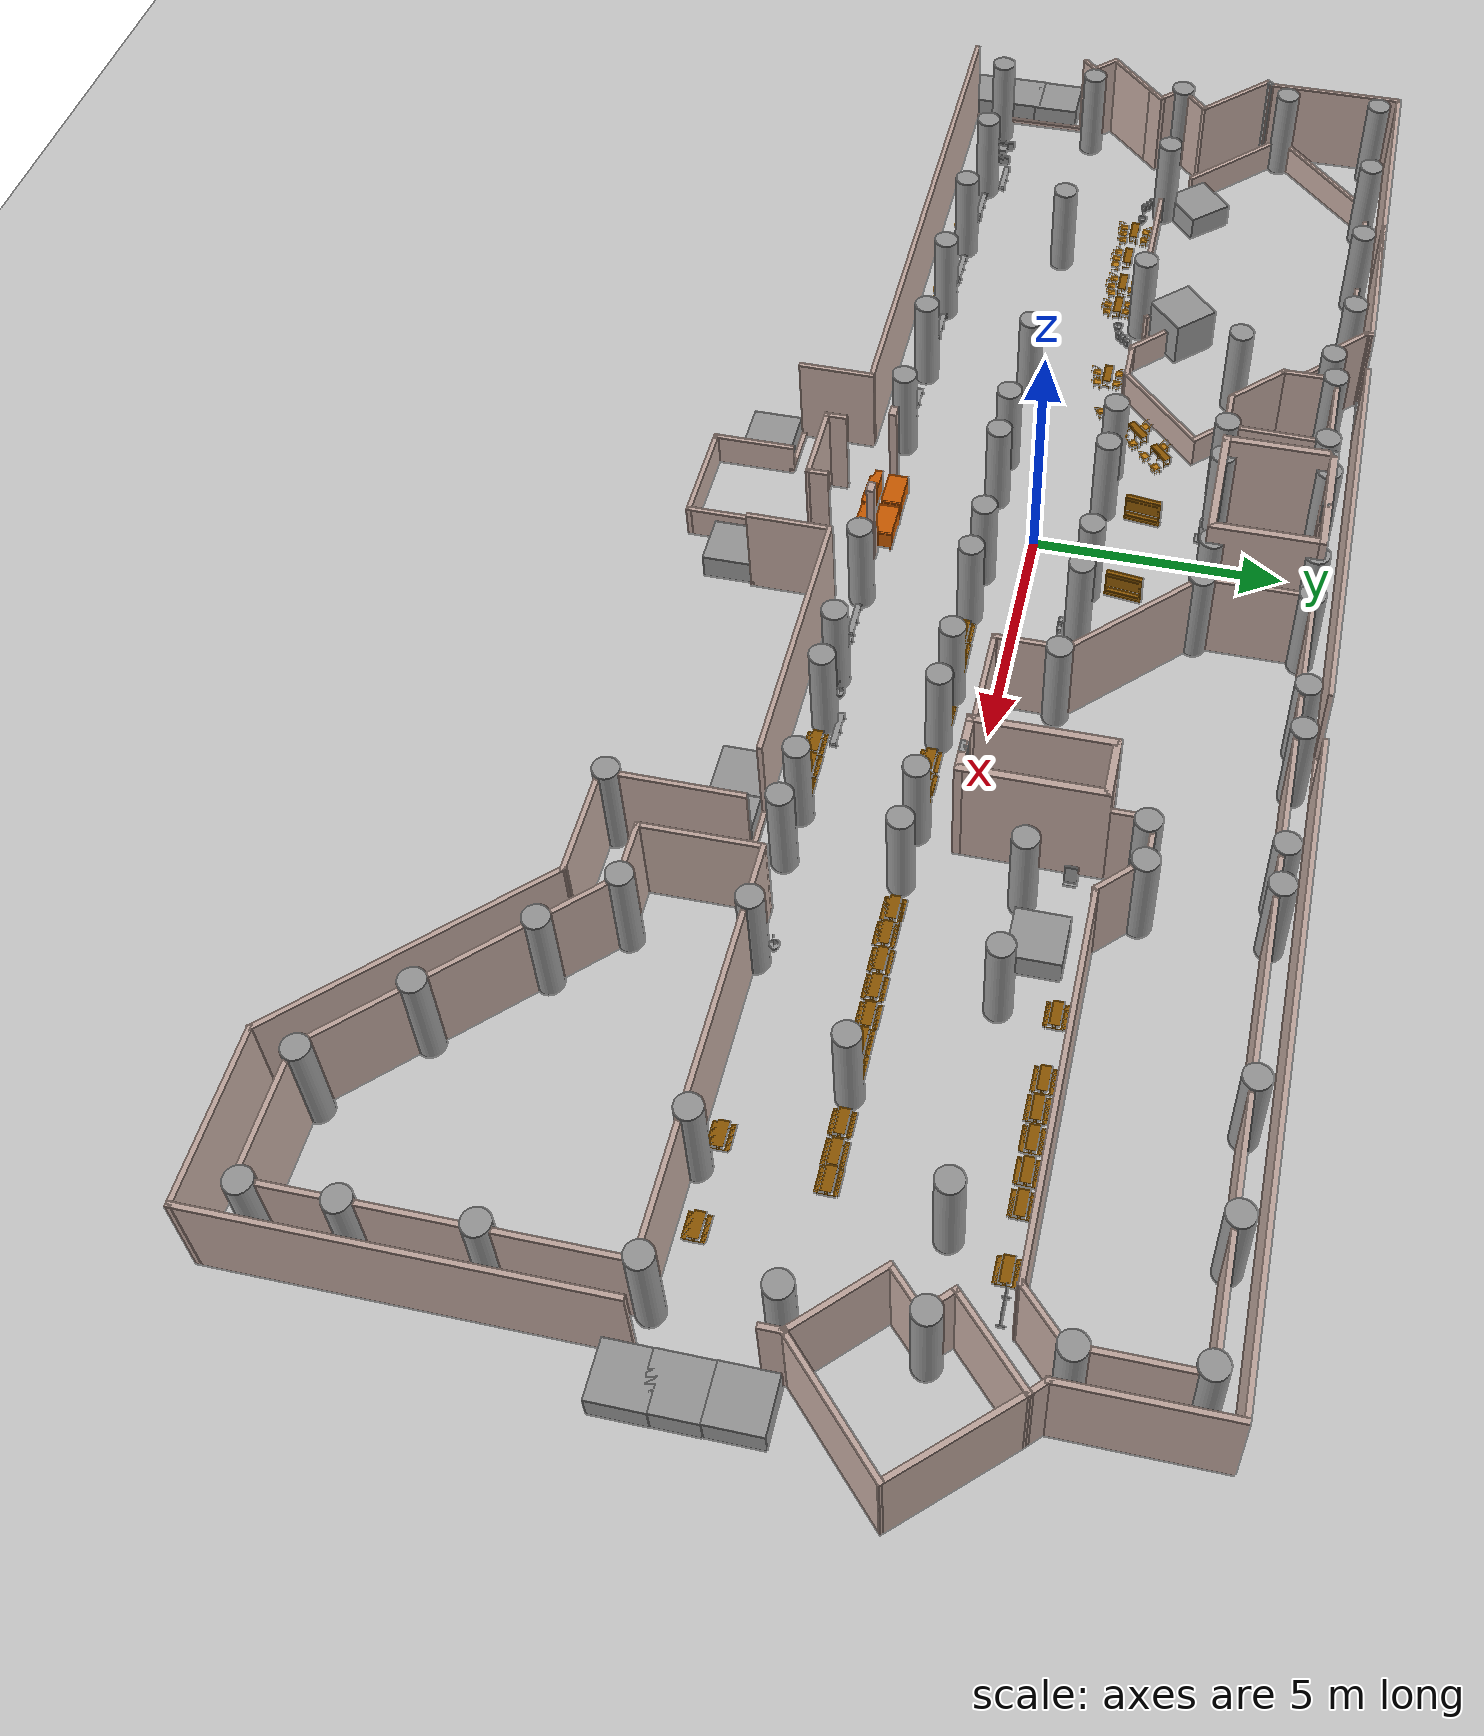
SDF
<sdf version="1.6">
 <world name="default">
  <light name="sun" type="directional">
   <pose>0 0 10 0 -0 0</pose>
   <diffuse>0.8 0.8 0.8 1</diffuse>
   <specular>0.2 0.2 0.2 1</specular>
   <attenuation>
    <range>1000</range>
    <constant>0.9</constant>
    <linear>0.01</linear>
    <quadratic>0.001</quadratic>
   </attenuation>
   <direction>-0.5 0.1 -0.9</direction>
  </light>
  <gazebo><static>true</static></gazebo>
  <model name="ground_plane">
   <static>1</static>
   <link name="link">
    <collision name="collision">
     <geometry><plane><normal>0 0 1</normal><size>100 100</size></plane></geometry>
     <surface>
      <contact><collide_bitmask>65535</collide_bitmask></contact>
      <friction><ode><mu>100</mu><mu2>50</mu2></ode></friction>
     </surface>
    </collision>
    <visual name="visual">
     <cast_shadows>0</cast_shadows>
     <geometry><plane><normal>0 0 1</normal><size>100 100</size></plane></geometry>
     <material>
      <script><uri>file://media/materials/scripts/gazebo.material</uri><name>Gazebo/Grey</name></script>
     </material>
    </visual>
   </link>
  </model>
  <gravity>0 0 -9.8</gravity>
  <magnetic_field>6e-06 2.3e-05 -4.2e-05</magnetic_field>
  <atmosphere type="adiabatic"/>
  <physics name="default_physics" default="0" type="ode">
   <max_step_size>0.001</max_step_size>
   <real_time_factor>1</real_time_factor>
   <real_time_update_rate>1000</real_time_update_rate>
  </physics>
  <scene><ambient>0.4 0.4 0.4 1</ambient><background>0.7 0.7 0.7 1</background><shadows>1</shadows></scene>
  <audio><device>default</device></audio>
  <spherical_coordinates>
   <surface_model>EARTH_WGS84</surface_model>
   <latitude_deg>0</latitude_deg>
   <longitude_deg>0</longitude_deg>
   <elevation>0</elevation>
   <heading_deg>0</heading_deg>
  </spherical_coordinates>
  <model name="gedung_p">
   <pose>2.96636 -2.09069 0 0 -0 0</pose>
   <link name="Wall_104">
    <collision name="Wall_104_Collision">
     <geometry><box><size>1.44987 0.1 2</size></box></geometry>
     <pose>0 0 1 0 -0 0</pose>
    </collision>
    <visual name="Wall_104_Visual">
     <pose>0 0 1 0 -0 0</pose>
     <geometry><box><size>1.44987 0.1 2</size></box></geometry>
     <material>
      <script><uri>file://media/materials/scripts/gazebo.material</uri><name>Gazebo/Grey</name></script>
      <ambient>0.760784 0.662745 0.627451 1</ambient>
     </material>
     <meta><layer>0</layer></meta>
    </visual>
    <pose>-6.41651 6.00131 0 0 -0 -0.785922</pose>
   </link>
   <link name="Wall_105">
    <collision name="Wall_105_Collision">
     <geometry><box><size>0.95 0.1 2</size></box></geometry>
     <pose>0 0 1 0 -0 0</pose>
    </collision>
    <visual name="Wall_105_Visual">
     <pose>0 0 1 0 -0 0</pose>
     <geometry><box><size>0.95 0.1 2</size></box></geometry>
     <material>
      <script><uri>file://media/materials/scripts/gazebo.material</uri><name>Gazebo/Grey</name></script>
      <ambient>0.760784 0.662745 0.627451 1</ambient>
     </material>
     <meta><layer>0</layer></meta>
    </visual>
    <pose>-5.51451 5.52381 0 0 -0 0</pose>
   </link>
   <link name="Wall_108">
    <collision name="Wall_108_Collision">
     <geometry><box><size>2.5 0.15 2.5</size></box></geometry>
     <pose>0 0 1.25 0 -0 0</pose>
    </collision>
    <visual name="Wall_108_Visual">
     <pose>0 0 1.25 0 -0 0</pose>
     <geometry><box><size>2.5 0.15 2.5</size></box></geometry>
     <material>
      <script><uri>file://media/materials/scripts/gazebo.material</uri><name>Gazebo/Grey</name></script>
      <ambient>0.760784 0.662745 0.627451 1</ambient>
     </material>
     <meta><layer>0</layer></meta>
    </visual>
    <pose>-3.04751 7.6698 0 0 -0 0</pose>
   </link>
   <link name="Wall_11">
    <collision name="Wall_11_Collision">
     <geometry><box><size>1.5 0.1 2</size></box></geometry>
     <pose>0 0 1 0 -0 0</pose>
    </collision>
    <visual name="Wall_11_Visual">
     <pose>0 0 1 0 -0 0</pose>
     <geometry><box><size>1.5 0.1 2</size></box></geometry>
     <material>
      <script><uri>file://media/materials/scripts/gazebo.material</uri><name>Gazebo/Grey</name></script>
      <ambient>0.760784 0.662745 0.627451 1</ambient>
     </material>
     <meta><layer>0</layer></meta>
    </visual>
    <pose>-16.1925 2.05681 0 0 -0 0.785398</pose>
   </link>
   <link name="Wall_116">
    <collision name="Wall_116_Collision">
     <geometry><box><size>1.20046 0.1 0.1</size></box></geometry>
     <pose>0 0 0.05 0 -0 0</pose>
    </collision>
    <visual name="Wall_116_Visual">
     <pose>0 0 0.05 0 -0 0</pose>
     <geometry><box><size>1.20046 0.1 0.1</size></box></geometry>
     <material>
      <script><uri>file://media/materials/scripts/gazebo.material</uri><name>Gazebo/Grey</name></script>
      <ambient>1 1 1 1</ambient>
     </material>
     <meta><layer>0</layer></meta>
    </visual>
    <pose>-7.82151 8.1548 0 0 -0 3.14159</pose>
   </link>
   <link name="Wall_119">
    <collision name="Wall_119_Collision">
     <geometry><box><size>8.7 0.1 2</size></box></geometry>
     <pose>0 0 1 0 -0 0</pose>
    </collision>
    <visual name="Wall_119_Visual">
     <pose>0 0 1 0 -0 0</pose>
     <geometry><box><size>8.7 0.1 2</size></box></geometry>
     <material>
      <script><uri>file://media/materials/scripts/gazebo.material</uri><name>Gazebo/Grey</name></script>
      <ambient>0.760784 0.662745 0.627451 1</ambient>
     </material>
     <meta><layer>0</layer></meta>
    </visual>
    <pose>-2.97151 8.1548 0 0 -0 0</pose>
   </link>
   <link name="Wall_122">
    <collision name="Wall_122_Collision">
     <geometry><box><size>2.45 0.1 0.7</size></box></geometry>
     <pose>0 0 0.35 0 -0 0</pose>
    </collision>
    <visual name="Wall_122_Visual">
     <pose>0 0 0.35 0 -0 0</pose>
     <geometry><box><size>2.45 0.1 0.7</size></box></geometry>
     <material>
      <script><uri>file://media/materials/scripts/gazebo.material</uri><name>Gazebo/Grey</name></script>
      <ambient>0.760784 0.662745 0.627451 1</ambient>
     </material>
     <meta><layer>0</layer></meta>
    </visual>
    <pose>-8.34851 6.9748 0 0 -0 -0.785398</pose>
   </link>
   <link name="Wall_124">
    <collision name="Wall_124_Collision">
     <geometry><box><size>1.2 0.1 2</size></box></geometry>
     <pose>0 0 1 0 -0 0</pose>
    </collision>
    <visual name="Wall_124_Visual">
     <pose>0 0 1 0 -0 0</pose>
     <geometry><box><size>1.2 0.1 2</size></box></geometry>
     <material>
      <script><uri>file://media/materials/scripts/gazebo.material</uri><name>Gazebo/Grey</name></script>
      <ambient>0.760784 0.662745 0.627451 1</ambient>
     </material>
     <meta><layer>0</layer></meta>
    </visual>
    <pose>-6.89351 7.02881 0 0 -0 1.5708</pose>
   </link>
   <link name="Wall_125">
    <collision name="Wall_125_Collision">
     <geometry><box><size>1.95 0.1 2</size></box></geometry>
     <pose>0 0 1 0 -0 0</pose>
    </collision>
    <visual name="Wall_125_Visual">
     <pose>0 0 1 0 -0 0</pose>
     <geometry><box><size>1.95 0.1 2</size></box></geometry>
     <material>
      <script><uri>file://media/materials/scripts/gazebo.material</uri><name>Gazebo/Grey</name></script>
      <ambient>0.760784 0.662745 0.627451 1</ambient>
     </material>
     <meta><layer>0</layer></meta>
    </visual>
    <pose>-5.96851 7.57881 0 0 -0 0</pose>
   </link>
   <link name="Wall_126">
    <collision name="Wall_126_Collision">
     <geometry><box><size>2.15551 0.1 2</size></box></geometry>
     <pose>0 0 1 0 -0 0</pose>
    </collision>
    <visual name="Wall_126_Visual">
     <pose>0 0 1 0 -0 0</pose>
     <geometry><box><size>2.15551 0.1 2</size></box></geometry>
     <material>
      <script><uri>file://media/materials/scripts/gazebo.material</uri><name>Gazebo/Grey</name></script>
      <ambient>0.760784 0.662745 0.627451 1</ambient>
     </material>
     <meta><layer>0</layer></meta>
    </visual>
    <pose>-5.06651 6.55131 0 0 -0 -1.59318</pose>
   </link>
   <link name="Wall_128">
    <collision name="Wall_128_Collision">
     <geometry><box><size>2.25 0.15 2.5</size></box></geometry>
     <pose>0 0 1.25 0 -0 0</pose>
    </collision>
    <visual name="Wall_128_Visual">
     <pose>0 0 1.25 0 -0 0</pose>
     <geometry><box><size>2.25 0.15 2.5</size></box></geometry>
     <material>
      <script><uri>file://media/materials/scripts/gazebo.material</uri><name>Gazebo/Grey</name></script>
      <ambient>0.760784 0.662745 0.627451 1</ambient>
     </material>
     <meta><layer>0</layer></meta>
    </visual>
    <pose>-4.22251 6.61981 0 0 -0 -1.5708</pose>
   </link>
   <link name="Wall_129">
    <collision name="Wall_129_Collision">
     <geometry><box><size>2.5 0.15 2.5</size></box></geometry>
     <pose>0 0 1.25 0 -0 0</pose>
    </collision>
    <visual name="Wall_129_Visual">
     <pose>0 0 1.25 0 -0 0</pose>
     <geometry><box><size>2.5 0.15 2.5</size></box></geometry>
     <material>
      <script><uri>file://media/materials/scripts/gazebo.material</uri><name>Gazebo/Grey</name></script>
      <ambient>0.760784 0.662745 0.627451 1</ambient>
     </material>
     <meta><layer>0</layer></meta>
    </visual>
    <pose>-3.04751 5.5698 0 0 -0 0</pose>
   </link>
   <link name="Wall_130">
    <collision name="Wall_130_Collision">
     <geometry><box><size>2.25 0.15 2.5</size></box></geometry>
     <pose>0 0 1.25 0 -0 0</pose>
    </collision>
    <visual name="Wall_130_Visual">
     <pose>0 0 1.25 0 -0 0</pose>
     <geometry><box><size>2.25 0.15 2.5</size></box></geometry>
     <material>
      <script><uri>file://media/materials/scripts/gazebo.material</uri><name>Gazebo/Grey</name></script>
      <ambient>0.760784 0.662745 0.627451 1</ambient>
     </material>
     <meta><layer>0</layer></meta>
    </visual>
    <pose>-1.87251 6.61981 0 0 -0 1.5708</pose>
   </link>
   <link name="Wall_132">
    <collision name="Wall_132_Collision">
     <geometry><box><size>2.20004 0.1 2</size></box></geometry>
     <pose>0 0 1 0 -0 0</pose>
    </collision>
    <visual name="Wall_132_Visual">
     <pose>0 0 1 0 -0 0</pose>
     <geometry><box><size>2.20004 0.1 2</size></box></geometry>
     <material>
      <script><uri>file://media/materials/scripts/gazebo.material</uri><name>Gazebo/Grey</name></script>
      <ambient>0.760784 0.662745 0.627451 1</ambient>
     </material>
     <meta><layer>0</layer></meta>
    </visual>
    <pose>-0.943512 6.5908 0 0 -0 -1.5708</pose>
   </link>
   <link name="Wall_137">
    <collision name="Wall_137_Collision">
     <geometry><box><size>3.20031 0.1 2</size></box></geometry>
     <pose>0 0 1 0 -0 0</pose>
    </collision>
    <visual name="Wall_137_Visual">
     <pose>0 0 1 0 -0 0</pose>
     <geometry><box><size>3.20031 0.1 2</size></box></geometry>
     <material>
      <script><uri>file://media/materials/scripts/gazebo.material</uri><name>Gazebo/Grey</name></script>
      <ambient>0.760784 0.662745 0.627451 1</ambient>
     </material>
     <meta><layer>0</layer></meta>
    </visual>
    <pose>0.152488 4.4448 0 0 -0 -0.785398</pose>
   </link>
   <link name="Wall_138">
    <collision name="Wall_138_Collision">
     <geometry><box><size>1.45007 0.1 2</size></box></geometry>
     <pose>0 0 1 0 -0 0</pose>
    </collision>
    <visual name="Wall_138_Visual">
     <pose>0 0 1 0 -0 0</pose>
     <geometry><box><size>1.45007 0.1 2</size></box></geometry>
     <material>
      <script><uri>file://media/materials/scripts/gazebo.material</uri><name>Gazebo/Grey</name></script>
      <ambient>0.760784 0.662745 0.627451 1</ambient>
     </material>
     <meta><layer>0</layer></meta>
    </visual>
    <pose>1.24849 2.67381 0 0 -0 -1.5708</pose>
   </link>
   <link name="Wall_139">
    <collision name="Wall_139_Collision">
     <geometry><box><size>2.45043 0.1 2</size></box></geometry>
     <pose>0 0 1 0 -0 0</pose>
    </collision>
    <visual name="Wall_139_Visual">
     <pose>0 0 1 0 -0 0</pose>
     <geometry><box><size>2.45043 0.1 2</size></box></geometry>
     <material>
      <script><uri>file://media/materials/scripts/gazebo.material</uri><name>Gazebo/Grey</name></script>
      <ambient>0.760784 0.662745 0.627451 1</ambient>
     </material>
     <meta><layer>0</layer></meta>
    </visual>
    <pose>2.42349 1.9988 0 0 -0 0</pose>
   </link>
   <link name="Wall_140">
    <collision name="Wall_140_Collision">
     <geometry><box><size>2.75 0.15 2.5</size></box></geometry>
     <pose>0 0 1.25 0 -0 0</pose>
    </collision>
    <visual name="Wall_140_Visual">
     <pose>0 0 1.25 0 -0 0</pose>
     <geometry><box><size>2.75 0.15 2.5</size></box></geometry>
     <material>
      <script><uri>file://media/materials/scripts/gazebo.material</uri><name>Gazebo/Grey</name></script>
      <ambient>0.760784 0.662745 0.627451 1</ambient>
     </material>
     <meta><layer>0</layer></meta>
    </visual>
    <pose>3.59849 3.29881 0 0 -0 1.5708</pose>
   </link>
   <link name="Wall_141">
    <collision name="Wall_141_Collision">
     <geometry><box><size>1.25 0.15 2.5</size></box></geometry>
     <pose>0 0 1.25 0 -0 0</pose>
    </collision>
    <visual name="Wall_141_Visual">
     <pose>0 0 1.25 0 -0 0</pose>
     <geometry><box><size>1.25 0.15 2.5</size></box></geometry>
     <material>
      <script><uri>file://media/materials/scripts/gazebo.material</uri><name>Gazebo/Grey</name></script>
      <ambient>0.760784 0.662745 0.627451 1</ambient>
     </material>
     <meta><layer>0</layer></meta>
    </visual>
    <pose>4.14849 4.5988 0 0 -0 0</pose>
   </link>
   <link name="Wall_142">
    <collision name="Wall_142_Collision">
     <geometry><box><size>2.75 0.15 2.5</size></box></geometry>
     <pose>0 0 1.25 0 -0 0</pose>
    </collision>
    <visual name="Wall_142_Visual">
     <pose>0 0 1.25 0 -0 0</pose>
     <geometry><box><size>2.75 0.15 2.5</size></box></geometry>
     <material>
      <script><uri>file://media/materials/scripts/gazebo.material</uri><name>Gazebo/Grey</name></script>
      <ambient>0.760784 0.662745 0.627451 1</ambient>
     </material>
     <meta><layer>0</layer></meta>
    </visual>
    <pose>4.69849 3.29881 0 0 -0 -1.5708</pose>
   </link>
   <link name="Wall_143">
    <collision name="Wall_143_Collision">
     <geometry><box><size>1.25 0.15 2.5</size></box></geometry>
     <pose>0 0 1.25 0 -0 0</pose>
    </collision>
    <visual name="Wall_143_Visual">
     <pose>0 0 1.25 0 -0 0</pose>
     <geometry><box><size>1.25 0.15 2.5</size></box></geometry>
     <material>
      <script><uri>file://media/materials/scripts/gazebo.material</uri><name>Gazebo/Grey</name></script>
      <ambient>0.760784 0.662745 0.627451 1</ambient>
     </material>
     <meta><layer>0</layer></meta>
    </visual>
    <pose>4.14849 1.9988 0 0 -0 3.14159</pose>
   </link>
   <link name="Wall_145">
    <collision name="Wall_145_Collision">
     <geometry><box><size>15.25 0.1 2</size></box></geometry>
     <pose>0 0 1 0 -0 0</pose>
    </collision>
    <visual name="Wall_145_Visual">
     <pose>0 0 1 0 -0 0</pose>
     <geometry><box><size>15.25 0.1 2</size></box></geometry>
     <material>
      <script><uri>file://media/materials/scripts/gazebo.material</uri><name>Gazebo/Grey</name></script>
      <ambient>0.760784 0.662745 0.627451 1</ambient>
     </material>
     <meta><layer>0</layer></meta>
    </visual>
    <pose>6.63149 7.64081 0 0 -0 0</pose>
   </link>
   <link name="Wall_147">
    <collision name="Wall_147_Collision">
     <geometry><box><size>1.2 0.1 0.1</size></box></geometry>
     <pose>0 0 0.05 0 -0 0</pose>
    </collision>
    <visual name="Wall_147_Visual">
     <pose>0 0 0.05 0 -0 0</pose>
     <geometry><box><size>1.2 0.1 0.1</size></box></geometry>
     <material>
      <script><uri>file://media/materials/scripts/gazebo.material</uri><name>Gazebo/Grey</name></script>
      <ambient>0.760784 0.662745 0.627451 1</ambient>
     </material>
     <meta><layer>0</layer></meta>
    </visual>
    <pose>1.87849 8.1548 0 0 -0 0</pose>
   </link>
   <link name="Wall_149">
    <collision name="Wall_149_Collision">
     <geometry><box><size>0.95 0.1 2</size></box></geometry>
     <pose>0 0 1 0 -0 0</pose>
    </collision>
    <visual name="Wall_149_Visual">
     <pose>0 0 1 0 -0 0</pose>
     <geometry><box><size>0.95 0.1 2</size></box></geometry>
     <material>
      <script><uri>file://media/materials/scripts/gazebo.material</uri><name>Gazebo/Grey</name></script>
      <ambient>0.760784 0.662745 0.627451 1</ambient>
     </material>
     <meta><layer>0</layer></meta>
    </visual>
    <pose>4.69849 5.02381 0 0 -0 1.5708</pose>
   </link>
   <link name="Wall_150">
    <collision name="Wall_150_Collision">
     <geometry><box><size>0.95 0.1 2</size></box></geometry>
     <pose>0 0 1 0 -0 0</pose>
    </collision>
    <visual name="Wall_150_Visual">
     <pose>0 0 1 0 -0 0</pose>
     <geometry><box><size>0.95 0.1 2</size></box></geometry>
     <material>
      <script><uri>file://media/materials/scripts/gazebo.material</uri><name>Gazebo/Grey</name></script>
      <ambient>0.760784 0.662745 0.627451 1</ambient>
     </material>
     <meta><layer>0</layer></meta>
    </visual>
    <pose>5.12349 5.44881 0 0 -0 0</pose>
   </link>
   <link name="Wall_151">
    <collision name="Wall_151_Collision">
     <geometry><box><size>1.2 0.1 2</size></box></geometry>
     <pose>0 0 1 0 -0 0</pose>
    </collision>
    <visual name="Wall_151_Visual">
     <pose>0 0 1 0 -0 0</pose>
     <geometry><box><size>1.2 0.1 2</size></box></geometry>
     <material>
      <script><uri>file://media/materials/scripts/gazebo.material</uri><name>Gazebo/Grey</name></script>
      <ambient>0.760784 0.662745 0.627451 1</ambient>
     </material>
     <meta><layer>0</layer></meta>
    </visual>
    <pose>5.93749 5.0598 0 0 -0 -0.785398</pose>
   </link>
   <link name="Wall_152">
    <collision name="Wall_152_Collision">
     <geometry><box><size>7.2 0.1 2</size></box></geometry>
     <pose>0 0 1 0 -0 0</pose>
    </collision>
    <visual name="Wall_152_Visual">
     <pose>0 0 1 0 -0 0</pose>
     <geometry><box><size>7.2 0.1 2</size></box></geometry>
     <material>
      <script><uri>file://media/materials/scripts/gazebo.material</uri><name>Gazebo/Grey</name></script>
      <ambient>0.760784 0.662745 0.627451 1</ambient>
     </material>
     <meta><layer>0</layer></meta>
    </visual>
    <pose>9.87649 4.6708 0 0 -0 0</pose>
   </link>
   <link name="Wall_154">
    <collision name="Wall_154_Collision">
     <geometry><box><size>1.20026 0.1 2</size></box></geometry>
     <pose>0 0 1 0 -0 0</pose>
    </collision>
    <visual name="Wall_154_Visual">
     <pose>0 0 1 0 -0 0</pose>
     <geometry><box><size>1.20026 0.1 2</size></box></geometry>
     <material>
      <script><uri>file://media/materials/scripts/gazebo.material</uri><name>Gazebo/Grey</name></script>
      <ambient>0.760784 0.662745 0.627451 1</ambient>
     </material>
     <meta><layer>0</layer></meta>
    </visual>
    <pose>13.8155 5.0598 0 0 -0 0.785398</pose>
   </link>
   <link name="Wall_155">
    <collision name="Wall_155_Collision">
     <geometry><box><size>2.19982 0.1 2</size></box></geometry>
     <pose>0 0 1 0 -0 0</pose>
    </collision>
    <visual name="Wall_155_Visual">
     <pose>0 0 1 0 -0 0</pose>
     <geometry><box><size>2.19982 0.1 2</size></box></geometry>
     <material>
      <script><uri>file://media/materials/scripts/gazebo.material</uri><name>Gazebo/Grey</name></script>
      <ambient>0.760784 0.662745 0.627451 1</ambient>
     </material>
     <meta><layer>0</layer></meta>
    </visual>
    <pose>14.2045 6.4988 0 0 -0 1.5708</pose>
   </link>
   <link name="Wall_157">
    <collision name="Wall_157_Collision">
     <geometry><box><size>12.45 0.1 2</size></box></geometry>
     <pose>0 0 1 0 -0 0</pose>
    </collision>
    <visual name="Wall_157_Visual">
     <pose>0 0 1 0 -0 0</pose>
     <geometry><box><size>12.45 0.1 2</size></box></geometry>
     <material>
      <script><uri>file://media/materials/scripts/gazebo.material</uri><name>Gazebo/Grey</name></script>
      <ambient>0.760784 0.662745 0.627451 1</ambient>
     </material>
     <meta><layer>0</layer></meta>
    </visual>
    <pose>8.60349 8.1548 0 0 -0 0</pose>
   </link>
   <link name="Wall_159">
    <collision name="Wall_159_Collision">
     <geometry><box><size>2.95 0.1 2</size></box></geometry>
     <pose>0 0 1 0 -0 0</pose>
    </collision>
    <visual name="Wall_159_Visual">
     <pose>0 0 1 0 -0 0</pose>
     <geometry><box><size>2.95 0.1 2</size></box></geometry>
     <material>
      <script><uri>file://media/materials/scripts/gazebo.material</uri><name>Gazebo/Grey</name></script>
      <ambient>0.760784 0.662745 0.627451 1</ambient>
     </material>
     <meta><layer>0</layer></meta>
    </visual>
    <pose>14.7785 6.7298 0 0 -0 -1.5708</pose>
   </link>
   <link name="Wall_161">
    <collision name="Wall_161_Collision">
     <geometry><box><size>0.449311 0.1 2</size></box></geometry>
     <pose>0 0 1 0 -0 0</pose>
    </collision>
    <visual name="Wall_161_Visual">
     <pose>0 0 1 0 -0 0</pose>
     <geometry><box><size>0.449311 0.1 2</size></box></geometry>
     <material>
      <script><uri>file://media/materials/scripts/gazebo.material</uri><name>Gazebo/Grey</name></script>
      <ambient>0.760784 0.662745 0.627451 1</ambient>
     </material>
     <meta><layer>0</layer></meta>
    </visual>
    <pose>14.902 5.18131 0 0 -0 -0.785398</pose>
   </link>
   <link name="Wall_162">
    <collision name="Wall_162_Collision">
     <geometry><box><size>1.95 0.1 2</size></box></geometry>
     <pose>0 0 1 0 -0 0</pose>
    </collision>
    <visual name="Wall_162_Visual">
     <pose>0 0 1 0 -0 0</pose>
     <geometry><box><size>1.95 0.1 2</size></box></geometry>
     <material>
      <script><uri>file://media/materials/scripts/gazebo.material</uri><name>Gazebo/Grey</name></script>
      <ambient>0.760784 0.662745 0.627451 1</ambient>
     </material>
     <meta><layer>0</layer></meta>
    </visual>
    <pose>14.3715 4.4033 0 0 -0 -2.35581</pose>
   </link>
   <link name="Wall_164">
    <collision name="Wall_164_Collision">
     <geometry><box><size>0.699982 0.1 2</size></box></geometry>
     <pose>0 0 1 0 -0 0</pose>
    </collision>
    <visual name="Wall_164_Visual">
     <pose>0 0 1 0 -0 0</pose>
     <geometry><box><size>0.699982 0.1 2</size></box></geometry>
     <material>
      <script><uri>file://media/materials/scripts/gazebo.material</uri><name>Gazebo/Grey</name></script>
      <ambient>0.760784 0.662745 0.627451 1</ambient>
     </material>
     <meta><layer>0</layer></meta>
    </visual>
    <pose>13.93 3.53681 0 0 -0 -0.78422</pose>
   </link>
   <link name="Wall_165">
    <collision name="Wall_165_Collision">
     <geometry><box><size>0.950209 0.1 2</size></box></geometry>
     <pose>0 0 1 0 -0 0</pose>
    </collision>
    <visual name="Wall_165_Visual">
     <pose>0 0 1 0 -0 0</pose>
     <geometry><box><size>0.950209 0.1 2</size></box></geometry>
     <material>
      <script><uri>file://media/materials/scripts/gazebo.material</uri><name>Gazebo/Grey</name></script>
      <ambient>0.760784 0.662745 0.627451 1</ambient>
     </material>
     <meta><layer>0</layer></meta>
    </visual>
    <pose>13.842 3.02431 0 0 -0 -2.35619</pose>
   </link>
   <link name="Wall_166">
    <collision name="Wall_166_Collision">
     <geometry><box><size>1.94965 0.1 2</size></box></geometry>
     <pose>0 0 1 0 -0 0</pose>
    </collision>
    <visual name="Wall_166_Visual">
     <pose>0 0 1 0 -0 0</pose>
     <geometry><box><size>1.94965 0.1 2</size></box></geometry>
     <material>
      <script><uri>file://media/materials/scripts/gazebo.material</uri><name>Gazebo/Grey</name></script>
      <ambient>0.760784 0.662745 0.627451 1</ambient>
     </material>
     <meta><layer>0</layer></meta>
    </visual>
    <pose>14.1955 2.06981 0 0 -0 -0.785398</pose>
   </link>
   <link name="Wall_169">
    <collision name="Wall_169_Collision">
     <geometry><box><size>2.69932 0.1 2</size></box></geometry>
     <pose>0 0 1 0 -0 0</pose>
    </collision>
    <visual name="Wall_169_Visual">
     <pose>0 0 1 0 -0 0</pose>
     <geometry><box><size>2.69932 0.1 2</size></box></geometry>
     <material>
      <script><uri>file://media/materials/scripts/gazebo.material</uri><name>Gazebo/Grey</name></script>
      <ambient>0.760784 0.662745 0.627451 1</ambient>
     </material>
     <meta><layer>0</layer></meta>
    </visual>
    <pose>15.7685 2.3348 0 0 -0 0.785398</pose>
   </link>
   <link name="Wall_17">
    <collision name="Wall_17_Collision">
     <geometry><box><size>0.449929 0.1 2</size></box></geometry>
     <pose>0 0 1 0 -0 0</pose>
    </collision>
    <visual name="Wall_17_Visual">
     <pose>0 0 1 0 -0 0</pose>
     <geometry><box><size>0.449929 0.1 2</size></box></geometry>
     <material>
      <script><uri>file://media/materials/scripts/gazebo.material</uri><name>Gazebo/Grey</name></script>
      <ambient>0.760784 0.662745 0.627451 1</ambient>
     </material>
     <meta><layer>0</layer></meta>
    </visual>
    <pose>-15.574 2.6753 0 0 -0 0.785398</pose>
   </link>
   <link name="Wall_173">
    <collision name="Wall_173_Collision">
     <geometry><box><size>2.55273 0.1 2</size></box></geometry>
     <pose>0 0 1 0 -0 0</pose>
    </collision>
    <visual name="Wall_173_Visual">
     <pose>0 0 1 0 -0 0</pose>
     <geometry><box><size>2.55273 0.1 2</size></box></geometry>
     <material>
      <script><uri>file://media/materials/scripts/gazebo.material</uri><name>Gazebo/Grey</name></script>
      <ambient>0.760784 0.662745 0.627451 1</ambient>
     </material>
     <meta><layer>0</layer></meta>
    </visual>
    <pose>15.8565 4.1558 0 0 -0 -0.826345</pose>
   </link>
   <link name="Wall_175">
    <collision name="Wall_175_Collision">
     <geometry><box><size>0.45 0.1 2</size></box></geometry>
     <pose>0 0 1 0 -0 0</pose>
    </collision>
    <visual name="Wall_175_Visual">
     <pose>0 0 1 0 -0 0</pose>
     <geometry><box><size>0.45 0.1 2</size></box></geometry>
     <material>
      <script><uri>file://media/materials/scripts/gazebo.material</uri><name>Gazebo/Grey</name></script>
      <ambient>0.760784 0.662745 0.627451 1</ambient>
     </material>
     <meta><layer>0</layer></meta>
    </visual>
    <pose>14.8495 1.2408 0 0 -0 -1.5708</pose>
   </link>
   <link name="Wall_176">
    <collision name="Wall_176_Collision">
     <geometry><box><size>2.2 0.1 0.1</size></box></geometry>
     <pose>0 0 0.05 0 -0 0</pose>
    </collision>
    <visual name="Wall_176_Visual">
     <pose>0 0 0.05 0 -0 0</pose>
     <geometry><box><size>2.2 0.1 0.1</size></box></geometry>
     <material>
      <script><uri>file://media/materials/scripts/gazebo.material</uri><name>Gazebo/Grey</name></script>
      <ambient>0.760784 0.662745 0.627451 1</ambient>
     </material>
     <meta><layer>0</layer></meta>
    </visual>
    <pose>14.8495 0.015805 0 0 -0 -1.5708</pose>
   </link>
   <link name="Wall_178">
    <collision name="Wall_178_Collision">
     <geometry><box><size>7.2 0.1 2</size></box></geometry>
     <pose>0 0 1 0 -0 0</pose>
    </collision>
    <visual name="Wall_178_Visual">
     <pose>0 0 1 0 -0 0</pose>
     <geometry><box><size>7.2 0.1 2</size></box></geometry>
     <material>
      <script><uri>file://media/materials/scripts/gazebo.material</uri><name>Gazebo/Grey</name></script>
      <ambient>0.760784 0.662745 0.627451 1</ambient>
     </material>
     <meta><layer>0</layer></meta>
    </visual>
    <pose>14.8495 -4.5842 0 0 -0 -1.5708</pose>
   </link>
   <link name="Wall_18">
    <collision name="Wall_18_Collision">
     <geometry><box><size>0.7 0.1 2</size></box></geometry>
     <pose>0 0 1 0 -0 0</pose>
    </collision>
    <visual name="Wall_18_Visual">
     <pose>0 0 1 0 -0 0</pose>
     <geometry><box><size>0.7 0.1 2</size></box></geometry>
     <material>
      <script><uri>file://media/materials/scripts/gazebo.material</uri><name>Gazebo/Grey</name></script>
      <ambient>0.760784 0.662745 0.627451 1</ambient>
     </material>
     <meta><layer>0</layer></meta>
    </visual>
    <pose>-15.6625 3.01131 0 0 -0 2.35502</pose>
   </link>
   <link name="Wall_180">
    <collision name="Wall_180_Collision">
     <geometry><box><size>3.2 0.1 2</size></box></geometry>
     <pose>0 0 1 0 -0 0</pose>
    </collision>
    <visual name="Wall_180_Visual">
     <pose>0 0 1 0 -0 0</pose>
     <geometry><box><size>3.2 0.1 2</size></box></geometry>
     <material>
      <script><uri>file://media/materials/scripts/gazebo.material</uri><name>Gazebo/Grey</name></script>
      <ambient>0.760784 0.662745 0.627451 1</ambient>
     </material>
     <meta><layer>0</layer></meta>
    </visual>
    <pose>13.2995 -8.1342 0 0 -0 3.14159</pose>
   </link>
   <link name="Wall_181">
    <collision name="Wall_181_Collision">
     <geometry><box><size>5.7 0.1 2</size></box></geometry>
     <pose>0 0 1 0 -0 0</pose>
    </collision>
    <visual name="Wall_181_Visual">
     <pose>0 0 1 0 -0 0</pose>
     <geometry><box><size>5.7 0.1 2</size></box></geometry>
     <material>
      <script><uri>file://media/materials/scripts/gazebo.material</uri><name>Gazebo/Grey</name></script>
      <ambient>0.760784 0.662745 0.627451 1</ambient>
     </material>
     <meta><layer>0</layer></meta>
    </visual>
    <pose>9.76949 -6.15419 0 0 -0 2.35619</pose>
   </link>
   <link name="Wall_182">
    <collision name="Wall_182_Collision">
     <geometry><box><size>2.2 0.1 2</size></box></geometry>
     <pose>0 0 1 0 -0 0</pose>
    </collision>
    <visual name="Wall_182_Visual">
     <pose>0 0 1 0 -0 0</pose>
     <geometry><box><size>2.2 0.1 2</size></box></geometry>
     <material>
      <script><uri>file://media/materials/scripts/gazebo.material</uri><name>Gazebo/Grey</name></script>
      <ambient>0.760784 0.662745 0.627451 1</ambient>
     </material>
     <meta><layer>0</layer></meta>
    </visual>
    <pose>6.73949 -4.1742 0 0 -0 3.14159</pose>
   </link>
   <link name="Wall_189">
    <collision name="Wall_189_Collision">
     <geometry><box><size>2.7 0.1 2</size></box></geometry>
     <pose>0 0 1 0 -0 0</pose>
    </collision>
    <visual name="Wall_189_Visual">
     <pose>0 0 1 0 -0 0</pose>
     <geometry><box><size>2.7 0.1 2</size></box></geometry>
     <material>
      <script><uri>file://media/materials/scripts/gazebo.material</uri><name>Gazebo/Grey</name></script>
      <ambient>0.760784 0.662745 0.627451 1</ambient>
     </material>
     <meta><layer>0</layer></meta>
    </visual>
    <pose>5.68949 -2.87419 0 0 -0 1.5708</pose>
   </link>
   <link name="Wall_19">
    <collision name="Wall_19_Collision">
     <geometry><box><size>0.949911 0.1 2</size></box></geometry>
     <pose>0 0 1 0 -0 0</pose>
    </collision>
    <visual name="Wall_19_Visual">
     <pose>0 0 1 0 -0 0</pose>
     <geometry><box><size>0.949911 0.1 2</size></box></geometry>
     <material>
      <script><uri>file://media/materials/scripts/gazebo.material</uri><name>Gazebo/Grey</name></script>
      <ambient>0.760784 0.662745 0.627451 1</ambient>
     </material>
     <meta><layer>0</layer></meta>
    </visual>
    <pose>-15.574 3.52431 0 0 -0 0.785398</pose>
   </link>
   <link name="Wall_190">
    <collision name="Wall_190_Collision">
     <geometry><box><size>1.189 0.1 0.1</size></box></geometry>
     <pose>0 0 0.05 0 -0 0</pose>
    </collision>
    <visual name="Wall_190_Visual">
     <pose>0 0 0.05 0 -0 0</pose>
     <geometry><box><size>1.189 0.1 0.1</size></box></geometry>
     <material>
      <script><uri>file://media/materials/scripts/gazebo.material</uri><name>Gazebo/Grey</name></script>
      <ambient>0.760784 0.662745 0.627451 1</ambient>
     </material>
     <meta><layer>0</layer></meta>
    </visual>
    <pose>5.14499 -1.5742 0 0 -0 3.14159</pose>
   </link>
   <link name="Wall_191">
    <collision name="Wall_191_Collision">
     <geometry><box><size>5.44985 0.1 2</size></box></geometry>
     <pose>0 0 1 0 -0 0</pose>
    </collision>
    <visual name="Wall_191_Visual">
     <pose>0 0 1 0 -0 0</pose>
     <geometry><box><size>5.44985 0.1 2</size></box></geometry>
     <material>
      <script><uri>file://media/materials/scripts/gazebo.material</uri><name>Gazebo/Grey</name></script>
      <ambient>0.760784 0.662745 0.627451 1</ambient>
     </material>
     <meta><layer>0</layer></meta>
    </visual>
    <pose>1.92549 -1.5742 0 0 -0 3.14159</pose>
   </link>
   <link name="Wall_192">
    <collision name="Wall_192_Collision">
     <geometry><box><size>1.70004 0.1 2</size></box></geometry>
     <pose>0 0 1 0 -0 0</pose>
    </collision>
    <visual name="Wall_192_Visual">
     <pose>0 0 1 0 -0 0</pose>
     <geometry><box><size>1.70004 0.1 2</size></box></geometry>
     <material>
      <script><uri>file://media/materials/scripts/gazebo.material</uri><name>Gazebo/Grey</name></script>
      <ambient>0.760784 0.662745 0.627451 1</ambient>
     </material>
     <meta><layer>0</layer></meta>
    </visual>
    <pose>-0.755012 -2.37419 0 0 -0 -1.57767</pose>
   </link>
   <link name="Wall_194">
    <collision name="Wall_194_Collision">
     <geometry><box><size>1.2 0.1 0.1</size></box></geometry>
     <pose>0 0 0.05 0 -0 0</pose>
    </collision>
    <visual name="Wall_194_Visual">
     <pose>0 0 0.05 0 -0 0</pose>
     <geometry><box><size>1.2 0.1 0.1</size></box></geometry>
     <material>
      <script><uri>file://media/materials/scripts/gazebo.material</uri><name>Gazebo/Grey</name></script>
      <ambient>0.760784 0.662745 0.627451 1</ambient>
     </material>
     <meta><layer>0</layer></meta>
    </visual>
    <pose>-1.31051 -3.1742 0 0 -0 3.14159</pose>
   </link>
   <link name="Wall_195">
    <collision name="Wall_195_Collision">
     <geometry><box><size>1.7 0.1 0.7</size></box></geometry>
     <pose>0 0 0.35 0 -0 0</pose>
    </collision>
    <visual name="Wall_195_Visual">
     <pose>0 0 0.35 0 -0 0</pose>
     <geometry><box><size>1.7 0.1 0.7</size></box></geometry>
     <material>
      <script><uri>file://media/materials/scripts/gazebo.material</uri><name>Gazebo/Grey</name></script>
      <ambient>0.760784 0.662745 0.627451 1</ambient>
     </material>
     <meta><layer>0</layer></meta>
    </visual>
    <pose>-1.86051 -3.97419 0 0 -0 -1.5708</pose>
   </link>
   <link name="Wall_196">
    <collision name="Wall_196_Collision">
     <geometry><box><size>2.2 0.1 0.7</size></box></geometry>
     <pose>0 0 0.35 0 -0 0</pose>
    </collision>
    <visual name="Wall_196_Visual">
     <pose>0 0 0.35 0 -0 0</pose>
     <geometry><box><size>2.2 0.1 0.7</size></box></geometry>
     <material>
      <script><uri>file://media/materials/scripts/gazebo.material</uri><name>Gazebo/Grey</name></script>
      <ambient>0.760784 0.662745 0.627451 1</ambient>
     </material>
     <meta><layer>0</layer></meta>
    </visual>
    <pose>-2.91051 -4.77419 0 0 -0 3.14159</pose>
   </link>
   <link name="Wall_197">
    <collision name="Wall_197_Collision">
     <geometry><box><size>1.7 0.1 0.7</size></box></geometry>
     <pose>0 0 0.35 0 -0 0</pose>
    </collision>
    <visual name="Wall_197_Visual">
     <pose>0 0 0.35 0 -0 0</pose>
     <geometry><box><size>1.7 0.1 0.7</size></box></geometry>
     <material>
      <script><uri>file://media/materials/scripts/gazebo.material</uri><name>Gazebo/Grey</name></script>
      <ambient>0.760784 0.662745 0.627451 1</ambient>
     </material>
     <meta><layer>0</layer></meta>
    </visual>
    <pose>-3.96051 -3.97419 0 0 -0 1.5708</pose>
   </link>
   <link name="Wall_198">
    <collision name="Wall_198_Collision">
     <geometry><box><size>1.2 0.1 0.1</size></box></geometry>
     <pose>0 0 0.05 0 -0 0</pose>
    </collision>
    <visual name="Wall_198_Visual">
     <pose>0 0 0.05 0 -0 0</pose>
     <geometry><box><size>1.2 0.1 0.1</size></box></geometry>
     <material>
      <script><uri>file://media/materials/scripts/gazebo.material</uri><name>Gazebo/Grey</name></script>
      <ambient>0.760784 0.662745 0.627451 1</ambient>
     </material>
     <meta><layer>0</layer></meta>
    </visual>
    <pose>-4.51051 -3.1742 0 0 -0 3.14159</pose>
   </link>
   <link name="Wall_199">
    <collision name="Wall_199_Collision">
     <geometry><box><size>1.55413 0.1 2</size></box></geometry>
     <pose>0 0 1 0 -0 0</pose>
    </collision>
    <visual name="Wall_199_Visual">
     <pose>0 0 1 0 -0 0</pose>
     <geometry><box><size>1.55413 0.1 2</size></box></geometry>
     <material>
      <script><uri>file://media/materials/scripts/gazebo.material</uri><name>Gazebo/Grey</name></script>
      <ambient>0.760784 0.662745 0.627451 1</ambient>
     </material>
     <meta><layer>0</layer></meta>
    </visual>
    <pose>-5.05601 -2.44719 0 0 -0 1.56461</pose>
   </link>
   <link name="Wall_201">
    <collision name="Wall_201_Collision">
     <geometry><box><size>0.45 0.1 2</size></box></geometry>
     <pose>0 0 1 0 -0 0</pose>
    </collision>
    <visual name="Wall_201_Visual">
     <pose>0 0 1 0 -0 0</pose>
     <geometry><box><size>0.45 0.1 2</size></box></geometry>
     <material>
      <script><uri>file://media/materials/scripts/gazebo.material</uri><name>Gazebo/Grey</name></script>
      <ambient>0.760784 0.662745 0.627451 1</ambient>
     </material>
     <meta><layer>0</layer></meta>
    </visual>
    <pose>-3.75851 -2.16319 0 0 -0 -1.5708</pose>
   </link>
   <link name="Wall_202">
    <collision name="Wall_202_Collision">
     <geometry><box><size>1.7 0.1 2</size></box></geometry>
     <pose>0 0 1 0 -0 0</pose>
    </collision>
    <visual name="Wall_202_Visual">
     <pose>0 0 1 0 -0 0</pose>
     <geometry><box><size>1.7 0.1 2</size></box></geometry>
     <material>
      <script><uri>file://media/materials/scripts/gazebo.material</uri><name>Gazebo/Grey</name></script>
      <ambient>0.760784 0.662745 0.627451 1</ambient>
     </material>
     <meta><layer>0</layer></meta>
    </visual>
    <pose>-2.95851 -2.33819 0 0 -0 0</pose>
   </link>
   <link name="Wall_203">
    <collision name="Wall_203_Collision">
     <geometry><box><size>0.450476 0.1 2</size></box></geometry>
     <pose>0 0 1 0 -0 0</pose>
    </collision>
    <visual name="Wall_203_Visual">
     <pose>0 0 1 0 -0 0</pose>
     <geometry><box><size>0.450476 0.1 2</size></box></geometry>
     <material>
      <script><uri>file://media/materials/scripts/gazebo.material</uri><name>Gazebo/Grey</name></script>
      <ambient>0.760784 0.662745 0.627451 1</ambient>
     </material>
     <meta><layer>0</layer></meta>
    </visual>
    <pose>-2.15851 -2.16319 0 0 -0 1.5708</pose>
   </link>
   <link name="Wall_205">
    <collision name="Wall_205_Collision">
     <geometry><box><size>7.7003 0.1 2</size></box></geometry>
     <pose>0 0 1 0 -0 0</pose>
    </collision>
    <visual name="Wall_205_Visual">
     <pose>0 0 1 0 -0 0</pose>
     <geometry><box><size>7.7003 0.1 2</size></box></geometry>
     <material>
      <script><uri>file://media/materials/scripts/gazebo.material</uri><name>Gazebo/Grey</name></script>
      <ambient>0.760784 0.662745 0.627451 1</ambient>
     </material>
     <meta><layer>0</layer></meta>
    </visual>
    <pose>10.4455 -0.995195 0 0 -0 -0.002895</pose>
   </link>
   <link name="Wall_206">
    <collision name="Wall_206_Collision">
     <geometry><box><size>6.43908 0.1 2</size></box></geometry>
     <pose>0 0 1 0 -0 0</pose>
    </collision>
    <visual name="Wall_206_Visual">
     <pose>0 0 1 0 -0 0</pose>
     <geometry><box><size>6.43908 0.1 2</size></box></geometry>
     <material>
      <script><uri>file://media/materials/scripts/gazebo.material</uri><name>Gazebo/Grey</name></script>
      <ambient>0.760784 0.662745 0.627451 1</ambient>
     </material>
     <meta><layer>0</layer></meta>
    </visual>
    <pose>14.2455 -4.1757 0 0 -0 -1.5708</pose>
   </link>
   <link name="Wall_209">
    <collision name="Wall_209_Collision">
     <geometry><box><size>2.44973 0.1 2</size></box></geometry>
     <pose>0 0 1 0 -0 0</pose>
    </collision>
    <visual name="Wall_209_Visual">
     <pose>0 0 1 0 -0 0</pose>
     <geometry><box><size>2.44973 0.1 2</size></box></geometry>
     <material>
      <script><uri>file://media/materials/scripts/gazebo.material</uri><name>Gazebo/Grey</name></script>
      <ambient>0.760784 0.662745 0.627451 1</ambient>
     </material>
     <meta><layer>0</layer></meta>
    </visual>
    <pose>13.0705 -7.3452 0 0 -0 3.14159</pose>
   </link>
   <link name="Wall_21">
    <collision name="Wall_21_Collision">
     <geometry><box><size>1.95 0.1 2</size></box></geometry>
     <pose>0 0 1 0 -0 0</pose>
    </collision>
    <visual name="Wall_21_Visual">
     <pose>0 0 1 0 -0 0</pose>
     <geometry><box><size>1.95 0.1 2</size></box></geometry>
     <material>
      <script><uri>file://media/materials/scripts/gazebo.material</uri><name>Gazebo/Grey</name></script>
      <ambient>0.760784 0.662745 0.627451 1</ambient>
     </material>
     <meta><layer>0</layer></meta>
    </visual>
    <pose>-15.9275 4.47881 0 0 -0 2.35619</pose>
   </link>
   <link name="Wall_210">
    <collision name="Wall_210_Collision">
     <geometry><box><size>5.94975 0.1 2</size></box></geometry>
     <pose>0 0 1 0 -0 0</pose>
    </collision>
    <visual name="Wall_210_Visual">
     <pose>0 0 1 0 -0 0</pose>
     <geometry><box><size>5.94975 0.1 2</size></box></geometry>
     <material>
      <script><uri>file://media/materials/scripts/gazebo.material</uri><name>Gazebo/Grey</name></script>
      <ambient>0.760784 0.662745 0.627451 1</ambient>
     </material>
     <meta><layer>0</layer></meta>
    </visual>
    <pose>9.82749 -5.27719 0 0 -0 2.35619</pose>
   </link>
   <link name="Wall_211">
    <collision name="Wall_211_Collision">
     <geometry><box><size>1.2 0.1 2</size></box></geometry>
     <pose>0 0 1 0 -0 0</pose>
    </collision>
    <visual name="Wall_211_Visual">
     <pose>0 0 1 0 -0 0</pose>
     <geometry><box><size>1.2 0.1 2</size></box></geometry>
     <material>
      <script><uri>file://media/materials/scripts/gazebo.material</uri><name>Gazebo/Grey</name></script>
      <ambient>0.760784 0.662745 0.627451 1</ambient>
     </material>
     <meta><layer>0</layer></meta>
    </visual>
    <pose>7.20949 -3.20919 0 0 -0 3.14159</pose>
   </link>
   <link name="Wall_214">
    <collision name="Wall_214_Collision">
     <geometry><box><size>2.32454 0.1 2</size></box></geometry>
     <pose>0 0 1 0 -0 0</pose>
    </collision>
    <visual name="Wall_214_Visual">
     <pose>0 0 1 0 -0 0</pose>
     <geometry><box><size>2.32454 0.1 2</size></box></geometry>
     <material>
      <script><uri>file://media/materials/scripts/gazebo.material</uri><name>Gazebo/Grey</name></script>
      <ambient>0.760784 0.662745 0.627451 1</ambient>
     </material>
     <meta><layer>0</layer></meta>
    </visual>
    <pose>6.65249 -2.09669 0 0 -0 -1.5645</pose>
   </link>
   <link name="Wall_218">
    <collision name="Wall_218_Collision">
     <geometry><box><size>0.322262 0.2 2</size></box></geometry>
     <pose>0 0 1 0 -0 0</pose>
    </collision>
    <visual name="Wall_218_Visual">
     <pose>0 0 1 0 -0 0</pose>
     <geometry><box><size>0.322262 0.2 2</size></box></geometry>
     <material>
      <script><uri>file://media/materials/scripts/gazebo.material</uri><name>Gazebo/Grey</name></script>
      <ambient>0.760784 0.662745 0.627451 1</ambient>
     </material>
     <meta><layer>0</layer></meta>
    </visual>
    <pose>-15.9022 -1.01464 0 0 -0 0</pose>
   </link>
   <link name="Wall_22">
    <collision name="Wall_22_Collision">
     <geometry><box><size>0.246659 0.1 2</size></box></geometry>
     <pose>0 0 1 0 -0 0</pose>
    </collision>
    <visual name="Wall_22_Visual">
     <pose>0 0 1 0 -0 0</pose>
     <geometry><box><size>0.246659 0.1 2</size></box></geometry>
     <material>
      <script><uri>file://media/materials/scripts/gazebo.material</uri><name>Gazebo/Grey</name></script>
      <ambient>1 1 1 1</ambient>
     </material>
     <meta><layer>0</layer></meta>
    </visual>
    <pose>-16.533 5.1878 0 0 -0 0.848118</pose>
   </link>
   <link name="Wall_220">
    <collision name="Wall_220_Collision">
     <geometry><box><size>0.330965 0.2 2</size></box></geometry>
     <pose>0 0 1 0 -0 0</pose>
    </collision>
    <visual name="Wall_220_Visual">
     <pose>0 0 1 0 -0 0</pose>
     <geometry><box><size>0.330965 0.2 2</size></box></geometry>
     <material>
      <script><uri>file://media/materials/scripts/gazebo.material</uri><name>Gazebo/Grey</name></script>
      <ambient>0.760784 0.662745 0.627451 1</ambient>
     </material>
     <meta><layer>0</layer></meta>
    </visual>
    <pose>-13.7647 -1.01253 0 0 -0 0.032247</pose>
   </link>
   <link name="Wall_223">
    <collision name="Wall_223_Collision">
     <geometry><box><size>0.33583 0.2 2</size></box></geometry>
     <pose>0 0 1 0 -0 0</pose>
    </collision>
    <visual name="Wall_223_Visual">
     <pose>0 0 1 0 -0 0</pose>
     <geometry><box><size>0.33583 0.2 2</size></box></geometry>
     <material>
      <script><uri>file://media/materials/scripts/gazebo.material</uri><name>Gazebo/Grey</name></script>
      <ambient>0.760784 0.662745 0.627451 1</ambient>
     </material>
     <meta><layer>0</layer></meta>
    </visual>
    <pose>-15.9129 1.14369 0 0 -0 3.14159</pose>
   </link>
   <link name="Wall_225">
    <collision name="Wall_225_Collision">
     <geometry><box><size>0.336699 0.2 2</size></box></geometry>
     <pose>0 0 1 0 -0 0</pose>
    </collision>
    <visual name="Wall_225_Visual">
     <pose>0 0 1 0 -0 0</pose>
     <geometry><box><size>0.336699 0.2 2</size></box></geometry>
     <material>
      <script><uri>file://media/materials/scripts/gazebo.material</uri><name>Gazebo/Grey</name></script>
      <ambient>0.760784 0.662745 0.627451 1</ambient>
     </material>
     <meta><layer>0</layer></meta>
    </visual>
    <pose>-11.6269 -1.00331 0 0 -0 0</pose>
   </link>
   <link name="Wall_227">
    <collision name="Wall_227_Collision">
     <geometry><box><size>0.320792 0.2 2</size></box></geometry>
     <pose>0 0 1 0 -0 0</pose>
    </collision>
    <visual name="Wall_227_Visual">
     <pose>0 0 1 0 -0 0</pose>
     <geometry><box><size>0.320792 0.2 2</size></box></geometry>
     <material>
      <script><uri>file://media/materials/scripts/gazebo.material</uri><name>Gazebo/Grey</name></script>
      <ambient>0.760784 0.662745 0.627451 1</ambient>
     </material>
     <meta><layer>0</layer></meta>
    </visual>
    <pose>-9.46431 -1.01152 0 0 -0 0.045423</pose>
   </link>
   <link name="Wall_229">
    <collision name="Wall_229_Collision">
     <geometry><box><size>0.342272 0.2 2</size></box></geometry>
     <pose>0 0 1 0 -0 0</pose>
    </collision>
    <visual name="Wall_229_Visual">
     <pose>0 0 1 0 -0 0</pose>
     <geometry><box><size>0.342272 0.2 2</size></box></geometry>
     <material>
      <script><uri>file://media/materials/scripts/gazebo.material</uri><name>Gazebo/Grey</name></script>
      <ambient>0.760784 0.662745 0.627451 1</ambient>
     </material>
     <meta><layer>0</layer></meta>
    </visual>
    <pose>-7.30446 -1.02245 0 0 -0 -3.10315</pose>
   </link>
   <link name="Wall_23">
    <collision name="Wall_23_Collision">
     <geometry><box><size>3 0.1 2</size></box></geometry>
     <pose>0 0 1 0 -0 0</pose>
    </collision>
    <visual name="Wall_23_Visual">
     <pose>0 0 1 0 -0 0</pose>
     <geometry><box><size>3 0.1 2</size></box></geometry>
     <material>
      <script><uri>file://media/materials/scripts/gazebo.material</uri><name>Gazebo/Grey</name></script>
      <ambient>0.760784 0.662745 0.627451 1</ambient>
     </material>
     <meta><layer>0</layer></meta>
    </visual>
    <pose>-16.4845 6.6928 0 0 -0 1.5708</pose>
   </link>
   <link name="Wall_231">
    <collision name="Wall_231_Collision">
     <geometry><box><size>0.358571 0.2 2</size></box></geometry>
     <pose>0 0 1 0 -0 0</pose>
    </collision>
    <visual name="Wall_231_Visual">
     <pose>0 0 1 0 -0 0</pose>
     <geometry><box><size>0.358571 0.2 2</size></box></geometry>
     <material>
      <script><uri>file://media/materials/scripts/gazebo.material</uri><name>Gazebo/Grey</name></script>
      <ambient>0.760784 0.662745 0.627451 1</ambient>
     </material>
     <meta><layer>0</layer></meta>
    </visual>
    <pose>-5.16375 -1.01425 0 0 -0 3.14159</pose>
   </link>
   <link name="Wall_233">
    <collision name="Wall_233_Collision">
     <geometry><box><size>0.260396 0.2 2</size></box></geometry>
     <pose>0 0 1 0 -0 0</pose>
    </collision>
    <visual name="Wall_233_Visual">
     <pose>0 0 1 0 -0 0</pose>
     <geometry><box><size>0.260396 0.2 2</size></box></geometry>
     <material>
      <script><uri>file://media/materials/scripts/gazebo.material</uri><name>Gazebo/Grey</name></script>
      <ambient>0.760784 0.662745 0.627451 1</ambient>
     </material>
     <meta><layer>0</layer></meta>
    </visual>
    <pose>-0.860454 -1.01152 0 0 -0 0.09066</pose>
   </link>
   <link name="Wall_235">
    <collision name="Wall_235_Collision">
     <geometry><box><size>0.298575 0.2 2</size></box></geometry>
     <pose>0 0 1 0 -0 0</pose>
    </collision>
    <visual name="Wall_235_Visual">
     <pose>0 0 1 0 -0 0</pose>
     <geometry><box><size>0.298575 0.2 2</size></box></geometry>
     <material>
      <script><uri>file://media/materials/scripts/gazebo.material</uri><name>Gazebo/Grey</name></script>
      <ambient>0.760784 0.662745 0.627451 1</ambient>
     </material>
     <meta><layer>0</layer></meta>
    </visual>
    <pose>1.29119 -1.02245 0 0 -0 -0.055499</pose>
   </link>
   <link name="Wall_237">
    <collision name="Wall_237_Collision">
     <geometry><box><size>0.292956 0.2 2</size></box></geometry>
     <pose>0 0 1 0 -0 0</pose>
    </collision>
    <visual name="Wall_237_Visual">
     <pose>0 0 1 0 -0 0</pose>
     <geometry><box><size>0.292956 0.2 2</size></box></geometry>
     <material>
      <script><uri>file://media/materials/scripts/gazebo.material</uri><name>Gazebo/Grey</name></script>
      <ambient>0.760784 0.662745 0.627451 1</ambient>
     </material>
     <meta><layer>0</layer></meta>
    </visual>
    <pose>2.36565 -1.02792 0 0 -0 -3.08284</pose>
   </link>
   <link name="Wall_239">
    <collision name="Wall_239_Collision">
     <geometry><box><size>0.309905 0.2 2</size></box></geometry>
     <pose>0 0 1 0 -0 0</pose>
    </collision>
    <visual name="Wall_239_Visual">
     <pose>0 0 1 0 -0 0</pose>
     <geometry><box><size>0.309905 0.2 2</size></box></geometry>
     <material>
      <script><uri>file://media/materials/scripts/gazebo.material</uri><name>Gazebo/Grey</name></script>
      <ambient>0.760784 0.662745 0.627451 1</ambient>
     </material>
     <meta><layer>0</layer></meta>
    </visual>
    <pose>4.51183 -1.00878 0 0 -0 0</pose>
   </link>
   <link name="Wall_242">
    <collision name="Wall_242_Collision">
     <geometry><box><size>0.15 0.15 2.5</size></box></geometry>
     <pose>0 0 1.25 0 -0 0</pose>
    </collision>
    <visual name="Wall_242_Visual">
     <pose>0 0 1.25 0 -0 0</pose>
     <geometry><box><size>0.15 0.15 2.5</size></box></geometry>
     <material>
      <script><uri>file://media/materials/scripts/gazebo.material</uri><name>Gazebo/Grey</name></script>
      <ambient>1 1 1 1</ambient>
     </material>
     <meta><layer>0</layer></meta>
    </visual>
    <pose>4.28764 2.00954 0 0 -0 0</pose>
   </link>
   <link name="Wall_244">
    <collision name="Wall_244_Collision">
     <geometry><box><size>0.25 0.15 2.5</size></box></geometry>
     <pose>0 0 1.25 0 -0 0</pose>
    </collision>
    <visual name="Wall_244_Visual">
     <pose>0 0 1.25 0 -0 0</pose>
     <geometry><box><size>0.25 0.15 2.5</size></box></geometry>
     <material>
      <script><uri>file://media/materials/scripts/gazebo.material</uri><name>Gazebo/Grey</name></script>
      <ambient>1 1 1 1</ambient>
     </material>
     <meta><layer>0</layer></meta>
    </visual>
    <pose>4.23218 2.00954 0 0 -0 3.14159</pose>
   </link>
   <link name="Wall_246">
    <collision name="Wall_246_Collision">
     <geometry><box><size>0.309496 0.2 2</size></box></geometry>
     <pose>0 0 1 0 -0 0</pose>
    </collision>
    <visual name="Wall_246_Visual">
     <pose>0 0 1 0 -0 0</pose>
     <geometry><box><size>0.309496 0.2 2</size></box></geometry>
     <material>
      <script><uri>file://media/materials/scripts/gazebo.material</uri><name>Gazebo/Grey</name></script>
      <ambient>0.760784 0.662745 0.627451 1</ambient>
     </material>
     <meta><layer>0</layer></meta>
    </visual>
    <pose>5.59996 -1.01699 0 0 -0 -0.049958</pose>
   </link>
   <link name="Wall_248">
    <collision name="Wall_248_Collision">
     <geometry><box><size>0.344722 0.2 2</size></box></geometry>
     <pose>0 0 1 0 -0 0</pose>
    </collision>
    <visual name="Wall_248_Visual">
     <pose>0 0 1 0 -0 0</pose>
     <geometry><box><size>0.344722 0.2 2</size></box></geometry>
     <material>
      <script><uri>file://media/materials/scripts/gazebo.material</uri><name>Gazebo/Grey</name></script>
      <ambient>0.760784 0.662745 0.627451 1</ambient>
     </material>
     <meta><layer>0</layer></meta>
    </visual>
    <pose>14.197 1.14518 0 0 -0 0.132552</pose>
   </link>
   <link name="Wall_25">
    <collision name="Wall_25_Collision">
     <geometry><box><size>8.2039 0.1 2</size></box></geometry>
     <pose>0 0 1 0 -0 0</pose>
    </collision>
    <visual name="Wall_25_Visual">
     <pose>0 0 1 0 -0 0</pose>
     <geometry><box><size>8.2039 0.1 2</size></box></geometry>
     <material>
      <script><uri>file://media/materials/scripts/gazebo.material</uri><name>Gazebo/Grey</name></script>
      <ambient>0.760784 0.662745 0.627451 1</ambient>
     </material>
     <meta><layer>0</layer></meta>
    </visual>
    <pose>-12.4325 8.1463 0 0 -0 0.000864</pose>
   </link>
   <link name="Wall_250">
    <collision name="Wall_250_Collision">
     <geometry><box><size>0.286601 0.2 2</size></box></geometry>
     <pose>0 0 1 0 -0 0</pose>
    </collision>
    <visual name="Wall_250_Visual">
     <pose>0 0 1 0 -0 0</pose>
     <geometry><box><size>0.286601 0.2 2</size></box></geometry>
     <material>
      <script><uri>file://media/materials/scripts/gazebo.material</uri><name>Gazebo/Grey</name></script>
      <ambient>0.760784 0.662745 0.627451 1</ambient>
     </material>
     <meta><layer>0</layer></meta>
    </visual>
    <pose>9.91253 1.1404 0 0 -0 0.110657</pose>
   </link>
   <link name="Wall_252">
    <collision name="Wall_252_Collision">
     <geometry><box><size>0.305199 0.2 2</size></box></geometry>
     <pose>0 0 1 0 -0 0</pose>
    </collision>
    <visual name="Wall_252_Visual">
     <pose>0 0 1 0 -0 0</pose>
     <geometry><box><size>0.305199 0.2 2</size></box></geometry>
     <material>
      <script><uri>file://media/materials/scripts/gazebo.material</uri><name>Gazebo/Grey</name></script>
      <ambient>0.760784 0.662745 0.627451 1</ambient>
     </material>
     <meta><layer>0</layer></meta>
    </visual>
    <pose>5.58982 1.13562 0 0 -0 0</pose>
   </link>
   <link name="Wall_254">
    <collision name="Wall_254_Collision">
     <geometry><box><size>0.324693 0.2 2</size></box></geometry>
     <pose>0 0 1 0 -0 0</pose>
    </collision>
    <visual name="Wall_254_Visual">
     <pose>0 0 1 0 -0 0</pose>
     <geometry><box><size>0.324693 0.2 2</size></box></geometry>
     <material>
      <script><uri>file://media/materials/scripts/gazebo.material</uri><name>Gazebo/Grey</name></script>
      <ambient>0.760784 0.662745 0.627451 1</ambient>
     </material>
     <meta><layer>0</layer></meta>
    </visual>
    <pose>5.58982 3.28741 0 0 -0 0</pose>
   </link>
   <link name="Wall_256">
    <collision name="Wall_256_Collision">
     <geometry><box><size>0.343771 0.2 2</size></box></geometry>
     <pose>0 0 1 0 -0 0</pose>
    </collision>
    <visual name="Wall_256_Visual">
     <pose>0 0 1 0 -0 0</pose>
     <geometry><box><size>0.343771 0.2 2</size></box></geometry>
     <material>
      <script><uri>file://media/materials/scripts/gazebo.material</uri><name>Gazebo/Grey</name></script>
      <ambient>0.760784 0.662745 0.627451 1</ambient>
     </material>
     <meta><layer>0</layer></meta>
    </visual>
    <pose>7.7703 3.28263 0 0 -0 0.066568</pose>
   </link>
   <link name="Wall_258">
    <collision name="Wall_258_Collision">
     <geometry><box><size>0.31516 0.2 2</size></box></geometry>
     <pose>0 0 1 0 -0 0</pose>
    </collision>
    <visual name="Wall_258_Visual">
     <pose>0 0 1 0 -0 0</pose>
     <geometry><box><size>0.31516 0.2 2</size></box></geometry>
     <material>
      <script><uri>file://media/materials/scripts/gazebo.material</uri><name>Gazebo/Grey</name></script>
      <ambient>0.760784 0.662745 0.627451 1</ambient>
     </material>
     <meta><layer>0</layer></meta>
    </visual>
    <pose>12.0309 3.27306 0 0 -0 -0.083141</pose>
   </link>
   <link name="Wall_26">
    <collision name="Wall_26_Collision">
     <geometry><box><size>3.5939 0.1 2</size></box></geometry>
     <pose>0 0 1 0 -0 0</pose>
    </collision>
    <visual name="Wall_26_Visual">
     <pose>0 0 1 0 -0 0</pose>
     <geometry><box><size>3.5939 0.1 2</size></box></geometry>
     <material>
      <script><uri>file://media/materials/scripts/gazebo.material</uri><name>Gazebo/Grey</name></script>
      <ambient>0.760784 0.662745 0.627451 1</ambient>
     </material>
     <meta><layer>0</layer></meta>
    </visual>
    <pose>-10.1275 8.1463 0 0 -0 -3.13959</pose>
   </link>
   <link name="Wall_260">
    <collision name="Wall_260_Collision">
     <geometry><box><size>0.31516 0.2 2</size></box></geometry>
     <pose>0 0 1 0 -0 0</pose>
    </collision>
    <visual name="Wall_260_Visual">
     <pose>0 0 1 0 -0 0</pose>
     <geometry><box><size>0.31516 0.2 2</size></box></geometry>
     <material>
      <script><uri>file://media/materials/scripts/gazebo.material</uri><name>Gazebo/Grey</name></script>
      <ambient>0.760784 0.662745 0.627451 1</ambient>
     </material>
     <meta><layer>0</layer></meta>
    </visual>
    <pose>4.52349 1.1404 0 0 -0 0.083141</pose>
   </link>
   <link name="Wall_262">
    <collision name="Wall_262_Collision">
     <geometry><box><size>0.267624 0.2 2</size></box></geometry>
     <pose>0 0 1 0 -0 0</pose>
    </collision>
    <visual name="Wall_262_Visual">
     <pose>0 0 1 0 -0 0</pose>
     <geometry><box><size>0.267624 0.2 2</size></box></geometry>
     <material>
      <script><uri>file://media/materials/scripts/gazebo.material</uri><name>Gazebo/Grey</name></script>
      <ambient>0.760784 0.662745 0.627451 1</ambient>
     </material>
     <meta><layer>0</layer></meta>
    </visual>
    <pose>1.27667 1.13083 0 0 -0 0.141897</pose>
   </link>
   <link name="Wall_264">
    <collision name="Wall_264_Collision">
     <geometry><box><size>0.277104 0.2 2</size></box></geometry>
     <pose>0 0 1 0 -0 0</pose>
    </collision>
    <visual name="Wall_264_Visual">
     <pose>0 0 1 0 -0 0</pose>
     <geometry><box><size>0.277104 0.2 2</size></box></geometry>
     <material>
      <script><uri>file://media/materials/scripts/gazebo.material</uri><name>Gazebo/Grey</name></script>
      <ambient>0.760784 0.662745 0.627451 1</ambient>
     </material>
     <meta><layer>0</layer></meta>
    </visual>
    <pose>2.38126 1.12127 0 0 -0 0.124355</pose>
   </link>
   <link name="Wall_266">
    <collision name="Wall_266_Collision">
     <geometry><box><size>0.33423 0.2 2</size></box></geometry>
     <pose>0 0 1 0 -0 0</pose>
    </collision>
    <visual name="Wall_266_Visual">
     <pose>0 0 1 0 -0 0</pose>
     <geometry><box><size>0.33423 0.2 2</size></box></geometry>
     <material>
      <script><uri>file://media/materials/scripts/gazebo.material</uri><name>Gazebo/Grey</name></script>
      <ambient>0.760784 0.662745 0.627451 1</ambient>
     </material>
     <meta><layer>0</layer></meta>
    </visual>
    <pose>-11.6102 1.14518 0 0 -0 0</pose>
   </link>
   <link name="Wall_268">
    <collision name="Wall_268_Collision">
     <geometry><box><size>0.333889 0.2 2</size></box></geometry>
     <pose>0 0 1 0 -0 0</pose>
    </collision>
    <visual name="Wall_268_Visual">
     <pose>0 0 1 0 -0 0</pose>
     <geometry><box><size>0.333889 0.2 2</size></box></geometry>
     <material>
      <script><uri>file://media/materials/scripts/gazebo.material</uri><name>Gazebo/Grey</name></script>
      <ambient>0.760784 0.662745 0.627451 1</ambient>
     </material>
     <meta><layer>0</layer></meta>
    </visual>
    <pose>-7.29702 1.12605 0 0 -0 3.14159</pose>
   </link>
   <link name="Wall_270">
    <collision name="Wall_270_Collision">
     <geometry><box><size>0.31516 0.2 2</size></box></geometry>
     <pose>0 0 1 0 -0 0</pose>
    </collision>
    <visual name="Wall_270_Visual">
     <pose>0 0 1 0 -0 0</pose>
     <geometry><box><size>0.31516 0.2 2</size></box></geometry>
     <material>
      <script><uri>file://media/materials/scripts/gazebo.material</uri><name>Gazebo/Grey</name></script>
      <ambient>0.760784 0.662745 0.627451 1</ambient>
     </material>
     <meta><layer>0</layer></meta>
    </visual>
    <pose>-5.1548 1.12127 0 0 -0 0.083141</pose>
   </link>
   <link name="Wall_272">
    <collision name="Wall_272_Collision">
     <geometry><box><size>0.266945 0.2 2</size></box></geometry>
     <pose>0 0 1 0 -0 0</pose>
    </collision>
    <visual name="Wall_272_Visual">
     <pose>0 0 1 0 -0 0</pose>
     <geometry><box><size>0.266945 0.2 2</size></box></geometry>
     <material>
      <script><uri>file://media/materials/scripts/gazebo.material</uri><name>Gazebo/Grey</name></script>
      <ambient>0.760784 0.662745 0.627451 1</ambient>
     </material>
     <meta><layer>0</layer></meta>
    </visual>
    <pose>-4.06934 1.12605 0 0 -0 0</pose>
   </link>
   <link name="Wall_274">
    <collision name="Wall_274_Collision">
     <geometry><box><size>0.286601 0.2 2</size></box></geometry>
     <pose>0 0 1 0 -0 0</pose>
    </collision>
    <visual name="Wall_274_Visual">
     <pose>0 0 1 0 -0 0</pose>
     <geometry><box><size>0.286601 0.2 2</size></box></geometry>
     <material>
      <script><uri>file://media/materials/scripts/gazebo.material</uri><name>Gazebo/Grey</name></script>
      <ambient>0.760784 0.662745 0.627451 1</ambient>
     </material>
     <meta><layer>0</layer></meta>
    </visual>
    <pose>-5.16914 3.28263 0 0 -0 0.110657</pose>
   </link>
   <link name="Wall_276">
    <collision name="Wall_276_Collision">
     <geometry><box><size>0.267624 0.2 2</size></box></geometry>
     <pose>0 0 1 0 -0 0</pose>
    </collision>
    <visual name="Wall_276_Visual">
     <pose>0 0 1 0 -0 0</pose>
     <geometry><box><size>0.267624 0.2 2</size></box></geometry>
     <material>
      <script><uri>file://media/materials/scripts/gazebo.material</uri><name>Gazebo/Grey</name></script>
      <ambient>0.760784 0.662745 0.627451 1</ambient>
     </material>
     <meta><layer>0</layer></meta>
    </visual>
    <pose>-4.08846 3.27306 0 0 -0 0.141897</pose>
   </link>
   <link name="Wall_278">
    <collision name="Wall_278_Collision">
     <geometry><box><size>0.5 0.2 2</size></box></geometry>
     <pose>0 0 1 0 -0 0</pose>
    </collision>
    <visual name="Wall_278_Visual">
     <pose>0 0 1 0 -0 0</pose>
     <geometry><box><size>0.5 0.2 2</size></box></geometry>
     <material>
      <script><uri>file://media/materials/scripts/gazebo.material</uri><name>Gazebo/Grey</name></script>
      <ambient>0.760784 0.662745 0.627451 1</ambient>
     </material>
     <meta><layer>0</layer></meta>
    </visual>
    <pose>-3.00554 7.6387 0 0 -0 0</pose>
   </link>
   <link name="Wall_279">
    <collision name="Wall_279_Collision">
     <geometry><box><size>0.15 0.15 2.5</size></box></geometry>
     <pose>0 0 1.25 0 -0 0</pose>
    </collision>
    <visual name="Wall_279_Visual">
     <pose>0 0 1.25 0 -0 0</pose>
     <geometry><box><size>0.15 0.15 2.5</size></box></geometry>
     <material>
      <script><uri>file://media/materials/scripts/gazebo.material</uri><name>Gazebo/Grey</name></script>
      <ambient>1 1 1 1</ambient>
     </material>
     <meta><layer>0</layer></meta>
    </visual>
    <pose>-2.85554 7.6387 0 0 -0 0</pose>
   </link>
   <link name="Wall_28">
    <collision name="Wall_28_Collision">
     <geometry><box><size>0.207387 0.1 2</size></box></geometry>
     <pose>0 0 1 0 -0 0</pose>
    </collision>
    <visual name="Wall_28_Visual">
     <pose>0 0 1 0 -0 0</pose>
     <geometry><box><size>0.207387 0.1 2</size></box></geometry>
     <material>
      <script><uri>file://media/materials/scripts/gazebo.material</uri><name>Gazebo/Grey</name></script>
      <ambient>0.760784 0.662745 0.627451 1</ambient>
     </material>
     <meta><layer>0</layer></meta>
    </visual>
    <pose>-8.38251 8.0963 0 0 -0 -1.60816</pose>
   </link>
   <link name="Wall_281">
    <collision name="Wall_281_Collision">
     <geometry><box><size>0.267624 0.2 2</size></box></geometry>
     <pose>0 0 1 0 -0 0</pose>
    </collision>
    <visual name="Wall_281_Visual">
     <pose>0 0 1 0 -0 0</pose>
     <geometry><box><size>0.267624 0.2 2</size></box></geometry>
     <material>
      <script><uri>file://media/materials/scripts/gazebo.material</uri><name>Gazebo/Grey</name></script>
      <ambient>0.760784 0.662745 0.627451 1</ambient>
     </material>
     <meta><layer>0</layer></meta>
    </visual>
    <pose>-1.92711 3.30175 0 0 -0 -0.141897</pose>
   </link>
   <link name="Wall_283">
    <collision name="Wall_283_Collision">
     <geometry><box><size>0.305633 0.2 2</size></box></geometry>
     <pose>0 0 1 0 -0 0</pose>
    </collision>
    <visual name="Wall_283_Visual">
     <pose>0 0 1 0 -0 0</pose>
     <geometry><box><size>0.305633 0.2 2</size></box></geometry>
     <material>
      <script><uri>file://media/materials/scripts/gazebo.material</uri><name>Gazebo/Grey</name></script>
      <ambient>0.760784 0.662745 0.627451 1</ambient>
     </material>
     <meta><layer>0</layer></meta>
    </visual>
    <pose>-1.90798 1.1404 0 0 -0 -0.09066</pose>
   </link>
   <link name="Wall_285">
    <collision name="Wall_285_Collision">
     <geometry><box><size>0.25 0.15 2</size></box></geometry>
     <pose>0 0 1 0 -0 0</pose>
    </collision>
    <visual name="Wall_285_Visual">
     <pose>0 0 1 0 -0 0</pose>
     <geometry><box><size>0.25 0.15 2</size></box></geometry>
     <material>
      <script><uri>file://media/materials/scripts/gazebo.material</uri><name>Gazebo/Grey</name></script>
      <ambient>0.760784 0.662745 0.627451 1</ambient>
     </material>
     <meta><layer>0</layer></meta>
    </visual>
    <pose>-4.12951 -1.05419 0 0 -0 0</pose>
   </link>
   <link name="Wall_287">
    <collision name="Wall_287_Collision">
     <geometry><box><size>0.25 0.15 2</size></box></geometry>
     <pose>0 0 1 0 -0 0</pose>
    </collision>
    <visual name="Wall_287_Visual">
     <pose>0 0 1 0 -0 0</pose>
     <geometry><box><size>0.25 0.15 2</size></box></geometry>
     <material>
      <script><uri>file://media/materials/scripts/gazebo.material</uri><name>Gazebo/Grey</name></script>
      <ambient>0.760784 0.662745 0.627451 1</ambient>
     </material>
     <meta><layer>0</layer></meta>
    </visual>
    <pose>-1.97751 -1.0352 0 0 -0 0</pose>
   </link>
   <link name="Wall_289">
    <collision name="Wall_289_Collision">
     <geometry><box><size>0.296112 0.2 2</size></box></geometry>
     <pose>0 0 1 0 -0 0</pose>
    </collision>
    <visual name="Wall_289_Visual">
     <pose>0 0 1 0 -0 0</pose>
     <geometry><box><size>0.296112 0.2 2</size></box></geometry>
     <material>
      <script><uri>file://media/materials/scripts/gazebo.material</uri><name>Gazebo/Grey</name></script>
      <ambient>0.760784 0.662745 0.627451 1</ambient>
     </material>
     <meta><layer>0</layer></meta>
    </visual>
    <pose>-0.841647 3.27306 0 0 -0 0.099669</pose>
   </link>
   <link name="Wall_29">
    <collision name="Wall_29_Collision">
     <geometry><box><size>0.95 0.1 2</size></box></geometry>
     <pose>0 0 1 0 -0 0</pose>
    </collision>
    <visual name="Wall_29_Visual">
     <pose>0 0 1 0 -0 0</pose>
     <geometry><box><size>0.95 0.1 2</size></box></geometry>
     <material>
      <script><uri>file://media/materials/scripts/gazebo.material</uri><name>Gazebo/Grey</name></script>
      <ambient>0.760784 0.662745 0.627451 1</ambient>
     </material>
     <meta><layer>0</layer></meta>
    </visual>
    <pose>-8.08401 7.7423 0 0 -0 -0.785398</pose>
   </link>
   <link name="Wall_291">
    <collision name="Wall_291_Collision">
     <geometry><box><size>0.296112 0.2 2</size></box></geometry>
     <pose>0 0 1 0 -0 0</pose>
    </collision>
    <visual name="Wall_291_Visual">
     <pose>0 0 1 0 -0 0</pose>
     <geometry><box><size>0.296112 0.2 2</size></box></geometry>
     <material>
      <script><uri>file://media/materials/scripts/gazebo.material</uri><name>Gazebo/Grey</name></script>
      <ambient>0.760784 0.662745 0.627451 1</ambient>
     </material>
     <meta><layer>0</layer></meta>
    </visual>
    <pose>-0.860774 1.1404 0 0 -0 0.099669</pose>
   </link>
   <link name="Wall_30">
    <collision name="Wall_30_Collision">
     <geometry><box><size>0.5 0.1 0.7</size></box></geometry>
     <pose>0 0 0.35 0 -0 0</pose>
    </collision>
    <visual name="Wall_30_Visual">
     <pose>0 0 0.35 0 -0 0</pose>
     <geometry><box><size>0.5 0.1 0.7</size></box></geometry>
     <material>
      <script><uri>file://media/materials/scripts/gazebo.material</uri><name>Gazebo/Grey</name></script>
      <ambient>0.760784 0.662745 0.627451 1</ambient>
     </material>
     <meta><layer>0</layer></meta>
    </visual>
    <pose>-7.58351 7.4418 0 0 -0 0</pose>
   </link>
   <link name="Wall_36">
    <collision name="Wall_36_Collision">
     <geometry><box><size>2.2 0.1 0.7</size></box></geometry>
     <pose>0 0 0.35 0 -0 0</pose>
    </collision>
    <visual name="Wall_36_Visual">
     <pose>0 0 0.35 0 -0 0</pose>
     <geometry><box><size>2.2 0.1 0.7</size></box></geometry>
     <material>
      <script><uri>file://media/materials/scripts/gazebo.material</uri><name>Gazebo/Grey</name></script>
      <ambient>0.760784 0.662745 0.627451 1</ambient>
     </material>
     <meta><layer>0</layer></meta>
    </visual>
    <pose>-6.64101 5.64931 0 0 -0 -0.785398</pose>
   </link>
   <link name="Wall_38">
    <collision name="Wall_38_Collision">
     <geometry><box><size>2.45 0.1 0.7</size></box></geometry>
     <pose>0 0 0.35 0 -0 0</pose>
    </collision>
    <visual name="Wall_38_Visual">
     <pose>0 0 0.35 0 -0 0</pose>
     <geometry><box><size>2.45 0.1 0.7</size></box></geometry>
     <material>
      <script><uri>file://media/materials/scripts/gazebo.material</uri><name>Gazebo/Grey</name></script>
      <ambient>0.760784 0.662745 0.627451 1</ambient>
     </material>
     <meta><layer>0</layer></meta>
    </visual>
    <pose>-6.72951 4.0758 0 0 -0 -2.35619</pose>
   </link>
   <link name="Wall_39">
    <collision name="Wall_39_Collision">
     <geometry><box><size>0.949701 0.1 0.7</size></box></geometry>
     <pose>0 0 0.35 0 -0 0</pose>
    </collision>
    <visual name="Wall_39_Visual">
     <pose>0 0 0.35 0 -0 0</pose>
     <geometry><box><size>0.949701 0.1 0.7</size></box></geometry>
     <material>
      <script><uri>file://media/materials/scripts/gazebo.material</uri><name>Gazebo/Grey</name></script>
      <ambient>0.760784 0.662745 0.627451 1</ambient>
     </material>
     <meta><layer>0</layer></meta>
    </visual>
    <pose>-7.98551 3.2448 0 0 -0 3.14159</pose>
   </link>
   <link name="Wall_40">
    <collision name="Wall_40_Collision">
     <geometry><box><size>0.949942 0.1 0.7</size></box></geometry>
     <pose>0 0 0.35 0 -0 0</pose>
    </collision>
    <visual name="Wall_40_Visual">
     <pose>0 0 0.35 0 -0 0</pose>
     <geometry><box><size>0.949942 0.1 0.7</size></box></geometry>
     <material>
      <script><uri>file://media/materials/scripts/gazebo.material</uri><name>Gazebo/Grey</name></script>
      <ambient>0.760784 0.662745 0.627451 1</ambient>
     </material>
     <meta><layer>0</layer></meta>
    </visual>
    <pose>-8.71101 3.5453 0 0 -0 2.35619</pose>
   </link>
   <link name="Wall_42">
    <collision name="Wall_42_Collision">
     <geometry><box><size>0.699577 0.1 0.1</size></box></geometry>
     <pose>0 0 0.05 0 -0 0</pose>
    </collision>
    <visual name="Wall_42_Visual">
     <pose>0 0 0.05 0 -0 0</pose>
     <geometry><box><size>0.699577 0.1 0.1</size></box></geometry>
     <material>
      <script><uri>file://media/materials/scripts/gazebo.material</uri><name>Gazebo/Grey</name></script>
      <ambient>0.760784 0.662745 0.627451 1</ambient>
     </material>
     <meta><layer>0</layer></meta>
    </visual>
    <pose>-9.22351 3.63381 0 0 -0 -2.35619</pose>
   </link>
   <link name="Wall_45">
    <collision name="Wall_45_Collision">
     <geometry><box><size>0.449951 0.1 0.7</size></box></geometry>
     <pose>0 0 0.35 0 -0 0</pose>
    </collision>
    <visual name="Wall_45_Visual">
     <pose>0 0 0.35 0 -0 0</pose>
     <geometry><box><size>0.449951 0.1 0.7</size></box></geometry>
     <material>
      <script><uri>file://media/materials/scripts/gazebo.material</uri><name>Gazebo/Grey</name></script>
      <ambient>0.760784 0.662745 0.627451 1</ambient>
     </material>
     <meta><layer>0</layer></meta>
    </visual>
    <pose>-9.55901 3.29831 0 0 -0 -2.35619</pose>
   </link>
   <link name="Wall_46">
    <collision name="Wall_46_Collision">
     <geometry><box><size>4.2 0.1 0.7</size></box></geometry>
     <pose>0 0 0.35 0 -0 0</pose>
    </collision>
    <visual name="Wall_46_Visual">
     <pose>0 0 0.35 0 -0 0</pose>
     <geometry><box><size>4.2 0.1 0.7</size></box></geometry>
     <material>
      <script><uri>file://media/materials/scripts/gazebo.material</uri><name>Gazebo/Grey</name></script>
      <ambient>0.760784 0.662745 0.627451 1</ambient>
     </material>
     <meta><layer>0</layer></meta>
    </visual>
    <pose>-11.7325 3.17481 0 0 -0 3.14159</pose>
   </link>
   <link name="Wall_48">
    <collision name="Wall_48_Collision">
     <geometry><box><size>0.55301 0.1 0.7</size></box></geometry>
     <pose>0 0 0.35 0 -0 0</pose>
    </collision>
    <visual name="Wall_48_Visual">
     <pose>0 0 0.35 0 -0 0</pose>
     <geometry><box><size>0.55301 0.1 0.7</size></box></geometry>
     <material>
      <script><uri>file://media/materials/scripts/gazebo.material</uri><name>Gazebo/Grey</name></script>
      <ambient>0.760784 0.662745 0.627451 1</ambient>
     </material>
     <meta><layer>0</layer></meta>
    </visual>
    <pose>-7.38501 6.61831 0 0 -0 -1.56417</pose>
   </link>
   <link name="Wall_5">
    <collision name="Wall_5_Collision">
     <geometry><box><size>2.7 0.1 0.1</size></box></geometry>
     <pose>0 0 0.05 0 -0 0</pose>
    </collision>
    <visual name="Wall_5_Visual">
     <pose>0 0 0.05 0 -0 0</pose>
     <geometry><box><size>2.7 0.1 0.1</size></box></geometry>
     <material>
      <script><uri>file://media/materials/scripts/gazebo.material</uri><name>Gazebo/Grey</name></script>
      <ambient>0.760784 0.662745 0.627451 1</ambient>
     </material>
     <meta><layer>0</layer></meta>
    </visual>
    <pose>-16.5105 -0.410195 0 0 -0 -1.5708</pose>
   </link>
   <link name="Wall_52">
    <collision name="Wall_52_Collision">
     <geometry><box><size>0.697008 0.1 0.1</size></box></geometry>
     <pose>0 0 0.05 0 -0 0</pose>
    </collision>
    <visual name="Wall_52_Visual">
     <pose>0 0 0.05 0 -0 0</pose>
     <geometry><box><size>0.697008 0.1 0.1</size></box></geometry>
     <material>
      <script><uri>file://media/materials/scripts/gazebo.material</uri><name>Gazebo/Grey</name></script>
      <ambient>0.760784 0.662745 0.627451 1</ambient>
     </material>
     <meta><layer>0</layer></meta>
    </visual>
    <pose>-7.38501 7.1433 0 0 -0 1.56577</pose>
   </link>
   <link name="Wall_54">
    <collision name="Wall_54_Collision">
     <geometry><box><size>0.95 0.1 0.1</size></box></geometry>
     <pose>0 0 0.05 0 -0 0</pose>
    </collision>
    <visual name="Wall_54_Visual">
     <pose>0 0 0.05 0 -0 0</pose>
     <geometry><box><size>0.95 0.1 0.1</size></box></geometry>
     <material>
      <script><uri>file://media/materials/scripts/gazebo.material</uri><name>Gazebo/Grey</name></script>
      <ambient>0.760784 0.662745 0.627451 1</ambient>
     </material>
     <meta><layer>0</layer></meta>
    </visual>
    <pose>-14.083 3.47531 0 0 -0 2.35619</pose>
   </link>
   <link name="Wall_55">
    <collision name="Wall_55_Collision">
     <geometry><box><size>2.7 0.1 0.7</size></box></geometry>
     <pose>0 0 0.35 0 -0 0</pose>
    </collision>
    <visual name="Wall_55_Visual">
     <pose>0 0 0.35 0 -0 0</pose>
     <geometry><box><size>2.7 0.1 0.7</size></box></geometry>
     <material>
      <script><uri>file://media/materials/scripts/gazebo.material</uri><name>Gazebo/Grey</name></script>
      <ambient>0.760784 0.662745 0.627451 1</ambient>
     </material>
     <meta><layer>0</layer></meta>
    </visual>
    <pose>-15.3025 4.6948 0 0 -0 2.35619</pose>
   </link>
   <link name="Wall_6">
    <collision name="Wall_6_Collision">
     <geometry><box><size>11.5 0.1 2</size></box></geometry>
     <pose>0 0 1 0 -0 0</pose>
    </collision>
    <visual name="Wall_6_Visual">
     <pose>0 0 1 0 -0 0</pose>
     <geometry><box><size>11.5 0.1 2</size></box></geometry>
     <material>
      <script><uri>file://media/materials/scripts/gazebo.material</uri><name>Gazebo/Grey</name></script>
      <ambient>0.760784 0.662745 0.627451 1</ambient>
     </material>
     <meta><layer>0</layer></meta>
    </visual>
    <pose>-10.8105 -1.71019 0 0 -0 0</pose>
   </link>
   <link name="Wall_8">
    <collision name="Wall_8_Collision">
     <geometry><box><size>0.45 0.1 2</size></box></geometry>
     <pose>0 0 1 0 -0 0</pose>
    </collision>
    <visual name="Wall_8_Visual">
     <pose>0 0 1 0 -0 0</pose>
     <geometry><box><size>0.45 0.1 2</size></box></geometry>
     <material>
      <script><uri>file://media/materials/scripts/gazebo.material</uri><name>Gazebo/Grey</name></script>
      <ambient>0.760784 0.662745 0.627451 1</ambient>
     </material>
     <meta><layer>0</layer></meta>
    </visual>
    <pose>-16.387 1.0133 0 0 -0 0.785398</pose>
   </link>
   <link name="Wall_84">
    <collision name="Wall_84_Collision">
     <geometry><box><size>3.2 0.1 0.7</size></box></geometry>
     <pose>0 0 0.35 0 -0 0</pose>
    </collision>
    <visual name="Wall_84_Visual">
     <pose>0 0 0.35 0 -0 0</pose>
     <geometry><box><size>3.2 0.1 0.7</size></box></geometry>
     <material>
      <script><uri>file://media/materials/scripts/gazebo.material</uri><name>Gazebo/Grey</name></script>
      <ambient>0.760784 0.662745 0.627451 1</ambient>
     </material>
     <meta><layer>0</layer></meta>
    </visual>
    <pose>-15.1255 6.70981 0 0 -0 0.785398</pose>
   </link>
   <link name="Wall_86">
    <collision name="Wall_86_Collision">
     <geometry><box><size>4.95 0.1 0.7</size></box></geometry>
     <pose>0 0 0.35 0 -0 0</pose>
    </collision>
    <visual name="Wall_86_Visual">
     <pose>0 0 0.35 0 -0 0</pose>
     <geometry><box><size>4.95 0.1 0.7</size></box></geometry>
     <material>
      <script><uri>file://media/materials/scripts/gazebo.material</uri><name>Gazebo/Grey</name></script>
      <ambient>0.760784 0.662745 0.627451 1</ambient>
     </material>
     <meta><layer>0</layer></meta>
    </visual>
    <pose>-11.6045 7.80581 0 0 -0 0</pose>
   </link>
   <link name="Wall_89">
    <collision name="Wall_89_Collision">
     <geometry><box><size>0.15 0.15 2.5</size></box></geometry>
     <pose>0 0 1.25 0 -0 0</pose>
    </collision>
    <visual name="Wall_89_Visual">
     <pose>0 0 1.25 0 -0 0</pose>
     <geometry><box><size>0.15 0.15 2.5</size></box></geometry>
     <material>
      <script><uri>file://media/materials/scripts/gazebo.material</uri><name>Gazebo/Grey</name></script>
      <ambient>1 1 1 1</ambient>
     </material>
     <meta><layer>0</layer></meta>
    </visual>
    <pose>-4.22251 7.6698 0 0 -0 0</pose>
   </link>
   <link name="Wall_9">
    <collision name="Wall_9_Collision">
     <geometry><box><size>0.7 0.1 2</size></box></geometry>
     <pose>0 0 1 0 -0 0</pose>
    </collision>
    <visual name="Wall_9_Visual">
     <pose>0 0 1 0 -0 0</pose>
     <geometry><box><size>0.7 0.1 2</size></box></geometry>
     <material>
      <script><uri>file://media/materials/scripts/gazebo.material</uri><name>Gazebo/Grey</name></script>
      <ambient>0.760784 0.662745 0.627451 1</ambient>
     </material>
     <meta><layer>0</layer></meta>
    </visual>
    <pose>-16.4755 1.3493 0 0 -0 2.35502</pose>
   </link>
   <link name="Wall_96">
    <collision name="Wall_96_Collision">
     <geometry><box><size>0.15 0.15 2.5</size></box></geometry>
     <pose>0 0 1.25 0 -0 0</pose>
    </collision>
    <visual name="Wall_96_Visual">
     <pose>0 0 1.25 0 -0 0</pose>
     <geometry><box><size>0.15 0.15 2.5</size></box></geometry>
     <material>
      <script><uri>file://media/materials/scripts/gazebo.material</uri><name>Gazebo/Grey</name></script>
      <ambient>1 1 1 1</ambient>
     </material>
     <meta><layer>0</layer></meta>
    </visual>
    <pose>-4.22251 7.6698 0 0 -0 0</pose>
   </link>
   <static>1</static>
  </model>
  <model name="tiang_besar">
   <link name="link_0">
    <inertial>
     <mass>1</mass>
     <inertia>
      <ixx>0.166667</ixx>
      <ixy>0</ixy>
      <ixz>0</ixz>
      <iyy>0.166667</iyy>
      <iyz>0</iyz>
      <izz>0.166667</izz>
     </inertia>
    </inertial>
    <pose>0.080543 -0.031124 0 0 -0 0</pose>
    <visual name="visual">
     <geometry>
      <mesh><uri>/home/thardi/Gazebo Objek/cylinder sedang.dae</uri><scale>1 1 1.15</scale></mesh>
     </geometry>
     <material>
      <lighting>1</lighting>
      <script><uri>file://media/materials/scripts/gazebo.material</uri><name>Gazebo/Grey</name></script>
      <shader type="vertex"><normal_map>__default__</normal_map></shader>
      <ambient>0.3 0.3 0.3 1</ambient>
      <diffuse>0.7 0.7 0.7 1</diffuse>
      <specular>0.01 0.01 0.01 1</specular>
      <emissive>0 0 0 1</emissive>
     </material>
    </visual>
    <collision name="collision">
     <geometry>
      <mesh><uri>/home/thardi/Gazebo Objek/cylinder sedang.dae</uri><scale>1 1 1.15</scale></mesh>
     </geometry>
     <surface>
      <friction>
       <ode><mu>1.15</mu><mu2>1</mu2><fdir1>0 0 0</fdir1><slip1>0</slip1><slip2>0</slip2></ode>
       <torsional>
        <coefficient>1</coefficient>
        <patch_radius>0</patch_radius>
        <surface_radius>0</surface_radius>
        <use_patch_radius>1</use_patch_radius>
        <ode><slip>0</slip></ode>
       </torsional>
      </friction>
      <bounce><restitution_coefficient>0</restitution_coefficient><threshold>1e+06</threshold></bounce>
      <contact>
       <collide_without_contact>0</collide_without_contact>
       <collide_without_contact_bitmask>1</collide_without_contact_bitmask>
       <collide_bitmask>1</collide_bitmask>
       <ode>
        <soft_cfm>0</soft_cfm>
        <soft_erp>0.2</soft_erp>
        <kp>1e+13</kp>
        <kd>1</kd>
        <max_vel>0.01</max_vel>
        <min_depth>0</min_depth>
       </ode>
       <bullet>
        <split_impulse>1</split_impulse>
        <split_impulse_penetration_threshold>-0.01</split_impulse_penetration_threshold>
        <soft_cfm>0</soft_cfm>
        <soft_erp>0.2</soft_erp>
        <kp>1e+13</kp>
        <kd>1</kd>
       </bullet>
      </contact>
     </surface>
    </collision>
   </link>
   <static>1</static>
   <pose>-13.0328 -3.02458 -3e-06 -6e-06 -6e-06 -0</pose>
  </model>
  <model name="tiang_besar_0">
   <link name="link_0">
    <inertial>
     <mass>1</mass>
     <inertia>
      <ixx>0.166667</ixx>
      <ixy>0</ixy>
      <ixz>0</ixz>
      <iyy>0.166667</iyy>
      <iyz>0</iyz>
      <izz>0.166667</izz>
     </inertia>
    </inertial>
    <pose>0.080543 -0.031124 0 0 -0 0</pose>
    <visual name="visual">
     <geometry>
      <mesh><uri>/home/thardi/Gazebo Objek/cylinder sedang.dae</uri><scale>1 1 1.15</scale></mesh>
     </geometry>
     <material>
      <lighting>1</lighting>
      <script><uri>file://media/materials/scripts/gazebo.material</uri><name>Gazebo/Grey</name></script>
      <shader type="vertex"><normal_map>__default__</normal_map></shader>
      <ambient>0.3 0.3 0.3 1</ambient>
      <diffuse>0.7 0.7 0.7 1</diffuse>
      <specular>0.01 0.01 0.01 1</specular>
      <emissive>0 0 0 1</emissive>
     </material>
    </visual>
    <collision name="collision">
     <geometry>
      <mesh><uri>/home/thardi/Gazebo Objek/cylinder sedang.dae</uri><scale>1 1 1.15</scale></mesh>
     </geometry>
     <surface>
      <friction>
       <ode><mu>1.15</mu><mu2>1</mu2><fdir1>0 0 0</fdir1><slip1>0</slip1><slip2>0</slip2></ode>
       <torsional>
        <coefficient>1</coefficient>
        <patch_radius>0</patch_radius>
        <surface_radius>0</surface_radius>
        <use_patch_radius>1</use_patch_radius>
        <ode><slip>0</slip></ode>
       </torsional>
      </friction>
      <bounce><restitution_coefficient>0</restitution_coefficient><threshold>1e+06</threshold></bounce>
      <contact>
       <collide_without_contact>0</collide_without_contact>
       <collide_without_contact_bitmask>1</collide_without_contact_bitmask>
       <collide_bitmask>1</collide_bitmask>
       <ode>
        <soft_cfm>0</soft_cfm>
        <soft_erp>0.2</soft_erp>
        <kp>1e+13</kp>
        <kd>1</kd>
        <max_vel>0.01</max_vel>
        <min_depth>0</min_depth>
       </ode>
       <bullet>
        <split_impulse>1</split_impulse>
        <split_impulse_penetration_threshold>-0.01</split_impulse_penetration_threshold>
        <soft_cfm>0</soft_cfm>
        <soft_erp>0.2</soft_erp>
        <kp>1e+13</kp>
        <kd>1</kd>
       </bullet>
      </contact>
     </surface>
    </collision>
   </link>
   <static>1</static>
   <pose>-13.0085 -0.869689 0 1e-06 1e-06 0</pose>
  </model>
  <model name="tiang_besar_1">
   <link name="link_0">
    <inertial>
     <mass>1</mass>
     <inertia>
      <ixx>0.166667</ixx>
      <ixy>0</ixy>
      <ixz>0</ixz>
      <iyy>0.166667</iyy>
      <iyz>0</iyz>
      <izz>0.166667</izz>
     </inertia>
    </inertial>
    <pose>0.080543 -0.031124 0 0 -0 0</pose>
    <visual name="visual">
     <geometry>
      <mesh><uri>/home/thardi/Gazebo Objek/cylinder sedang.dae</uri><scale>1 1 1.15</scale></mesh>
     </geometry>
     <material>
      <lighting>1</lighting>
      <script><uri>file://media/materials/scripts/gazebo.material</uri><name>Gazebo/Grey</name></script>
      <shader type="vertex"><normal_map>__default__</normal_map></shader>
      <ambient>0.3 0.3 0.3 1</ambient>
      <diffuse>0.7 0.7 0.7 1</diffuse>
      <specular>0.01 0.01 0.01 1</specular>
      <emissive>0 0 0 1</emissive>
     </material>
    </visual>
    <collision name="collision">
     <geometry>
      <mesh><uri>/home/thardi/Gazebo Objek/cylinder sedang.dae</uri><scale>1 1 1.15</scale></mesh>
     </geometry>
     <surface>
      <friction>
       <ode><mu>1.15</mu><mu2>1</mu2><fdir1>0 0 0</fdir1><slip1>0</slip1><slip2>0</slip2></ode>
       <torsional>
        <coefficient>1</coefficient>
        <patch_radius>0</patch_radius>
        <surface_radius>0</surface_radius>
        <use_patch_radius>1</use_patch_radius>
        <ode><slip>0</slip></ode>
       </torsional>
      </friction>
      <bounce><restitution_coefficient>0</restitution_coefficient><threshold>1e+06</threshold></bounce>
      <contact>
       <collide_without_contact>0</collide_without_contact>
       <collide_without_contact_bitmask>1</collide_without_contact_bitmask>
       <collide_bitmask>1</collide_bitmask>
       <ode>
        <soft_cfm>0</soft_cfm>
        <soft_erp>0.2</soft_erp>
        <kp>1e+13</kp>
        <kd>1</kd>
        <max_vel>0.01</max_vel>
        <min_depth>0</min_depth>
       </ode>
       <bullet>
        <split_impulse>1</split_impulse>
        <split_impulse_penetration_threshold>-0.01</split_impulse_penetration_threshold>
        <soft_cfm>0</soft_cfm>
        <soft_erp>0.2</soft_erp>
        <kp>1e+13</kp>
        <kd>1</kd>
       </bullet>
      </contact>
     </surface>
    </collision>
   </link>
   <static>1</static>
   <pose>-10.8868 -2.98962 -0 -1e-06 -3e-06 -0.001203</pose>
  </model>
  <model name="tiang_besar_2">
   <link name="link_0">
    <inertial>
     <mass>1</mass>
     <inertia>
      <ixx>0.166667</ixx>
      <ixy>0</ixy>
      <ixz>0</ixz>
      <iyy>0.166667</iyy>
      <iyz>0</iyz>
      <izz>0.166667</izz>
     </inertia>
    </inertial>
    <pose>0.080543 -0.031124 0 0 -0 0</pose>
    <visual name="visual">
     <geometry>
      <mesh><uri>/home/thardi/Gazebo Objek/cylinder sedang.dae</uri><scale>1 1 1.15</scale></mesh>
     </geometry>
     <material>
      <lighting>1</lighting>
      <script><uri>file://media/materials/scripts/gazebo.material</uri><name>Gazebo/Grey</name></script>
      <shader type="vertex"><normal_map>__default__</normal_map></shader>
      <ambient>0.3 0.3 0.3 1</ambient>
      <diffuse>0.7 0.7 0.7 1</diffuse>
      <specular>0.01 0.01 0.01 1</specular>
      <emissive>0 0 0 1</emissive>
     </material>
    </visual>
    <collision name="collision">
     <geometry>
      <mesh><uri>/home/thardi/Gazebo Objek/cylinder sedang.dae</uri><scale>1 1 1.15</scale></mesh>
     </geometry>
     <surface>
      <friction>
       <ode><mu>1.15</mu><mu2>1</mu2><fdir1>0 0 0</fdir1><slip1>0</slip1><slip2>0</slip2></ode>
       <torsional>
        <coefficient>1</coefficient>
        <patch_radius>0</patch_radius>
        <surface_radius>0</surface_radius>
        <use_patch_radius>1</use_patch_radius>
        <ode><slip>0</slip></ode>
       </torsional>
      </friction>
      <bounce><restitution_coefficient>0</restitution_coefficient><threshold>1e+06</threshold></bounce>
      <contact>
       <collide_without_contact>0</collide_without_contact>
       <collide_without_contact_bitmask>1</collide_without_contact_bitmask>
       <collide_bitmask>1</collide_bitmask>
       <ode>
        <soft_cfm>0</soft_cfm>
        <soft_erp>0.2</soft_erp>
        <kp>1e+13</kp>
        <kd>1</kd>
        <max_vel>0.01</max_vel>
        <min_depth>0</min_depth>
       </ode>
       <bullet>
        <split_impulse>1</split_impulse>
        <split_impulse_penetration_threshold>-0.01</split_impulse_penetration_threshold>
        <soft_cfm>0</soft_cfm>
        <soft_erp>0.2</soft_erp>
        <kp>1e+13</kp>
        <kd>1</kd>
       </bullet>
      </contact>
     </surface>
    </collision>
   </link>
   <static>1</static>
   <pose>-8.73662 -0.861969 -0 -1e-06 -2e-06 0</pose>
  </model>
  <model name="tiang_besar_3">
   <link name="link_0">
    <inertial>
     <mass>1</mass>
     <inertia>
      <ixx>0.166667</ixx>
      <ixy>0</ixy>
      <ixz>0</ixz>
      <iyy>0.166667</iyy>
      <iyz>0</iyz>
      <izz>0.166667</izz>
     </inertia>
    </inertial>
    <pose>0.080543 -0.031124 0 0 -0 0</pose>
    <visual name="visual">
     <geometry>
      <mesh><uri>/home/thardi/Gazebo Objek/cylinder sedang.dae</uri><scale>1 1 1.15</scale></mesh>
     </geometry>
     <material>
      <lighting>1</lighting>
      <script><uri>file://media/materials/scripts/gazebo.material</uri><name>Gazebo/Grey</name></script>
      <shader type="vertex"><normal_map>__default__</normal_map></shader>
      <ambient>0.3 0.3 0.3 1</ambient>
      <diffuse>0.7 0.7 0.7 1</diffuse>
      <specular>0.01 0.01 0.01 1</specular>
      <emissive>0 0 0 1</emissive>
     </material>
    </visual>
    <collision name="collision">
     <geometry>
      <mesh><uri>/home/thardi/Gazebo Objek/cylinder sedang.dae</uri><scale>1 1 1.15</scale></mesh>
     </geometry>
     <surface>
      <friction>
       <ode><mu>1.15</mu><mu2>1</mu2><fdir1>0 0 0</fdir1><slip1>0</slip1><slip2>0</slip2></ode>
       <torsional>
        <coefficient>1</coefficient>
        <patch_radius>0</patch_radius>
        <surface_radius>0</surface_radius>
        <use_patch_radius>1</use_patch_radius>
        <ode><slip>0</slip></ode>
       </torsional>
      </friction>
      <bounce><restitution_coefficient>0</restitution_coefficient><threshold>1e+06</threshold></bounce>
      <contact>
       <collide_without_contact>0</collide_without_contact>
       <collide_without_contact_bitmask>1</collide_without_contact_bitmask>
       <collide_bitmask>1</collide_bitmask>
       <ode>
        <soft_cfm>0</soft_cfm>
        <soft_erp>0.2</soft_erp>
        <kp>1e+13</kp>
        <kd>1</kd>
        <max_vel>0.01</max_vel>
        <min_depth>0</min_depth>
       </ode>
       <bullet>
        <split_impulse>1</split_impulse>
        <split_impulse_penetration_threshold>-0.01</split_impulse_penetration_threshold>
        <soft_cfm>0</soft_cfm>
        <soft_erp>0.2</soft_erp>
        <kp>1e+13</kp>
        <kd>1</kd>
       </bullet>
      </contact>
     </surface>
    </collision>
   </link>
   <static>1</static>
   <pose>-8.70463 -3.06046 -0 1e-06 -1e-06 -0.011855</pose>
  </model>
  <model name="tiang_besar_4">
   <link name="link_0">
    <inertial>
     <mass>1</mass>
     <inertia>
      <ixx>0.166667</ixx>
      <ixy>0</ixy>
      <ixz>0</ixz>
      <iyy>0.166667</iyy>
      <iyz>0</iyz>
      <izz>0.166667</izz>
     </inertia>
    </inertial>
    <pose>0.080543 -0.031124 0 0 -0 0</pose>
    <visual name="visual">
     <geometry>
      <mesh><uri>/home/thardi/Gazebo Objek/cylinder sedang.dae</uri><scale>1 1 1.15</scale></mesh>
     </geometry>
     <material>
      <lighting>1</lighting>
      <script><uri>file://media/materials/scripts/gazebo.material</uri><name>Gazebo/Grey</name></script>
      <shader type="vertex"><normal_map>__default__</normal_map></shader>
      <ambient>0.3 0.3 0.3 1</ambient>
      <diffuse>0.7 0.7 0.7 1</diffuse>
      <specular>0.01 0.01 0.01 1</specular>
      <emissive>0 0 0 1</emissive>
     </material>
    </visual>
    <collision name="collision">
     <geometry>
      <mesh><uri>/home/thardi/Gazebo Objek/cylinder sedang.dae</uri><scale>1 1 1.15</scale></mesh>
     </geometry>
     <surface>
      <friction>
       <ode><mu>1.15</mu><mu2>1</mu2><fdir1>0 0 0</fdir1><slip1>0</slip1><slip2>0</slip2></ode>
       <torsional>
        <coefficient>1</coefficient>
        <patch_radius>0</patch_radius>
        <surface_radius>0</surface_radius>
        <use_patch_radius>1</use_patch_radius>
        <ode><slip>0</slip></ode>
       </torsional>
      </friction>
      <bounce><restitution_coefficient>0</restitution_coefficient><threshold>1e+06</threshold></bounce>
      <contact>
       <collide_without_contact>0</collide_without_contact>
       <collide_without_contact_bitmask>1</collide_without_contact_bitmask>
       <collide_bitmask>1</collide_bitmask>
       <ode>
        <soft_cfm>0</soft_cfm>
        <soft_erp>0.2</soft_erp>
        <kp>1e+13</kp>
        <kd>1</kd>
        <max_vel>0.01</max_vel>
        <min_depth>0</min_depth>
       </ode>
       <bullet>
        <split_impulse>1</split_impulse>
        <split_impulse_penetration_threshold>-0.01</split_impulse_penetration_threshold>
        <soft_cfm>0</soft_cfm>
        <soft_erp>0.2</soft_erp>
        <kp>1e+13</kp>
        <kd>1</kd>
       </bullet>
      </contact>
     </surface>
    </collision>
   </link>
   <static>1</static>
   <pose>-10.8337 1.18079 0 0 -0 0</pose>
  </model>
  <model name="tiang_besar_5">
   <link name="link_0">
    <inertial>
     <mass>1</mass>
     <inertia>
      <ixx>0.166667</ixx>
      <ixy>0</ixy>
      <ixz>0</ixz>
      <iyy>0.166667</iyy>
      <iyz>0</iyz>
      <izz>0.166667</izz>
     </inertia>
    </inertial>
    <pose>0.080543 -0.031124 0 0 -0 0</pose>
    <visual name="visual">
     <geometry>
      <mesh><uri>/home/thardi/Gazebo Objek/cylinder sedang.dae</uri><scale>1 1 1.15</scale></mesh>
     </geometry>
     <material>
      <lighting>1</lighting>
      <script><uri>file://media/materials/scripts/gazebo.material</uri><name>Gazebo/Grey</name></script>
      <shader type="vertex"><normal_map>__default__</normal_map></shader>
      <ambient>0.3 0.3 0.3 1</ambient>
      <diffuse>0.7 0.7 0.7 1</diffuse>
      <specular>0.01 0.01 0.01 1</specular>
      <emissive>0 0 0 1</emissive>
     </material>
    </visual>
    <collision name="collision">
     <geometry>
      <mesh><uri>/home/thardi/Gazebo Objek/cylinder sedang.dae</uri><scale>1 1 1.15</scale></mesh>
     </geometry>
     <surface>
      <friction>
       <ode><mu>1.15</mu><mu2>1</mu2><fdir1>0 0 0</fdir1><slip1>0</slip1><slip2>0</slip2></ode>
       <torsional>
        <coefficient>1</coefficient>
        <patch_radius>0</patch_radius>
        <surface_radius>0</surface_radius>
        <use_patch_radius>1</use_patch_radius>
        <ode><slip>0</slip></ode>
       </torsional>
      </friction>
      <bounce><restitution_coefficient>0</restitution_coefficient><threshold>1e+06</threshold></bounce>
      <contact>
       <collide_without_contact>0</collide_without_contact>
       <collide_without_contact_bitmask>1</collide_without_contact_bitmask>
       <collide_bitmask>1</collide_bitmask>
       <ode>
        <soft_cfm>0</soft_cfm>
        <soft_erp>0.2</soft_erp>
        <kp>1e+13</kp>
        <kd>1</kd>
        <max_vel>0.01</max_vel>
        <min_depth>0</min_depth>
       </ode>
       <bullet>
        <split_impulse>1</split_impulse>
        <split_impulse_penetration_threshold>-0.01</split_impulse_penetration_threshold>
        <soft_cfm>0</soft_cfm>
        <soft_erp>0.2</soft_erp>
        <kp>1e+13</kp>
        <kd>1</kd>
       </bullet>
      </contact>
     </surface>
    </collision>
   </link>
   <static>1</static>
   <pose>-6.55988 -3.10666 0 0 -0 0</pose>
  </model>
  <model name="tiang_besar_6">
   <link name="link_0">
    <inertial>
     <mass>1</mass>
     <inertia>
      <ixx>0.166667</ixx>
      <ixy>0</ixy>
      <ixz>0</ixz>
      <iyy>0.166667</iyy>
      <iyz>0</iyz>
      <izz>0.166667</izz>
     </inertia>
    </inertial>
    <pose>0.080543 -0.031124 0 0 -0 0</pose>
    <visual name="visual">
     <geometry>
      <mesh><uri>/home/thardi/Gazebo Objek/cylinder sedang.dae</uri><scale>1 1 1.15</scale></mesh>
     </geometry>
     <material>
      <lighting>1</lighting>
      <script><uri>file://media/materials/scripts/gazebo.material</uri><name>Gazebo/Grey</name></script>
      <shader type="vertex"><normal_map>__default__</normal_map></shader>
      <ambient>0.3 0.3 0.3 1</ambient>
      <diffuse>0.7 0.7 0.7 1</diffuse>
      <specular>0.01 0.01 0.01 1</specular>
      <emissive>0 0 0 1</emissive>
     </material>
    </visual>
    <collision name="collision">
     <geometry>
      <mesh><uri>/home/thardi/Gazebo Objek/cylinder sedang.dae</uri><scale>1 1 1.15</scale></mesh>
     </geometry>
     <surface>
      <friction>
       <ode><mu>1.15</mu><mu2>1</mu2><fdir1>0 0 0</fdir1><slip1>0</slip1><slip2>0</slip2></ode>
       <torsional>
        <coefficient>1</coefficient>
        <patch_radius>0</patch_radius>
        <surface_radius>0</surface_radius>
        <use_patch_radius>1</use_patch_radius>
        <ode><slip>0</slip></ode>
       </torsional>
      </friction>
      <bounce><restitution_coefficient>0</restitution_coefficient><threshold>1e+06</threshold></bounce>
      <contact>
       <collide_without_contact>0</collide_without_contact>
       <collide_without_contact_bitmask>1</collide_without_contact_bitmask>
       <collide_bitmask>1</collide_bitmask>
       <ode>
        <soft_cfm>0</soft_cfm>
        <soft_erp>0.2</soft_erp>
        <kp>1e+13</kp>
        <kd>1</kd>
        <max_vel>0.01</max_vel>
        <min_depth>0</min_depth>
       </ode>
       <bullet>
        <split_impulse>1</split_impulse>
        <split_impulse_penetration_threshold>-0.01</split_impulse_penetration_threshold>
        <soft_cfm>0</soft_cfm>
        <soft_erp>0.2</soft_erp>
        <kp>1e+13</kp>
        <kd>1</kd>
       </bullet>
      </contact>
     </surface>
    </collision>
   </link>
   <static>1</static>
   <pose>-12.9543 1.19223 0 0 -0 0</pose>
  </model>
  <model name="tiang_besar_7">
   <link name="link_0">
    <inertial>
     <mass>1</mass>
     <inertia>
      <ixx>0.166667</ixx>
      <ixy>0</ixy>
      <ixz>0</ixz>
      <iyy>0.166667</iyy>
      <iyz>0</iyz>
      <izz>0.166667</izz>
     </inertia>
    </inertial>
    <pose>0.080543 -0.031124 0 0 -0 0</pose>
    <visual name="visual">
     <geometry>
      <mesh><uri>/home/thardi/Gazebo Objek/cylinder sedang.dae</uri><scale>1 1 1.15</scale></mesh>
     </geometry>
     <material>
      <lighting>1</lighting>
      <script><uri>file://media/materials/scripts/gazebo.material</uri><name>Gazebo/Grey</name></script>
      <shader type="vertex"><normal_map>__default__</normal_map></shader>
      <ambient>0.3 0.3 0.3 1</ambient>
      <diffuse>0.7 0.7 0.7 1</diffuse>
      <specular>0.01 0.01 0.01 1</specular>
      <emissive>0 0 0 1</emissive>
     </material>
    </visual>
    <collision name="collision">
     <geometry>
      <mesh><uri>/home/thardi/Gazebo Objek/cylinder sedang.dae</uri><scale>1 1 1.15</scale></mesh>
     </geometry>
     <surface>
      <friction>
       <ode><mu>1.15</mu><mu2>1</mu2><fdir1>0 0 0</fdir1><slip1>0</slip1><slip2>0</slip2></ode>
       <torsional>
        <coefficient>1</coefficient>
        <patch_radius>0</patch_radius>
        <surface_radius>0</surface_radius>
        <use_patch_radius>1</use_patch_radius>
        <ode><slip>0</slip></ode>
       </torsional>
      </friction>
      <bounce><restitution_coefficient>0</restitution_coefficient><threshold>1e+06</threshold></bounce>
      <contact>
       <collide_without_contact>0</collide_without_contact>
       <collide_without_contact_bitmask>1</collide_without_contact_bitmask>
       <collide_bitmask>1</collide_bitmask>
       <ode>
        <soft_cfm>0</soft_cfm>
        <soft_erp>0.2</soft_erp>
        <kp>1e+13</kp>
        <kd>1</kd>
        <max_vel>0.01</max_vel>
        <min_depth>0</min_depth>
       </ode>
       <bullet>
        <split_impulse>1</split_impulse>
        <split_impulse_penetration_threshold>-0.01</split_impulse_penetration_threshold>
        <soft_cfm>0</soft_cfm>
        <soft_erp>0.2</soft_erp>
        <kp>1e+13</kp>
        <kd>1</kd>
       </bullet>
      </contact>
     </surface>
    </collision>
   </link>
   <static>1</static>
   <pose>-13.1921 3.58646 0 0 -0 0</pose>
  </model>
  <model name="tiang_besar_8">
   <link name="link_0">
    <inertial>
     <mass>1</mass>
     <inertia>
      <ixx>0.166667</ixx>
      <ixy>0</ixy>
      <ixz>0</ixz>
      <iyy>0.166667</iyy>
      <iyz>0</iyz>
      <izz>0.166667</izz>
     </inertia>
    </inertial>
    <pose>0.080543 -0.031124 0 0 -0 0</pose>
    <visual name="visual">
     <geometry>
      <mesh><uri>/home/thardi/Gazebo Objek/cylinder sedang.dae</uri><scale>1 1 1.15</scale></mesh>
     </geometry>
     <material>
      <lighting>1</lighting>
      <script><uri>file://media/materials/scripts/gazebo.material</uri><name>Gazebo/Grey</name></script>
      <shader type="vertex"><normal_map>__default__</normal_map></shader>
      <ambient>0.3 0.3 0.3 1</ambient>
      <diffuse>0.7 0.7 0.7 1</diffuse>
      <specular>0.01 0.01 0.01 1</specular>
      <emissive>0 0 0 1</emissive>
     </material>
    </visual>
    <collision name="collision">
     <geometry>
      <mesh><uri>/home/thardi/Gazebo Objek/cylinder sedang.dae</uri><scale>1 1 1.15</scale></mesh>
     </geometry>
     <surface>
      <friction>
       <ode><mu>1.15</mu><mu2>1</mu2><fdir1>0 0 0</fdir1><slip1>0</slip1><slip2>0</slip2></ode>
       <torsional>
        <coefficient>1</coefficient>
        <patch_radius>0</patch_radius>
        <surface_radius>0</surface_radius>
        <use_patch_radius>1</use_patch_radius>
        <ode><slip>0</slip></ode>
       </torsional>
      </friction>
      <bounce><restitution_coefficient>0</restitution_coefficient><threshold>1e+06</threshold></bounce>
      <contact>
       <collide_without_contact>0</collide_without_contact>
       <collide_without_contact_bitmask>1</collide_without_contact_bitmask>
       <collide_bitmask>1</collide_bitmask>
       <ode>
        <soft_cfm>0</soft_cfm>
        <soft_erp>0.2</soft_erp>
        <kp>1e+13</kp>
        <kd>1</kd>
        <max_vel>0.01</max_vel>
        <min_depth>0</min_depth>
       </ode>
       <bullet>
        <split_impulse>1</split_impulse>
        <split_impulse_penetration_threshold>-0.01</split_impulse_penetration_threshold>
        <soft_cfm>0</soft_cfm>
        <soft_erp>0.2</soft_erp>
        <kp>1e+13</kp>
        <kd>1</kd>
       </bullet>
      </contact>
     </surface>
    </collision>
   </link>
   <static>1</static>
   <pose>-10.9585 5.65782 0 0 -0 0</pose>
  </model>
  <model name="tiang_besar_9">
   <link name="link_0">
    <inertial>
     <mass>1</mass>
     <inertia>
      <ixx>0.166667</ixx>
      <ixy>0</ixy>
      <ixz>0</ixz>
      <iyy>0.166667</iyy>
      <iyz>0</iyz>
      <izz>0.166667</izz>
     </inertia>
    </inertial>
    <pose>0.080543 -0.031124 0 0 -0 0</pose>
    <visual name="visual">
     <geometry>
      <mesh><uri>/home/thardi/Gazebo Objek/cylinder sedang.dae</uri><scale>1 1 1.15</scale></mesh>
     </geometry>
     <material>
      <lighting>1</lighting>
      <script><uri>file://media/materials/scripts/gazebo.material</uri><name>Gazebo/Grey</name></script>
      <shader type="vertex"><normal_map>__default__</normal_map></shader>
      <ambient>0.3 0.3 0.3 1</ambient>
      <diffuse>0.7 0.7 0.7 1</diffuse>
      <specular>0.01 0.01 0.01 1</specular>
      <emissive>0 0 0 1</emissive>
     </material>
    </visual>
    <collision name="collision">
     <geometry>
      <mesh><uri>/home/thardi/Gazebo Objek/cylinder sedang.dae</uri><scale>1 1 1.15</scale></mesh>
     </geometry>
     <surface>
      <friction>
       <ode><mu>1.15</mu><mu2>1</mu2><fdir1>0 0 0</fdir1><slip1>0</slip1><slip2>0</slip2></ode>
       <torsional>
        <coefficient>1</coefficient>
        <patch_radius>0</patch_radius>
        <surface_radius>0</surface_radius>
        <use_patch_radius>1</use_patch_radius>
        <ode><slip>0</slip></ode>
       </torsional>
      </friction>
      <bounce><restitution_coefficient>0</restitution_coefficient><threshold>1e+06</threshold></bounce>
      <contact>
       <collide_without_contact>0</collide_without_contact>
       <collide_without_contact_bitmask>1</collide_without_contact_bitmask>
       <collide_bitmask>1</collide_bitmask>
       <ode>
        <soft_cfm>0</soft_cfm>
        <soft_erp>0.2</soft_erp>
        <kp>1e+13</kp>
        <kd>1</kd>
        <max_vel>0.01</max_vel>
        <min_depth>0</min_depth>
       </ode>
       <bullet>
        <split_impulse>1</split_impulse>
        <split_impulse_penetration_threshold>-0.01</split_impulse_penetration_threshold>
        <soft_cfm>0</soft_cfm>
        <soft_erp>0.2</soft_erp>
        <kp>1e+13</kp>
        <kd>1</kd>
       </bullet>
      </contact>
     </surface>
    </collision>
   </link>
   <static>1</static>
   <pose>-13.2077 5.65691 0 0 -0 0</pose>
  </model>
  <model name="tiang_besar_10">
   <link name="link_0">
    <inertial>
     <mass>1</mass>
     <inertia>
      <ixx>0.166667</ixx>
      <ixy>0</ixy>
      <ixz>0</ixz>
      <iyy>0.166667</iyy>
      <iyz>0</iyz>
      <izz>0.166667</izz>
     </inertia>
    </inertial>
    <pose>0.080543 -0.031124 0 0 -0 0</pose>
    <visual name="visual">
     <geometry>
      <mesh><uri>/home/thardi/Gazebo Objek/cylinder sedang.dae</uri><scale>1 1 1.15</scale></mesh>
     </geometry>
     <material>
      <lighting>1</lighting>
      <script><uri>file://media/materials/scripts/gazebo.material</uri><name>Gazebo/Grey</name></script>
      <shader type="vertex"><normal_map>__default__</normal_map></shader>
      <ambient>0.3 0.3 0.3 1</ambient>
      <diffuse>0.7 0.7 0.7 1</diffuse>
      <specular>0.01 0.01 0.01 1</specular>
      <emissive>0 0 0 1</emissive>
     </material>
    </visual>
    <collision name="collision">
     <geometry>
      <mesh><uri>/home/thardi/Gazebo Objek/cylinder sedang.dae</uri><scale>1 1 1.15</scale></mesh>
     </geometry>
     <surface>
      <friction>
       <ode><mu>1.15</mu><mu2>1</mu2><fdir1>0 0 0</fdir1><slip1>0</slip1><slip2>0</slip2></ode>
       <torsional>
        <coefficient>1</coefficient>
        <patch_radius>0</patch_radius>
        <surface_radius>0</surface_radius>
        <use_patch_radius>1</use_patch_radius>
        <ode><slip>0</slip></ode>
       </torsional>
      </friction>
      <bounce><restitution_coefficient>0</restitution_coefficient><threshold>1e+06</threshold></bounce>
      <contact>
       <collide_without_contact>0</collide_without_contact>
       <collide_without_contact_bitmask>1</collide_without_contact_bitmask>
       <collide_bitmask>1</collide_bitmask>
       <ode>
        <soft_cfm>0</soft_cfm>
        <soft_erp>0.2</soft_erp>
        <kp>1e+13</kp>
        <kd>1</kd>
        <max_vel>0.01</max_vel>
        <min_depth>0</min_depth>
       </ode>
       <bullet>
        <split_impulse>1</split_impulse>
        <split_impulse_penetration_threshold>-0.01</split_impulse_penetration_threshold>
        <soft_cfm>0</soft_cfm>
        <soft_erp>0.2</soft_erp>
        <kp>1e+13</kp>
        <kd>1</kd>
       </bullet>
      </contact>
     </surface>
    </collision>
   </link>
   <static>1</static>
   <pose>-8.62433 5.67197 0 0 -0 0</pose>
  </model>
  <model name="tiang_besar_11">
   <link name="link_0">
    <inertial>
     <mass>1</mass>
     <inertia>
      <ixx>0.166667</ixx>
      <ixy>0</ixy>
      <ixz>0</ixz>
      <iyy>0.166667</iyy>
      <iyz>0</iyz>
      <izz>0.166667</izz>
     </inertia>
    </inertial>
    <pose>0.080543 -0.031124 0 0 -0 0</pose>
    <visual name="visual">
     <geometry>
      <mesh><uri>/home/thardi/Gazebo Objek/cylinder sedang.dae</uri><scale>1 1 1.15</scale></mesh>
     </geometry>
     <material>
      <lighting>1</lighting>
      <script><uri>file://media/materials/scripts/gazebo.material</uri><name>Gazebo/Grey</name></script>
      <shader type="vertex"><normal_map>__default__</normal_map></shader>
      <ambient>0.3 0.3 0.3 1</ambient>
      <diffuse>0.7 0.7 0.7 1</diffuse>
      <specular>0.01 0.01 0.01 1</specular>
      <emissive>0 0 0 1</emissive>
     </material>
    </visual>
    <collision name="collision">
     <geometry>
      <mesh><uri>/home/thardi/Gazebo Objek/cylinder sedang.dae</uri><scale>1 1 1.15</scale></mesh>
     </geometry>
     <surface>
      <friction>
       <ode><mu>1.15</mu><mu2>1</mu2><fdir1>0 0 0</fdir1><slip1>0</slip1><slip2>0</slip2></ode>
       <torsional>
        <coefficient>1</coefficient>
        <patch_radius>0</patch_radius>
        <surface_radius>0</surface_radius>
        <use_patch_radius>1</use_patch_radius>
        <ode><slip>0</slip></ode>
       </torsional>
      </friction>
      <bounce><restitution_coefficient>0</restitution_coefficient><threshold>1e+06</threshold></bounce>
      <contact>
       <collide_without_contact>0</collide_without_contact>
       <collide_without_contact_bitmask>1</collide_without_contact_bitmask>
       <collide_bitmask>1</collide_bitmask>
       <ode>
        <soft_cfm>0</soft_cfm>
        <soft_erp>0.2</soft_erp>
        <kp>1e+13</kp>
        <kd>1</kd>
        <max_vel>0.01</max_vel>
        <min_depth>0</min_depth>
       </ode>
       <bullet>
        <split_impulse>1</split_impulse>
        <split_impulse_penetration_threshold>-0.01</split_impulse_penetration_threshold>
        <soft_cfm>0</soft_cfm>
        <soft_erp>0.2</soft_erp>
        <kp>1e+13</kp>
        <kd>1</kd>
       </bullet>
      </contact>
     </surface>
    </collision>
   </link>
   <static>1</static>
   <pose>-6.28848 5.6861 0 0 -0 0</pose>
  </model>
  <model name="tiang_besar_12">
   <link name="link_0">
    <inertial>
     <mass>1</mass>
     <inertia>
      <ixx>0.166667</ixx>
      <ixy>0</ixy>
      <ixz>0</ixz>
      <iyy>0.166667</iyy>
      <iyz>0</iyz>
      <izz>0.166667</izz>
     </inertia>
    </inertial>
    <pose>0.080543 -0.031124 0 0 -0 0</pose>
    <visual name="visual">
     <geometry>
      <mesh><uri>/home/thardi/Gazebo Objek/cylinder sedang.dae</uri><scale>1 1 1.15</scale></mesh>
     </geometry>
     <material>
      <lighting>1</lighting>
      <script><uri>file://media/materials/scripts/gazebo.material</uri><name>Gazebo/Grey</name></script>
      <shader type="vertex"><normal_map>__default__</normal_map></shader>
      <ambient>0.3 0.3 0.3 1</ambient>
      <diffuse>0.7 0.7 0.7 1</diffuse>
      <specular>0.01 0.01 0.01 1</specular>
      <emissive>0 0 0 1</emissive>
     </material>
    </visual>
    <collision name="collision">
     <geometry>
      <mesh><uri>/home/thardi/Gazebo Objek/cylinder sedang.dae</uri><scale>1 1 1.15</scale></mesh>
     </geometry>
     <surface>
      <friction>
       <ode><mu>1.15</mu><mu2>1</mu2><fdir1>0 0 0</fdir1><slip1>0</slip1><slip2>0</slip2></ode>
       <torsional>
        <coefficient>1</coefficient>
        <patch_radius>0</patch_radius>
        <surface_radius>0</surface_radius>
        <use_patch_radius>1</use_patch_radius>
        <ode><slip>0</slip></ode>
       </torsional>
      </friction>
      <bounce><restitution_coefficient>0</restitution_coefficient><threshold>1e+06</threshold></bounce>
      <contact>
       <collide_without_contact>0</collide_without_contact>
       <collide_without_contact_bitmask>1</collide_without_contact_bitmask>
       <collide_bitmask>1</collide_bitmask>
       <ode>
        <soft_cfm>0</soft_cfm>
        <soft_erp>0.2</soft_erp>
        <kp>1e+13</kp>
        <kd>1</kd>
        <max_vel>0.01</max_vel>
        <min_depth>0</min_depth>
       </ode>
       <bullet>
        <split_impulse>1</split_impulse>
        <split_impulse_penetration_threshold>-0.01</split_impulse_penetration_threshold>
        <soft_cfm>0</soft_cfm>
        <soft_erp>0.2</soft_erp>
        <kp>1e+13</kp>
        <kd>1</kd>
       </bullet>
      </contact>
     </surface>
    </collision>
   </link>
   <static>1</static>
   <pose>-4.67931 5.37519 0 0 -0 0</pose>
  </model>
  <model name="tiang_besar_13">
   <link name="link_0">
    <inertial>
     <mass>1</mass>
     <inertia>
      <ixx>0.166667</ixx>
      <ixy>0</ixy>
      <ixz>0</ixz>
      <iyy>0.166667</iyy>
      <iyz>0</iyz>
      <izz>0.166667</izz>
     </inertia>
    </inertial>
    <pose>0.080543 -0.031124 0 0 -0 0</pose>
    <visual name="visual">
     <geometry>
      <mesh><uri>/home/thardi/Gazebo Objek/cylinder sedang.dae</uri><scale>1 1 1.15</scale></mesh>
     </geometry>
     <material>
      <lighting>1</lighting>
      <script><uri>file://media/materials/scripts/gazebo.material</uri><name>Gazebo/Grey</name></script>
      <shader type="vertex"><normal_map>__default__</normal_map></shader>
      <ambient>0.3 0.3 0.3 1</ambient>
      <diffuse>0.7 0.7 0.7 1</diffuse>
      <specular>0.01 0.01 0.01 1</specular>
      <emissive>0 0 0 1</emissive>
     </material>
    </visual>
    <collision name="collision">
     <geometry>
      <mesh><uri>/home/thardi/Gazebo Objek/cylinder sedang.dae</uri><scale>1 1 1.15</scale></mesh>
     </geometry>
     <surface>
      <friction>
       <ode><mu>1.15</mu><mu2>1</mu2><fdir1>0 0 0</fdir1><slip1>0</slip1><slip2>0</slip2></ode>
       <torsional>
        <coefficient>1</coefficient>
        <patch_radius>0</patch_radius>
        <surface_radius>0</surface_radius>
        <use_patch_radius>1</use_patch_radius>
        <ode><slip>0</slip></ode>
       </torsional>
      </friction>
      <bounce><restitution_coefficient>0</restitution_coefficient><threshold>1e+06</threshold></bounce>
      <contact>
       <collide_without_contact>0</collide_without_contact>
       <collide_without_contact_bitmask>1</collide_without_contact_bitmask>
       <collide_bitmask>1</collide_bitmask>
       <ode>
        <soft_cfm>0</soft_cfm>
        <soft_erp>0.2</soft_erp>
        <kp>1e+13</kp>
        <kd>1</kd>
        <max_vel>0.01</max_vel>
        <min_depth>0</min_depth>
       </ode>
       <bullet>
        <split_impulse>1</split_impulse>
        <split_impulse_penetration_threshold>-0.01</split_impulse_penetration_threshold>
        <soft_cfm>0</soft_cfm>
        <soft_erp>0.2</soft_erp>
        <kp>1e+13</kp>
        <kd>1</kd>
       </bullet>
      </contact>
     </surface>
    </collision>
   </link>
   <static>1</static>
   <pose>-6.788 1.19748 0 0 -0 0</pose>
  </model>
  <model name="tiang_besar_14">
   <link name="link_0">
    <inertial>
     <mass>1</mass>
     <inertia>
      <ixx>0.166667</ixx>
      <ixy>0</ixy>
      <ixz>0</ixz>
      <iyy>0.166667</iyy>
      <iyz>0</iyz>
      <izz>0.166667</izz>
     </inertia>
    </inertial>
    <pose>0.080543 -0.031124 0 0 -0 0</pose>
    <visual name="visual">
     <geometry>
      <mesh><uri>/home/thardi/Gazebo Objek/cylinder sedang.dae</uri><scale>1 1 1.15</scale></mesh>
     </geometry>
     <material>
      <lighting>1</lighting>
      <script><uri>file://media/materials/scripts/gazebo.material</uri><name>Gazebo/Grey</name></script>
      <shader type="vertex"><normal_map>__default__</normal_map></shader>
      <ambient>0.3 0.3 0.3 1</ambient>
      <diffuse>0.7 0.7 0.7 1</diffuse>
      <specular>0.01 0.01 0.01 1</specular>
      <emissive>0 0 0 1</emissive>
     </material>
    </visual>
    <collision name="collision">
     <geometry>
      <mesh><uri>/home/thardi/Gazebo Objek/cylinder sedang.dae</uri><scale>1 1 1.15</scale></mesh>
     </geometry>
     <surface>
      <friction>
       <ode><mu>1.15</mu><mu2>1</mu2><fdir1>0 0 0</fdir1><slip1>0</slip1><slip2>0</slip2></ode>
       <torsional>
        <coefficient>1</coefficient>
        <patch_radius>0</patch_radius>
        <surface_radius>0</surface_radius>
        <use_patch_radius>1</use_patch_radius>
        <ode><slip>0</slip></ode>
       </torsional>
      </friction>
      <bounce><restitution_coefficient>0</restitution_coefficient><threshold>1e+06</threshold></bounce>
      <contact>
       <collide_without_contact>0</collide_without_contact>
       <collide_without_contact_bitmask>1</collide_without_contact_bitmask>
       <collide_bitmask>1</collide_bitmask>
       <ode>
        <soft_cfm>0</soft_cfm>
        <soft_erp>0.2</soft_erp>
        <kp>1e+13</kp>
        <kd>1</kd>
        <max_vel>0.01</max_vel>
        <min_depth>0</min_depth>
       </ode>
       <bullet>
        <split_impulse>1</split_impulse>
        <split_impulse_penetration_threshold>-0.01</split_impulse_penetration_threshold>
        <soft_cfm>0</soft_cfm>
        <soft_erp>0.2</soft_erp>
        <kp>1e+13</kp>
        <kd>1</kd>
       </bullet>
      </contact>
     </surface>
    </collision>
   </link>
   <static>1</static>
   <pose>-4.92685 3.45088 0 0 -0 0</pose>
  </model>
  <model name="tiang_besar_15">
   <link name="link_0">
    <inertial>
     <mass>1</mass>
     <inertia>
      <ixx>0.166667</ixx>
      <ixy>0</ixy>
      <ixz>0</ixz>
      <iyy>0.166667</iyy>
      <iyz>0</iyz>
      <izz>0.166667</izz>
     </inertia>
    </inertial>
    <pose>0.080543 -0.031124 0 0 -0 0</pose>
    <visual name="visual">
     <geometry>
      <mesh><uri>/home/thardi/Gazebo Objek/cylinder sedang.dae</uri><scale>1 1 1.15</scale></mesh>
     </geometry>
     <material>
      <lighting>1</lighting>
      <script><uri>file://media/materials/scripts/gazebo.material</uri><name>Gazebo/Grey</name></script>
      <shader type="vertex"><normal_map>__default__</normal_map></shader>
      <ambient>0.3 0.3 0.3 1</ambient>
      <diffuse>0.7 0.7 0.7 1</diffuse>
      <specular>0.01 0.01 0.01 1</specular>
      <emissive>0 0 0 1</emissive>
     </material>
    </visual>
    <collision name="collision">
     <geometry>
      <mesh><uri>/home/thardi/Gazebo Objek/cylinder sedang.dae</uri><scale>1 1 1.15</scale></mesh>
     </geometry>
     <surface>
      <friction>
       <ode><mu>1.15</mu><mu2>1</mu2><fdir1>0 0 0</fdir1><slip1>0</slip1><slip2>0</slip2></ode>
       <torsional>
        <coefficient>1</coefficient>
        <patch_radius>0</patch_radius>
        <surface_radius>0</surface_radius>
        <use_patch_radius>1</use_patch_radius>
        <ode><slip>0</slip></ode>
       </torsional>
      </friction>
      <bounce><restitution_coefficient>0</restitution_coefficient><threshold>1e+06</threshold></bounce>
      <contact>
       <collide_without_contact>0</collide_without_contact>
       <collide_without_contact_bitmask>1</collide_without_contact_bitmask>
       <collide_bitmask>1</collide_bitmask>
       <ode>
        <soft_cfm>0</soft_cfm>
        <soft_erp>0.2</soft_erp>
        <kp>1e+13</kp>
        <kd>1</kd>
        <max_vel>0.01</max_vel>
        <min_depth>0</min_depth>
       </ode>
       <bullet>
        <split_impulse>1</split_impulse>
        <split_impulse_penetration_threshold>-0.01</split_impulse_penetration_threshold>
        <soft_cfm>0</soft_cfm>
        <soft_erp>0.2</soft_erp>
        <kp>1e+13</kp>
        <kd>1</kd>
       </bullet>
      </contact>
     </surface>
    </collision>
   </link>
   <static>1</static>
   <pose>-4.44346 -3.09441 0 0 -0 0</pose>
  </model>
  <model name="tiang_besar_16">
   <link name="link_0">
    <inertial>
     <mass>1</mass>
     <inertia>
      <ixx>0.166667</ixx>
      <ixy>0</ixy>
      <ixz>0</ixz>
      <iyy>0.166667</iyy>
      <iyz>0</iyz>
      <izz>0.166667</izz>
     </inertia>
    </inertial>
    <pose>0.080543 -0.031124 0 0 -0 0</pose>
    <visual name="visual">
     <geometry>
      <mesh><uri>/home/thardi/Gazebo Objek/cylinder sedang.dae</uri><scale>1 1 1.15</scale></mesh>
     </geometry>
     <material>
      <lighting>1</lighting>
      <script><uri>file://media/materials/scripts/gazebo.material</uri><name>Gazebo/Grey</name></script>
      <shader type="vertex"><normal_map>__default__</normal_map></shader>
      <ambient>0.3 0.3 0.3 1</ambient>
      <diffuse>0.7 0.7 0.7 1</diffuse>
      <specular>0.01 0.01 0.01 1</specular>
      <emissive>0 0 0 1</emissive>
     </material>
    </visual>
    <collision name="collision">
     <geometry>
      <mesh><uri>/home/thardi/Gazebo Objek/cylinder sedang.dae</uri><scale>1 1 1.15</scale></mesh>
     </geometry>
     <surface>
      <friction>
       <ode><mu>1.15</mu><mu2>1</mu2><fdir1>0 0 0</fdir1><slip1>0</slip1><slip2>0</slip2></ode>
       <torsional>
        <coefficient>1</coefficient>
        <patch_radius>0</patch_radius>
        <surface_radius>0</surface_radius>
        <use_patch_radius>1</use_patch_radius>
        <ode><slip>0</slip></ode>
       </torsional>
      </friction>
      <bounce><restitution_coefficient>0</restitution_coefficient><threshold>1e+06</threshold></bounce>
      <contact>
       <collide_without_contact>0</collide_without_contact>
       <collide_without_contact_bitmask>1</collide_without_contact_bitmask>
       <collide_bitmask>1</collide_bitmask>
       <ode>
        <soft_cfm>0</soft_cfm>
        <soft_erp>0.2</soft_erp>
        <kp>1e+13</kp>
        <kd>1</kd>
        <max_vel>0.01</max_vel>
        <min_depth>0</min_depth>
       </ode>
       <bullet>
        <split_impulse>1</split_impulse>
        <split_impulse_penetration_threshold>-0.01</split_impulse_penetration_threshold>
        <soft_cfm>0</soft_cfm>
        <soft_erp>0.2</soft_erp>
        <kp>1e+13</kp>
        <kd>1</kd>
       </bullet>
      </contact>
     </surface>
    </collision>
   </link>
   <static>1</static>
   <pose>-4.41638 -0.867013 0 0 -0 0</pose>
  </model>
  <model name="tiang_besar_17">
   <link name="link_0">
    <inertial>
     <mass>1</mass>
     <inertia>
      <ixx>0.166667</ixx>
      <ixy>0</ixy>
      <ixz>0</ixz>
      <iyy>0.166667</iyy>
      <iyz>0</iyz>
      <izz>0.166667</izz>
     </inertia>
    </inertial>
    <pose>0.080543 -0.031124 0 0 -0 0</pose>
    <visual name="visual">
     <geometry>
      <mesh><uri>/home/thardi/Gazebo Objek/cylinder sedang.dae</uri><scale>1 1 1.15</scale></mesh>
     </geometry>
     <material>
      <lighting>1</lighting>
      <script><uri>file://media/materials/scripts/gazebo.material</uri><name>Gazebo/Grey</name></script>
      <shader type="vertex"><normal_map>__default__</normal_map></shader>
      <ambient>0.3 0.3 0.3 1</ambient>
      <diffuse>0.7 0.7 0.7 1</diffuse>
      <specular>0.01 0.01 0.01 1</specular>
      <emissive>0 0 0 1</emissive>
     </material>
    </visual>
    <collision name="collision">
     <geometry>
      <mesh><uri>/home/thardi/Gazebo Objek/cylinder sedang.dae</uri><scale>1 1 1.15</scale></mesh>
     </geometry>
     <surface>
      <friction>
       <ode><mu>1.15</mu><mu2>1</mu2><fdir1>0 0 0</fdir1><slip1>0</slip1><slip2>0</slip2></ode>
       <torsional>
        <coefficient>1</coefficient>
        <patch_radius>0</patch_radius>
        <surface_radius>0</surface_radius>
        <use_patch_radius>1</use_patch_radius>
        <ode><slip>0</slip></ode>
       </torsional>
      </friction>
      <bounce><restitution_coefficient>0</restitution_coefficient><threshold>1e+06</threshold></bounce>
      <contact>
       <collide_without_contact>0</collide_without_contact>
       <collide_without_contact_bitmask>1</collide_without_contact_bitmask>
       <collide_bitmask>1</collide_bitmask>
       <ode>
        <soft_cfm>0</soft_cfm>
        <soft_erp>0.2</soft_erp>
        <kp>1e+13</kp>
        <kd>1</kd>
        <max_vel>0.01</max_vel>
        <min_depth>0</min_depth>
       </ode>
       <bullet>
        <split_impulse>1</split_impulse>
        <split_impulse_penetration_threshold>-0.01</split_impulse_penetration_threshold>
        <soft_cfm>0</soft_cfm>
        <soft_erp>0.2</soft_erp>
        <kp>1e+13</kp>
        <kd>1</kd>
       </bullet>
      </contact>
     </surface>
    </collision>
   </link>
   <static>1</static>
   <pose>-2.23957 -0.938197 0 0 -0 0</pose>
  </model>
  <model name="tiang_besar_18">
   <link name="link_0">
    <inertial>
     <mass>1</mass>
     <inertia>
      <ixx>0.166667</ixx>
      <ixy>0</ixy>
      <ixz>0</ixz>
      <iyy>0.166667</iyy>
      <iyz>0</iyz>
      <izz>0.166667</izz>
     </inertia>
    </inertial>
    <pose>0.080543 -0.031124 0 0 -0 0</pose>
    <visual name="visual">
     <geometry>
      <mesh><uri>/home/thardi/Gazebo Objek/cylinder sedang.dae</uri><scale>1 1 1.15</scale></mesh>
     </geometry>
     <material>
      <lighting>1</lighting>
      <script><uri>file://media/materials/scripts/gazebo.material</uri><name>Gazebo/Grey</name></script>
      <shader type="vertex"><normal_map>__default__</normal_map></shader>
      <ambient>0.3 0.3 0.3 1</ambient>
      <diffuse>0.7 0.7 0.7 1</diffuse>
      <specular>0.01 0.01 0.01 1</specular>
      <emissive>0 0 0 1</emissive>
     </material>
    </visual>
    <collision name="collision">
     <geometry>
      <mesh><uri>/home/thardi/Gazebo Objek/cylinder sedang.dae</uri><scale>1 1 1.15</scale></mesh>
     </geometry>
     <surface>
      <friction>
       <ode><mu>1.15</mu><mu2>1</mu2><fdir1>0 0 0</fdir1><slip1>0</slip1><slip2>0</slip2></ode>
       <torsional>
        <coefficient>1</coefficient>
        <patch_radius>0</patch_radius>
        <surface_radius>0</surface_radius>
        <use_patch_radius>1</use_patch_radius>
        <ode><slip>0</slip></ode>
       </torsional>
      </friction>
      <bounce><restitution_coefficient>0</restitution_coefficient><threshold>1e+06</threshold></bounce>
      <contact>
       <collide_without_contact>0</collide_without_contact>
       <collide_without_contact_bitmask>1</collide_without_contact_bitmask>
       <collide_bitmask>1</collide_bitmask>
       <ode>
        <soft_cfm>0</soft_cfm>
        <soft_erp>0.2</soft_erp>
        <kp>1e+13</kp>
        <kd>1</kd>
        <max_vel>0.01</max_vel>
        <min_depth>0</min_depth>
       </ode>
       <bullet>
        <split_impulse>1</split_impulse>
        <split_impulse_penetration_threshold>-0.01</split_impulse_penetration_threshold>
        <soft_cfm>0</soft_cfm>
        <soft_erp>0.2</soft_erp>
        <kp>1e+13</kp>
        <kd>1</kd>
       </bullet>
      </contact>
     </surface>
    </collision>
   </link>
   <static>1</static>
   <pose>-2.24882 -3.1076 0 0 -0 0</pose>
  </model>
  <model name="tiang_besar_19">
   <link name="link_0">
    <inertial>
     <mass>1</mass>
     <inertia>
      <ixx>0.166667</ixx>
      <ixy>0</ixy>
      <ixz>0</ixz>
      <iyy>0.166667</iyy>
      <iyz>0</iyz>
      <izz>0.166667</izz>
     </inertia>
    </inertial>
    <pose>0.080543 -0.031124 0 0 -0 0</pose>
    <visual name="visual">
     <geometry>
      <mesh><uri>/home/thardi/Gazebo Objek/cylinder sedang.dae</uri><scale>1 1 1.15</scale></mesh>
     </geometry>
     <material>
      <lighting>1</lighting>
      <script><uri>file://media/materials/scripts/gazebo.material</uri><name>Gazebo/Grey</name></script>
      <shader type="vertex"><normal_map>__default__</normal_map></shader>
      <ambient>0.3 0.3 0.3 1</ambient>
      <diffuse>0.7 0.7 0.7 1</diffuse>
      <specular>0.01 0.01 0.01 1</specular>
      <emissive>0 0 0 1</emissive>
     </material>
    </visual>
    <collision name="collision">
     <geometry>
      <mesh><uri>/home/thardi/Gazebo Objek/cylinder sedang.dae</uri><scale>1 1 1.15</scale></mesh>
     </geometry>
     <surface>
      <friction>
       <ode><mu>1.15</mu><mu2>1</mu2><fdir1>0 0 0</fdir1><slip1>0</slip1><slip2>0</slip2></ode>
       <torsional>
        <coefficient>1</coefficient>
        <patch_radius>0</patch_radius>
        <surface_radius>0</surface_radius>
        <use_patch_radius>1</use_patch_radius>
        <ode><slip>0</slip></ode>
       </torsional>
      </friction>
      <bounce><restitution_coefficient>0</restitution_coefficient><threshold>1e+06</threshold></bounce>
      <contact>
       <collide_without_contact>0</collide_without_contact>
       <collide_without_contact_bitmask>1</collide_without_contact_bitmask>
       <collide_bitmask>1</collide_bitmask>
       <ode>
        <soft_cfm>0</soft_cfm>
        <soft_erp>0.2</soft_erp>
        <kp>1e+13</kp>
        <kd>1</kd>
        <max_vel>0.01</max_vel>
        <min_depth>0</min_depth>
       </ode>
       <bullet>
        <split_impulse>1</split_impulse>
        <split_impulse_penetration_threshold>-0.01</split_impulse_penetration_threshold>
        <soft_cfm>0</soft_cfm>
        <soft_erp>0.2</soft_erp>
        <kp>1e+13</kp>
        <kd>1</kd>
       </bullet>
      </contact>
     </surface>
    </collision>
   </link>
   <static>1</static>
   <pose>-1.12364 -0.939016 0 0 -0 0</pose>
  </model>
  <model name="tiang_besar_20">
   <link name="link_0">
    <inertial>
     <mass>1</mass>
     <inertia>
      <ixx>0.166667</ixx>
      <ixy>0</ixy>
      <ixz>0</ixz>
      <iyy>0.166667</iyy>
      <iyz>0</iyz>
      <izz>0.166667</izz>
     </inertia>
    </inertial>
    <pose>0.080543 -0.031124 0 0 -0 0</pose>
    <visual name="visual">
     <geometry>
      <mesh><uri>/home/thardi/Gazebo Objek/cylinder sedang.dae</uri><scale>1 1 1.15</scale></mesh>
     </geometry>
     <material>
      <lighting>1</lighting>
      <script><uri>file://media/materials/scripts/gazebo.material</uri><name>Gazebo/Grey</name></script>
      <shader type="vertex"><normal_map>__default__</normal_map></shader>
      <ambient>0.3 0.3 0.3 1</ambient>
      <diffuse>0.7 0.7 0.7 1</diffuse>
      <specular>0.01 0.01 0.01 1</specular>
      <emissive>0 0 0 1</emissive>
     </material>
    </visual>
    <collision name="collision">
     <geometry>
      <mesh><uri>/home/thardi/Gazebo Objek/cylinder sedang.dae</uri><scale>1 1 1.15</scale></mesh>
     </geometry>
     <surface>
      <friction>
       <ode><mu>1.15</mu><mu2>1</mu2><fdir1>0 0 0</fdir1><slip1>0</slip1><slip2>0</slip2></ode>
       <torsional>
        <coefficient>1</coefficient>
        <patch_radius>0</patch_radius>
        <surface_radius>0</surface_radius>
        <use_patch_radius>1</use_patch_radius>
        <ode><slip>0</slip></ode>
       </torsional>
      </friction>
      <bounce><restitution_coefficient>0</restitution_coefficient><threshold>1e+06</threshold></bounce>
      <contact>
       <collide_without_contact>0</collide_without_contact>
       <collide_without_contact_bitmask>1</collide_without_contact_bitmask>
       <collide_bitmask>1</collide_bitmask>
       <ode>
        <soft_cfm>0</soft_cfm>
        <soft_erp>0.2</soft_erp>
        <kp>1e+13</kp>
        <kd>1</kd>
        <max_vel>0.01</max_vel>
        <min_depth>0</min_depth>
       </ode>
       <bullet>
        <split_impulse>1</split_impulse>
        <split_impulse_penetration_threshold>-0.01</split_impulse_penetration_threshold>
        <soft_cfm>0</soft_cfm>
        <soft_erp>0.2</soft_erp>
        <kp>1e+13</kp>
        <kd>1</kd>
       </bullet>
      </contact>
     </surface>
    </collision>
   </link>
   <static>1</static>
   <pose>0.989263 -0.842828 0 0 -0 0</pose>
  </model>
  <model name="tiang_besar_21">
   <link name="link_0">
    <inertial>
     <mass>1</mass>
     <inertia>
      <ixx>0.166667</ixx>
      <ixy>0</ixy>
      <ixz>0</ixz>
      <iyy>0.166667</iyy>
      <iyz>0</iyz>
      <izz>0.166667</izz>
     </inertia>
    </inertial>
    <pose>0.080543 -0.031124 0 0 -0 0</pose>
    <visual name="visual">
     <geometry>
      <mesh><uri>/home/thardi/Gazebo Objek/cylinder sedang.dae</uri><scale>1 1 1.15</scale></mesh>
     </geometry>
     <material>
      <lighting>1</lighting>
      <script><uri>file://media/materials/scripts/gazebo.material</uri><name>Gazebo/Grey</name></script>
      <shader type="vertex"><normal_map>__default__</normal_map></shader>
      <ambient>0.3 0.3 0.3 1</ambient>
      <diffuse>0.7 0.7 0.7 1</diffuse>
      <specular>0.01 0.01 0.01 1</specular>
      <emissive>0 0 0 1</emissive>
     </material>
    </visual>
    <collision name="collision">
     <geometry>
      <mesh><uri>/home/thardi/Gazebo Objek/cylinder sedang.dae</uri><scale>1 1 1.15</scale></mesh>
     </geometry>
     <surface>
      <friction>
       <ode><mu>1.15</mu><mu2>1</mu2><fdir1>0 0 0</fdir1><slip1>0</slip1><slip2>0</slip2></ode>
       <torsional>
        <coefficient>1</coefficient>
        <patch_radius>0</patch_radius>
        <surface_radius>0</surface_radius>
        <use_patch_radius>1</use_patch_radius>
        <ode><slip>0</slip></ode>
       </torsional>
      </friction>
      <bounce><restitution_coefficient>0</restitution_coefficient><threshold>1e+06</threshold></bounce>
      <contact>
       <collide_without_contact>0</collide_without_contact>
       <collide_without_contact_bitmask>1</collide_without_contact_bitmask>
       <collide_bitmask>1</collide_bitmask>
       <ode>
        <soft_cfm>0</soft_cfm>
        <soft_erp>0.2</soft_erp>
        <kp>1e+13</kp>
        <kd>1</kd>
        <max_vel>0.01</max_vel>
        <min_depth>0</min_depth>
       </ode>
       <bullet>
        <split_impulse>1</split_impulse>
        <split_impulse_penetration_threshold>-0.01</split_impulse_penetration_threshold>
        <soft_cfm>0</soft_cfm>
        <soft_erp>0.2</soft_erp>
        <kp>1e+13</kp>
        <kd>1</kd>
       </bullet>
      </contact>
     </surface>
    </collision>
   </link>
   <static>1</static>
   <pose>2.05354 -3.05864 0 0 -0 0</pose>
  </model>
  <model name="tiang_besar_22">
   <link name="link_0">
    <inertial>
     <mass>1</mass>
     <inertia>
      <ixx>0.166667</ixx>
      <ixy>0</ixy>
      <ixz>0</ixz>
      <iyy>0.166667</iyy>
      <iyz>0</iyz>
      <izz>0.166667</izz>
     </inertia>
    </inertial>
    <pose>0.080543 -0.031124 0 0 -0 0</pose>
    <visual name="visual">
     <geometry>
      <mesh><uri>/home/thardi/Gazebo Objek/cylinder sedang.dae</uri><scale>1 1 1.15</scale></mesh>
     </geometry>
     <material>
      <lighting>1</lighting>
      <script><uri>file://media/materials/scripts/gazebo.material</uri><name>Gazebo/Grey</name></script>
      <shader type="vertex"><normal_map>__default__</normal_map></shader>
      <ambient>0.3 0.3 0.3 1</ambient>
      <diffuse>0.7 0.7 0.7 1</diffuse>
      <specular>0.01 0.01 0.01 1</specular>
      <emissive>0 0 0 1</emissive>
     </material>
    </visual>
    <collision name="collision">
     <geometry>
      <mesh><uri>/home/thardi/Gazebo Objek/cylinder sedang.dae</uri><scale>1 1 1.15</scale></mesh>
     </geometry>
     <surface>
      <friction>
       <ode><mu>1.15</mu><mu2>1</mu2><fdir1>0 0 0</fdir1><slip1>0</slip1><slip2>0</slip2></ode>
       <torsional>
        <coefficient>1</coefficient>
        <patch_radius>0</patch_radius>
        <surface_radius>0</surface_radius>
        <use_patch_radius>1</use_patch_radius>
        <ode><slip>0</slip></ode>
       </torsional>
      </friction>
      <bounce><restitution_coefficient>0</restitution_coefficient><threshold>1e+06</threshold></bounce>
      <contact>
       <collide_without_contact>0</collide_without_contact>
       <collide_without_contact_bitmask>1</collide_without_contact_bitmask>
       <collide_bitmask>1</collide_bitmask>
       <ode>
        <soft_cfm>0</soft_cfm>
        <soft_erp>0.2</soft_erp>
        <kp>1e+13</kp>
        <kd>1</kd>
        <max_vel>0.01</max_vel>
        <min_depth>0</min_depth>
       </ode>
       <bullet>
        <split_impulse>1</split_impulse>
        <split_impulse_penetration_threshold>-0.01</split_impulse_penetration_threshold>
        <soft_cfm>0</soft_cfm>
        <soft_erp>0.2</soft_erp>
        <kp>1e+13</kp>
        <kd>1</kd>
       </bullet>
      </contact>
     </surface>
    </collision>
   </link>
   <static>1</static>
   <pose>2.07144 -0.890464 0 0 -0 0</pose>
  </model>
  <model name="tiang_besar_23">
   <link name="link_0">
    <inertial>
     <mass>1</mass>
     <inertia>
      <ixx>0.166667</ixx>
      <ixy>0</ixy>
      <ixz>0</ixz>
      <iyy>0.166667</iyy>
      <iyz>0</iyz>
      <izz>0.166667</izz>
     </inertia>
    </inertial>
    <pose>0.080543 -0.031124 0 0 -0 0</pose>
    <visual name="visual">
     <geometry>
      <mesh><uri>/home/thardi/Gazebo Objek/cylinder sedang.dae</uri><scale>1 1 1.15</scale></mesh>
     </geometry>
     <material>
      <lighting>1</lighting>
      <script><uri>file://media/materials/scripts/gazebo.material</uri><name>Gazebo/Grey</name></script>
      <shader type="vertex"><normal_map>__default__</normal_map></shader>
      <ambient>0.3 0.3 0.3 1</ambient>
      <diffuse>0.7 0.7 0.7 1</diffuse>
      <specular>0.01 0.01 0.01 1</specular>
      <emissive>0 0 0 1</emissive>
     </material>
    </visual>
    <collision name="collision">
     <geometry>
      <mesh><uri>/home/thardi/Gazebo Objek/cylinder sedang.dae</uri><scale>1 1 1.15</scale></mesh>
     </geometry>
     <surface>
      <friction>
       <ode><mu>1.15</mu><mu2>1</mu2><fdir1>0 0 0</fdir1><slip1>0</slip1><slip2>0</slip2></ode>
       <torsional>
        <coefficient>1</coefficient>
        <patch_radius>0</patch_radius>
        <surface_radius>0</surface_radius>
        <use_patch_radius>1</use_patch_radius>
        <ode><slip>0</slip></ode>
       </torsional>
      </friction>
      <bounce><restitution_coefficient>0</restitution_coefficient><threshold>1e+06</threshold></bounce>
      <contact>
       <collide_without_contact>0</collide_without_contact>
       <collide_without_contact_bitmask>1</collide_without_contact_bitmask>
       <collide_bitmask>1</collide_bitmask>
       <ode>
        <soft_cfm>0</soft_cfm>
        <soft_erp>0.2</soft_erp>
        <kp>1e+13</kp>
        <kd>1</kd>
        <max_vel>0.01</max_vel>
        <min_depth>0</min_depth>
       </ode>
       <bullet>
        <split_impulse>1</split_impulse>
        <split_impulse_penetration_threshold>-0.01</split_impulse_penetration_threshold>
        <soft_cfm>0</soft_cfm>
        <soft_erp>0.2</soft_erp>
        <kp>1e+13</kp>
        <kd>1</kd>
       </bullet>
      </contact>
     </surface>
    </collision>
   </link>
   <static>1</static>
   <pose>-3.98707 5.47813 0 0 -0 0</pose>
  </model>
  <model name="tiang_besar_24">
   <link name="link_0">
    <inertial>
     <mass>1</mass>
     <inertia>
      <ixx>0.166667</ixx>
      <ixy>0</ixy>
      <ixz>0</ixz>
      <iyy>0.166667</iyy>
      <iyz>0</iyz>
      <izz>0.166667</izz>
     </inertia>
    </inertial>
    <pose>0.080543 -0.031124 0 0 -0 0</pose>
    <visual name="visual">
     <geometry>
      <mesh><uri>/home/thardi/Gazebo Objek/cylinder sedang.dae</uri><scale>1 1 1.15</scale></mesh>
     </geometry>
     <material>
      <lighting>1</lighting>
      <script><uri>file://media/materials/scripts/gazebo.material</uri><name>Gazebo/Grey</name></script>
      <shader type="vertex"><normal_map>__default__</normal_map></shader>
      <ambient>0.3 0.3 0.3 1</ambient>
      <diffuse>0.7 0.7 0.7 1</diffuse>
      <specular>0.01 0.01 0.01 1</specular>
      <emissive>0 0 0 1</emissive>
     </material>
    </visual>
    <collision name="collision">
     <geometry>
      <mesh><uri>/home/thardi/Gazebo Objek/cylinder sedang.dae</uri><scale>1 1 1.15</scale></mesh>
     </geometry>
     <surface>
      <friction>
       <ode><mu>1.15</mu><mu2>1</mu2><fdir1>0 0 0</fdir1><slip1>0</slip1><slip2>0</slip2></ode>
       <torsional>
        <coefficient>1</coefficient>
        <patch_radius>0</patch_radius>
        <surface_radius>0</surface_radius>
        <use_patch_radius>1</use_patch_radius>
        <ode><slip>0</slip></ode>
       </torsional>
      </friction>
      <bounce><restitution_coefficient>0</restitution_coefficient><threshold>1e+06</threshold></bounce>
      <contact>
       <collide_without_contact>0</collide_without_contact>
       <collide_without_contact_bitmask>1</collide_without_contact_bitmask>
       <collide_bitmask>1</collide_bitmask>
       <ode>
        <soft_cfm>0</soft_cfm>
        <soft_erp>0.2</soft_erp>
        <kp>1e+13</kp>
        <kd>1</kd>
        <max_vel>0.01</max_vel>
        <min_depth>0</min_depth>
       </ode>
       <bullet>
        <split_impulse>1</split_impulse>
        <split_impulse_penetration_threshold>-0.01</split_impulse_penetration_threshold>
        <soft_cfm>0</soft_cfm>
        <soft_erp>0.2</soft_erp>
        <kp>1e+13</kp>
        <kd>1</kd>
       </bullet>
      </contact>
     </surface>
    </collision>
   </link>
   <static>1</static>
   <pose>-2.19967 5.47134 0 0 -0 0</pose>
  </model>
  <model name="tiang_besar_25">
   <link name="link_0">
    <inertial>
     <mass>1</mass>
     <inertia>
      <ixx>0.166667</ixx>
      <ixy>0</ixy>
      <ixz>0</ixz>
      <iyy>0.166667</iyy>
      <iyz>0</iyz>
      <izz>0.166667</izz>
     </inertia>
    </inertial>
    <pose>0.080543 -0.031124 0 0 -0 0</pose>
    <visual name="visual">
     <geometry>
      <mesh><uri>/home/thardi/Gazebo Objek/cylinder sedang.dae</uri><scale>1 1 1.15</scale></mesh>
     </geometry>
     <material>
      <lighting>1</lighting>
      <script><uri>file://media/materials/scripts/gazebo.material</uri><name>Gazebo/Grey</name></script>
      <shader type="vertex"><normal_map>__default__</normal_map></shader>
      <ambient>0.3 0.3 0.3 1</ambient>
      <diffuse>0.7 0.7 0.7 1</diffuse>
      <specular>0.01 0.01 0.01 1</specular>
      <emissive>0 0 0 1</emissive>
     </material>
    </visual>
    <collision name="collision">
     <geometry>
      <mesh><uri>/home/thardi/Gazebo Objek/cylinder sedang.dae</uri><scale>1 1 1.15</scale></mesh>
     </geometry>
     <surface>
      <friction>
       <ode><mu>1.15</mu><mu2>1</mu2><fdir1>0 0 0</fdir1><slip1>0</slip1><slip2>0</slip2></ode>
       <torsional>
        <coefficient>1</coefficient>
        <patch_radius>0</patch_radius>
        <surface_radius>0</surface_radius>
        <use_patch_radius>1</use_patch_radius>
        <ode><slip>0</slip></ode>
       </torsional>
      </friction>
      <bounce><restitution_coefficient>0</restitution_coefficient><threshold>1e+06</threshold></bounce>
      <contact>
       <collide_without_contact>0</collide_without_contact>
       <collide_without_contact_bitmask>1</collide_without_contact_bitmask>
       <collide_bitmask>1</collide_bitmask>
       <ode>
        <soft_cfm>0</soft_cfm>
        <soft_erp>0.2</soft_erp>
        <kp>1e+13</kp>
        <kd>1</kd>
        <max_vel>0.01</max_vel>
        <min_depth>0</min_depth>
       </ode>
       <bullet>
        <split_impulse>1</split_impulse>
        <split_impulse_penetration_threshold>-0.01</split_impulse_penetration_threshold>
        <soft_cfm>0</soft_cfm>
        <soft_erp>0.2</soft_erp>
        <kp>1e+13</kp>
        <kd>1</kd>
       </bullet>
      </contact>
     </surface>
    </collision>
   </link>
   <static>1</static>
   <pose>-2.25006 3.47317 0 0 -0 0</pose>
  </model>
  <model name="tiang_besar_26">
   <link name="link_0">
    <inertial>
     <mass>1</mass>
     <inertia>
      <ixx>0.166667</ixx>
      <ixy>0</ixy>
      <ixz>0</ixz>
      <iyy>0.166667</iyy>
      <iyz>0</iyz>
      <izz>0.166667</izz>
     </inertia>
    </inertial>
    <pose>0.080543 -0.031124 0 0 -0 0</pose>
    <visual name="visual">
     <geometry>
      <mesh><uri>/home/thardi/Gazebo Objek/cylinder sedang.dae</uri><scale>1 1 1.15</scale></mesh>
     </geometry>
     <material>
      <lighting>1</lighting>
      <script><uri>file://media/materials/scripts/gazebo.material</uri><name>Gazebo/Grey</name></script>
      <shader type="vertex"><normal_map>__default__</normal_map></shader>
      <ambient>0.3 0.3 0.3 1</ambient>
      <diffuse>0.7 0.7 0.7 1</diffuse>
      <specular>0.01 0.01 0.01 1</specular>
      <emissive>0 0 0 1</emissive>
     </material>
    </visual>
    <collision name="collision">
     <geometry>
      <mesh><uri>/home/thardi/Gazebo Objek/cylinder sedang.dae</uri><scale>1 1 1.15</scale></mesh>
     </geometry>
     <surface>
      <friction>
       <ode><mu>1.15</mu><mu2>1</mu2><fdir1>0 0 0</fdir1><slip1>0</slip1><slip2>0</slip2></ode>
       <torsional>
        <coefficient>1</coefficient>
        <patch_radius>0</patch_radius>
        <surface_radius>0</surface_radius>
        <use_patch_radius>1</use_patch_radius>
        <ode><slip>0</slip></ode>
       </torsional>
      </friction>
      <bounce><restitution_coefficient>0</restitution_coefficient><threshold>1e+06</threshold></bounce>
      <contact>
       <collide_without_contact>0</collide_without_contact>
       <collide_without_contact_bitmask>1</collide_without_contact_bitmask>
       <collide_bitmask>1</collide_bitmask>
       <ode>
        <soft_cfm>0</soft_cfm>
        <soft_erp>0.2</soft_erp>
        <kp>1e+13</kp>
        <kd>1</kd>
        <max_vel>0.01</max_vel>
        <min_depth>0</min_depth>
       </ode>
       <bullet>
        <split_impulse>1</split_impulse>
        <split_impulse_penetration_threshold>-0.01</split_impulse_penetration_threshold>
        <soft_cfm>0</soft_cfm>
        <soft_erp>0.2</soft_erp>
        <kp>1e+13</kp>
        <kd>1</kd>
       </bullet>
      </contact>
     </surface>
    </collision>
   </link>
   <static>1</static>
   <pose>-1.31519 3.50708 0 0 -0 0</pose>
  </model>
  <model name="tiang_besar_27">
   <link name="link_0">
    <inertial>
     <mass>1</mass>
     <inertia>
      <ixx>0.166667</ixx>
      <ixy>0</ixy>
      <ixz>0</ixz>
      <iyy>0.166667</iyy>
      <iyz>0</iyz>
      <izz>0.166667</izz>
     </inertia>
    </inertial>
    <pose>0.080543 -0.031124 0 0 -0 0</pose>
    <visual name="visual">
     <geometry>
      <mesh><uri>/home/thardi/Gazebo Objek/cylinder sedang.dae</uri><scale>1 1 1.15</scale></mesh>
     </geometry>
     <material>
      <lighting>1</lighting>
      <script><uri>file://media/materials/scripts/gazebo.material</uri><name>Gazebo/Grey</name></script>
      <shader type="vertex"><normal_map>__default__</normal_map></shader>
      <ambient>0.3 0.3 0.3 1</ambient>
      <diffuse>0.7 0.7 0.7 1</diffuse>
      <specular>0.01 0.01 0.01 1</specular>
      <emissive>0 0 0 1</emissive>
     </material>
    </visual>
    <collision name="collision">
     <geometry>
      <mesh><uri>/home/thardi/Gazebo Objek/cylinder sedang.dae</uri><scale>1 1 1.15</scale></mesh>
     </geometry>
     <surface>
      <friction>
       <ode><mu>1.15</mu><mu2>1</mu2><fdir1>0 0 0</fdir1><slip1>0</slip1><slip2>0</slip2></ode>
       <torsional>
        <coefficient>1</coefficient>
        <patch_radius>0</patch_radius>
        <surface_radius>0</surface_radius>
        <use_patch_radius>1</use_patch_radius>
        <ode><slip>0</slip></ode>
       </torsional>
      </friction>
      <bounce><restitution_coefficient>0</restitution_coefficient><threshold>1e+06</threshold></bounce>
      <contact>
       <collide_without_contact>0</collide_without_contact>
       <collide_without_contact_bitmask>1</collide_without_contact_bitmask>
       <collide_bitmask>1</collide_bitmask>
       <ode>
        <soft_cfm>0</soft_cfm>
        <soft_erp>0.2</soft_erp>
        <kp>1e+13</kp>
        <kd>1</kd>
        <max_vel>0.01</max_vel>
        <min_depth>0</min_depth>
       </ode>
       <bullet>
        <split_impulse>1</split_impulse>
        <split_impulse_penetration_threshold>-0.01</split_impulse_penetration_threshold>
        <soft_cfm>0</soft_cfm>
        <soft_erp>0.2</soft_erp>
        <kp>1e+13</kp>
        <kd>1</kd>
       </bullet>
      </contact>
     </surface>
    </collision>
   </link>
   <static>1</static>
   <pose>-1.30845 5.57273 0 0 -0 0</pose>
  </model>
  <model name="tiang_besar_28">
   <link name="link_0">
    <inertial>
     <mass>1</mass>
     <inertia>
      <ixx>0.166667</ixx>
      <ixy>0</ixy>
      <ixz>0</ixz>
      <iyy>0.166667</iyy>
      <iyz>0</iyz>
      <izz>0.166667</izz>
     </inertia>
    </inertial>
    <pose>0.080543 -0.031124 0 0 -0 0</pose>
    <visual name="visual">
     <geometry>
      <mesh><uri>/home/thardi/Gazebo Objek/cylinder sedang.dae</uri><scale>1 1 1.15</scale></mesh>
     </geometry>
     <material>
      <lighting>1</lighting>
      <script><uri>file://media/materials/scripts/gazebo.material</uri><name>Gazebo/Grey</name></script>
      <shader type="vertex"><normal_map>__default__</normal_map></shader>
      <ambient>0.3 0.3 0.3 1</ambient>
      <diffuse>0.7 0.7 0.7 1</diffuse>
      <specular>0.01 0.01 0.01 1</specular>
      <emissive>0 0 0 1</emissive>
     </material>
    </visual>
    <collision name="collision">
     <geometry>
      <mesh><uri>/home/thardi/Gazebo Objek/cylinder sedang.dae</uri><scale>1 1 1.15</scale></mesh>
     </geometry>
     <surface>
      <friction>
       <ode><mu>1.15</mu><mu2>1</mu2><fdir1>0 0 0</fdir1><slip1>0</slip1><slip2>0</slip2></ode>
       <torsional>
        <coefficient>1</coefficient>
        <patch_radius>0</patch_radius>
        <surface_radius>0</surface_radius>
        <use_patch_radius>1</use_patch_radius>
        <ode><slip>0</slip></ode>
       </torsional>
      </friction>
      <bounce><restitution_coefficient>0</restitution_coefficient><threshold>1e+06</threshold></bounce>
      <contact>
       <collide_without_contact>0</collide_without_contact>
       <collide_without_contact_bitmask>1</collide_without_contact_bitmask>
       <collide_bitmask>1</collide_bitmask>
       <ode>
        <soft_cfm>0</soft_cfm>
        <soft_erp>0.2</soft_erp>
        <kp>1e+13</kp>
        <kd>1</kd>
        <max_vel>0.01</max_vel>
        <min_depth>0</min_depth>
       </ode>
       <bullet>
        <split_impulse>1</split_impulse>
        <split_impulse_penetration_threshold>-0.01</split_impulse_penetration_threshold>
        <soft_cfm>0</soft_cfm>
        <soft_erp>0.2</soft_erp>
        <kp>1e+13</kp>
        <kd>1</kd>
       </bullet>
      </contact>
     </surface>
    </collision>
   </link>
   <static>1</static>
   <pose>0.964458 5.54701 0 0 -0 0</pose>
  </model>
  <model name="tiang_besar_29">
   <link name="link_0">
    <inertial>
     <mass>1</mass>
     <inertia>
      <ixx>0.166667</ixx>
      <ixy>0</ixy>
      <ixz>0</ixz>
      <iyy>0.166667</iyy>
      <iyz>0</iyz>
      <izz>0.166667</izz>
     </inertia>
    </inertial>
    <pose>0.080543 -0.031124 0 0 -0 0</pose>
    <visual name="visual">
     <geometry>
      <mesh><uri>/home/thardi/Gazebo Objek/cylinder sedang.dae</uri><scale>1 1 1.15</scale></mesh>
     </geometry>
     <material>
      <lighting>1</lighting>
      <script><uri>file://media/materials/scripts/gazebo.material</uri><name>Gazebo/Grey</name></script>
      <shader type="vertex"><normal_map>__default__</normal_map></shader>
      <ambient>0.3 0.3 0.3 1</ambient>
      <diffuse>0.7 0.7 0.7 1</diffuse>
      <specular>0.01 0.01 0.01 1</specular>
      <emissive>0 0 0 1</emissive>
     </material>
    </visual>
    <collision name="collision">
     <geometry>
      <mesh><uri>/home/thardi/Gazebo Objek/cylinder sedang.dae</uri><scale>1 1 1.15</scale></mesh>
     </geometry>
     <surface>
      <friction>
       <ode><mu>1.15</mu><mu2>1</mu2><fdir1>0 0 0</fdir1><slip1>0</slip1><slip2>0</slip2></ode>
       <torsional>
        <coefficient>1</coefficient>
        <patch_radius>0</patch_radius>
        <surface_radius>0</surface_radius>
        <use_patch_radius>1</use_patch_radius>
        <ode><slip>0</slip></ode>
       </torsional>
      </friction>
      <bounce><restitution_coefficient>0</restitution_coefficient><threshold>1e+06</threshold></bounce>
      <contact>
       <collide_without_contact>0</collide_without_contact>
       <collide_without_contact_bitmask>1</collide_without_contact_bitmask>
       <collide_bitmask>1</collide_bitmask>
       <ode>
        <soft_cfm>0</soft_cfm>
        <soft_erp>0.2</soft_erp>
        <kp>1e+13</kp>
        <kd>1</kd>
        <max_vel>0.01</max_vel>
        <min_depth>0</min_depth>
       </ode>
       <bullet>
        <split_impulse>1</split_impulse>
        <split_impulse_penetration_threshold>-0.01</split_impulse_penetration_threshold>
        <soft_cfm>0</soft_cfm>
        <soft_erp>0.2</soft_erp>
        <kp>1e+13</kp>
        <kd>1</kd>
       </bullet>
      </contact>
     </surface>
    </collision>
   </link>
   <static>1</static>
   <pose>-2.32955 1.23091 0 0 -0 0</pose>
  </model>
  <model name="tiang_besar_30">
   <link name="link_0">
    <inertial>
     <mass>1</mass>
     <inertia>
      <ixx>0.166667</ixx>
      <ixy>0</ixy>
      <ixz>0</ixz>
      <iyy>0.166667</iyy>
      <iyz>0</iyz>
      <izz>0.166667</izz>
     </inertia>
    </inertial>
    <pose>0.080543 -0.031124 0 0 -0 0</pose>
    <visual name="visual">
     <geometry>
      <mesh><uri>/home/thardi/Gazebo Objek/cylinder sedang.dae</uri><scale>1 1 1.15</scale></mesh>
     </geometry>
     <material>
      <lighting>1</lighting>
      <script><uri>file://media/materials/scripts/gazebo.material</uri><name>Gazebo/Grey</name></script>
      <shader type="vertex"><normal_map>__default__</normal_map></shader>
      <ambient>0.3 0.3 0.3 1</ambient>
      <diffuse>0.7 0.7 0.7 1</diffuse>
      <specular>0.01 0.01 0.01 1</specular>
      <emissive>0 0 0 1</emissive>
     </material>
    </visual>
    <collision name="collision">
     <geometry>
      <mesh><uri>/home/thardi/Gazebo Objek/cylinder sedang.dae</uri><scale>1 1 1.15</scale></mesh>
     </geometry>
     <surface>
      <friction>
       <ode><mu>1.15</mu><mu2>1</mu2><fdir1>0 0 0</fdir1><slip1>0</slip1><slip2>0</slip2></ode>
       <torsional>
        <coefficient>1</coefficient>
        <patch_radius>0</patch_radius>
        <surface_radius>0</surface_radius>
        <use_patch_radius>1</use_patch_radius>
        <ode><slip>0</slip></ode>
       </torsional>
      </friction>
      <bounce><restitution_coefficient>0</restitution_coefficient><threshold>1e+06</threshold></bounce>
      <contact>
       <collide_without_contact>0</collide_without_contact>
       <collide_without_contact_bitmask>1</collide_without_contact_bitmask>
       <collide_bitmask>1</collide_bitmask>
       <ode>
        <soft_cfm>0</soft_cfm>
        <soft_erp>0.2</soft_erp>
        <kp>1e+13</kp>
        <kd>1</kd>
        <max_vel>0.01</max_vel>
        <min_depth>0</min_depth>
       </ode>
       <bullet>
        <split_impulse>1</split_impulse>
        <split_impulse_penetration_threshold>-0.01</split_impulse_penetration_threshold>
        <soft_cfm>0</soft_cfm>
        <soft_erp>0.2</soft_erp>
        <kp>1e+13</kp>
        <kd>1</kd>
       </bullet>
      </contact>
     </surface>
    </collision>
   </link>
   <static>1</static>
   <pose>-1.21202 1.23853 0 0 -0 0</pose>
  </model>
  <model name="tiang_besar_31">
   <link name="link_0">
    <inertial>
     <mass>1</mass>
     <inertia>
      <ixx>0.166667</ixx>
      <ixy>0</ixy>
      <ixz>0</ixz>
      <iyy>0.166667</iyy>
      <iyz>0</iyz>
      <izz>0.166667</izz>
     </inertia>
    </inertial>
    <pose>0.080543 -0.031124 0 0 -0 0</pose>
    <visual name="visual">
     <geometry>
      <mesh><uri>/home/thardi/Gazebo Objek/cylinder sedang.dae</uri><scale>1 1 1.15</scale></mesh>
     </geometry>
     <material>
      <lighting>1</lighting>
      <script><uri>file://media/materials/scripts/gazebo.material</uri><name>Gazebo/Grey</name></script>
      <shader type="vertex"><normal_map>__default__</normal_map></shader>
      <ambient>0.3 0.3 0.3 1</ambient>
      <diffuse>0.7 0.7 0.7 1</diffuse>
      <specular>0.01 0.01 0.01 1</specular>
      <emissive>0 0 0 1</emissive>
     </material>
    </visual>
    <collision name="collision">
     <geometry>
      <mesh><uri>/home/thardi/Gazebo Objek/cylinder sedang.dae</uri><scale>1 1 1.15</scale></mesh>
     </geometry>
     <surface>
      <friction>
       <ode><mu>1.15</mu><mu2>1</mu2><fdir1>0 0 0</fdir1><slip1>0</slip1><slip2>0</slip2></ode>
       <torsional>
        <coefficient>1</coefficient>
        <patch_radius>0</patch_radius>
        <surface_radius>0</surface_radius>
        <use_patch_radius>1</use_patch_radius>
        <ode><slip>0</slip></ode>
       </torsional>
      </friction>
      <bounce><restitution_coefficient>0</restitution_coefficient><threshold>1e+06</threshold></bounce>
      <contact>
       <collide_without_contact>0</collide_without_contact>
       <collide_without_contact_bitmask>1</collide_without_contact_bitmask>
       <collide_bitmask>1</collide_bitmask>
       <ode>
        <soft_cfm>0</soft_cfm>
        <soft_erp>0.2</soft_erp>
        <kp>1e+13</kp>
        <kd>1</kd>
        <max_vel>0.01</max_vel>
        <min_depth>0</min_depth>
       </ode>
       <bullet>
        <split_impulse>1</split_impulse>
        <split_impulse_penetration_threshold>-0.01</split_impulse_penetration_threshold>
        <soft_cfm>0</soft_cfm>
        <soft_erp>0.2</soft_erp>
        <kp>1e+13</kp>
        <kd>1</kd>
       </bullet>
      </contact>
     </surface>
    </collision>
   </link>
   <static>1</static>
   <pose>1.03445 1.26935 0 0 -0 0</pose>
  </model>
  <model name="tiang_besar_32">
   <link name="link_0">
    <inertial>
     <mass>1</mass>
     <inertia>
      <ixx>0.166667</ixx>
      <ixy>0</ixy>
      <ixz>0</ixz>
      <iyy>0.166667</iyy>
      <iyz>0</iyz>
      <izz>0.166667</izz>
     </inertia>
    </inertial>
    <pose>0.080543 -0.031124 0 0 -0 0</pose>
    <visual name="visual">
     <geometry>
      <mesh><uri>/home/thardi/Gazebo Objek/cylinder sedang.dae</uri><scale>1 1 1.15</scale></mesh>
     </geometry>
     <material>
      <lighting>1</lighting>
      <script><uri>file://media/materials/scripts/gazebo.material</uri><name>Gazebo/Grey</name></script>
      <shader type="vertex"><normal_map>__default__</normal_map></shader>
      <ambient>0.3 0.3 0.3 1</ambient>
      <diffuse>0.7 0.7 0.7 1</diffuse>
      <specular>0.01 0.01 0.01 1</specular>
      <emissive>0 0 0 1</emissive>
     </material>
    </visual>
    <collision name="collision">
     <geometry>
      <mesh><uri>/home/thardi/Gazebo Objek/cylinder sedang.dae</uri><scale>1 1 1.15</scale></mesh>
     </geometry>
     <surface>
      <friction>
       <ode><mu>1.15</mu><mu2>1</mu2><fdir1>0 0 0</fdir1><slip1>0</slip1><slip2>0</slip2></ode>
       <torsional>
        <coefficient>1</coefficient>
        <patch_radius>0</patch_radius>
        <surface_radius>0</surface_radius>
        <use_patch_radius>1</use_patch_radius>
        <ode><slip>0</slip></ode>
       </torsional>
      </friction>
      <bounce><restitution_coefficient>0</restitution_coefficient><threshold>1e+06</threshold></bounce>
      <contact>
       <collide_without_contact>0</collide_without_contact>
       <collide_without_contact_bitmask>1</collide_without_contact_bitmask>
       <collide_bitmask>1</collide_bitmask>
       <ode>
        <soft_cfm>0</soft_cfm>
        <soft_erp>0.2</soft_erp>
        <kp>1e+13</kp>
        <kd>1</kd>
        <max_vel>0.01</max_vel>
        <min_depth>0</min_depth>
       </ode>
       <bullet>
        <split_impulse>1</split_impulse>
        <split_impulse_penetration_threshold>-0.01</split_impulse_penetration_threshold>
        <soft_cfm>0</soft_cfm>
        <soft_erp>0.2</soft_erp>
        <kp>1e+13</kp>
        <kd>1</kd>
       </bullet>
      </contact>
     </surface>
    </collision>
   </link>
   <static>1</static>
   <pose>2.09278 1.23444 0 0 -0 0</pose>
  </model>
  <model name="tiang_besar_33">
   <link name="link_0">
    <inertial>
     <mass>1</mass>
     <inertia>
      <ixx>0.166667</ixx>
      <ixy>0</ixy>
      <ixz>0</ixz>
      <iyy>0.166667</iyy>
      <iyz>0</iyz>
      <izz>0.166667</izz>
     </inertia>
    </inertial>
    <pose>0.080543 -0.031124 0 0 -0 0</pose>
    <visual name="visual">
     <geometry>
      <mesh><uri>/home/thardi/Gazebo Objek/cylinder sedang.dae</uri><scale>1 1 1.15</scale></mesh>
     </geometry>
     <material>
      <lighting>1</lighting>
      <script><uri>file://media/materials/scripts/gazebo.material</uri><name>Gazebo/Grey</name></script>
      <shader type="vertex"><normal_map>__default__</normal_map></shader>
      <ambient>0.3 0.3 0.3 1</ambient>
      <diffuse>0.7 0.7 0.7 1</diffuse>
      <specular>0.01 0.01 0.01 1</specular>
      <emissive>0 0 0 1</emissive>
     </material>
    </visual>
    <collision name="collision">
     <geometry>
      <mesh><uri>/home/thardi/Gazebo Objek/cylinder sedang.dae</uri><scale>1 1 1.15</scale></mesh>
     </geometry>
     <surface>
      <friction>
       <ode><mu>1.15</mu><mu2>1</mu2><fdir1>0 0 0</fdir1><slip1>0</slip1><slip2>0</slip2></ode>
       <torsional>
        <coefficient>1</coefficient>
        <patch_radius>0</patch_radius>
        <surface_radius>0</surface_radius>
        <use_patch_radius>1</use_patch_radius>
        <ode><slip>0</slip></ode>
       </torsional>
      </friction>
      <bounce><restitution_coefficient>0</restitution_coefficient><threshold>1e+06</threshold></bounce>
      <contact>
       <collide_without_contact>0</collide_without_contact>
       <collide_without_contact_bitmask>1</collide_without_contact_bitmask>
       <collide_bitmask>1</collide_bitmask>
       <ode>
        <soft_cfm>0</soft_cfm>
        <soft_erp>0.2</soft_erp>
        <kp>1e+13</kp>
        <kd>1</kd>
        <max_vel>0.01</max_vel>
        <min_depth>0</min_depth>
       </ode>
       <bullet>
        <split_impulse>1</split_impulse>
        <split_impulse_penetration_threshold>-0.01</split_impulse_penetration_threshold>
        <soft_cfm>0</soft_cfm>
        <soft_erp>0.2</soft_erp>
        <kp>1e+13</kp>
        <kd>1</kd>
       </bullet>
      </contact>
     </surface>
    </collision>
   </link>
   <static>1</static>
   <pose>0.974097 3.56273 0 0 -0 0</pose>
  </model>
  <model name="tiang_besar_34">
   <link name="link_0">
    <inertial>
     <mass>1</mass>
     <inertia>
      <ixx>0.166667</ixx>
      <ixy>0</ixy>
      <ixz>0</ixz>
      <iyy>0.166667</iyy>
      <iyz>0</iyz>
      <izz>0.166667</izz>
     </inertia>
    </inertial>
    <pose>0.080543 -0.031124 0 0 -0 0</pose>
    <visual name="visual">
     <geometry>
      <mesh><uri>/home/thardi/Gazebo Objek/cylinder sedang.dae</uri><scale>1 1 1.15</scale></mesh>
     </geometry>
     <material>
      <lighting>1</lighting>
      <script><uri>file://media/materials/scripts/gazebo.material</uri><name>Gazebo/Grey</name></script>
      <shader type="vertex"><normal_map>__default__</normal_map></shader>
      <ambient>0.3 0.3 0.3 1</ambient>
      <diffuse>0.7 0.7 0.7 1</diffuse>
      <specular>0.01 0.01 0.01 1</specular>
      <emissive>0 0 0 1</emissive>
     </material>
    </visual>
    <collision name="collision">
     <geometry>
      <mesh><uri>/home/thardi/Gazebo Objek/cylinder sedang.dae</uri><scale>1 1 1.15</scale></mesh>
     </geometry>
     <surface>
      <friction>
       <ode><mu>1.15</mu><mu2>1</mu2><fdir1>0 0 0</fdir1><slip1>0</slip1><slip2>0</slip2></ode>
       <torsional>
        <coefficient>1</coefficient>
        <patch_radius>0</patch_radius>
        <surface_radius>0</surface_radius>
        <use_patch_radius>1</use_patch_radius>
        <ode><slip>0</slip></ode>
       </torsional>
      </friction>
      <bounce><restitution_coefficient>0</restitution_coefficient><threshold>1e+06</threshold></bounce>
      <contact>
       <collide_without_contact>0</collide_without_contact>
       <collide_without_contact_bitmask>1</collide_without_contact_bitmask>
       <collide_bitmask>1</collide_bitmask>
       <ode>
        <soft_cfm>0</soft_cfm>
        <soft_erp>0.2</soft_erp>
        <kp>1e+13</kp>
        <kd>1</kd>
        <max_vel>0.01</max_vel>
        <min_depth>0</min_depth>
       </ode>
       <bullet>
        <split_impulse>1</split_impulse>
        <split_impulse_penetration_threshold>-0.01</split_impulse_penetration_threshold>
        <soft_cfm>0</soft_cfm>
        <soft_erp>0.2</soft_erp>
        <kp>1e+13</kp>
        <kd>1</kd>
       </bullet>
      </contact>
     </surface>
    </collision>
   </link>
   <static>1</static>
   <pose>1.94612 3.49011 0 0 -0 0</pose>
  </model>
  <model name="tiang_besar_35">
   <link name="link_0">
    <inertial>
     <mass>1</mass>
     <inertia>
      <ixx>0.166667</ixx>
      <ixy>0</ixy>
      <ixz>0</ixz>
      <iyy>0.166667</iyy>
      <iyz>0</iyz>
      <izz>0.166667</izz>
     </inertia>
    </inertial>
    <pose>0.080543 -0.031124 0 0 -0 0</pose>
    <visual name="visual">
     <geometry>
      <mesh><uri>/home/thardi/Gazebo Objek/cylinder sedang.dae</uri><scale>1 1 1.15</scale></mesh>
     </geometry>
     <material>
      <lighting>1</lighting>
      <script><uri>file://media/materials/scripts/gazebo.material</uri><name>Gazebo/Grey</name></script>
      <shader type="vertex"><normal_map>__default__</normal_map></shader>
      <ambient>0.3 0.3 0.3 1</ambient>
      <diffuse>0.7 0.7 0.7 1</diffuse>
      <specular>0.01 0.01 0.01 1</specular>
      <emissive>0 0 0 1</emissive>
     </material>
    </visual>
    <collision name="collision">
     <geometry>
      <mesh><uri>/home/thardi/Gazebo Objek/cylinder sedang.dae</uri><scale>1 1 1.15</scale></mesh>
     </geometry>
     <surface>
      <friction>
       <ode><mu>1.15</mu><mu2>1</mu2><fdir1>0 0 0</fdir1><slip1>0</slip1><slip2>0</slip2></ode>
       <torsional>
        <coefficient>1</coefficient>
        <patch_radius>0</patch_radius>
        <surface_radius>0</surface_radius>
        <use_patch_radius>1</use_patch_radius>
        <ode><slip>0</slip></ode>
       </torsional>
      </friction>
      <bounce><restitution_coefficient>0</restitution_coefficient><threshold>1e+06</threshold></bounce>
      <contact>
       <collide_without_contact>0</collide_without_contact>
       <collide_without_contact_bitmask>1</collide_without_contact_bitmask>
       <collide_bitmask>1</collide_bitmask>
       <ode>
        <soft_cfm>0</soft_cfm>
        <soft_erp>0.2</soft_erp>
        <kp>1e+13</kp>
        <kd>1</kd>
        <max_vel>0.01</max_vel>
        <min_depth>0</min_depth>
       </ode>
       <bullet>
        <split_impulse>1</split_impulse>
        <split_impulse_penetration_threshold>-0.01</split_impulse_penetration_threshold>
        <soft_cfm>0</soft_cfm>
        <soft_erp>0.2</soft_erp>
        <kp>1e+13</kp>
        <kd>1</kd>
       </bullet>
      </contact>
     </surface>
    </collision>
   </link>
   <static>1</static>
   <pose>1.99106 5.55595 0 0 -0 0</pose>
  </model>
  <model name="tiang_besar_36">
   <link name="link_0">
    <inertial>
     <mass>1</mass>
     <inertia>
      <ixx>0.166667</ixx>
      <ixy>0</ixy>
      <ixz>0</ixz>
      <iyy>0.166667</iyy>
      <iyz>0</iyz>
      <izz>0.166667</izz>
     </inertia>
    </inertial>
    <pose>0.080543 -0.031124 0 0 -0 0</pose>
    <visual name="visual">
     <geometry>
      <mesh><uri>/home/thardi/Gazebo Objek/cylinder sedang.dae</uri><scale>1 1 1.15</scale></mesh>
     </geometry>
     <material>
      <lighting>1</lighting>
      <script><uri>file://media/materials/scripts/gazebo.material</uri><name>Gazebo/Grey</name></script>
      <shader type="vertex"><normal_map>__default__</normal_map></shader>
      <ambient>0.3 0.3 0.3 1</ambient>
      <diffuse>0.7 0.7 0.7 1</diffuse>
      <specular>0.01 0.01 0.01 1</specular>
      <emissive>0 0 0 1</emissive>
     </material>
    </visual>
    <collision name="collision">
     <geometry>
      <mesh><uri>/home/thardi/Gazebo Objek/cylinder sedang.dae</uri><scale>1 1 1.15</scale></mesh>
     </geometry>
     <surface>
      <friction>
       <ode><mu>1.15</mu><mu2>1</mu2><fdir1>0 0 0</fdir1><slip1>0</slip1><slip2>0</slip2></ode>
       <torsional>
        <coefficient>1</coefficient>
        <patch_radius>0</patch_radius>
        <surface_radius>0</surface_radius>
        <use_patch_radius>1</use_patch_radius>
        <ode><slip>0</slip></ode>
       </torsional>
      </friction>
      <bounce><restitution_coefficient>0</restitution_coefficient><threshold>1e+06</threshold></bounce>
      <contact>
       <collide_without_contact>0</collide_without_contact>
       <collide_without_contact_bitmask>1</collide_without_contact_bitmask>
       <collide_bitmask>1</collide_bitmask>
       <ode>
        <soft_cfm>0</soft_cfm>
        <soft_erp>0.2</soft_erp>
        <kp>1e+13</kp>
        <kd>1</kd>
        <max_vel>0.01</max_vel>
        <min_depth>0</min_depth>
       </ode>
       <bullet>
        <split_impulse>1</split_impulse>
        <split_impulse_penetration_threshold>-0.01</split_impulse_penetration_threshold>
        <soft_cfm>0</soft_cfm>
        <soft_erp>0.2</soft_erp>
        <kp>1e+13</kp>
        <kd>1</kd>
       </bullet>
      </contact>
     </surface>
    </collision>
   </link>
   <static>1</static>
   <pose>4.19679 1.15919 0 0 -0 0</pose>
  </model>
  <model name="tiang_besar_37">
   <link name="link_0">
    <inertial>
     <mass>1</mass>
     <inertia>
      <ixx>0.166667</ixx>
      <ixy>0</ixy>
      <ixz>0</ixz>
      <iyy>0.166667</iyy>
      <iyz>0</iyz>
      <izz>0.166667</izz>
     </inertia>
    </inertial>
    <pose>0.080543 -0.031124 0 0 -0 0</pose>
    <visual name="visual">
     <geometry>
      <mesh><uri>/home/thardi/Gazebo Objek/cylinder sedang.dae</uri><scale>1 1 1.15</scale></mesh>
     </geometry>
     <material>
      <lighting>1</lighting>
      <script><uri>file://media/materials/scripts/gazebo.material</uri><name>Gazebo/Grey</name></script>
      <shader type="vertex"><normal_map>__default__</normal_map></shader>
      <ambient>0.3 0.3 0.3 1</ambient>
      <diffuse>0.7 0.7 0.7 1</diffuse>
      <specular>0.01 0.01 0.01 1</specular>
      <emissive>0 0 0 1</emissive>
     </material>
    </visual>
    <collision name="collision">
     <geometry>
      <mesh><uri>/home/thardi/Gazebo Objek/cylinder sedang.dae</uri><scale>1 1 1.15</scale></mesh>
     </geometry>
     <surface>
      <friction>
       <ode><mu>1.15</mu><mu2>1</mu2><fdir1>0 0 0</fdir1><slip1>0</slip1><slip2>0</slip2></ode>
       <torsional>
        <coefficient>1</coefficient>
        <patch_radius>0</patch_radius>
        <surface_radius>0</surface_radius>
        <use_patch_radius>1</use_patch_radius>
        <ode><slip>0</slip></ode>
       </torsional>
      </friction>
      <bounce><restitution_coefficient>0</restitution_coefficient><threshold>1e+06</threshold></bounce>
      <contact>
       <collide_without_contact>0</collide_without_contact>
       <collide_without_contact_bitmask>1</collide_without_contact_bitmask>
       <collide_bitmask>1</collide_bitmask>
       <ode>
        <soft_cfm>0</soft_cfm>
        <soft_erp>0.2</soft_erp>
        <kp>1e+13</kp>
        <kd>1</kd>
        <max_vel>0.01</max_vel>
        <min_depth>0</min_depth>
       </ode>
       <bullet>
        <split_impulse>1</split_impulse>
        <split_impulse_penetration_threshold>-0.01</split_impulse_penetration_threshold>
        <soft_cfm>0</soft_cfm>
        <soft_erp>0.2</soft_erp>
        <kp>1e+13</kp>
        <kd>1</kd>
       </bullet>
      </contact>
     </surface>
    </collision>
   </link>
   <static>1</static>
   <pose>7.69154 3.28477 0 0 -0 0</pose>
  </model>
  <model name="tiang_besar_38">
   <link name="link_0">
    <inertial>
     <mass>1</mass>
     <inertia>
      <ixx>0.166667</ixx>
      <ixy>0</ixy>
      <ixz>0</ixz>
      <iyy>0.166667</iyy>
      <iyz>0</iyz>
      <izz>0.166667</izz>
     </inertia>
    </inertial>
    <pose>0.080543 -0.031124 0 0 -0 0</pose>
    <visual name="visual">
     <geometry>
      <mesh><uri>/home/thardi/Gazebo Objek/cylinder sedang.dae</uri><scale>1 1 1.15</scale></mesh>
     </geometry>
     <material>
      <lighting>1</lighting>
      <script><uri>file://media/materials/scripts/gazebo.material</uri><name>Gazebo/Grey</name></script>
      <shader type="vertex"><normal_map>__default__</normal_map></shader>
      <ambient>0.3 0.3 0.3 1</ambient>
      <diffuse>0.7 0.7 0.7 1</diffuse>
      <specular>0.01 0.01 0.01 1</specular>
      <emissive>0 0 0 1</emissive>
     </material>
    </visual>
    <collision name="collision">
     <geometry>
      <mesh><uri>/home/thardi/Gazebo Objek/cylinder sedang.dae</uri><scale>1 1 1.15</scale></mesh>
     </geometry>
     <surface>
      <friction>
       <ode><mu>1.15</mu><mu2>1</mu2><fdir1>0 0 0</fdir1><slip1>0</slip1><slip2>0</slip2></ode>
       <torsional>
        <coefficient>1</coefficient>
        <patch_radius>0</patch_radius>
        <surface_radius>0</surface_radius>
        <use_patch_radius>1</use_patch_radius>
        <ode><slip>0</slip></ode>
       </torsional>
      </friction>
      <bounce><restitution_coefficient>0</restitution_coefficient><threshold>1e+06</threshold></bounce>
      <contact>
       <collide_without_contact>0</collide_without_contact>
       <collide_without_contact_bitmask>1</collide_without_contact_bitmask>
       <collide_bitmask>1</collide_bitmask>
       <ode>
        <soft_cfm>0</soft_cfm>
        <soft_erp>0.2</soft_erp>
        <kp>1e+13</kp>
        <kd>1</kd>
        <max_vel>0.01</max_vel>
        <min_depth>0</min_depth>
       </ode>
       <bullet>
        <split_impulse>1</split_impulse>
        <split_impulse_penetration_threshold>-0.01</split_impulse_penetration_threshold>
        <soft_cfm>0</soft_cfm>
        <soft_erp>0.2</soft_erp>
        <kp>1e+13</kp>
        <kd>1</kd>
       </bullet>
      </contact>
     </surface>
    </collision>
   </link>
   <static>1</static>
   <pose>8.51353 3.3526 0 0 -0 0</pose>
  </model>
  <model name="tiang_besar_39">
   <link name="link_0">
    <inertial>
     <mass>1</mass>
     <inertia>
      <ixx>0.166667</ixx>
      <ixy>0</ixy>
      <ixz>0</ixz>
      <iyy>0.166667</iyy>
      <iyz>0</iyz>
      <izz>0.166667</izz>
     </inertia>
    </inertial>
    <pose>0.080543 -0.031124 0 0 -0 0</pose>
    <visual name="visual">
     <geometry>
      <mesh><uri>/home/thardi/Gazebo Objek/cylinder sedang.dae</uri><scale>1 1 1.15</scale></mesh>
     </geometry>
     <material>
      <lighting>1</lighting>
      <script><uri>file://media/materials/scripts/gazebo.material</uri><name>Gazebo/Grey</name></script>
      <shader type="vertex"><normal_map>__default__</normal_map></shader>
      <ambient>0.3 0.3 0.3 1</ambient>
      <diffuse>0.7 0.7 0.7 1</diffuse>
      <specular>0.01 0.01 0.01 1</specular>
      <emissive>0 0 0 1</emissive>
     </material>
    </visual>
    <collision name="collision">
     <geometry>
      <mesh><uri>/home/thardi/Gazebo Objek/cylinder sedang.dae</uri><scale>1 1 1.15</scale></mesh>
     </geometry>
     <surface>
      <friction>
       <ode><mu>1.15</mu><mu2>1</mu2><fdir1>0 0 0</fdir1><slip1>0</slip1><slip2>0</slip2></ode>
       <torsional>
        <coefficient>1</coefficient>
        <patch_radius>0</patch_radius>
        <surface_radius>0</surface_radius>
        <use_patch_radius>1</use_patch_radius>
        <ode><slip>0</slip></ode>
       </torsional>
      </friction>
      <bounce><restitution_coefficient>0</restitution_coefficient><threshold>1e+06</threshold></bounce>
      <contact>
       <collide_without_contact>0</collide_without_contact>
       <collide_without_contact_bitmask>1</collide_without_contact_bitmask>
       <collide_bitmask>1</collide_bitmask>
       <ode>
        <soft_cfm>0</soft_cfm>
        <soft_erp>0.2</soft_erp>
        <kp>1e+13</kp>
        <kd>1</kd>
        <max_vel>0.01</max_vel>
        <min_depth>0</min_depth>
       </ode>
       <bullet>
        <split_impulse>1</split_impulse>
        <split_impulse_penetration_threshold>-0.01</split_impulse_penetration_threshold>
        <soft_cfm>0</soft_cfm>
        <soft_erp>0.2</soft_erp>
        <kp>1e+13</kp>
        <kd>1</kd>
       </bullet>
      </contact>
     </surface>
    </collision>
   </link>
   <static>1</static>
   <pose>4.12486 -0.842238 0 0 -0 0</pose>
  </model>
  <model name="tiang_besar_40">
   <link name="link_0">
    <inertial>
     <mass>1</mass>
     <inertia>
      <ixx>0.166667</ixx>
      <ixy>0</ixy>
      <ixz>0</ixz>
      <iyy>0.166667</iyy>
      <iyz>0</iyz>
      <izz>0.166667</izz>
     </inertia>
    </inertial>
    <pose>0.080543 -0.031124 0 0 -0 0</pose>
    <visual name="visual">
     <geometry>
      <mesh><uri>/home/thardi/Gazebo Objek/cylinder sedang.dae</uri><scale>1 1 1.15</scale></mesh>
     </geometry>
     <material>
      <lighting>1</lighting>
      <script><uri>file://media/materials/scripts/gazebo.material</uri><name>Gazebo/Grey</name></script>
      <shader type="vertex"><normal_map>__default__</normal_map></shader>
      <ambient>0.3 0.3 0.3 1</ambient>
      <diffuse>0.7 0.7 0.7 1</diffuse>
      <specular>0.01 0.01 0.01 1</specular>
      <emissive>0 0 0 1</emissive>
     </material>
    </visual>
    <collision name="collision">
     <geometry>
      <mesh><uri>/home/thardi/Gazebo Objek/cylinder sedang.dae</uri><scale>1 1 1.15</scale></mesh>
     </geometry>
     <surface>
      <friction>
       <ode><mu>1.15</mu><mu2>1</mu2><fdir1>0 0 0</fdir1><slip1>0</slip1><slip2>0</slip2></ode>
       <torsional>
        <coefficient>1</coefficient>
        <patch_radius>0</patch_radius>
        <surface_radius>0</surface_radius>
        <use_patch_radius>1</use_patch_radius>
        <ode><slip>0</slip></ode>
       </torsional>
      </friction>
      <bounce><restitution_coefficient>0</restitution_coefficient><threshold>1e+06</threshold></bounce>
      <contact>
       <collide_without_contact>0</collide_without_contact>
       <collide_without_contact_bitmask>1</collide_without_contact_bitmask>
       <collide_bitmask>1</collide_bitmask>
       <ode>
        <soft_cfm>0</soft_cfm>
        <soft_erp>0.2</soft_erp>
        <kp>1e+13</kp>
        <kd>1</kd>
        <max_vel>0.01</max_vel>
        <min_depth>0</min_depth>
       </ode>
       <bullet>
        <split_impulse>1</split_impulse>
        <split_impulse_penetration_threshold>-0.01</split_impulse_penetration_threshold>
        <soft_cfm>0</soft_cfm>
        <soft_erp>0.2</soft_erp>
        <kp>1e+13</kp>
        <kd>1</kd>
       </bullet>
      </contact>
     </surface>
    </collision>
   </link>
   <static>1</static>
   <pose>4.18654 -3.05832 0 0 -0 0</pose>
  </model>
  <model name="tiang_besar_41">
   <link name="link_0">
    <inertial>
     <mass>1</mass>
     <inertia>
      <ixx>0.166667</ixx>
      <ixy>0</ixy>
      <ixz>0</ixz>
      <iyy>0.166667</iyy>
      <iyz>0</iyz>
      <izz>0.166667</izz>
     </inertia>
    </inertial>
    <pose>0.080543 -0.031124 0 0 -0 0</pose>
    <visual name="visual">
     <geometry>
      <mesh><uri>/home/thardi/Gazebo Objek/cylinder sedang.dae</uri><scale>1 1 1.15</scale></mesh>
     </geometry>
     <material>
      <lighting>1</lighting>
      <script><uri>file://media/materials/scripts/gazebo.material</uri><name>Gazebo/Grey</name></script>
      <shader type="vertex"><normal_map>__default__</normal_map></shader>
      <ambient>0.3 0.3 0.3 1</ambient>
      <diffuse>0.7 0.7 0.7 1</diffuse>
      <specular>0.01 0.01 0.01 1</specular>
      <emissive>0 0 0 1</emissive>
     </material>
    </visual>
    <collision name="collision">
     <geometry>
      <mesh><uri>/home/thardi/Gazebo Objek/cylinder sedang.dae</uri><scale>1 1 1.15</scale></mesh>
     </geometry>
     <surface>
      <friction>
       <ode><mu>1.15</mu><mu2>1</mu2><fdir1>0 0 0</fdir1><slip1>0</slip1><slip2>0</slip2></ode>
       <torsional>
        <coefficient>1</coefficient>
        <patch_radius>0</patch_radius>
        <surface_radius>0</surface_radius>
        <use_patch_radius>1</use_patch_radius>
        <ode><slip>0</slip></ode>
       </torsional>
      </friction>
      <bounce><restitution_coefficient>0</restitution_coefficient><threshold>1e+06</threshold></bounce>
      <contact>
       <collide_without_contact>0</collide_without_contact>
       <collide_without_contact_bitmask>1</collide_without_contact_bitmask>
       <collide_bitmask>1</collide_bitmask>
       <ode>
        <soft_cfm>0</soft_cfm>
        <soft_erp>0.2</soft_erp>
        <kp>1e+13</kp>
        <kd>1</kd>
        <max_vel>0.01</max_vel>
        <min_depth>0</min_depth>
       </ode>
       <bullet>
        <split_impulse>1</split_impulse>
        <split_impulse_penetration_threshold>-0.01</split_impulse_penetration_threshold>
        <soft_cfm>0</soft_cfm>
        <soft_erp>0.2</soft_erp>
        <kp>1e+13</kp>
        <kd>1</kd>
       </bullet>
      </contact>
     </surface>
    </collision>
   </link>
   <static>1</static>
   <pose>5.27354 -3.03883 0 0 -0 0</pose>
  </model>
  <model name="tiang_besar_42">
   <link name="link_0">
    <inertial>
     <mass>1</mass>
     <inertia>
      <ixx>0.166667</ixx>
      <ixy>0</ixy>
      <ixz>0</ixz>
      <iyy>0.166667</iyy>
      <iyz>0</iyz>
      <izz>0.166667</izz>
     </inertia>
    </inertial>
    <pose>0.080543 -0.031124 0 0 -0 0</pose>
    <visual name="visual">
     <geometry>
      <mesh><uri>/home/thardi/Gazebo Objek/cylinder sedang.dae</uri><scale>1 1 1.15</scale></mesh>
     </geometry>
     <material>
      <lighting>1</lighting>
      <script><uri>file://media/materials/scripts/gazebo.material</uri><name>Gazebo/Grey</name></script>
      <shader type="vertex"><normal_map>__default__</normal_map></shader>
      <ambient>0.3 0.3 0.3 1</ambient>
      <diffuse>0.7 0.7 0.7 1</diffuse>
      <specular>0.01 0.01 0.01 1</specular>
      <emissive>0 0 0 1</emissive>
     </material>
    </visual>
    <collision name="collision">
     <geometry>
      <mesh><uri>/home/thardi/Gazebo Objek/cylinder sedang.dae</uri><scale>1 1 1.15</scale></mesh>
     </geometry>
     <surface>
      <friction>
       <ode><mu>1.15</mu><mu2>1</mu2><fdir1>0 0 0</fdir1><slip1>0</slip1><slip2>0</slip2></ode>
       <torsional>
        <coefficient>1</coefficient>
        <patch_radius>0</patch_radius>
        <surface_radius>0</surface_radius>
        <use_patch_radius>1</use_patch_radius>
        <ode><slip>0</slip></ode>
       </torsional>
      </friction>
      <bounce><restitution_coefficient>0</restitution_coefficient><threshold>1e+06</threshold></bounce>
      <contact>
       <collide_without_contact>0</collide_without_contact>
       <collide_without_contact_bitmask>1</collide_without_contact_bitmask>
       <collide_bitmask>1</collide_bitmask>
       <ode>
        <soft_cfm>0</soft_cfm>
        <soft_erp>0.2</soft_erp>
        <kp>1e+13</kp>
        <kd>1</kd>
        <max_vel>0.01</max_vel>
        <min_depth>0</min_depth>
       </ode>
       <bullet>
        <split_impulse>1</split_impulse>
        <split_impulse_penetration_threshold>-0.01</split_impulse_penetration_threshold>
        <soft_cfm>0</soft_cfm>
        <soft_erp>0.2</soft_erp>
        <kp>1e+13</kp>
        <kd>1</kd>
       </bullet>
      </contact>
     </surface>
    </collision>
   </link>
   <static>1</static>
   <pose>5.27862 -0.859134 0 0 -0 0</pose>
  </model>
  <model name="tiang_besar_43">
   <link name="link_0">
    <inertial>
     <mass>1</mass>
     <inertia>
      <ixx>0.166667</ixx>
      <ixy>0</ixy>
      <ixz>0</ixz>
      <iyy>0.166667</iyy>
      <iyz>0</iyz>
      <izz>0.166667</izz>
     </inertia>
    </inertial>
    <pose>0.080543 -0.031124 0 0 -0 0</pose>
    <visual name="visual">
     <geometry>
      <mesh><uri>/home/thardi/Gazebo Objek/cylinder sedang.dae</uri><scale>1 1 1.15</scale></mesh>
     </geometry>
     <material>
      <lighting>1</lighting>
      <script><uri>file://media/materials/scripts/gazebo.material</uri><name>Gazebo/Grey</name></script>
      <shader type="vertex"><normal_map>__default__</normal_map></shader>
      <ambient>0.3 0.3 0.3 1</ambient>
      <diffuse>0.7 0.7 0.7 1</diffuse>
      <specular>0.01 0.01 0.01 1</specular>
      <emissive>0 0 0 1</emissive>
     </material>
    </visual>
    <collision name="collision">
     <geometry>
      <mesh><uri>/home/thardi/Gazebo Objek/cylinder sedang.dae</uri><scale>1 1 1.15</scale></mesh>
     </geometry>
     <surface>
      <friction>
       <ode><mu>1.15</mu><mu2>1</mu2><fdir1>0 0 0</fdir1><slip1>0</slip1><slip2>0</slip2></ode>
       <torsional>
        <coefficient>1</coefficient>
        <patch_radius>0</patch_radius>
        <surface_radius>0</surface_radius>
        <use_patch_radius>1</use_patch_radius>
        <ode><slip>0</slip></ode>
       </torsional>
      </friction>
      <bounce><restitution_coefficient>0</restitution_coefficient><threshold>1e+06</threshold></bounce>
      <contact>
       <collide_without_contact>0</collide_without_contact>
       <collide_without_contact_bitmask>1</collide_without_contact_bitmask>
       <collide_bitmask>1</collide_bitmask>
       <ode>
        <soft_cfm>0</soft_cfm>
        <soft_erp>0.2</soft_erp>
        <kp>1e+13</kp>
        <kd>1</kd>
        <max_vel>0.01</max_vel>
        <min_depth>0</min_depth>
       </ode>
       <bullet>
        <split_impulse>1</split_impulse>
        <split_impulse_penetration_threshold>-0.01</split_impulse_penetration_threshold>
        <soft_cfm>0</soft_cfm>
        <soft_erp>0.2</soft_erp>
        <kp>1e+13</kp>
        <kd>1</kd>
       </bullet>
      </contact>
     </surface>
    </collision>
   </link>
   <static>1</static>
   <pose>7.39049 -0.838215 0 0 -0 0</pose>
  </model>
  <model name="tiang_besar_44">
   <link name="link_0">
    <inertial>
     <mass>1</mass>
     <inertia>
      <ixx>0.166667</ixx>
      <ixy>0</ixy>
      <ixz>0</ixz>
      <iyy>0.166667</iyy>
      <iyz>0</iyz>
      <izz>0.166667</izz>
     </inertia>
    </inertial>
    <pose>0.080543 -0.031124 0 0 -0 0</pose>
    <visual name="visual">
     <geometry>
      <mesh><uri>/home/thardi/Gazebo Objek/cylinder sedang.dae</uri><scale>1 1 1.15</scale></mesh>
     </geometry>
     <material>
      <lighting>1</lighting>
      <script><uri>file://media/materials/scripts/gazebo.material</uri><name>Gazebo/Grey</name></script>
      <shader type="vertex"><normal_map>__default__</normal_map></shader>
      <ambient>0.3 0.3 0.3 1</ambient>
      <diffuse>0.7 0.7 0.7 1</diffuse>
      <specular>0.01 0.01 0.01 1</specular>
      <emissive>0 0 0 1</emissive>
     </material>
    </visual>
    <collision name="collision">
     <geometry>
      <mesh><uri>/home/thardi/Gazebo Objek/cylinder sedang.dae</uri><scale>1 1 1.15</scale></mesh>
     </geometry>
     <surface>
      <friction>
       <ode><mu>1.15</mu><mu2>1</mu2><fdir1>0 0 0</fdir1><slip1>0</slip1><slip2>0</slip2></ode>
       <torsional>
        <coefficient>1</coefficient>
        <patch_radius>0</patch_radius>
        <surface_radius>0</surface_radius>
        <use_patch_radius>1</use_patch_radius>
        <ode><slip>0</slip></ode>
       </torsional>
      </friction>
      <bounce><restitution_coefficient>0</restitution_coefficient><threshold>1e+06</threshold></bounce>
      <contact>
       <collide_without_contact>0</collide_without_contact>
       <collide_without_contact_bitmask>1</collide_without_contact_bitmask>
       <collide_bitmask>1</collide_bitmask>
       <ode>
        <soft_cfm>0</soft_cfm>
        <soft_erp>0.2</soft_erp>
        <kp>1e+13</kp>
        <kd>1</kd>
        <max_vel>0.01</max_vel>
        <min_depth>0</min_depth>
       </ode>
       <bullet>
        <split_impulse>1</split_impulse>
        <split_impulse_penetration_threshold>-0.01</split_impulse_penetration_threshold>
        <soft_cfm>0</soft_cfm>
        <soft_erp>0.2</soft_erp>
        <kp>1e+13</kp>
        <kd>1</kd>
       </bullet>
      </contact>
     </surface>
    </collision>
   </link>
   <static>1</static>
   <pose>8.5241 -0.881705 0 0 -0 0</pose>
  </model>
  <model name="tiang_besar_45">
   <link name="link_0">
    <inertial>
     <mass>1</mass>
     <inertia>
      <ixx>0.166667</ixx>
      <ixy>0</ixy>
      <ixz>0</ixz>
      <iyy>0.166667</iyy>
      <iyz>0</iyz>
      <izz>0.166667</izz>
     </inertia>
    </inertial>
    <pose>0.080543 -0.031124 0 0 -0 0</pose>
    <visual name="visual">
     <geometry>
      <mesh><uri>/home/thardi/Gazebo Objek/cylinder sedang.dae</uri><scale>1 1 1.15</scale></mesh>
     </geometry>
     <material>
      <lighting>1</lighting>
      <script><uri>file://media/materials/scripts/gazebo.material</uri><name>Gazebo/Grey</name></script>
      <shader type="vertex"><normal_map>__default__</normal_map></shader>
      <ambient>0.3 0.3 0.3 1</ambient>
      <diffuse>0.7 0.7 0.7 1</diffuse>
      <specular>0.01 0.01 0.01 1</specular>
      <emissive>0 0 0 1</emissive>
     </material>
    </visual>
    <collision name="collision">
     <geometry>
      <mesh><uri>/home/thardi/Gazebo Objek/cylinder sedang.dae</uri><scale>1 1 1.15</scale></mesh>
     </geometry>
     <surface>
      <friction>
       <ode><mu>1.15</mu><mu2>1</mu2><fdir1>0 0 0</fdir1><slip1>0</slip1><slip2>0</slip2></ode>
       <torsional>
        <coefficient>1</coefficient>
        <patch_radius>0</patch_radius>
        <surface_radius>0</surface_radius>
        <use_patch_radius>1</use_patch_radius>
        <ode><slip>0</slip></ode>
       </torsional>
      </friction>
      <bounce><restitution_coefficient>0</restitution_coefficient><threshold>1e+06</threshold></bounce>
      <contact>
       <collide_without_contact>0</collide_without_contact>
       <collide_without_contact_bitmask>1</collide_without_contact_bitmask>
       <collide_bitmask>1</collide_bitmask>
       <ode>
        <soft_cfm>0</soft_cfm>
        <soft_erp>0.2</soft_erp>
        <kp>1e+13</kp>
        <kd>1</kd>
        <max_vel>0.01</max_vel>
        <min_depth>0</min_depth>
       </ode>
       <bullet>
        <split_impulse>1</split_impulse>
        <split_impulse_penetration_threshold>-0.01</split_impulse_penetration_threshold>
        <soft_cfm>0</soft_cfm>
        <soft_erp>0.2</soft_erp>
        <kp>1e+13</kp>
        <kd>1</kd>
       </bullet>
      </contact>
     </surface>
    </collision>
   </link>
   <static>1</static>
   <pose>7.42013 -2.988 0 0 -0 0</pose>
  </model>
  <model name="tiang_besar_46">
   <link name="link_0">
    <inertial>
     <mass>1</mass>
     <inertia>
      <ixx>0.166667</ixx>
      <ixy>0</ixy>
      <ixz>0</ixz>
      <iyy>0.166667</iyy>
      <iyz>0</iyz>
      <izz>0.166667</izz>
     </inertia>
    </inertial>
    <pose>0.080543 -0.031124 0 0 -0 0</pose>
    <visual name="visual">
     <geometry>
      <mesh><uri>/home/thardi/Gazebo Objek/cylinder sedang.dae</uri><scale>1 1 1.15</scale></mesh>
     </geometry>
     <material>
      <lighting>1</lighting>
      <script><uri>file://media/materials/scripts/gazebo.material</uri><name>Gazebo/Grey</name></script>
      <shader type="vertex"><normal_map>__default__</normal_map></shader>
      <ambient>0.3 0.3 0.3 1</ambient>
      <diffuse>0.7 0.7 0.7 1</diffuse>
      <specular>0.01 0.01 0.01 1</specular>
      <emissive>0 0 0 1</emissive>
     </material>
    </visual>
    <collision name="collision">
     <geometry>
      <mesh><uri>/home/thardi/Gazebo Objek/cylinder sedang.dae</uri><scale>1 1 1.15</scale></mesh>
     </geometry>
     <surface>
      <friction>
       <ode><mu>1.15</mu><mu2>1</mu2><fdir1>0 0 0</fdir1><slip1>0</slip1><slip2>0</slip2></ode>
       <torsional>
        <coefficient>1</coefficient>
        <patch_radius>0</patch_radius>
        <surface_radius>0</surface_radius>
        <use_patch_radius>1</use_patch_radius>
        <ode><slip>0</slip></ode>
       </torsional>
      </friction>
      <bounce><restitution_coefficient>0</restitution_coefficient><threshold>1e+06</threshold></bounce>
      <contact>
       <collide_without_contact>0</collide_without_contact>
       <collide_without_contact_bitmask>1</collide_without_contact_bitmask>
       <collide_bitmask>1</collide_bitmask>
       <ode>
        <soft_cfm>0</soft_cfm>
        <soft_erp>0.2</soft_erp>
        <kp>1e+13</kp>
        <kd>1</kd>
        <max_vel>0.01</max_vel>
        <min_depth>0</min_depth>
       </ode>
       <bullet>
        <split_impulse>1</split_impulse>
        <split_impulse_penetration_threshold>-0.01</split_impulse_penetration_threshold>
        <soft_cfm>0</soft_cfm>
        <soft_erp>0.2</soft_erp>
        <kp>1e+13</kp>
        <kd>1</kd>
       </bullet>
      </contact>
     </surface>
    </collision>
   </link>
   <static>1</static>
   <pose>8.4713 -3.02705 0 0 -0 0</pose>
  </model>
  <model name="tiang_besar_47">
   <link name="link_0">
    <inertial>
     <mass>1</mass>
     <inertia>
      <ixx>0.166667</ixx>
      <ixy>0</ixy>
      <ixz>0</ixz>
      <iyy>0.166667</iyy>
      <iyz>0</iyz>
      <izz>0.166667</izz>
     </inertia>
    </inertial>
    <pose>0.080543 -0.031124 0 0 -0 0</pose>
    <visual name="visual">
     <geometry>
      <mesh><uri>/home/thardi/Gazebo Objek/cylinder sedang.dae</uri><scale>1 1 1.15</scale></mesh>
     </geometry>
     <material>
      <lighting>1</lighting>
      <script><uri>file://media/materials/scripts/gazebo.material</uri><name>Gazebo/Grey</name></script>
      <shader type="vertex"><normal_map>__default__</normal_map></shader>
      <ambient>0.3 0.3 0.3 1</ambient>
      <diffuse>0.7 0.7 0.7 1</diffuse>
      <specular>0.01 0.01 0.01 1</specular>
      <emissive>0 0 0 1</emissive>
     </material>
    </visual>
    <collision name="collision">
     <geometry>
      <mesh><uri>/home/thardi/Gazebo Objek/cylinder sedang.dae</uri><scale>1 1 1.15</scale></mesh>
     </geometry>
     <surface>
      <friction>
       <ode><mu>1.15</mu><mu2>1</mu2><fdir1>0 0 0</fdir1><slip1>0</slip1><slip2>0</slip2></ode>
       <torsional>
        <coefficient>1</coefficient>
        <patch_radius>0</patch_radius>
        <surface_radius>0</surface_radius>
        <use_patch_radius>1</use_patch_radius>
        <ode><slip>0</slip></ode>
       </torsional>
      </friction>
      <bounce><restitution_coefficient>0</restitution_coefficient><threshold>1e+06</threshold></bounce>
      <contact>
       <collide_without_contact>0</collide_without_contact>
       <collide_without_contact_bitmask>1</collide_without_contact_bitmask>
       <collide_bitmask>1</collide_bitmask>
       <ode>
        <soft_cfm>0</soft_cfm>
        <soft_erp>0.2</soft_erp>
        <kp>1e+13</kp>
        <kd>1</kd>
        <max_vel>0.01</max_vel>
        <min_depth>0</min_depth>
       </ode>
       <bullet>
        <split_impulse>1</split_impulse>
        <split_impulse_penetration_threshold>-0.01</split_impulse_penetration_threshold>
        <soft_cfm>0</soft_cfm>
        <soft_erp>0.2</soft_erp>
        <kp>1e+13</kp>
        <kd>1</kd>
       </bullet>
      </contact>
     </surface>
    </collision>
   </link>
   <static>1</static>
   <pose>8.55382 -6.12721 0 0 -0 0</pose>
  </model>
  <model name="tiang_besar_48">
   <link name="link_0">
    <inertial>
     <mass>1</mass>
     <inertia>
      <ixx>0.166667</ixx>
      <ixy>0</ixy>
      <ixz>0</ixz>
      <iyy>0.166667</iyy>
      <iyz>0</iyz>
      <izz>0.166667</izz>
     </inertia>
    </inertial>
    <pose>0.080543 -0.031124 0 0 -0 0</pose>
    <visual name="visual">
     <geometry>
      <mesh><uri>/home/thardi/Gazebo Objek/cylinder sedang.dae</uri><scale>1 1 1.15</scale></mesh>
     </geometry>
     <material>
      <lighting>1</lighting>
      <script><uri>file://media/materials/scripts/gazebo.material</uri><name>Gazebo/Grey</name></script>
      <shader type="vertex"><normal_map>__default__</normal_map></shader>
      <ambient>0.3 0.3 0.3 1</ambient>
      <diffuse>0.7 0.7 0.7 1</diffuse>
      <specular>0.01 0.01 0.01 1</specular>
      <emissive>0 0 0 1</emissive>
     </material>
    </visual>
    <collision name="collision">
     <geometry>
      <mesh><uri>/home/thardi/Gazebo Objek/cylinder sedang.dae</uri><scale>1 1 1.15</scale></mesh>
     </geometry>
     <surface>
      <friction>
       <ode><mu>1.15</mu><mu2>1</mu2><fdir1>0 0 0</fdir1><slip1>0</slip1><slip2>0</slip2></ode>
       <torsional>
        <coefficient>1</coefficient>
        <patch_radius>0</patch_radius>
        <surface_radius>0</surface_radius>
        <use_patch_radius>1</use_patch_radius>
        <ode><slip>0</slip></ode>
       </torsional>
      </friction>
      <bounce><restitution_coefficient>0</restitution_coefficient><threshold>1e+06</threshold></bounce>
      <contact>
       <collide_without_contact>0</collide_without_contact>
       <collide_without_contact_bitmask>1</collide_without_contact_bitmask>
       <collide_bitmask>1</collide_bitmask>
       <ode>
        <soft_cfm>0</soft_cfm>
        <soft_erp>0.2</soft_erp>
        <kp>1e+13</kp>
        <kd>1</kd>
        <max_vel>0.01</max_vel>
        <min_depth>0</min_depth>
       </ode>
       <bullet>
        <split_impulse>1</split_impulse>
        <split_impulse_penetration_threshold>-0.01</split_impulse_penetration_threshold>
        <soft_cfm>0</soft_cfm>
        <soft_erp>0.2</soft_erp>
        <kp>1e+13</kp>
        <kd>1</kd>
       </bullet>
      </contact>
     </surface>
    </collision>
   </link>
   <static>1</static>
   <pose>10.6252 -5.25547 0 0 -0 0</pose>
  </model>
  <model name="tiang_besar_49">
   <link name="link_0">
    <inertial>
     <mass>1</mass>
     <inertia>
      <ixx>0.166667</ixx>
      <ixy>0</ixy>
      <ixz>0</ixz>
      <iyy>0.166667</iyy>
      <iyz>0</iyz>
      <izz>0.166667</izz>
     </inertia>
    </inertial>
    <pose>0.080543 -0.031124 0 0 -0 0</pose>
    <visual name="visual">
     <geometry>
      <mesh><uri>/home/thardi/Gazebo Objek/cylinder sedang.dae</uri><scale>1 1 1.15</scale></mesh>
     </geometry>
     <material>
      <lighting>1</lighting>
      <script><uri>file://media/materials/scripts/gazebo.material</uri><name>Gazebo/Grey</name></script>
      <shader type="vertex"><normal_map>__default__</normal_map></shader>
      <ambient>0.3 0.3 0.3 1</ambient>
      <diffuse>0.7 0.7 0.7 1</diffuse>
      <specular>0.01 0.01 0.01 1</specular>
      <emissive>0 0 0 1</emissive>
     </material>
    </visual>
    <collision name="collision">
     <geometry>
      <mesh><uri>/home/thardi/Gazebo Objek/cylinder sedang.dae</uri><scale>1 1 1.15</scale></mesh>
     </geometry>
     <surface>
      <friction>
       <ode><mu>1.15</mu><mu2>1</mu2><fdir1>0 0 0</fdir1><slip1>0</slip1><slip2>0</slip2></ode>
       <torsional>
        <coefficient>1</coefficient>
        <patch_radius>0</patch_radius>
        <surface_radius>0</surface_radius>
        <use_patch_radius>1</use_patch_radius>
        <ode><slip>0</slip></ode>
       </torsional>
      </friction>
      <bounce><restitution_coefficient>0</restitution_coefficient><threshold>1e+06</threshold></bounce>
      <contact>
       <collide_without_contact>0</collide_without_contact>
       <collide_without_contact_bitmask>1</collide_without_contact_bitmask>
       <collide_bitmask>1</collide_bitmask>
       <ode>
        <soft_cfm>0</soft_cfm>
        <soft_erp>0.2</soft_erp>
        <kp>1e+13</kp>
        <kd>1</kd>
        <max_vel>0.01</max_vel>
        <min_depth>0</min_depth>
       </ode>
       <bullet>
        <split_impulse>1</split_impulse>
        <split_impulse_penetration_threshold>-0.01</split_impulse_penetration_threshold>
        <soft_cfm>0</soft_cfm>
        <soft_erp>0.2</soft_erp>
        <kp>1e+13</kp>
        <kd>1</kd>
       </bullet>
      </contact>
     </surface>
    </collision>
   </link>
   <static>1</static>
   <pose>10.6094 -2.99968 0 0 -0 0</pose>
  </model>
  <model name="tiang_besar_50">
   <link name="link_0">
    <inertial>
     <mass>1</mass>
     <inertia>
      <ixx>0.166667</ixx>
      <ixy>0</ixy>
      <ixz>0</ixz>
      <iyy>0.166667</iyy>
      <iyz>0</iyz>
      <izz>0.166667</izz>
     </inertia>
    </inertial>
    <pose>0.080543 -0.031124 0 0 -0 0</pose>
    <visual name="visual">
     <geometry>
      <mesh><uri>/home/thardi/Gazebo Objek/cylinder sedang.dae</uri><scale>1 1 1.15</scale></mesh>
     </geometry>
     <material>
      <lighting>1</lighting>
      <script><uri>file://media/materials/scripts/gazebo.material</uri><name>Gazebo/Grey</name></script>
      <shader type="vertex"><normal_map>__default__</normal_map></shader>
      <ambient>0.3 0.3 0.3 1</ambient>
      <diffuse>0.7 0.7 0.7 1</diffuse>
      <specular>0.01 0.01 0.01 1</specular>
      <emissive>0 0 0 1</emissive>
     </material>
    </visual>
    <collision name="collision">
     <geometry>
      <mesh><uri>/home/thardi/Gazebo Objek/cylinder sedang.dae</uri><scale>1 1 1.15</scale></mesh>
     </geometry>
     <surface>
      <friction>
       <ode><mu>1.15</mu><mu2>1</mu2><fdir1>0 0 0</fdir1><slip1>0</slip1><slip2>0</slip2></ode>
       <torsional>
        <coefficient>1</coefficient>
        <patch_radius>0</patch_radius>
        <surface_radius>0</surface_radius>
        <use_patch_radius>1</use_patch_radius>
        <ode><slip>0</slip></ode>
       </torsional>
      </friction>
      <bounce><restitution_coefficient>0</restitution_coefficient><threshold>1e+06</threshold></bounce>
      <contact>
       <collide_without_contact>0</collide_without_contact>
       <collide_without_contact_bitmask>1</collide_without_contact_bitmask>
       <collide_bitmask>1</collide_bitmask>
       <ode>
        <soft_cfm>0</soft_cfm>
        <soft_erp>0.2</soft_erp>
        <kp>1e+13</kp>
        <kd>1</kd>
        <max_vel>0.01</max_vel>
        <min_depth>0</min_depth>
       </ode>
       <bullet>
        <split_impulse>1</split_impulse>
        <split_impulse_penetration_threshold>-0.01</split_impulse_penetration_threshold>
        <soft_cfm>0</soft_cfm>
        <soft_erp>0.2</soft_erp>
        <kp>1e+13</kp>
        <kd>1</kd>
       </bullet>
      </contact>
     </surface>
    </collision>
   </link>
   <static>1</static>
   <pose>14.8465 -9.32045 0 0 -0 0</pose>
  </model>
  <model name="tiang_besar_51">
   <link name="link_0">
    <inertial>
     <mass>1</mass>
     <inertia>
      <ixx>0.166667</ixx>
      <ixy>0</ixy>
      <ixz>0</ixz>
      <iyy>0.166667</iyy>
      <iyz>0</iyz>
      <izz>0.166667</izz>
     </inertia>
    </inertial>
    <pose>0.080543 -0.031124 0 0 -0 0</pose>
    <visual name="visual">
     <geometry>
      <mesh><uri>/home/thardi/Gazebo Objek/cylinder sedang.dae</uri><scale>1 1 1.15</scale></mesh>
     </geometry>
     <material>
      <lighting>1</lighting>
      <script><uri>file://media/materials/scripts/gazebo.material</uri><name>Gazebo/Grey</name></script>
      <shader type="vertex"><normal_map>__default__</normal_map></shader>
      <ambient>0.3 0.3 0.3 1</ambient>
      <diffuse>0.7 0.7 0.7 1</diffuse>
      <specular>0.01 0.01 0.01 1</specular>
      <emissive>0 0 0 1</emissive>
     </material>
    </visual>
    <collision name="collision">
     <geometry>
      <mesh><uri>/home/thardi/Gazebo Objek/cylinder sedang.dae</uri><scale>1 1 1.15</scale></mesh>
     </geometry>
     <surface>
      <friction>
       <ode><mu>1.15</mu><mu2>1</mu2><fdir1>0 0 0</fdir1><slip1>0</slip1><slip2>0</slip2></ode>
       <torsional>
        <coefficient>1</coefficient>
        <patch_radius>0</patch_radius>
        <surface_radius>0</surface_radius>
        <use_patch_radius>1</use_patch_radius>
        <ode><slip>0</slip></ode>
       </torsional>
      </friction>
      <bounce><restitution_coefficient>0</restitution_coefficient><threshold>1e+06</threshold></bounce>
      <contact>
       <collide_without_contact>0</collide_without_contact>
       <collide_without_contact_bitmask>1</collide_without_contact_bitmask>
       <collide_bitmask>1</collide_bitmask>
       <ode>
        <soft_cfm>0</soft_cfm>
        <soft_erp>0.2</soft_erp>
        <kp>1e+13</kp>
        <kd>1</kd>
        <max_vel>0.01</max_vel>
        <min_depth>0</min_depth>
       </ode>
       <bullet>
        <split_impulse>1</split_impulse>
        <split_impulse_penetration_threshold>-0.01</split_impulse_penetration_threshold>
        <soft_cfm>0</soft_cfm>
        <soft_erp>0.2</soft_erp>
        <kp>1e+13</kp>
        <kd>1</kd>
       </bullet>
      </contact>
     </surface>
    </collision>
   </link>
   <static>1</static>
   <pose>13.3044 -7.93936 0 0 -0 0</pose>
  </model>
  <model name="tiang_besar_52">
   <link name="link_0">
    <inertial>
     <mass>1</mass>
     <inertia>
      <ixx>0.166667</ixx>
      <ixy>0</ixy>
      <ixz>0</ixz>
      <iyy>0.166667</iyy>
      <iyz>0</iyz>
      <izz>0.166667</izz>
     </inertia>
    </inertial>
    <pose>0.080543 -0.031124 0 0 -0 0</pose>
    <visual name="visual">
     <geometry>
      <mesh><uri>/home/thardi/Gazebo Objek/cylinder sedang.dae</uri><scale>1 1 1.15</scale></mesh>
     </geometry>
     <material>
      <lighting>1</lighting>
      <script><uri>file://media/materials/scripts/gazebo.material</uri><name>Gazebo/Grey</name></script>
      <shader type="vertex"><normal_map>__default__</normal_map></shader>
      <ambient>0.3 0.3 0.3 1</ambient>
      <diffuse>0.7 0.7 0.7 1</diffuse>
      <specular>0.01 0.01 0.01 1</specular>
      <emissive>0 0 0 1</emissive>
     </material>
    </visual>
    <collision name="collision">
     <geometry>
      <mesh><uri>/home/thardi/Gazebo Objek/cylinder sedang.dae</uri><scale>1 1 1.15</scale></mesh>
     </geometry>
     <surface>
      <friction>
       <ode><mu>1.15</mu><mu2>1</mu2><fdir1>0 0 0</fdir1><slip1>0</slip1><slip2>0</slip2></ode>
       <torsional>
        <coefficient>1</coefficient>
        <patch_radius>0</patch_radius>
        <surface_radius>0</surface_radius>
        <use_patch_radius>1</use_patch_radius>
        <ode><slip>0</slip></ode>
       </torsional>
      </friction>
      <bounce><restitution_coefficient>0</restitution_coefficient><threshold>1e+06</threshold></bounce>
      <contact>
       <collide_without_contact>0</collide_without_contact>
       <collide_without_contact_bitmask>1</collide_without_contact_bitmask>
       <collide_bitmask>1</collide_bitmask>
       <ode>
        <soft_cfm>0</soft_cfm>
        <soft_erp>0.2</soft_erp>
        <kp>1e+13</kp>
        <kd>1</kd>
        <max_vel>0.01</max_vel>
        <min_depth>0</min_depth>
       </ode>
       <bullet>
        <split_impulse>1</split_impulse>
        <split_impulse_penetration_threshold>-0.01</split_impulse_penetration_threshold>
        <soft_cfm>0</soft_cfm>
        <soft_erp>0.2</soft_erp>
        <kp>1e+13</kp>
        <kd>1</kd>
       </bullet>
      </contact>
     </surface>
    </collision>
   </link>
   <static>1</static>
   <pose>11.732 -6.35699 0 0 -0 0</pose>
  </model>
  <model name="tiang_besar_53">
   <link name="link_0">
    <inertial>
     <mass>1</mass>
     <inertia>
      <ixx>0.166667</ixx>
      <ixy>0</ixy>
      <ixz>0</ixz>
      <iyy>0.166667</iyy>
      <iyz>0</iyz>
      <izz>0.166667</izz>
     </inertia>
    </inertial>
    <pose>0.080543 -0.031124 0 0 -0 0</pose>
    <visual name="visual">
     <geometry>
      <mesh><uri>/home/thardi/Gazebo Objek/cylinder sedang.dae</uri><scale>1 1 1.15</scale></mesh>
     </geometry>
     <material>
      <lighting>1</lighting>
      <script><uri>file://media/materials/scripts/gazebo.material</uri><name>Gazebo/Grey</name></script>
      <shader type="vertex"><normal_map>__default__</normal_map></shader>
      <ambient>0.3 0.3 0.3 1</ambient>
      <diffuse>0.7 0.7 0.7 1</diffuse>
      <specular>0.01 0.01 0.01 1</specular>
      <emissive>0 0 0 1</emissive>
     </material>
    </visual>
    <collision name="collision">
     <geometry>
      <mesh><uri>/home/thardi/Gazebo Objek/cylinder sedang.dae</uri><scale>1 1 1.15</scale></mesh>
     </geometry>
     <surface>
      <friction>
       <ode><mu>1.15</mu><mu2>1</mu2><fdir1>0 0 0</fdir1><slip1>0</slip1><slip2>0</slip2></ode>
       <torsional>
        <coefficient>1</coefficient>
        <patch_radius>0</patch_radius>
        <surface_radius>0</surface_radius>
        <use_patch_radius>1</use_patch_radius>
        <ode><slip>0</slip></ode>
       </torsional>
      </friction>
      <bounce><restitution_coefficient>0</restitution_coefficient><threshold>1e+06</threshold></bounce>
      <contact>
       <collide_without_contact>0</collide_without_contact>
       <collide_without_contact_bitmask>1</collide_without_contact_bitmask>
       <collide_bitmask>1</collide_bitmask>
       <ode>
        <soft_cfm>0</soft_cfm>
        <soft_erp>0.2</soft_erp>
        <kp>1e+13</kp>
        <kd>1</kd>
        <max_vel>0.01</max_vel>
        <min_depth>0</min_depth>
       </ode>
       <bullet>
        <split_impulse>1</split_impulse>
        <split_impulse_penetration_threshold>-0.01</split_impulse_penetration_threshold>
        <soft_cfm>0</soft_cfm>
        <soft_erp>0.2</soft_erp>
        <kp>1e+13</kp>
        <kd>1</kd>
       </bullet>
      </contact>
     </surface>
    </collision>
   </link>
   <static>1</static>
   <pose>17.1755 -9.30139 0 0 -0 0</pose>
  </model>
  <model name="tiang_besar_54">
   <link name="link_0">
    <inertial>
     <mass>1</mass>
     <inertia>
      <ixx>0.166667</ixx>
      <ixy>0</ixy>
      <ixz>0</ixz>
      <iyy>0.166667</iyy>
      <iyz>0</iyz>
      <izz>0.166667</izz>
     </inertia>
    </inertial>
    <pose>0.080543 -0.031124 0 0 -0 0</pose>
    <visual name="visual">
     <geometry>
      <mesh><uri>/home/thardi/Gazebo Objek/cylinder sedang.dae</uri><scale>1 1 1.15</scale></mesh>
     </geometry>
     <material>
      <lighting>1</lighting>
      <script><uri>file://media/materials/scripts/gazebo.material</uri><name>Gazebo/Grey</name></script>
      <shader type="vertex"><normal_map>__default__</normal_map></shader>
      <ambient>0.3 0.3 0.3 1</ambient>
      <diffuse>0.7 0.7 0.7 1</diffuse>
      <specular>0.01 0.01 0.01 1</specular>
      <emissive>0 0 0 1</emissive>
     </material>
    </visual>
    <collision name="collision">
     <geometry>
      <mesh><uri>/home/thardi/Gazebo Objek/cylinder sedang.dae</uri><scale>1 1 1.15</scale></mesh>
     </geometry>
     <surface>
      <friction>
       <ode><mu>1.15</mu><mu2>1</mu2><fdir1>0 0 0</fdir1><slip1>0</slip1><slip2>0</slip2></ode>
       <torsional>
        <coefficient>1</coefficient>
        <patch_radius>0</patch_radius>
        <surface_radius>0</surface_radius>
        <use_patch_radius>1</use_patch_radius>
        <ode><slip>0</slip></ode>
       </torsional>
      </friction>
      <bounce><restitution_coefficient>0</restitution_coefficient><threshold>1e+06</threshold></bounce>
      <contact>
       <collide_without_contact>0</collide_without_contact>
       <collide_without_contact_bitmask>1</collide_without_contact_bitmask>
       <collide_bitmask>1</collide_bitmask>
       <ode>
        <soft_cfm>0</soft_cfm>
        <soft_erp>0.2</soft_erp>
        <kp>1e+13</kp>
        <kd>1</kd>
        <max_vel>0.01</max_vel>
        <min_depth>0</min_depth>
       </ode>
       <bullet>
        <split_impulse>1</split_impulse>
        <split_impulse_penetration_threshold>-0.01</split_impulse_penetration_threshold>
        <soft_cfm>0</soft_cfm>
        <soft_erp>0.2</soft_erp>
        <kp>1e+13</kp>
        <kd>1</kd>
       </bullet>
      </contact>
     </surface>
    </collision>
   </link>
   <static>1</static>
   <pose>17.15 -7.72387 0 0 -0 0</pose>
  </model>
  <model name="tiang_besar_55">
   <link name="link_0">
    <inertial>
     <mass>1</mass>
     <inertia>
      <ixx>0.166667</ixx>
      <ixy>0</ixy>
      <ixz>0</ixz>
      <iyy>0.166667</iyy>
      <iyz>0</iyz>
      <izz>0.166667</izz>
     </inertia>
    </inertial>
    <pose>0.080543 -0.031124 0 0 -0 0</pose>
    <visual name="visual">
     <geometry>
      <mesh><uri>/home/thardi/Gazebo Objek/cylinder sedang.dae</uri><scale>1 1 1.15</scale></mesh>
     </geometry>
     <material>
      <lighting>1</lighting>
      <script><uri>file://media/materials/scripts/gazebo.material</uri><name>Gazebo/Grey</name></script>
      <shader type="vertex"><normal_map>__default__</normal_map></shader>
      <ambient>0.3 0.3 0.3 1</ambient>
      <diffuse>0.7 0.7 0.7 1</diffuse>
      <specular>0.01 0.01 0.01 1</specular>
      <emissive>0 0 0 1</emissive>
     </material>
    </visual>
    <collision name="collision">
     <geometry>
      <mesh><uri>/home/thardi/Gazebo Objek/cylinder sedang.dae</uri><scale>1 1 1.15</scale></mesh>
     </geometry>
     <surface>
      <friction>
       <ode><mu>1.15</mu><mu2>1</mu2><fdir1>0 0 0</fdir1><slip1>0</slip1><slip2>0</slip2></ode>
       <torsional>
        <coefficient>1</coefficient>
        <patch_radius>0</patch_radius>
        <surface_radius>0</surface_radius>
        <use_patch_radius>1</use_patch_radius>
        <ode><slip>0</slip></ode>
       </torsional>
      </friction>
      <bounce><restitution_coefficient>0</restitution_coefficient><threshold>1e+06</threshold></bounce>
      <contact>
       <collide_without_contact>0</collide_without_contact>
       <collide_without_contact_bitmask>1</collide_without_contact_bitmask>
       <collide_bitmask>1</collide_bitmask>
       <ode>
        <soft_cfm>0</soft_cfm>
        <soft_erp>0.2</soft_erp>
        <kp>1e+13</kp>
        <kd>1</kd>
        <max_vel>0.01</max_vel>
        <min_depth>0</min_depth>
       </ode>
       <bullet>
        <split_impulse>1</split_impulse>
        <split_impulse_penetration_threshold>-0.01</split_impulse_penetration_threshold>
        <soft_cfm>0</soft_cfm>
        <soft_erp>0.2</soft_erp>
        <kp>1e+13</kp>
        <kd>1</kd>
       </bullet>
      </contact>
     </surface>
    </collision>
   </link>
   <static>1</static>
   <pose>17.0824 -5.54488 0 0 -0 0</pose>
  </model>
  <model name="tiang_besar_56">
   <link name="link_0">
    <inertial>
     <mass>1</mass>
     <inertia>
      <ixx>0.166667</ixx>
      <ixy>0</ixy>
      <ixz>0</ixz>
      <iyy>0.166667</iyy>
      <iyz>0</iyz>
      <izz>0.166667</izz>
     </inertia>
    </inertial>
    <pose>0.080543 -0.031124 0 0 -0 0</pose>
    <visual name="visual">
     <geometry>
      <mesh><uri>/home/thardi/Gazebo Objek/cylinder sedang.dae</uri><scale>1 1 1.15</scale></mesh>
     </geometry>
     <material>
      <lighting>1</lighting>
      <script><uri>file://media/materials/scripts/gazebo.material</uri><name>Gazebo/Grey</name></script>
      <shader type="vertex"><normal_map>__default__</normal_map></shader>
      <ambient>0.3 0.3 0.3 1</ambient>
      <diffuse>0.7 0.7 0.7 1</diffuse>
      <specular>0.01 0.01 0.01 1</specular>
      <emissive>0 0 0 1</emissive>
     </material>
    </visual>
    <collision name="collision">
     <geometry>
      <mesh><uri>/home/thardi/Gazebo Objek/cylinder sedang.dae</uri><scale>1 1 1.15</scale></mesh>
     </geometry>
     <surface>
      <friction>
       <ode><mu>1.15</mu><mu2>1</mu2><fdir1>0 0 0</fdir1><slip1>0</slip1><slip2>0</slip2></ode>
       <torsional>
        <coefficient>1</coefficient>
        <patch_radius>0</patch_radius>
        <surface_radius>0</surface_radius>
        <use_patch_radius>1</use_patch_radius>
        <ode><slip>0</slip></ode>
       </torsional>
      </friction>
      <bounce><restitution_coefficient>0</restitution_coefficient><threshold>1e+06</threshold></bounce>
      <contact>
       <collide_without_contact>0</collide_without_contact>
       <collide_without_contact_bitmask>1</collide_without_contact_bitmask>
       <collide_bitmask>1</collide_bitmask>
       <ode>
        <soft_cfm>0</soft_cfm>
        <soft_erp>0.2</soft_erp>
        <kp>1e+13</kp>
        <kd>1</kd>
        <max_vel>0.01</max_vel>
        <min_depth>0</min_depth>
       </ode>
       <bullet>
        <split_impulse>1</split_impulse>
        <split_impulse_penetration_threshold>-0.01</split_impulse_penetration_threshold>
        <soft_cfm>0</soft_cfm>
        <soft_erp>0.2</soft_erp>
        <kp>1e+13</kp>
        <kd>1</kd>
       </bullet>
      </contact>
     </surface>
    </collision>
   </link>
   <static>1</static>
   <pose>17.0772 -3.01196 0 0 -0 0</pose>
  </model>
  <model name="tiang_besar_57">
   <link name="link_0">
    <inertial>
     <mass>1</mass>
     <inertia>
      <ixx>0.166667</ixx>
      <ixy>0</ixy>
      <ixz>0</ixz>
      <iyy>0.166667</iyy>
      <iyz>0</iyz>
      <izz>0.166667</izz>
     </inertia>
    </inertial>
    <pose>0.080543 -0.031124 0 0 -0 0</pose>
    <visual name="visual">
     <geometry>
      <mesh><uri>/home/thardi/Gazebo Objek/cylinder sedang.dae</uri><scale>1 1 1.15</scale></mesh>
     </geometry>
     <material>
      <lighting>1</lighting>
      <script><uri>file://media/materials/scripts/gazebo.material</uri><name>Gazebo/Grey</name></script>
      <shader type="vertex"><normal_map>__default__</normal_map></shader>
      <ambient>0.3 0.3 0.3 1</ambient>
      <diffuse>0.7 0.7 0.7 1</diffuse>
      <specular>0.01 0.01 0.01 1</specular>
      <emissive>0 0 0 1</emissive>
     </material>
    </visual>
    <collision name="collision">
     <geometry>
      <mesh><uri>/home/thardi/Gazebo Objek/cylinder sedang.dae</uri><scale>1 1 1.15</scale></mesh>
     </geometry>
     <surface>
      <friction>
       <ode><mu>1.15</mu><mu2>1</mu2><fdir1>0 0 0</fdir1><slip1>0</slip1><slip2>0</slip2></ode>
       <torsional>
        <coefficient>1</coefficient>
        <patch_radius>0</patch_radius>
        <surface_radius>0</surface_radius>
        <use_patch_radius>1</use_patch_radius>
        <ode><slip>0</slip></ode>
       </torsional>
      </friction>
      <bounce><restitution_coefficient>0</restitution_coefficient><threshold>1e+06</threshold></bounce>
      <contact>
       <collide_without_contact>0</collide_without_contact>
       <collide_without_contact_bitmask>1</collide_without_contact_bitmask>
       <collide_bitmask>1</collide_bitmask>
       <ode>
        <soft_cfm>0</soft_cfm>
        <soft_erp>0.2</soft_erp>
        <kp>1e+13</kp>
        <kd>1</kd>
        <max_vel>0.01</max_vel>
        <min_depth>0</min_depth>
       </ode>
       <bullet>
        <split_impulse>1</split_impulse>
        <split_impulse_penetration_threshold>-0.01</split_impulse_penetration_threshold>
        <soft_cfm>0</soft_cfm>
        <soft_erp>0.2</soft_erp>
        <kp>1e+13</kp>
        <kd>1</kd>
       </bullet>
      </contact>
     </surface>
    </collision>
   </link>
   <static>1</static>
   <pose>17.0928 -0.881818 0 0 -0 0</pose>
  </model>
  <model name="tiang_besar_58">
   <link name="link_0">
    <inertial>
     <mass>1</mass>
     <inertia>
      <ixx>0.166667</ixx>
      <ixy>0</ixy>
      <ixz>0</ixz>
      <iyy>0.166667</iyy>
      <iyz>0</iyz>
      <izz>0.166667</izz>
     </inertia>
    </inertial>
    <pose>0.080543 -0.031124 0 0 -0 0</pose>
    <visual name="visual">
     <geometry>
      <mesh><uri>/home/thardi/Gazebo Objek/cylinder sedang.dae</uri><scale>1 1 1.15</scale></mesh>
     </geometry>
     <material>
      <lighting>1</lighting>
      <script><uri>file://media/materials/scripts/gazebo.material</uri><name>Gazebo/Grey</name></script>
      <shader type="vertex"><normal_map>__default__</normal_map></shader>
      <ambient>0.3 0.3 0.3 1</ambient>
      <diffuse>0.7 0.7 0.7 1</diffuse>
      <specular>0.01 0.01 0.01 1</specular>
      <emissive>0 0 0 1</emissive>
     </material>
    </visual>
    <collision name="collision">
     <geometry>
      <mesh><uri>/home/thardi/Gazebo Objek/cylinder sedang.dae</uri><scale>1 1 1.15</scale></mesh>
     </geometry>
     <surface>
      <friction>
       <ode><mu>1.15</mu><mu2>1</mu2><fdir1>0 0 0</fdir1><slip1>0</slip1><slip2>0</slip2></ode>
       <torsional>
        <coefficient>1</coefficient>
        <patch_radius>0</patch_radius>
        <surface_radius>0</surface_radius>
        <use_patch_radius>1</use_patch_radius>
        <ode><slip>0</slip></ode>
       </torsional>
      </friction>
      <bounce><restitution_coefficient>0</restitution_coefficient><threshold>1e+06</threshold></bounce>
      <contact>
       <collide_without_contact>0</collide_without_contact>
       <collide_without_contact_bitmask>1</collide_without_contact_bitmask>
       <collide_bitmask>1</collide_bitmask>
       <ode>
        <soft_cfm>0</soft_cfm>
        <soft_erp>0.2</soft_erp>
        <kp>1e+13</kp>
        <kd>1</kd>
        <max_vel>0.01</max_vel>
        <min_depth>0</min_depth>
       </ode>
       <bullet>
        <split_impulse>1</split_impulse>
        <split_impulse_penetration_threshold>-0.01</split_impulse_penetration_threshold>
        <soft_cfm>0</soft_cfm>
        <soft_erp>0.2</soft_erp>
        <kp>1e+13</kp>
        <kd>1</kd>
       </bullet>
      </contact>
     </surface>
    </collision>
   </link>
   <static>1</static>
   <pose>8.48435 1.29135 0 0 -0 0</pose>
  </model>
  <model name="tiang_besar_59">
   <link name="link_0">
    <inertial>
     <mass>1</mass>
     <inertia>
      <ixx>0.166667</ixx>
      <ixy>0</ixy>
      <ixz>0</ixz>
      <iyy>0.166667</iyy>
      <iyz>0</iyz>
      <izz>0.166667</izz>
     </inertia>
    </inertial>
    <pose>0.080543 -0.031124 0 0 -0 0</pose>
    <visual name="visual">
     <geometry>
      <mesh><uri>/home/thardi/Gazebo Objek/cylinder sedang.dae</uri><scale>1 1 1.15</scale></mesh>
     </geometry>
     <material>
      <lighting>1</lighting>
      <script><uri>file://media/materials/scripts/gazebo.material</uri><name>Gazebo/Grey</name></script>
      <shader type="vertex"><normal_map>__default__</normal_map></shader>
      <ambient>0.3 0.3 0.3 1</ambient>
      <diffuse>0.7 0.7 0.7 1</diffuse>
      <specular>0.01 0.01 0.01 1</specular>
      <emissive>0 0 0 1</emissive>
     </material>
    </visual>
    <collision name="collision">
     <geometry>
      <mesh><uri>/home/thardi/Gazebo Objek/cylinder sedang.dae</uri><scale>1 1 1.15</scale></mesh>
     </geometry>
     <surface>
      <friction>
       <ode><mu>1.15</mu><mu2>1</mu2><fdir1>0 0 0</fdir1><slip1>0</slip1><slip2>0</slip2></ode>
       <torsional>
        <coefficient>1</coefficient>
        <patch_radius>0</patch_radius>
        <surface_radius>0</surface_radius>
        <use_patch_radius>1</use_patch_radius>
        <ode><slip>0</slip></ode>
       </torsional>
      </friction>
      <bounce><restitution_coefficient>0</restitution_coefficient><threshold>1e+06</threshold></bounce>
      <contact>
       <collide_without_contact>0</collide_without_contact>
       <collide_without_contact_bitmask>1</collide_without_contact_bitmask>
       <collide_bitmask>1</collide_bitmask>
       <ode>
        <soft_cfm>0</soft_cfm>
        <soft_erp>0.2</soft_erp>
        <kp>1e+13</kp>
        <kd>1</kd>
        <max_vel>0.01</max_vel>
        <min_depth>0</min_depth>
       </ode>
       <bullet>
        <split_impulse>1</split_impulse>
        <split_impulse_penetration_threshold>-0.01</split_impulse_penetration_threshold>
        <soft_cfm>0</soft_cfm>
        <soft_erp>0.2</soft_erp>
        <kp>1e+13</kp>
        <kd>1</kd>
       </bullet>
      </contact>
     </surface>
    </collision>
   </link>
   <static>1</static>
   <pose>10.6787 1.26678 0 0 -0 0</pose>
  </model>
  <model name="tiang_besar_60">
   <link name="link_0">
    <inertial>
     <mass>1</mass>
     <inertia>
      <ixx>0.166667</ixx>
      <ixy>0</ixy>
      <ixz>0</ixz>
      <iyy>0.166667</iyy>
      <iyz>0</iyz>
      <izz>0.166667</izz>
     </inertia>
    </inertial>
    <pose>0.080543 -0.031124 0 0 -0 0</pose>
    <visual name="visual">
     <geometry>
      <mesh><uri>/home/thardi/Gazebo Objek/cylinder sedang.dae</uri><scale>1 1 1.15</scale></mesh>
     </geometry>
     <material>
      <lighting>1</lighting>
      <script><uri>file://media/materials/scripts/gazebo.material</uri><name>Gazebo/Grey</name></script>
      <shader type="vertex"><normal_map>__default__</normal_map></shader>
      <ambient>0.3 0.3 0.3 1</ambient>
      <diffuse>0.7 0.7 0.7 1</diffuse>
      <specular>0.01 0.01 0.01 1</specular>
      <emissive>0 0 0 1</emissive>
     </material>
    </visual>
    <collision name="collision">
     <geometry>
      <mesh><uri>/home/thardi/Gazebo Objek/cylinder sedang.dae</uri><scale>1 1 1.15</scale></mesh>
     </geometry>
     <surface>
      <friction>
       <ode><mu>1.15</mu><mu2>1</mu2><fdir1>0 0 0</fdir1><slip1>0</slip1><slip2>0</slip2></ode>
       <torsional>
        <coefficient>1</coefficient>
        <patch_radius>0</patch_radius>
        <surface_radius>0</surface_radius>
        <use_patch_radius>1</use_patch_radius>
        <ode><slip>0</slip></ode>
       </torsional>
      </friction>
      <bounce><restitution_coefficient>0</restitution_coefficient><threshold>1e+06</threshold></bounce>
      <contact>
       <collide_without_contact>0</collide_without_contact>
       <collide_without_contact_bitmask>1</collide_without_contact_bitmask>
       <collide_bitmask>1</collide_bitmask>
       <ode>
        <soft_cfm>0</soft_cfm>
        <soft_erp>0.2</soft_erp>
        <kp>1e+13</kp>
        <kd>1</kd>
        <max_vel>0.01</max_vel>
        <min_depth>0</min_depth>
       </ode>
       <bullet>
        <split_impulse>1</split_impulse>
        <split_impulse_penetration_threshold>-0.01</split_impulse_penetration_threshold>
        <soft_cfm>0</soft_cfm>
        <soft_erp>0.2</soft_erp>
        <kp>1e+13</kp>
        <kd>1</kd>
       </bullet>
      </contact>
     </surface>
    </collision>
   </link>
   <static>1</static>
   <pose>12.8124 -0.83257 0 0 -0 0</pose>
  </model>
  <model name="tiang_besar_61">
   <link name="link_0">
    <inertial>
     <mass>1</mass>
     <inertia>
      <ixx>0.166667</ixx>
      <ixy>0</ixy>
      <ixz>0</ixz>
      <iyy>0.166667</iyy>
      <iyz>0</iyz>
      <izz>0.166667</izz>
     </inertia>
    </inertial>
    <pose>0.080543 -0.031124 0 0 -0 0</pose>
    <visual name="visual">
     <geometry>
      <mesh><uri>/home/thardi/Gazebo Objek/cylinder sedang.dae</uri><scale>1 1 1.15</scale></mesh>
     </geometry>
     <material>
      <lighting>1</lighting>
      <script><uri>file://media/materials/scripts/gazebo.material</uri><name>Gazebo/Grey</name></script>
      <shader type="vertex"><normal_map>__default__</normal_map></shader>
      <ambient>0.3 0.3 0.3 1</ambient>
      <diffuse>0.7 0.7 0.7 1</diffuse>
      <specular>0.01 0.01 0.01 1</specular>
      <emissive>0 0 0 1</emissive>
     </material>
    </visual>
    <collision name="collision">
     <geometry>
      <mesh><uri>/home/thardi/Gazebo Objek/cylinder sedang.dae</uri><scale>1 1 1.15</scale></mesh>
     </geometry>
     <surface>
      <friction>
       <ode><mu>1.15</mu><mu2>1</mu2><fdir1>0 0 0</fdir1><slip1>0</slip1><slip2>0</slip2></ode>
       <torsional>
        <coefficient>1</coefficient>
        <patch_radius>0</patch_radius>
        <surface_radius>0</surface_radius>
        <use_patch_radius>1</use_patch_radius>
        <ode><slip>0</slip></ode>
       </torsional>
      </friction>
      <bounce><restitution_coefficient>0</restitution_coefficient><threshold>1e+06</threshold></bounce>
      <contact>
       <collide_without_contact>0</collide_without_contact>
       <collide_without_contact_bitmask>1</collide_without_contact_bitmask>
       <collide_bitmask>1</collide_bitmask>
       <ode>
        <soft_cfm>0</soft_cfm>
        <soft_erp>0.2</soft_erp>
        <kp>1e+13</kp>
        <kd>1</kd>
        <max_vel>0.01</max_vel>
        <min_depth>0</min_depth>
       </ode>
       <bullet>
        <split_impulse>1</split_impulse>
        <split_impulse_penetration_threshold>-0.01</split_impulse_penetration_threshold>
        <soft_cfm>0</soft_cfm>
        <soft_erp>0.2</soft_erp>
        <kp>1e+13</kp>
        <kd>1</kd>
       </bullet>
      </contact>
     </surface>
    </collision>
   </link>
   <static>1</static>
   <pose>14.944 1.26218 0 0 -0 0</pose>
  </model>
  <model name="tiang_besar_62">
   <link name="link_0">
    <inertial>
     <mass>1</mass>
     <inertia>
      <ixx>0.166667</ixx>
      <ixy>0</ixy>
      <ixz>0</ixz>
      <iyy>0.166667</iyy>
      <iyz>0</iyz>
      <izz>0.166667</izz>
     </inertia>
    </inertial>
    <pose>0.080543 -0.031124 0 0 -0 0</pose>
    <visual name="visual">
     <geometry>
      <mesh><uri>/home/thardi/Gazebo Objek/cylinder sedang.dae</uri><scale>1 1 1.15</scale></mesh>
     </geometry>
     <material>
      <lighting>1</lighting>
      <script><uri>file://media/materials/scripts/gazebo.material</uri><name>Gazebo/Grey</name></script>
      <shader type="vertex"><normal_map>__default__</normal_map></shader>
      <ambient>0.3 0.3 0.3 1</ambient>
      <diffuse>0.7 0.7 0.7 1</diffuse>
      <specular>0.01 0.01 0.01 1</specular>
      <emissive>0 0 0 1</emissive>
     </material>
    </visual>
    <collision name="collision">
     <geometry>
      <mesh><uri>/home/thardi/Gazebo Objek/cylinder sedang.dae</uri><scale>1 1 1.15</scale></mesh>
     </geometry>
     <surface>
      <friction>
       <ode><mu>1.15</mu><mu2>1</mu2><fdir1>0 0 0</fdir1><slip1>0</slip1><slip2>0</slip2></ode>
       <torsional>
        <coefficient>1</coefficient>
        <patch_radius>0</patch_radius>
        <surface_radius>0</surface_radius>
        <use_patch_radius>1</use_patch_radius>
        <ode><slip>0</slip></ode>
       </torsional>
      </friction>
      <bounce><restitution_coefficient>0</restitution_coefficient><threshold>1e+06</threshold></bounce>
      <contact>
       <collide_without_contact>0</collide_without_contact>
       <collide_without_contact_bitmask>1</collide_without_contact_bitmask>
       <collide_bitmask>1</collide_bitmask>
       <ode>
        <soft_cfm>0</soft_cfm>
        <soft_erp>0.2</soft_erp>
        <kp>1e+13</kp>
        <kd>1</kd>
        <max_vel>0.01</max_vel>
        <min_depth>0</min_depth>
       </ode>
       <bullet>
        <split_impulse>1</split_impulse>
        <split_impulse_penetration_threshold>-0.01</split_impulse_penetration_threshold>
        <soft_cfm>0</soft_cfm>
        <soft_erp>0.2</soft_erp>
        <kp>1e+13</kp>
        <kd>1</kd>
       </bullet>
      </contact>
     </surface>
    </collision>
   </link>
   <static>1</static>
   <pose>17.0299 1.33713 0 0 -0 0</pose>
  </model>
  <model name="tiang_besar_63">
   <link name="link_0">
    <inertial>
     <mass>1</mass>
     <inertia>
      <ixx>0.166667</ixx>
      <ixy>0</ixy>
      <ixz>0</ixz>
      <iyy>0.166667</iyy>
      <iyz>0</iyz>
      <izz>0.166667</izz>
     </inertia>
    </inertial>
    <pose>0.080543 -0.031124 0 0 -0 0</pose>
    <visual name="visual">
     <geometry>
      <mesh><uri>/home/thardi/Gazebo Objek/cylinder sedang.dae</uri><scale>1 1 1.15</scale></mesh>
     </geometry>
     <material>
      <lighting>1</lighting>
      <script><uri>file://media/materials/scripts/gazebo.material</uri><name>Gazebo/Grey</name></script>
      <shader type="vertex"><normal_map>__default__</normal_map></shader>
      <ambient>0.3 0.3 0.3 1</ambient>
      <diffuse>0.7 0.7 0.7 1</diffuse>
      <specular>0.01 0.01 0.01 1</specular>
      <emissive>0 0 0 1</emissive>
     </material>
    </visual>
    <collision name="collision">
     <geometry>
      <mesh><uri>/home/thardi/Gazebo Objek/cylinder sedang.dae</uri><scale>1 1 1.15</scale></mesh>
     </geometry>
     <surface>
      <friction>
       <ode><mu>1.15</mu><mu2>1</mu2><fdir1>0 0 0</fdir1><slip1>0</slip1><slip2>0</slip2></ode>
       <torsional>
        <coefficient>1</coefficient>
        <patch_radius>0</patch_radius>
        <surface_radius>0</surface_radius>
        <use_patch_radius>1</use_patch_radius>
        <ode><slip>0</slip></ode>
       </torsional>
      </friction>
      <bounce><restitution_coefficient>0</restitution_coefficient><threshold>1e+06</threshold></bounce>
      <contact>
       <collide_without_contact>0</collide_without_contact>
       <collide_without_contact_bitmask>1</collide_without_contact_bitmask>
       <collide_bitmask>1</collide_bitmask>
       <ode>
        <soft_cfm>0</soft_cfm>
        <soft_erp>0.2</soft_erp>
        <kp>1e+13</kp>
        <kd>1</kd>
        <max_vel>0.01</max_vel>
        <min_depth>0</min_depth>
       </ode>
       <bullet>
        <split_impulse>1</split_impulse>
        <split_impulse_penetration_threshold>-0.01</split_impulse_penetration_threshold>
        <soft_cfm>0</soft_cfm>
        <soft_erp>0.2</soft_erp>
        <kp>1e+13</kp>
        <kd>1</kd>
       </bullet>
      </contact>
     </surface>
    </collision>
   </link>
   <static>1</static>
   <pose>14.5724 -2.95056 0 0 -0 0</pose>
  </model>
  <model name="tiang_besar_64">
   <link name="link_0">
    <inertial>
     <mass>1</mass>
     <inertia>
      <ixx>0.166667</ixx>
      <ixy>0</ixy>
      <ixz>0</ixz>
      <iyy>0.166667</iyy>
      <iyz>0</iyz>
      <izz>0.166667</izz>
     </inertia>
    </inertial>
    <pose>0.080543 -0.031124 0 0 -0 0</pose>
    <visual name="visual">
     <geometry>
      <mesh><uri>/home/thardi/Gazebo Objek/cylinder sedang.dae</uri><scale>1 1 1.15</scale></mesh>
     </geometry>
     <material>
      <lighting>1</lighting>
      <script><uri>file://media/materials/scripts/gazebo.material</uri><name>Gazebo/Grey</name></script>
      <shader type="vertex"><normal_map>__default__</normal_map></shader>
      <ambient>0.3 0.3 0.3 1</ambient>
      <diffuse>0.7 0.7 0.7 1</diffuse>
      <specular>0.01 0.01 0.01 1</specular>
      <emissive>0 0 0 1</emissive>
     </material>
    </visual>
    <collision name="collision">
     <geometry>
      <mesh><uri>/home/thardi/Gazebo Objek/cylinder sedang.dae</uri><scale>1 1 1.15</scale></mesh>
     </geometry>
     <surface>
      <friction>
       <ode><mu>1.15</mu><mu2>1</mu2><fdir1>0 0 0</fdir1><slip1>0</slip1><slip2>0</slip2></ode>
       <torsional>
        <coefficient>1</coefficient>
        <patch_radius>0</patch_radius>
        <surface_radius>0</surface_radius>
        <use_patch_radius>1</use_patch_radius>
        <ode><slip>0</slip></ode>
       </torsional>
      </friction>
      <bounce><restitution_coefficient>0</restitution_coefficient><threshold>1e+06</threshold></bounce>
      <contact>
       <collide_without_contact>0</collide_without_contact>
       <collide_without_contact_bitmask>1</collide_without_contact_bitmask>
       <collide_bitmask>1</collide_bitmask>
       <ode>
        <soft_cfm>0</soft_cfm>
        <soft_erp>0.2</soft_erp>
        <kp>1e+13</kp>
        <kd>1</kd>
        <max_vel>0.01</max_vel>
        <min_depth>0</min_depth>
       </ode>
       <bullet>
        <split_impulse>1</split_impulse>
        <split_impulse_penetration_threshold>-0.01</split_impulse_penetration_threshold>
        <soft_cfm>0</soft_cfm>
        <soft_erp>0.2</soft_erp>
        <kp>1e+13</kp>
        <kd>1</kd>
       </bullet>
      </contact>
     </surface>
    </collision>
   </link>
   <static>1</static>
   <pose>17.1109 3.51192 0 0 -0 0</pose>
  </model>
  <model name="tiang_besar_65">
   <link name="link_0">
    <inertial>
     <mass>1</mass>
     <inertia>
      <ixx>0.166667</ixx>
      <ixy>0</ixy>
      <ixz>0</ixz>
      <iyy>0.166667</iyy>
      <iyz>0</iyz>
      <izz>0.166667</izz>
     </inertia>
    </inertial>
    <pose>0.080543 -0.031124 0 0 -0 0</pose>
    <visual name="visual">
     <geometry>
      <mesh><uri>/home/thardi/Gazebo Objek/cylinder sedang.dae</uri><scale>1 1 1.15</scale></mesh>
     </geometry>
     <material>
      <lighting>1</lighting>
      <script><uri>file://media/materials/scripts/gazebo.material</uri><name>Gazebo/Grey</name></script>
      <shader type="vertex"><normal_map>__default__</normal_map></shader>
      <ambient>0.3 0.3 0.3 1</ambient>
      <diffuse>0.7 0.7 0.7 1</diffuse>
      <specular>0.01 0.01 0.01 1</specular>
      <emissive>0 0 0 1</emissive>
     </material>
    </visual>
    <collision name="collision">
     <geometry>
      <mesh><uri>/home/thardi/Gazebo Objek/cylinder sedang.dae</uri><scale>1 1 1.15</scale></mesh>
     </geometry>
     <surface>
      <friction>
       <ode><mu>1.15</mu><mu2>1</mu2><fdir1>0 0 0</fdir1><slip1>0</slip1><slip2>0</slip2></ode>
       <torsional>
        <coefficient>1</coefficient>
        <patch_radius>0</patch_radius>
        <surface_radius>0</surface_radius>
        <use_patch_radius>1</use_patch_radius>
        <ode><slip>0</slip></ode>
       </torsional>
      </friction>
      <bounce><restitution_coefficient>0</restitution_coefficient><threshold>1e+06</threshold></bounce>
      <contact>
       <collide_without_contact>0</collide_without_contact>
       <collide_without_contact_bitmask>1</collide_without_contact_bitmask>
       <collide_bitmask>1</collide_bitmask>
       <ode>
        <soft_cfm>0</soft_cfm>
        <soft_erp>0.2</soft_erp>
        <kp>1e+13</kp>
        <kd>1</kd>
        <max_vel>0.01</max_vel>
        <min_depth>0</min_depth>
       </ode>
       <bullet>
        <split_impulse>1</split_impulse>
        <split_impulse_penetration_threshold>-0.01</split_impulse_penetration_threshold>
        <soft_cfm>0</soft_cfm>
        <soft_erp>0.2</soft_erp>
        <kp>1e+13</kp>
        <kd>1</kd>
       </bullet>
      </contact>
     </surface>
    </collision>
   </link>
   <static>1</static>
   <pose>16.9849 5.53935 0 0 -0 0</pose>
  </model>
  <model name="tiang_besar_66">
   <link name="link_0">
    <inertial>
     <mass>1</mass>
     <inertia>
      <ixx>0.166667</ixx>
      <ixy>0</ixy>
      <ixz>0</ixz>
      <iyy>0.166667</iyy>
      <iyz>0</iyz>
      <izz>0.166667</izz>
     </inertia>
    </inertial>
    <pose>0.080543 -0.031124 0 0 -0 0</pose>
    <visual name="visual">
     <geometry>
      <mesh><uri>/home/thardi/Gazebo Objek/cylinder sedang.dae</uri><scale>1 1 1.15</scale></mesh>
     </geometry>
     <material>
      <lighting>1</lighting>
      <script><uri>file://media/materials/scripts/gazebo.material</uri><name>Gazebo/Grey</name></script>
      <shader type="vertex"><normal_map>__default__</normal_map></shader>
      <ambient>0.3 0.3 0.3 1</ambient>
      <diffuse>0.7 0.7 0.7 1</diffuse>
      <specular>0.01 0.01 0.01 1</specular>
      <emissive>0 0 0 1</emissive>
     </material>
    </visual>
    <collision name="collision">
     <geometry>
      <mesh><uri>/home/thardi/Gazebo Objek/cylinder sedang.dae</uri><scale>1 1 1.15</scale></mesh>
     </geometry>
     <surface>
      <friction>
       <ode><mu>1.15</mu><mu2>1</mu2><fdir1>0 0 0</fdir1><slip1>0</slip1><slip2>0</slip2></ode>
       <torsional>
        <coefficient>1</coefficient>
        <patch_radius>0</patch_radius>
        <surface_radius>0</surface_radius>
        <use_patch_radius>1</use_patch_radius>
        <ode><slip>0</slip></ode>
       </torsional>
      </friction>
      <bounce><restitution_coefficient>0</restitution_coefficient><threshold>1e+06</threshold></bounce>
      <contact>
       <collide_without_contact>0</collide_without_contact>
       <collide_without_contact_bitmask>1</collide_without_contact_bitmask>
       <collide_bitmask>1</collide_bitmask>
       <ode>
        <soft_cfm>0</soft_cfm>
        <soft_erp>0.2</soft_erp>
        <kp>1e+13</kp>
        <kd>1</kd>
        <max_vel>0.01</max_vel>
        <min_depth>0</min_depth>
       </ode>
       <bullet>
        <split_impulse>1</split_impulse>
        <split_impulse_penetration_threshold>-0.01</split_impulse_penetration_threshold>
        <soft_cfm>0</soft_cfm>
        <soft_erp>0.2</soft_erp>
        <kp>1e+13</kp>
        <kd>1</kd>
       </bullet>
      </contact>
     </surface>
    </collision>
   </link>
   <static>1</static>
   <pose>4.15239 5.68048 0 0 -0 0</pose>
  </model>
  <model name="tiang_besar_67">
   <link name="link_0">
    <inertial>
     <mass>1</mass>
     <inertia>
      <ixx>0.166667</ixx>
      <ixy>0</ixy>
      <ixz>0</ixz>
      <iyy>0.166667</iyy>
      <iyz>0</iyz>
      <izz>0.166667</izz>
     </inertia>
    </inertial>
    <pose>0.080543 -0.031124 0 0 -0 0</pose>
    <visual name="visual">
     <geometry>
      <mesh><uri>/home/thardi/Gazebo Objek/cylinder sedang.dae</uri><scale>1 1 1.15</scale></mesh>
     </geometry>
     <material>
      <lighting>1</lighting>
      <script><uri>file://media/materials/scripts/gazebo.material</uri><name>Gazebo/Grey</name></script>
      <shader type="vertex"><normal_map>__default__</normal_map></shader>
      <ambient>0.3 0.3 0.3 1</ambient>
      <diffuse>0.7 0.7 0.7 1</diffuse>
      <specular>0.01 0.01 0.01 1</specular>
      <emissive>0 0 0 1</emissive>
     </material>
    </visual>
    <collision name="collision">
     <geometry>
      <mesh><uri>/home/thardi/Gazebo Objek/cylinder sedang.dae</uri><scale>1 1 1.15</scale></mesh>
     </geometry>
     <surface>
      <friction>
       <ode><mu>1.15</mu><mu2>1</mu2><fdir1>0 0 0</fdir1><slip1>0</slip1><slip2>0</slip2></ode>
       <torsional>
        <coefficient>1</coefficient>
        <patch_radius>0</patch_radius>
        <surface_radius>0</surface_radius>
        <use_patch_radius>1</use_patch_radius>
        <ode><slip>0</slip></ode>
       </torsional>
      </friction>
      <bounce><restitution_coefficient>0</restitution_coefficient><threshold>1e+06</threshold></bounce>
      <contact>
       <collide_without_contact>0</collide_without_contact>
       <collide_without_contact_bitmask>1</collide_without_contact_bitmask>
       <collide_bitmask>1</collide_bitmask>
       <ode>
        <soft_cfm>0</soft_cfm>
        <soft_erp>0.2</soft_erp>
        <kp>1e+13</kp>
        <kd>1</kd>
        <max_vel>0.01</max_vel>
        <min_depth>0</min_depth>
       </ode>
       <bullet>
        <split_impulse>1</split_impulse>
        <split_impulse_penetration_threshold>-0.01</split_impulse_penetration_threshold>
        <soft_cfm>0</soft_cfm>
        <soft_erp>0.2</soft_erp>
        <kp>1e+13</kp>
        <kd>1</kd>
       </bullet>
      </contact>
     </surface>
    </collision>
   </link>
   <static>1</static>
   <pose>5.15822 5.7031 0 0 -0 0</pose>
  </model>
  <model name="tiang_besar_68">
   <link name="link_0">
    <inertial>
     <mass>1</mass>
     <inertia>
      <ixx>0.166667</ixx>
      <ixy>0</ixy>
      <ixz>0</ixz>
      <iyy>0.166667</iyy>
      <iyz>0</iyz>
      <izz>0.166667</izz>
     </inertia>
    </inertial>
    <pose>0.080543 -0.031124 0 0 -0 0</pose>
    <visual name="visual">
     <geometry>
      <mesh><uri>/home/thardi/Gazebo Objek/cylinder sedang.dae</uri><scale>1 1 1.15</scale></mesh>
     </geometry>
     <material>
      <lighting>1</lighting>
      <script><uri>file://media/materials/scripts/gazebo.material</uri><name>Gazebo/Grey</name></script>
      <shader type="vertex"><normal_map>__default__</normal_map></shader>
      <ambient>0.3 0.3 0.3 1</ambient>
      <diffuse>0.7 0.7 0.7 1</diffuse>
      <specular>0.01 0.01 0.01 1</specular>
      <emissive>0 0 0 1</emissive>
     </material>
    </visual>
    <collision name="collision">
     <geometry>
      <mesh><uri>/home/thardi/Gazebo Objek/cylinder sedang.dae</uri><scale>1 1 1.15</scale></mesh>
     </geometry>
     <surface>
      <friction>
       <ode><mu>1.15</mu><mu2>1</mu2><fdir1>0 0 0</fdir1><slip1>0</slip1><slip2>0</slip2></ode>
       <torsional>
        <coefficient>1</coefficient>
        <patch_radius>0</patch_radius>
        <surface_radius>0</surface_radius>
        <use_patch_radius>1</use_patch_radius>
        <ode><slip>0</slip></ode>
       </torsional>
      </friction>
      <bounce><restitution_coefficient>0</restitution_coefficient><threshold>1e+06</threshold></bounce>
      <contact>
       <collide_without_contact>0</collide_without_contact>
       <collide_without_contact_bitmask>1</collide_without_contact_bitmask>
       <collide_bitmask>1</collide_bitmask>
       <ode>
        <soft_cfm>0</soft_cfm>
        <soft_erp>0.2</soft_erp>
        <kp>1e+13</kp>
        <kd>1</kd>
        <max_vel>0.01</max_vel>
        <min_depth>0</min_depth>
       </ode>
       <bullet>
        <split_impulse>1</split_impulse>
        <split_impulse_penetration_threshold>-0.01</split_impulse_penetration_threshold>
        <soft_cfm>0</soft_cfm>
        <soft_erp>0.2</soft_erp>
        <kp>1e+13</kp>
        <kd>1</kd>
       </bullet>
      </contact>
     </surface>
    </collision>
   </link>
   <static>1</static>
   <pose>7.68722 5.65576 0 0 -0 0</pose>
  </model>
  <model name="tiang_besar_69">
   <link name="link_0">
    <inertial>
     <mass>1</mass>
     <inertia>
      <ixx>0.166667</ixx>
      <ixy>0</ixy>
      <ixz>0</ixz>
      <iyy>0.166667</iyy>
      <iyz>0</iyz>
      <izz>0.166667</izz>
     </inertia>
    </inertial>
    <pose>0.080543 -0.031124 0 0 -0 0</pose>
    <visual name="visual">
     <geometry>
      <mesh><uri>/home/thardi/Gazebo Objek/cylinder sedang.dae</uri><scale>1 1 1.15</scale></mesh>
     </geometry>
     <material>
      <lighting>1</lighting>
      <script><uri>file://media/materials/scripts/gazebo.material</uri><name>Gazebo/Grey</name></script>
      <shader type="vertex"><normal_map>__default__</normal_map></shader>
      <ambient>0.3 0.3 0.3 1</ambient>
      <diffuse>0.7 0.7 0.7 1</diffuse>
      <specular>0.01 0.01 0.01 1</specular>
      <emissive>0 0 0 1</emissive>
     </material>
    </visual>
    <collision name="collision">
     <geometry>
      <mesh><uri>/home/thardi/Gazebo Objek/cylinder sedang.dae</uri><scale>1 1 1.15</scale></mesh>
     </geometry>
     <surface>
      <friction>
       <ode><mu>1.15</mu><mu2>1</mu2><fdir1>0 0 0</fdir1><slip1>0</slip1><slip2>0</slip2></ode>
       <torsional>
        <coefficient>1</coefficient>
        <patch_radius>0</patch_radius>
        <surface_radius>0</surface_radius>
        <use_patch_radius>1</use_patch_radius>
        <ode><slip>0</slip></ode>
       </torsional>
      </friction>
      <bounce><restitution_coefficient>0</restitution_coefficient><threshold>1e+06</threshold></bounce>
      <contact>
       <collide_without_contact>0</collide_without_contact>
       <collide_without_contact_bitmask>1</collide_without_contact_bitmask>
       <collide_bitmask>1</collide_bitmask>
       <ode>
        <soft_cfm>0</soft_cfm>
        <soft_erp>0.2</soft_erp>
        <kp>1e+13</kp>
        <kd>1</kd>
        <max_vel>0.01</max_vel>
        <min_depth>0</min_depth>
       </ode>
       <bullet>
        <split_impulse>1</split_impulse>
        <split_impulse_penetration_threshold>-0.01</split_impulse_penetration_threshold>
        <soft_cfm>0</soft_cfm>
        <soft_erp>0.2</soft_erp>
        <kp>1e+13</kp>
        <kd>1</kd>
       </bullet>
      </contact>
     </surface>
    </collision>
   </link>
   <static>1</static>
   <pose>8.52922 5.66176 0 0 -0 0</pose>
  </model>
  <model name="tiang_besar_70">
   <link name="link_0">
    <inertial>
     <mass>1</mass>
     <inertia>
      <ixx>0.166667</ixx>
      <ixy>0</ixy>
      <ixz>0</ixz>
      <iyy>0.166667</iyy>
      <iyz>0</iyz>
      <izz>0.166667</izz>
     </inertia>
    </inertial>
    <pose>0.080543 -0.031124 0 0 -0 0</pose>
    <visual name="visual">
     <geometry>
      <mesh><uri>/home/thardi/Gazebo Objek/cylinder sedang.dae</uri><scale>1 1 1.15</scale></mesh>
     </geometry>
     <material>
      <lighting>1</lighting>
      <script><uri>file://media/materials/scripts/gazebo.material</uri><name>Gazebo/Grey</name></script>
      <shader type="vertex"><normal_map>__default__</normal_map></shader>
      <ambient>0.3 0.3 0.3 1</ambient>
      <diffuse>0.7 0.7 0.7 1</diffuse>
      <specular>0.01 0.01 0.01 1</specular>
      <emissive>0 0 0 1</emissive>
     </material>
    </visual>
    <collision name="collision">
     <geometry>
      <mesh><uri>/home/thardi/Gazebo Objek/cylinder sedang.dae</uri><scale>1 1 1.15</scale></mesh>
     </geometry>
     <surface>
      <friction>
       <ode><mu>1.15</mu><mu2>1</mu2><fdir1>0 0 0</fdir1><slip1>0</slip1><slip2>0</slip2></ode>
       <torsional>
        <coefficient>1</coefficient>
        <patch_radius>0</patch_radius>
        <surface_radius>0</surface_radius>
        <use_patch_radius>1</use_patch_radius>
        <ode><slip>0</slip></ode>
       </torsional>
      </friction>
      <bounce><restitution_coefficient>0</restitution_coefficient><threshold>1e+06</threshold></bounce>
      <contact>
       <collide_without_contact>0</collide_without_contact>
       <collide_without_contact_bitmask>1</collide_without_contact_bitmask>
       <collide_bitmask>1</collide_bitmask>
       <ode>
        <soft_cfm>0</soft_cfm>
        <soft_erp>0.2</soft_erp>
        <kp>1e+13</kp>
        <kd>1</kd>
        <max_vel>0.01</max_vel>
        <min_depth>0</min_depth>
       </ode>
       <bullet>
        <split_impulse>1</split_impulse>
        <split_impulse_penetration_threshold>-0.01</split_impulse_penetration_threshold>
        <soft_cfm>0</soft_cfm>
        <soft_erp>0.2</soft_erp>
        <kp>1e+13</kp>
        <kd>1</kd>
       </bullet>
      </contact>
     </surface>
    </collision>
   </link>
   <static>1</static>
   <pose>12.2287 5.63932 0 0 -0 0</pose>
  </model>
  <model name="tiang_besar_71">
   <link name="link_0">
    <inertial>
     <mass>1</mass>
     <inertia>
      <ixx>0.166667</ixx>
      <ixy>0</ixy>
      <ixz>0</ixz>
      <iyy>0.166667</iyy>
      <iyz>0</iyz>
      <izz>0.166667</izz>
     </inertia>
    </inertial>
    <pose>0.080543 -0.031124 0 0 -0 0</pose>
    <visual name="visual">
     <geometry>
      <mesh><uri>/home/thardi/Gazebo Objek/cylinder sedang.dae</uri><scale>1 1 1.15</scale></mesh>
     </geometry>
     <material>
      <lighting>1</lighting>
      <script><uri>file://media/materials/scripts/gazebo.material</uri><name>Gazebo/Grey</name></script>
      <shader type="vertex"><normal_map>__default__</normal_map></shader>
      <ambient>0.3 0.3 0.3 1</ambient>
      <diffuse>0.7 0.7 0.7 1</diffuse>
      <specular>0.01 0.01 0.01 1</specular>
      <emissive>0 0 0 1</emissive>
     </material>
    </visual>
    <collision name="collision">
     <geometry>
      <mesh><uri>/home/thardi/Gazebo Objek/cylinder sedang.dae</uri><scale>1 1 1.15</scale></mesh>
     </geometry>
     <surface>
      <friction>
       <ode><mu>1.15</mu><mu2>1</mu2><fdir1>0 0 0</fdir1><slip1>0</slip1><slip2>0</slip2></ode>
       <torsional>
        <coefficient>1</coefficient>
        <patch_radius>0</patch_radius>
        <surface_radius>0</surface_radius>
        <use_patch_radius>1</use_patch_radius>
        <ode><slip>0</slip></ode>
       </torsional>
      </friction>
      <bounce><restitution_coefficient>0</restitution_coefficient><threshold>1e+06</threshold></bounce>
      <contact>
       <collide_without_contact>0</collide_without_contact>
       <collide_without_contact_bitmask>1</collide_without_contact_bitmask>
       <collide_bitmask>1</collide_bitmask>
       <ode>
        <soft_cfm>0</soft_cfm>
        <soft_erp>0.2</soft_erp>
        <kp>1e+13</kp>
        <kd>1</kd>
        <max_vel>0.01</max_vel>
        <min_depth>0</min_depth>
       </ode>
       <bullet>
        <split_impulse>1</split_impulse>
        <split_impulse_penetration_threshold>-0.01</split_impulse_penetration_threshold>
        <soft_cfm>0</soft_cfm>
        <soft_erp>0.2</soft_erp>
        <kp>1e+13</kp>
        <kd>1</kd>
       </bullet>
      </contact>
     </surface>
    </collision>
   </link>
   <static>1</static>
   <pose>14.5789 5.64549 0 0 -0 0</pose>
  </model>
  <model name="meja_corak">
   <link name="link_0">
    <inertial>
     <mass>1</mass>
     <inertia>
      <ixx>0.166667</ixx>
      <ixy>0</ixy>
      <ixz>0</ixz>
      <iyy>0.166667</iyy>
      <iyz>0</iyz>
      <izz>0.166667</izz>
     </inertia>
    </inertial>
    <visual name="visual">
     <geometry>
      <mesh><uri>/home/thardi/Gazebo Objek/kursi corak.dae</uri><scale>0.2 0.2 0.2</scale></mesh>
     </geometry>
     <material>
      <lighting>1</lighting>
      <script><uri>file://media/materials/scripts/gazebo.material</uri><name>Gazebo/Grey</name></script>
      <shader type="vertex"><normal_map>__default__</normal_map></shader>
      <ambient>0.933 0.933 0.925 1</ambient>
      <diffuse>0.933 0.933 0.925 1</diffuse>
      <specular>0.933 0.933 0.925 1</specular>
      <emissive>0.933 0.933 0.925 1</emissive>
     </material>
    </visual>
    <collision name="collision">
     <geometry>
      <mesh><uri>/home/thardi/Gazebo Objek/kursi corak.dae</uri><scale>0.2 0.2 0.2</scale></mesh>
     </geometry>
     <surface>
      <friction>
       <ode><mu>1</mu><mu2>1</mu2><fdir1>0 0 0</fdir1><slip1>0</slip1><slip2>0</slip2></ode>
       <torsional>
        <coefficient>1</coefficient>
        <patch_radius>0</patch_radius>
        <surface_radius>0</surface_radius>
        <use_patch_radius>1</use_patch_radius>
        <ode><slip>0</slip></ode>
       </torsional>
      </friction>
      <bounce><restitution_coefficient>0</restitution_coefficient><threshold>1e+06</threshold></bounce>
      <contact>
       <collide_without_contact>0</collide_without_contact>
       <collide_without_contact_bitmask>1</collide_without_contact_bitmask>
       <collide_bitmask>1</collide_bitmask>
       <ode>
        <soft_cfm>0</soft_cfm>
        <soft_erp>0.2</soft_erp>
        <kp>1e+13</kp>
        <kd>1</kd>
        <max_vel>0.01</max_vel>
        <min_depth>0</min_depth>
       </ode>
       <bullet>
        <split_impulse>1</split_impulse>
        <split_impulse_penetration_threshold>-0.01</split_impulse_penetration_threshold>
        <soft_cfm>0</soft_cfm>
        <soft_erp>0.2</soft_erp>
        <kp>1e+13</kp>
        <kd>1</kd>
       </bullet>
      </contact>
     </surface>
    </collision>
   </link>
   <static>1</static>
   <pose>-12.2394 -3.04026 0 0 -0 3.12094</pose>
  </model>
  <model name="kursi_putih">
   <link name="link_3">
    <inertial>
     <mass>1</mass>
     <inertia>
      <ixx>0.166667</ixx>
      <ixy>0</ixy>
      <ixz>0</ixz>
      <iyy>0.166667</iyy>
      <iyz>0</iyz>
      <izz>0.166667</izz>
     </inertia>
    </inertial>
    <visual name="visual">
     <geometry>
      <mesh><uri>/home/thardi/Gazebo Objek/kursi putih.dae</uri><scale>0.15 0.15 0.15</scale></mesh>
     </geometry>
     <material>
      <lighting>1</lighting>
      <script><uri>file://media/materials/scripts/gazebo.material</uri><name>Gazebo/Grey</name></script>
      <shader type="vertex"><normal_map>__default__</normal_map></shader>
      <ambient>1 1 1 1</ambient>
      <diffuse>1 1 1 1</diffuse>
      <specular>1 1 1 1</specular>
      <emissive>1 1 1 1</emissive>
     </material>
    </visual>
    <collision name="collision">
     <geometry>
      <mesh><uri>/home/thardi/Gazebo Objek/kursi putih.dae</uri><scale>0.15 0.15 0.15</scale></mesh>
     </geometry>
     <surface>
      <friction>
       <ode><mu>1</mu><mu2>1</mu2><fdir1>0 0 0</fdir1><slip1>0</slip1><slip2>0</slip2></ode>
       <torsional>
        <coefficient>1</coefficient>
        <patch_radius>0</patch_radius>
        <surface_radius>0</surface_radius>
        <use_patch_radius>1</use_patch_radius>
        <ode><slip>0</slip></ode>
       </torsional>
      </friction>
      <bounce><restitution_coefficient>0</restitution_coefficient><threshold>1e+06</threshold></bounce>
      <contact>
       <collide_without_contact>0</collide_without_contact>
       <collide_without_contact_bitmask>1</collide_without_contact_bitmask>
       <collide_bitmask>1</collide_bitmask>
       <ode>
        <soft_cfm>0</soft_cfm>
        <soft_erp>0.2</soft_erp>
        <kp>1e+13</kp>
        <kd>1</kd>
        <max_vel>0.01</max_vel>
        <min_depth>0</min_depth>
       </ode>
       <bullet>
        <split_impulse>1</split_impulse>
        <split_impulse_penetration_threshold>-0.01</split_impulse_penetration_threshold>
        <soft_cfm>0</soft_cfm>
        <soft_erp>0.2</soft_erp>
        <kp>1e+13</kp>
        <kd>1</kd>
       </bullet>
      </contact>
     </surface>
    </collision>
   </link>
   <static>1</static>
   <pose>-11.225 -2.67918 0 0 -0 0</pose>
  </model>
  <model name="kursi_putih_0">
   <link name="link_3">
    <inertial>
     <mass>1</mass>
     <inertia>
      <ixx>0.166667</ixx>
      <ixy>0</ixy>
      <ixz>0</ixz>
      <iyy>0.166667</iyy>
      <iyz>0</iyz>
      <izz>0.166667</izz>
     </inertia>
    </inertial>
    <visual name="visual">
     <geometry>
      <mesh><uri>/home/thardi/Gazebo Objek/kursi putih.dae</uri><scale>0.15 0.15 0.15</scale></mesh>
     </geometry>
     <material>
      <lighting>1</lighting>
      <script><uri>file://media/materials/scripts/gazebo.material</uri><name>Gazebo/Grey</name></script>
      <shader type="vertex"><normal_map>__default__</normal_map></shader>
      <ambient>1 1 1 1</ambient>
      <diffuse>1 1 1 1</diffuse>
      <specular>1 1 1 1</specular>
      <emissive>1 1 1 1</emissive>
     </material>
    </visual>
    <collision name="collision">
     <geometry>
      <mesh><uri>/home/thardi/Gazebo Objek/kursi putih.dae</uri><scale>0.15 0.15 0.15</scale></mesh>
     </geometry>
     <surface>
      <friction>
       <ode><mu>1</mu><mu2>1</mu2><fdir1>0 0 0</fdir1><slip1>0</slip1><slip2>0</slip2></ode>
       <torsional>
        <coefficient>1</coefficient>
        <patch_radius>0</patch_radius>
        <surface_radius>0</surface_radius>
        <use_patch_radius>1</use_patch_radius>
        <ode><slip>0</slip></ode>
       </torsional>
      </friction>
      <bounce><restitution_coefficient>0</restitution_coefficient><threshold>1e+06</threshold></bounce>
      <contact>
       <collide_without_contact>0</collide_without_contact>
       <collide_without_contact_bitmask>1</collide_without_contact_bitmask>
       <collide_bitmask>1</collide_bitmask>
       <ode>
        <soft_cfm>0</soft_cfm>
        <soft_erp>0.2</soft_erp>
        <kp>1e+13</kp>
        <kd>1</kd>
        <max_vel>0.01</max_vel>
        <min_depth>0</min_depth>
       </ode>
       <bullet>
        <split_impulse>1</split_impulse>
        <split_impulse_penetration_threshold>-0.01</split_impulse_penetration_threshold>
        <soft_cfm>0</soft_cfm>
        <soft_erp>0.2</soft_erp>
        <kp>1e+13</kp>
        <kd>1</kd>
       </bullet>
      </contact>
     </surface>
    </collision>
   </link>
   <static>1</static>
   <pose>-10.1518 -3.01553 0 0 -0 0</pose>
  </model>
  <model name="kursi_putih_1">
   <link name="link_3">
    <inertial>
     <mass>1</mass>
     <inertia>
      <ixx>0.166667</ixx>
      <ixy>0</ixy>
      <ixz>0</ixz>
      <iyy>0.166667</iyy>
      <iyz>0</iyz>
      <izz>0.166667</izz>
     </inertia>
    </inertial>
    <visual name="visual">
     <geometry>
      <mesh><uri>/home/thardi/Gazebo Objek/kursi putih.dae</uri><scale>0.15 0.15 0.15</scale></mesh>
     </geometry>
     <material>
      <lighting>1</lighting>
      <script><uri>file://media/materials/scripts/gazebo.material</uri><name>Gazebo/Grey</name></script>
      <shader type="vertex"><normal_map>__default__</normal_map></shader>
      <ambient>1 1 1 1</ambient>
      <diffuse>1 1 1 1</diffuse>
      <specular>1 1 1 1</specular>
      <emissive>1 1 1 1</emissive>
     </material>
    </visual>
    <collision name="collision">
     <geometry>
      <mesh><uri>/home/thardi/Gazebo Objek/kursi putih.dae</uri><scale>0.15 0.15 0.15</scale></mesh>
     </geometry>
     <surface>
      <friction>
       <ode><mu>1</mu><mu2>1</mu2><fdir1>0 0 0</fdir1><slip1>0</slip1><slip2>0</slip2></ode>
       <torsional>
        <coefficient>1</coefficient>
        <patch_radius>0</patch_radius>
        <surface_radius>0</surface_radius>
        <use_patch_radius>1</use_patch_radius>
        <ode><slip>0</slip></ode>
       </torsional>
      </friction>
      <bounce><restitution_coefficient>0</restitution_coefficient><threshold>1e+06</threshold></bounce>
      <contact>
       <collide_without_contact>0</collide_without_contact>
       <collide_without_contact_bitmask>1</collide_without_contact_bitmask>
       <collide_bitmask>1</collide_bitmask>
       <ode>
        <soft_cfm>0</soft_cfm>
        <soft_erp>0.2</soft_erp>
        <kp>1e+13</kp>
        <kd>1</kd>
        <max_vel>0.01</max_vel>
        <min_depth>0</min_depth>
       </ode>
       <bullet>
        <split_impulse>1</split_impulse>
        <split_impulse_penetration_threshold>-0.01</split_impulse_penetration_threshold>
        <soft_cfm>0</soft_cfm>
        <soft_erp>0.2</soft_erp>
        <kp>1e+13</kp>
        <kd>1</kd>
       </bullet>
      </contact>
     </surface>
    </collision>
   </link>
   <static>1</static>
   <pose>-9.34597 -3.02409 0 0 -0 0</pose>
  </model>
  <model name="kursi_putih_2">
   <link name="link_3">
    <inertial>
     <mass>1</mass>
     <inertia>
      <ixx>0.166667</ixx>
      <ixy>0</ixy>
      <ixz>0</ixz>
      <iyy>0.166667</iyy>
      <iyz>0</iyz>
      <izz>0.166667</izz>
     </inertia>
    </inertial>
    <visual name="visual">
     <geometry>
      <mesh><uri>/home/thardi/Gazebo Objek/kursi putih.dae</uri><scale>0.15 0.15 0.15</scale></mesh>
     </geometry>
     <material>
      <lighting>1</lighting>
      <script><uri>file://media/materials/scripts/gazebo.material</uri><name>Gazebo/Grey</name></script>
      <shader type="vertex"><normal_map>__default__</normal_map></shader>
      <ambient>1 1 1 1</ambient>
      <diffuse>1 1 1 1</diffuse>
      <specular>1 1 1 1</specular>
      <emissive>1 1 1 1</emissive>
     </material>
    </visual>
    <collision name="collision">
     <geometry>
      <mesh><uri>/home/thardi/Gazebo Objek/kursi putih.dae</uri><scale>0.15 0.15 0.15</scale></mesh>
     </geometry>
     <surface>
      <friction>
       <ode><mu>1</mu><mu2>1</mu2><fdir1>0 0 0</fdir1><slip1>0</slip1><slip2>0</slip2></ode>
       <torsional>
        <coefficient>1</coefficient>
        <patch_radius>0</patch_radius>
        <surface_radius>0</surface_radius>
        <use_patch_radius>1</use_patch_radius>
        <ode><slip>0</slip></ode>
       </torsional>
      </friction>
      <bounce><restitution_coefficient>0</restitution_coefficient><threshold>1e+06</threshold></bounce>
      <contact>
       <collide_without_contact>0</collide_without_contact>
       <collide_without_contact_bitmask>1</collide_without_contact_bitmask>
       <collide_bitmask>1</collide_bitmask>
       <ode>
        <soft_cfm>0</soft_cfm>
        <soft_erp>0.2</soft_erp>
        <kp>1e+13</kp>
        <kd>1</kd>
        <max_vel>0.01</max_vel>
        <min_depth>0</min_depth>
       </ode>
       <bullet>
        <split_impulse>1</split_impulse>
        <split_impulse_penetration_threshold>-0.01</split_impulse_penetration_threshold>
        <soft_cfm>0</soft_cfm>
        <soft_erp>0.2</soft_erp>
        <kp>1e+13</kp>
        <kd>1</kd>
       </bullet>
      </contact>
     </surface>
    </collision>
   </link>
   <static>1</static>
   <pose>-7.88934 -3.0566 0 0 -0 0</pose>
  </model>
  <model name="kursi_putih_3">
   <link name="link_3">
    <inertial>
     <mass>1</mass>
     <inertia>
      <ixx>0.166667</ixx>
      <ixy>0</ixy>
      <ixz>0</ixz>
      <iyy>0.166667</iyy>
      <iyz>0</iyz>
      <izz>0.166667</izz>
     </inertia>
    </inertial>
    <visual name="visual">
     <geometry>
      <mesh><uri>/home/thardi/Gazebo Objek/kursi putih.dae</uri><scale>0.15 0.15 0.15</scale></mesh>
     </geometry>
     <material>
      <lighting>1</lighting>
      <script><uri>file://media/materials/scripts/gazebo.material</uri><name>Gazebo/Grey</name></script>
      <shader type="vertex"><normal_map>__default__</normal_map></shader>
      <ambient>1 1 1 1</ambient>
      <diffuse>1 1 1 1</diffuse>
      <specular>1 1 1 1</specular>
      <emissive>1 1 1 1</emissive>
     </material>
    </visual>
    <collision name="collision">
     <geometry>
      <mesh><uri>/home/thardi/Gazebo Objek/kursi putih.dae</uri><scale>0.15 0.15 0.15</scale></mesh>
     </geometry>
     <surface>
      <friction>
       <ode><mu>1</mu><mu2>1</mu2><fdir1>0 0 0</fdir1><slip1>0</slip1><slip2>0</slip2></ode>
       <torsional>
        <coefficient>1</coefficient>
        <patch_radius>0</patch_radius>
        <surface_radius>0</surface_radius>
        <use_patch_radius>1</use_patch_radius>
        <ode><slip>0</slip></ode>
       </torsional>
      </friction>
      <bounce><restitution_coefficient>0</restitution_coefficient><threshold>1e+06</threshold></bounce>
      <contact>
       <collide_without_contact>0</collide_without_contact>
       <collide_without_contact_bitmask>1</collide_without_contact_bitmask>
       <collide_bitmask>1</collide_bitmask>
       <ode>
        <soft_cfm>0</soft_cfm>
        <soft_erp>0.2</soft_erp>
        <kp>1e+13</kp>
        <kd>1</kd>
        <max_vel>0.01</max_vel>
        <min_depth>0</min_depth>
       </ode>
       <bullet>
        <split_impulse>1</split_impulse>
        <split_impulse_penetration_threshold>-0.01</split_impulse_penetration_threshold>
        <soft_cfm>0</soft_cfm>
        <soft_erp>0.2</soft_erp>
        <kp>1e+13</kp>
        <kd>1</kd>
       </bullet>
      </contact>
     </surface>
    </collision>
   </link>
   <static>1</static>
   <pose>-7.12226 -3.06473 0 0 -0 0</pose>
  </model>
  <model name="kursi_putih_4">
   <link name="link_3">
    <inertial>
     <mass>1</mass>
     <inertia>
      <ixx>0.166667</ixx>
      <ixy>0</ixy>
      <ixz>0</ixz>
      <iyy>0.166667</iyy>
      <iyz>0</iyz>
      <izz>0.166667</izz>
     </inertia>
    </inertial>
    <visual name="visual">
     <geometry>
      <mesh><uri>/home/thardi/Gazebo Objek/kursi putih.dae</uri><scale>0.15 0.15 0.15</scale></mesh>
     </geometry>
     <material>
      <lighting>1</lighting>
      <script><uri>file://media/materials/scripts/gazebo.material</uri><name>Gazebo/Grey</name></script>
      <shader type="vertex"><normal_map>__default__</normal_map></shader>
      <ambient>1 1 1 1</ambient>
      <diffuse>1 1 1 1</diffuse>
      <specular>1 1 1 1</specular>
      <emissive>1 1 1 1</emissive>
     </material>
    </visual>
    <collision name="collision">
     <geometry>
      <mesh><uri>/home/thardi/Gazebo Objek/kursi putih.dae</uri><scale>0.15 0.15 0.15</scale></mesh>
     </geometry>
     <surface>
      <friction>
       <ode><mu>1</mu><mu2>1</mu2><fdir1>0 0 0</fdir1><slip1>0</slip1><slip2>0</slip2></ode>
       <torsional>
        <coefficient>1</coefficient>
        <patch_radius>0</patch_radius>
        <surface_radius>0</surface_radius>
        <use_patch_radius>1</use_patch_radius>
        <ode><slip>0</slip></ode>
       </torsional>
      </friction>
      <bounce><restitution_coefficient>0</restitution_coefficient><threshold>1e+06</threshold></bounce>
      <contact>
       <collide_without_contact>0</collide_without_contact>
       <collide_without_contact_bitmask>1</collide_without_contact_bitmask>
       <collide_bitmask>1</collide_bitmask>
       <ode>
        <soft_cfm>0</soft_cfm>
        <soft_erp>0.2</soft_erp>
        <kp>1e+13</kp>
        <kd>1</kd>
        <max_vel>0.01</max_vel>
        <min_depth>0</min_depth>
       </ode>
       <bullet>
        <split_impulse>1</split_impulse>
        <split_impulse_penetration_threshold>-0.01</split_impulse_penetration_threshold>
        <soft_cfm>0</soft_cfm>
        <soft_erp>0.2</soft_erp>
        <kp>1e+13</kp>
        <kd>1</kd>
       </bullet>
      </contact>
     </surface>
    </collision>
   </link>
   <static>1</static>
   <pose>-5.86954 -3.12067 0 0 -0 0</pose>
  </model>
  <model name="kursi_putih_5">
   <link name="link_3">
    <inertial>
     <mass>1</mass>
     <inertia>
      <ixx>0.166667</ixx>
      <ixy>0</ixy>
      <ixz>0</ixz>
      <iyy>0.166667</iyy>
      <iyz>0</iyz>
      <izz>0.166667</izz>
     </inertia>
    </inertial>
    <visual name="visual">
     <geometry>
      <mesh><uri>/home/thardi/Gazebo Objek/kursi putih.dae</uri><scale>0.15 0.15 0.15</scale></mesh>
     </geometry>
     <material>
      <lighting>1</lighting>
      <script><uri>file://media/materials/scripts/gazebo.material</uri><name>Gazebo/Grey</name></script>
      <shader type="vertex"><normal_map>__default__</normal_map></shader>
      <ambient>1 1 1 1</ambient>
      <diffuse>1 1 1 1</diffuse>
      <specular>1 1 1 1</specular>
      <emissive>1 1 1 1</emissive>
     </material>
    </visual>
    <collision name="collision">
     <geometry>
      <mesh><uri>/home/thardi/Gazebo Objek/kursi putih.dae</uri><scale>0.15 0.15 0.15</scale></mesh>
     </geometry>
     <surface>
      <friction>
       <ode><mu>1</mu><mu2>1</mu2><fdir1>0 0 0</fdir1><slip1>0</slip1><slip2>0</slip2></ode>
       <torsional>
        <coefficient>1</coefficient>
        <patch_radius>0</patch_radius>
        <surface_radius>0</surface_radius>
        <use_patch_radius>1</use_patch_radius>
        <ode><slip>0</slip></ode>
       </torsional>
      </friction>
      <bounce><restitution_coefficient>0</restitution_coefficient><threshold>1e+06</threshold></bounce>
      <contact>
       <collide_without_contact>0</collide_without_contact>
       <collide_without_contact_bitmask>1</collide_without_contact_bitmask>
       <collide_bitmask>1</collide_bitmask>
       <ode>
        <soft_cfm>0</soft_cfm>
        <soft_erp>0.2</soft_erp>
        <kp>1e+13</kp>
        <kd>1</kd>
        <max_vel>0.01</max_vel>
        <min_depth>0</min_depth>
       </ode>
       <bullet>
        <split_impulse>1</split_impulse>
        <split_impulse_penetration_threshold>-0.01</split_impulse_penetration_threshold>
        <soft_cfm>0</soft_cfm>
        <soft_erp>0.2</soft_erp>
        <kp>1e+13</kp>
        <kd>1</kd>
       </bullet>
      </contact>
     </surface>
    </collision>
   </link>
   <static>1</static>
   <pose>-5.04935 -3.13192 0 0 -0 0</pose>
  </model>
  <model name="kursi_putih_6">
   <link name="link_3">
    <inertial>
     <mass>1</mass>
     <inertia>
      <ixx>0.166667</ixx>
      <ixy>0</ixy>
      <ixz>0</ixz>
      <iyy>0.166667</iyy>
      <iyz>0</iyz>
      <izz>0.166667</izz>
     </inertia>
    </inertial>
    <visual name="visual">
     <geometry>
      <mesh><uri>/home/thardi/Gazebo Objek/kursi putih.dae</uri><scale>0.15 0.15 0.15</scale></mesh>
     </geometry>
     <material>
      <lighting>1</lighting>
      <script><uri>file://media/materials/scripts/gazebo.material</uri><name>Gazebo/Grey</name></script>
      <shader type="vertex"><normal_map>__default__</normal_map></shader>
      <ambient>1 1 1 1</ambient>
      <diffuse>1 1 1 1</diffuse>
      <specular>1 1 1 1</specular>
      <emissive>1 1 1 1</emissive>
     </material>
    </visual>
    <collision name="collision">
     <geometry>
      <mesh><uri>/home/thardi/Gazebo Objek/kursi putih.dae</uri><scale>0.15 0.15 0.15</scale></mesh>
     </geometry>
     <surface>
      <friction>
       <ode><mu>1</mu><mu2>1</mu2><fdir1>0 0 0</fdir1><slip1>0</slip1><slip2>0</slip2></ode>
       <torsional>
        <coefficient>1</coefficient>
        <patch_radius>0</patch_radius>
        <surface_radius>0</surface_radius>
        <use_patch_radius>1</use_patch_radius>
        <ode><slip>0</slip></ode>
       </torsional>
      </friction>
      <bounce><restitution_coefficient>0</restitution_coefficient><threshold>1e+06</threshold></bounce>
      <contact>
       <collide_without_contact>0</collide_without_contact>
       <collide_without_contact_bitmask>1</collide_without_contact_bitmask>
       <collide_bitmask>1</collide_bitmask>
       <ode>
        <soft_cfm>0</soft_cfm>
        <soft_erp>0.2</soft_erp>
        <kp>1e+13</kp>
        <kd>1</kd>
        <max_vel>0.01</max_vel>
        <min_depth>0</min_depth>
       </ode>
       <bullet>
        <split_impulse>1</split_impulse>
        <split_impulse_penetration_threshold>-0.01</split_impulse_penetration_threshold>
        <soft_cfm>0</soft_cfm>
        <soft_erp>0.2</soft_erp>
        <kp>1e+13</kp>
        <kd>1</kd>
       </bullet>
      </contact>
     </surface>
    </collision>
   </link>
   <static>1</static>
   <pose>-3.42111 -3.13883 0 0 -0 0</pose>
  </model>
  <model name="kursi_sambung_3">
   <link name="link_5">
    <inertial>
     <mass>1</mass>
     <inertia>
      <ixx>0.166667</ixx>
      <ixy>0</ixy>
      <ixz>0</ixz>
      <iyy>0.166667</iyy>
      <iyz>0</iyz>
      <izz>0.166667</izz>
     </inertia>
    </inertial>
    <visual name="visual">
     <geometry>
      <mesh><uri>/home/thardi/Gazebo Objek/kursi sambung 3.dae</uri><scale>0.07 0.07 0.07</scale></mesh>
     </geometry>
     <material>
      <lighting>1</lighting>
      <script><uri>file://media/materials/scripts/gazebo.material</uri><name>Gazebo/Grey</name></script>
      <shader type="vertex"><normal_map>__default__</normal_map></shader>
      <ambient>0.988 0.686 0.243 1</ambient>
      <diffuse>0.988 0.686 0.243 1</diffuse>
      <specular>0.988 0.686 0.243 1</specular>
      <emissive>0.988 0.686 0.243 1</emissive>
     </material>
    </visual>
    <collision name="collision">
     <geometry>
      <mesh><uri>/home/thardi/Gazebo Objek/kursi sambung 3.dae</uri><scale>0.07 0.07 0.07</scale></mesh>
     </geometry>
     <surface>
      <friction>
       <ode><mu>1</mu><mu2>1</mu2><fdir1>0 0 0</fdir1><slip1>0</slip1><slip2>0</slip2></ode>
       <torsional>
        <coefficient>1</coefficient>
        <patch_radius>0</patch_radius>
        <surface_radius>0</surface_radius>
        <use_patch_radius>1</use_patch_radius>
        <ode><slip>0</slip></ode>
       </torsional>
      </friction>
      <bounce><restitution_coefficient>0</restitution_coefficient><threshold>1e+06</threshold></bounce>
      <contact>
       <collide_without_contact>0</collide_without_contact>
       <collide_without_contact_bitmask>1</collide_without_contact_bitmask>
       <collide_bitmask>1</collide_bitmask>
       <ode>
        <soft_cfm>0</soft_cfm>
        <soft_erp>0.2</soft_erp>
        <kp>1e+13</kp>
        <kd>1</kd>
        <max_vel>0.01</max_vel>
        <min_depth>0</min_depth>
       </ode>
       <bullet>
        <split_impulse>1</split_impulse>
        <split_impulse_penetration_threshold>-0.01</split_impulse_penetration_threshold>
        <soft_cfm>0</soft_cfm>
        <soft_erp>0.2</soft_erp>
        <kp>1e+13</kp>
        <kd>1</kd>
       </bullet>
      </contact>
     </surface>
    </collision>
   </link>
   <static>1</static>
   <pose>-3.74591 -3.35812 0 0 -0 0</pose>
  </model>
  <model name="kursi_sambung_3_0">
   <link name="link_5">
    <inertial>
     <mass>1</mass>
     <inertia>
      <ixx>0.166667</ixx>
      <ixy>0</ixy>
      <ixz>0</ixz>
      <iyy>0.166667</iyy>
      <iyz>0</iyz>
      <izz>0.166667</izz>
     </inertia>
    </inertial>
    <visual name="visual">
     <geometry>
      <mesh><uri>/home/thardi/Gazebo Objek/kursi sambung 3.dae</uri><scale>0.07 0.07 0.07</scale></mesh>
     </geometry>
     <material>
      <lighting>1</lighting>
      <script><uri>file://media/materials/scripts/gazebo.material</uri><name>Gazebo/Grey</name></script>
      <shader type="vertex"><normal_map>__default__</normal_map></shader>
      <ambient>0.988 0.686 0.243 1</ambient>
      <diffuse>0.988 0.686 0.243 1</diffuse>
      <specular>0.988 0.686 0.243 1</specular>
      <emissive>0.988 0.686 0.243 1</emissive>
     </material>
    </visual>
    <collision name="collision">
     <geometry>
      <mesh><uri>/home/thardi/Gazebo Objek/kursi sambung 3.dae</uri><scale>0.07 0.07 0.07</scale></mesh>
     </geometry>
     <surface>
      <friction>
       <ode><mu>1</mu><mu2>1</mu2><fdir1>0 0 0</fdir1><slip1>0</slip1><slip2>0</slip2></ode>
       <torsional>
        <coefficient>1</coefficient>
        <patch_radius>0</patch_radius>
        <surface_radius>0</surface_radius>
        <use_patch_radius>1</use_patch_radius>
        <ode><slip>0</slip></ode>
       </torsional>
      </friction>
      <bounce><restitution_coefficient>0</restitution_coefficient><threshold>1e+06</threshold></bounce>
      <contact>
       <collide_without_contact>0</collide_without_contact>
       <collide_without_contact_bitmask>1</collide_without_contact_bitmask>
       <collide_bitmask>1</collide_bitmask>
       <ode>
        <soft_cfm>0</soft_cfm>
        <soft_erp>0.2</soft_erp>
        <kp>1e+13</kp>
        <kd>1</kd>
        <max_vel>0.01</max_vel>
        <min_depth>0</min_depth>
       </ode>
       <bullet>
        <split_impulse>1</split_impulse>
        <split_impulse_penetration_threshold>-0.01</split_impulse_penetration_threshold>
        <soft_cfm>0</soft_cfm>
        <soft_erp>0.2</soft_erp>
        <kp>1e+13</kp>
        <kd>1</kd>
       </bullet>
      </contact>
     </surface>
    </collision>
   </link>
   <static>1</static>
   <pose>-5.83206 -3.34663 0 0 -0 0</pose>
  </model>
  <model name="kursi_sambung_2">
   <link name="link_4">
    <inertial>
     <mass>1</mass>
     <inertia>
      <ixx>0.166667</ixx>
      <ixy>0</ixy>
      <ixz>0</ixz>
      <iyy>0.166667</iyy>
      <iyz>0</iyz>
      <izz>0.166667</izz>
     </inertia>
    </inertial>
    <visual name="visual">
     <geometry>
      <mesh><uri>/home/thardi/Gazebo Objek/kursi sambung 2.dae</uri><scale>0.07 0.07 0.07</scale></mesh>
     </geometry>
     <material>
      <lighting>1</lighting>
      <script><uri>file://media/materials/scripts/gazebo.material</uri><name>Gazebo/Grey</name></script>
      <shader type="vertex"><normal_map>__default__</normal_map></shader>
      <ambient>0.988 0.686 0.243 1</ambient>
      <diffuse>0.988 0.686 0.243 1</diffuse>
      <specular>0.988 0.686 0.243 1</specular>
      <emissive>0.988 0.686 0.243 1</emissive>
     </material>
    </visual>
    <collision name="collision">
     <geometry>
      <mesh><uri>/home/thardi/Gazebo Objek/kursi sambung 2.dae</uri><scale>0.07 0.07 0.07</scale></mesh>
     </geometry>
     <surface>
      <friction>
       <ode><mu>1</mu><mu2>1</mu2><fdir1>0 0 0</fdir1><slip1>0</slip1><slip2>0</slip2></ode>
       <torsional>
        <coefficient>1</coefficient>
        <patch_radius>0</patch_radius>
        <surface_radius>0</surface_radius>
        <use_patch_radius>1</use_patch_radius>
        <ode><slip>0</slip></ode>
       </torsional>
      </friction>
      <bounce><restitution_coefficient>0</restitution_coefficient><threshold>1e+06</threshold></bounce>
      <contact>
       <collide_without_contact>0</collide_without_contact>
       <collide_without_contact_bitmask>1</collide_without_contact_bitmask>
       <collide_bitmask>1</collide_bitmask>
       <ode>
        <soft_cfm>0</soft_cfm>
        <soft_erp>0.2</soft_erp>
        <kp>1e+13</kp>
        <kd>1</kd>
        <max_vel>0.01</max_vel>
        <min_depth>0</min_depth>
       </ode>
       <bullet>
        <split_impulse>1</split_impulse>
        <split_impulse_penetration_threshold>-0.01</split_impulse_penetration_threshold>
        <soft_cfm>0</soft_cfm>
        <soft_erp>0.2</soft_erp>
        <kp>1e+13</kp>
        <kd>1</kd>
       </bullet>
      </contact>
     </surface>
    </collision>
   </link>
   <static>1</static>
   <pose>-7.32225 -3.32548 0 0 -0 0</pose>
  </model>
  <model name="kursi_sambung_2_0">
   <link name="link_4">
    <inertial>
     <mass>1</mass>
     <inertia>
      <ixx>0.166667</ixx>
      <ixy>0</ixy>
      <ixz>0</ixz>
      <iyy>0.166667</iyy>
      <iyz>0</iyz>
      <izz>0.166667</izz>
     </inertia>
    </inertial>
    <visual name="visual">
     <geometry>
      <mesh><uri>/home/thardi/Gazebo Objek/kursi sambung 2.dae</uri><scale>0.07 0.07 0.07</scale></mesh>
     </geometry>
     <material>
      <lighting>1</lighting>
      <script><uri>file://media/materials/scripts/gazebo.material</uri><name>Gazebo/Grey</name></script>
      <shader type="vertex"><normal_map>__default__</normal_map></shader>
      <ambient>0.988 0.686 0.243 1</ambient>
      <diffuse>0.988 0.686 0.243 1</diffuse>
      <specular>0.988 0.686 0.243 1</specular>
      <emissive>0.988 0.686 0.243 1</emissive>
     </material>
    </visual>
    <collision name="collision">
     <geometry>
      <mesh><uri>/home/thardi/Gazebo Objek/kursi sambung 2.dae</uri><scale>0.07 0.07 0.07</scale></mesh>
     </geometry>
     <surface>
      <friction>
       <ode><mu>1</mu><mu2>1</mu2><fdir1>0 0 0</fdir1><slip1>0</slip1><slip2>0</slip2></ode>
       <torsional>
        <coefficient>1</coefficient>
        <patch_radius>0</patch_radius>
        <surface_radius>0</surface_radius>
        <use_patch_radius>1</use_patch_radius>
        <ode><slip>0</slip></ode>
       </torsional>
      </friction>
      <bounce><restitution_coefficient>0</restitution_coefficient><threshold>1e+06</threshold></bounce>
      <contact>
       <collide_without_contact>0</collide_without_contact>
       <collide_without_contact_bitmask>1</collide_without_contact_bitmask>
       <collide_bitmask>1</collide_bitmask>
       <ode>
        <soft_cfm>0</soft_cfm>
        <soft_erp>0.2</soft_erp>
        <kp>1e+13</kp>
        <kd>1</kd>
        <max_vel>0.01</max_vel>
        <min_depth>0</min_depth>
       </ode>
       <bullet>
        <split_impulse>1</split_impulse>
        <split_impulse_penetration_threshold>-0.01</split_impulse_penetration_threshold>
        <soft_cfm>0</soft_cfm>
        <soft_erp>0.2</soft_erp>
        <kp>1e+13</kp>
        <kd>1</kd>
       </bullet>
      </contact>
     </surface>
    </collision>
   </link>
   <static>1</static>
   <pose>-7.88868 -3.33006 0 0 -0 0</pose>
  </model>
  <model name="kursi_sambung_2_1">
   <link name="link_4">
    <inertial>
     <mass>1</mass>
     <inertia>
      <ixx>0.166667</ixx>
      <ixy>0</ixy>
      <ixz>0</ixz>
      <iyy>0.166667</iyy>
      <iyz>0</iyz>
      <izz>0.166667</izz>
     </inertia>
    </inertial>
    <visual name="visual">
     <geometry>
      <mesh><uri>/home/thardi/Gazebo Objek/kursi sambung 2.dae</uri><scale>0.07 0.07 0.07</scale></mesh>
     </geometry>
     <material>
      <lighting>1</lighting>
      <script><uri>file://media/materials/scripts/gazebo.material</uri><name>Gazebo/Grey</name></script>
      <shader type="vertex"><normal_map>__default__</normal_map></shader>
      <ambient>0.988 0.686 0.243 1</ambient>
      <diffuse>0.988 0.686 0.243 1</diffuse>
      <specular>0.988 0.686 0.243 1</specular>
      <emissive>0.988 0.686 0.243 1</emissive>
     </material>
    </visual>
    <collision name="collision">
     <geometry>
      <mesh><uri>/home/thardi/Gazebo Objek/kursi sambung 2.dae</uri><scale>0.07 0.07 0.07</scale></mesh>
     </geometry>
     <surface>
      <friction>
       <ode><mu>1</mu><mu2>1</mu2><fdir1>0 0 0</fdir1><slip1>0</slip1><slip2>0</slip2></ode>
       <torsional>
        <coefficient>1</coefficient>
        <patch_radius>0</patch_radius>
        <surface_radius>0</surface_radius>
        <use_patch_radius>1</use_patch_radius>
        <ode><slip>0</slip></ode>
       </torsional>
      </friction>
      <bounce><restitution_coefficient>0</restitution_coefficient><threshold>1e+06</threshold></bounce>
      <contact>
       <collide_without_contact>0</collide_without_contact>
       <collide_without_contact_bitmask>1</collide_without_contact_bitmask>
       <collide_bitmask>1</collide_bitmask>
       <ode>
        <soft_cfm>0</soft_cfm>
        <soft_erp>0.2</soft_erp>
        <kp>1e+13</kp>
        <kd>1</kd>
        <max_vel>0.01</max_vel>
        <min_depth>0</min_depth>
       </ode>
       <bullet>
        <split_impulse>1</split_impulse>
        <split_impulse_penetration_threshold>-0.01</split_impulse_penetration_threshold>
        <soft_cfm>0</soft_cfm>
        <soft_erp>0.2</soft_erp>
        <kp>1e+13</kp>
        <kd>1</kd>
       </bullet>
      </contact>
     </surface>
    </collision>
   </link>
   <static>1</static>
   <pose>-9.58721 -3.29085 0 0 -0 0</pose>
  </model>
  <model name="kursi_sambung_2_2">
   <link name="link_4">
    <inertial>
     <mass>1</mass>
     <inertia>
      <ixx>0.166667</ixx>
      <ixy>0</ixy>
      <ixz>0</ixz>
      <iyy>0.166667</iyy>
      <iyz>0</iyz>
      <izz>0.166667</izz>
     </inertia>
    </inertial>
    <visual name="visual">
     <geometry>
      <mesh><uri>/home/thardi/Gazebo Objek/kursi sambung 2.dae</uri><scale>0.07 0.07 0.07</scale></mesh>
     </geometry>
     <material>
      <lighting>1</lighting>
      <script><uri>file://media/materials/scripts/gazebo.material</uri><name>Gazebo/Grey</name></script>
      <shader type="vertex"><normal_map>__default__</normal_map></shader>
      <ambient>0.988 0.686 0.243 1</ambient>
      <diffuse>0.988 0.686 0.243 1</diffuse>
      <specular>0.988 0.686 0.243 1</specular>
      <emissive>0.988 0.686 0.243 1</emissive>
     </material>
    </visual>
    <collision name="collision">
     <geometry>
      <mesh><uri>/home/thardi/Gazebo Objek/kursi sambung 2.dae</uri><scale>0.07 0.07 0.07</scale></mesh>
     </geometry>
     <surface>
      <friction>
       <ode><mu>1</mu><mu2>1</mu2><fdir1>0 0 0</fdir1><slip1>0</slip1><slip2>0</slip2></ode>
       <torsional>
        <coefficient>1</coefficient>
        <patch_radius>0</patch_radius>
        <surface_radius>0</surface_radius>
        <use_patch_radius>1</use_patch_radius>
        <ode><slip>0</slip></ode>
       </torsional>
      </friction>
      <bounce><restitution_coefficient>0</restitution_coefficient><threshold>1e+06</threshold></bounce>
      <contact>
       <collide_without_contact>0</collide_without_contact>
       <collide_without_contact_bitmask>1</collide_without_contact_bitmask>
       <collide_bitmask>1</collide_bitmask>
       <ode>
        <soft_cfm>0</soft_cfm>
        <soft_erp>0.2</soft_erp>
        <kp>1e+13</kp>
        <kd>1</kd>
        <max_vel>0.01</max_vel>
        <min_depth>0</min_depth>
       </ode>
       <bullet>
        <split_impulse>1</split_impulse>
        <split_impulse_penetration_threshold>-0.01</split_impulse_penetration_threshold>
        <soft_cfm>0</soft_cfm>
        <soft_erp>0.2</soft_erp>
        <kp>1e+13</kp>
        <kd>1</kd>
       </bullet>
      </contact>
     </surface>
    </collision>
   </link>
   <static>1</static>
   <pose>-10.1623 -3.27416 0 0 -0 0</pose>
  </model>
  <model name="meja_kantin">
   <link name="link_9">
    <inertial>
     <mass>1</mass>
     <inertia>
      <ixx>0.166667</ixx>
      <ixy>0</ixy>
      <ixz>0</ixz>
      <iyy>0.166667</iyy>
      <iyz>0</iyz>
      <izz>0.166667</izz>
     </inertia>
    </inertial>
    <visual name="visual">
     <geometry>
      <mesh><uri>/home/thardi/Gazebo Objek/meja kantin.dae</uri><scale>0.25 0.25 0.3</scale></mesh>
     </geometry>
     <material>
      <lighting>1</lighting>
      <script><uri>file://media/materials/scripts/gazebo.material</uri><name>Gazebo/Grey</name></script>
      <shader type="vertex"><normal_map>__default__</normal_map></shader>
      <ambient>0.561 0.349 0.008 1</ambient>
      <diffuse>0.561 0.349 0.008 1</diffuse>
      <specular>0.561 0.349 0.008 1</specular>
      <emissive>0.561 0.349 0.008 1</emissive>
     </material>
    </visual>
    <collision name="collision">
     <geometry>
      <mesh><uri>/home/thardi/Gazebo Objek/meja kantin.dae</uri><scale>0.25 0.25 0.3</scale></mesh>
     </geometry>
     <surface>
      <friction>
       <ode><mu>1</mu><mu2>1</mu2><fdir1>0 0 0</fdir1><slip1>0</slip1><slip2>0</slip2></ode>
       <torsional>
        <coefficient>1</coefficient>
        <patch_radius>0</patch_radius>
        <surface_radius>0</surface_radius>
        <use_patch_radius>1</use_patch_radius>
        <ode><slip>0</slip></ode>
       </torsional>
      </friction>
      <bounce><restitution_coefficient>0</restitution_coefficient><threshold>1e+06</threshold></bounce>
      <contact>
       <collide_without_contact>0</collide_without_contact>
       <collide_without_contact_bitmask>1</collide_without_contact_bitmask>
       <collide_bitmask>1</collide_bitmask>
       <ode>
        <soft_cfm>0</soft_cfm>
        <soft_erp>0.2</soft_erp>
        <kp>1e+13</kp>
        <kd>1</kd>
        <max_vel>0.01</max_vel>
        <min_depth>0</min_depth>
       </ode>
       <bullet>
        <split_impulse>1</split_impulse>
        <split_impulse_penetration_threshold>-0.01</split_impulse_penetration_threshold>
        <soft_cfm>0</soft_cfm>
        <soft_erp>0.2</soft_erp>
        <kp>1e+13</kp>
        <kd>1</kd>
       </bullet>
      </contact>
     </surface>
    </collision>
   </link>
   <static>1</static>
   <pose>-9.84676 0.606083 0 0 -0 0</pose>
  </model>
  <model name="meja_kantin_0">
   <link name="link_9">
    <inertial>
     <mass>1</mass>
     <inertia>
      <ixx>0.166667</ixx>
      <ixy>0</ixy>
      <ixz>0</ixz>
      <iyy>0.166667</iyy>
      <iyz>0</iyz>
      <izz>0.166667</izz>
     </inertia>
    </inertial>
    <visual name="visual">
     <geometry>
      <mesh><uri>/home/thardi/Gazebo Objek/meja kantin.dae</uri><scale>0.25 0.25 0.3</scale></mesh>
     </geometry>
     <material>
      <lighting>1</lighting>
      <script><uri>file://media/materials/scripts/gazebo.material</uri><name>Gazebo/Grey</name></script>
      <shader type="vertex"><normal_map>__default__</normal_map></shader>
      <ambient>0.561 0.349 0.008 1</ambient>
      <diffuse>0.561 0.349 0.008 1</diffuse>
      <specular>0.561 0.349 0.008 1</specular>
      <emissive>0.561 0.349 0.008 1</emissive>
     </material>
    </visual>
    <collision name="collision">
     <geometry>
      <mesh><uri>/home/thardi/Gazebo Objek/meja kantin.dae</uri><scale>0.25 0.25 0.3</scale></mesh>
     </geometry>
     <surface>
      <friction>
       <ode><mu>1</mu><mu2>1</mu2><fdir1>0 0 0</fdir1><slip1>0</slip1><slip2>0</slip2></ode>
       <torsional>
        <coefficient>1</coefficient>
        <patch_radius>0</patch_radius>
        <surface_radius>0</surface_radius>
        <use_patch_radius>1</use_patch_radius>
        <ode><slip>0</slip></ode>
       </torsional>
      </friction>
      <bounce><restitution_coefficient>0</restitution_coefficient><threshold>1e+06</threshold></bounce>
      <contact>
       <collide_without_contact>0</collide_without_contact>
       <collide_without_contact_bitmask>1</collide_without_contact_bitmask>
       <collide_bitmask>1</collide_bitmask>
       <ode>
        <soft_cfm>0</soft_cfm>
        <soft_erp>0.2</soft_erp>
        <kp>1e+13</kp>
        <kd>1</kd>
        <max_vel>0.01</max_vel>
        <min_depth>0</min_depth>
       </ode>
       <bullet>
        <split_impulse>1</split_impulse>
        <split_impulse_penetration_threshold>-0.01</split_impulse_penetration_threshold>
        <soft_cfm>0</soft_cfm>
        <soft_erp>0.2</soft_erp>
        <kp>1e+13</kp>
        <kd>1</kd>
       </bullet>
      </contact>
     </surface>
    </collision>
   </link>
   <static>1</static>
   <pose>-8.935 0.590761 0 0 -0 0</pose>
  </model>
  <model name="meja_kantin_1">
   <link name="link_9">
    <inertial>
     <mass>1</mass>
     <inertia>
      <ixx>0.166667</ixx>
      <ixy>0</ixy>
      <ixz>0</ixz>
      <iyy>0.166667</iyy>
      <iyz>0</iyz>
      <izz>0.166667</izz>
     </inertia>
    </inertial>
    <visual name="visual">
     <geometry>
      <mesh><uri>/home/thardi/Gazebo Objek/meja kantin.dae</uri><scale>0.25 0.25 0.3</scale></mesh>
     </geometry>
     <material>
      <lighting>1</lighting>
      <script><uri>file://media/materials/scripts/gazebo.material</uri><name>Gazebo/Grey</name></script>
      <shader type="vertex"><normal_map>__default__</normal_map></shader>
      <ambient>0.561 0.349 0.008 1</ambient>
      <diffuse>0.561 0.349 0.008 1</diffuse>
      <specular>0.561 0.349 0.008 1</specular>
      <emissive>0.561 0.349 0.008 1</emissive>
     </material>
    </visual>
    <collision name="collision">
     <geometry>
      <mesh><uri>/home/thardi/Gazebo Objek/meja kantin.dae</uri><scale>0.25 0.25 0.3</scale></mesh>
     </geometry>
     <surface>
      <friction>
       <ode><mu>1</mu><mu2>1</mu2><fdir1>0 0 0</fdir1><slip1>0</slip1><slip2>0</slip2></ode>
       <torsional>
        <coefficient>1</coefficient>
        <patch_radius>0</patch_radius>
        <surface_radius>0</surface_radius>
        <use_patch_radius>1</use_patch_radius>
        <ode><slip>0</slip></ode>
       </torsional>
      </friction>
      <bounce><restitution_coefficient>0</restitution_coefficient><threshold>1e+06</threshold></bounce>
      <contact>
       <collide_without_contact>0</collide_without_contact>
       <collide_without_contact_bitmask>1</collide_without_contact_bitmask>
       <collide_bitmask>1</collide_bitmask>
       <ode>
        <soft_cfm>0</soft_cfm>
        <soft_erp>0.2</soft_erp>
        <kp>1e+13</kp>
        <kd>1</kd>
        <max_vel>0.01</max_vel>
        <min_depth>0</min_depth>
       </ode>
       <bullet>
        <split_impulse>1</split_impulse>
        <split_impulse_penetration_threshold>-0.01</split_impulse_penetration_threshold>
        <soft_cfm>0</soft_cfm>
        <soft_erp>0.2</soft_erp>
        <kp>1e+13</kp>
        <kd>1</kd>
       </bullet>
      </contact>
     </surface>
    </collision>
   </link>
   <static>1</static>
   <pose>-8.02224 0.609026 0 0 -0 0</pose>
  </model>
  <model name="meja_kantin_2">
   <link name="link_9">
    <inertial>
     <mass>1</mass>
     <inertia>
      <ixx>0.166667</ixx>
      <ixy>0</ixy>
      <ixz>0</ixz>
      <iyy>0.166667</iyy>
      <iyz>0</iyz>
      <izz>0.166667</izz>
     </inertia>
    </inertial>
    <visual name="visual">
     <geometry>
      <mesh><uri>/home/thardi/Gazebo Objek/meja kantin.dae</uri><scale>0.25 0.25 0.3</scale></mesh>
     </geometry>
     <material>
      <lighting>1</lighting>
      <script><uri>file://media/materials/scripts/gazebo.material</uri><name>Gazebo/Grey</name></script>
      <shader type="vertex"><normal_map>__default__</normal_map></shader>
      <ambient>0.561 0.349 0.008 1</ambient>
      <diffuse>0.561 0.349 0.008 1</diffuse>
      <specular>0.561 0.349 0.008 1</specular>
      <emissive>0.561 0.349 0.008 1</emissive>
     </material>
    </visual>
    <collision name="collision">
     <geometry>
      <mesh><uri>/home/thardi/Gazebo Objek/meja kantin.dae</uri><scale>0.25 0.25 0.3</scale></mesh>
     </geometry>
     <surface>
      <friction>
       <ode><mu>1</mu><mu2>1</mu2><fdir1>0 0 0</fdir1><slip1>0</slip1><slip2>0</slip2></ode>
       <torsional>
        <coefficient>1</coefficient>
        <patch_radius>0</patch_radius>
        <surface_radius>0</surface_radius>
        <use_patch_radius>1</use_patch_radius>
        <ode><slip>0</slip></ode>
       </torsional>
      </friction>
      <bounce><restitution_coefficient>0</restitution_coefficient><threshold>1e+06</threshold></bounce>
      <contact>
       <collide_without_contact>0</collide_without_contact>
       <collide_without_contact_bitmask>1</collide_without_contact_bitmask>
       <collide_bitmask>1</collide_bitmask>
       <ode>
        <soft_cfm>0</soft_cfm>
        <soft_erp>0.2</soft_erp>
        <kp>1e+13</kp>
        <kd>1</kd>
        <max_vel>0.01</max_vel>
        <min_depth>0</min_depth>
       </ode>
       <bullet>
        <split_impulse>1</split_impulse>
        <split_impulse_penetration_threshold>-0.01</split_impulse_penetration_threshold>
        <soft_cfm>0</soft_cfm>
        <soft_erp>0.2</soft_erp>
        <kp>1e+13</kp>
        <kd>1</kd>
       </bullet>
      </contact>
     </surface>
    </collision>
   </link>
   <static>1</static>
   <pose>-7.24941 0.617836 0 0 -0 0</pose>
  </model>
  <model name="meja_kantin_3">
   <link name="link_9">
    <inertial>
     <mass>1</mass>
     <inertia>
      <ixx>0.166667</ixx>
      <ixy>0</ixy>
      <ixz>0</ixz>
      <iyy>0.166667</iyy>
      <iyz>0</iyz>
      <izz>0.166667</izz>
     </inertia>
    </inertial>
    <visual name="visual">
     <geometry>
      <mesh><uri>/home/thardi/Gazebo Objek/meja kantin.dae</uri><scale>0.25 0.25 0.3</scale></mesh>
     </geometry>
     <material>
      <lighting>1</lighting>
      <script><uri>file://media/materials/scripts/gazebo.material</uri><name>Gazebo/Grey</name></script>
      <shader type="vertex"><normal_map>__default__</normal_map></shader>
      <ambient>0.561 0.349 0.008 1</ambient>
      <diffuse>0.561 0.349 0.008 1</diffuse>
      <specular>0.561 0.349 0.008 1</specular>
      <emissive>0.561 0.349 0.008 1</emissive>
     </material>
    </visual>
    <collision name="collision">
     <geometry>
      <mesh><uri>/home/thardi/Gazebo Objek/meja kantin.dae</uri><scale>0.25 0.25 0.3</scale></mesh>
     </geometry>
     <surface>
      <friction>
       <ode><mu>1</mu><mu2>1</mu2><fdir1>0 0 0</fdir1><slip1>0</slip1><slip2>0</slip2></ode>
       <torsional>
        <coefficient>1</coefficient>
        <patch_radius>0</patch_radius>
        <surface_radius>0</surface_radius>
        <use_patch_radius>1</use_patch_radius>
        <ode><slip>0</slip></ode>
       </torsional>
      </friction>
      <bounce><restitution_coefficient>0</restitution_coefficient><threshold>1e+06</threshold></bounce>
      <contact>
       <collide_without_contact>0</collide_without_contact>
       <collide_without_contact_bitmask>1</collide_without_contact_bitmask>
       <collide_bitmask>1</collide_bitmask>
       <ode>
        <soft_cfm>0</soft_cfm>
        <soft_erp>0.2</soft_erp>
        <kp>1e+13</kp>
        <kd>1</kd>
        <max_vel>0.01</max_vel>
        <min_depth>0</min_depth>
       </ode>
       <bullet>
        <split_impulse>1</split_impulse>
        <split_impulse_penetration_threshold>-0.01</split_impulse_penetration_threshold>
        <soft_cfm>0</soft_cfm>
        <soft_erp>0.2</soft_erp>
        <kp>1e+13</kp>
        <kd>1</kd>
       </bullet>
      </contact>
     </surface>
    </collision>
   </link>
   <static>1</static>
   <pose>-5.00888 0.725093 0 0 -0 0</pose>
  </model>
  <model name="meja_kantin_4">
   <link name="link_9">
    <inertial>
     <mass>1</mass>
     <inertia>
      <ixx>0.166667</ixx>
      <ixy>0</ixy>
      <ixz>0</ixz>
      <iyy>0.166667</iyy>
      <iyz>0</iyz>
      <izz>0.166667</izz>
     </inertia>
    </inertial>
    <visual name="visual">
     <geometry>
      <mesh><uri>/home/thardi/Gazebo Objek/meja kantin.dae</uri><scale>0.25 0.25 0.3</scale></mesh>
     </geometry>
     <material>
      <lighting>1</lighting>
      <script><uri>file://media/materials/scripts/gazebo.material</uri><name>Gazebo/Grey</name></script>
      <shader type="vertex"><normal_map>__default__</normal_map></shader>
      <ambient>0.561 0.349 0.008 1</ambient>
      <diffuse>0.561 0.349 0.008 1</diffuse>
      <specular>0.561 0.349 0.008 1</specular>
      <emissive>0.561 0.349 0.008 1</emissive>
     </material>
    </visual>
    <collision name="collision">
     <geometry>
      <mesh><uri>/home/thardi/Gazebo Objek/meja kantin.dae</uri><scale>0.25 0.25 0.3</scale></mesh>
     </geometry>
     <surface>
      <friction>
       <ode><mu>1</mu><mu2>1</mu2><fdir1>0 0 0</fdir1><slip1>0</slip1><slip2>0</slip2></ode>
       <torsional>
        <coefficient>1</coefficient>
        <patch_radius>0</patch_radius>
        <surface_radius>0</surface_radius>
        <use_patch_radius>1</use_patch_radius>
        <ode><slip>0</slip></ode>
       </torsional>
      </friction>
      <bounce><restitution_coefficient>0</restitution_coefficient><threshold>1e+06</threshold></bounce>
      <contact>
       <collide_without_contact>0</collide_without_contact>
       <collide_without_contact_bitmask>1</collide_without_contact_bitmask>
       <collide_bitmask>1</collide_bitmask>
       <ode>
        <soft_cfm>0</soft_cfm>
        <soft_erp>0.2</soft_erp>
        <kp>1e+13</kp>
        <kd>1</kd>
        <max_vel>0.01</max_vel>
        <min_depth>0</min_depth>
       </ode>
       <bullet>
        <split_impulse>1</split_impulse>
        <split_impulse_penetration_threshold>-0.01</split_impulse_penetration_threshold>
        <soft_cfm>0</soft_cfm>
        <soft_erp>0.2</soft_erp>
        <kp>1e+13</kp>
        <kd>1</kd>
       </bullet>
      </contact>
     </surface>
    </collision>
   </link>
   <static>1</static>
   <pose>-3.99707 1.03898 0 0 -0 0.766666</pose>
  </model>
  <model name="meja_kantin_4_clone">
   <link name="link_9">
    <inertial>
     <mass>1</mass>
     <inertia>
      <ixx>0.166667</ixx>
      <ixy>0</ixy>
      <ixz>0</ixz>
      <iyy>0.166667</iyy>
      <iyz>0</iyz>
      <izz>0.166667</izz>
     </inertia>
    </inertial>
    <visual name="visual">
     <geometry>
      <mesh><uri>/home/thardi/Gazebo Objek/meja kantin.dae</uri><scale>0.25 0.25 0.3</scale></mesh>
     </geometry>
     <material>
      <lighting>1</lighting>
      <script><uri>file://media/materials/scripts/gazebo.material</uri><name>Gazebo/Grey</name></script>
      <shader type="vertex"><normal_map>__default__</normal_map></shader>
      <ambient>0.561 0.349 0.008 1</ambient>
      <diffuse>0.561 0.349 0.008 1</diffuse>
      <specular>0.561 0.349 0.008 1</specular>
      <emissive>0.561 0.349 0.008 1</emissive>
     </material>
    </visual>
    <collision name="collision">
     <geometry>
      <mesh><uri>/home/thardi/Gazebo Objek/meja kantin.dae</uri><scale>0.25 0.25 0.3</scale></mesh>
     </geometry>
     <surface>
      <friction>
       <ode><mu>1</mu><mu2>1</mu2><fdir1>0 0 0</fdir1><slip1>0</slip1><slip2>0</slip2></ode>
       <torsional>
        <coefficient>1</coefficient>
        <patch_radius>0</patch_radius>
        <surface_radius>0</surface_radius>
        <use_patch_radius>1</use_patch_radius>
        <ode><slip>0</slip></ode>
       </torsional>
      </friction>
      <bounce><restitution_coefficient>0</restitution_coefficient><threshold>1e+06</threshold></bounce>
      <contact>
       <collide_without_contact>0</collide_without_contact>
       <collide_without_contact_bitmask>1</collide_without_contact_bitmask>
       <collide_bitmask>1</collide_bitmask>
       <ode>
        <soft_cfm>0</soft_cfm>
        <soft_erp>0.2</soft_erp>
        <kp>1e+13</kp>
        <kd>1</kd>
        <max_vel>0.01</max_vel>
        <min_depth>0</min_depth>
       </ode>
       <bullet>
        <split_impulse>1</split_impulse>
        <split_impulse_penetration_threshold>-0.01</split_impulse_penetration_threshold>
        <soft_cfm>0</soft_cfm>
        <soft_erp>0.2</soft_erp>
        <kp>1e+13</kp>
        <kd>1</kd>
       </bullet>
      </contact>
     </surface>
    </collision>
   </link>
   <static>1</static>
   <pose>-3.43079 1.60452 0 0 -0 0.766666</pose>
  </model>
  <model name="meja_kantin_4_clone_0">
   <link name="link_9">
    <inertial>
     <mass>1</mass>
     <inertia>
      <ixx>0.166667</ixx>
      <ixy>0</ixy>
      <ixz>0</ixz>
      <iyy>0.166667</iyy>
      <iyz>0</iyz>
      <izz>0.166667</izz>
     </inertia>
    </inertial>
    <visual name="visual">
     <geometry>
      <mesh><uri>/home/thardi/Gazebo Objek/meja kantin.dae</uri><scale>0.25 0.25 0.3</scale></mesh>
     </geometry>
     <material>
      <lighting>1</lighting>
      <script><uri>file://media/materials/scripts/gazebo.material</uri><name>Gazebo/Grey</name></script>
      <shader type="vertex"><normal_map>__default__</normal_map></shader>
      <ambient>0.561 0.349 0.008 1</ambient>
      <diffuse>0.561 0.349 0.008 1</diffuse>
      <specular>0.561 0.349 0.008 1</specular>
      <emissive>0.561 0.349 0.008 1</emissive>
     </material>
    </visual>
    <collision name="collision">
     <geometry>
      <mesh><uri>/home/thardi/Gazebo Objek/meja kantin.dae</uri><scale>0.25 0.25 0.3</scale></mesh>
     </geometry>
     <surface>
      <friction>
       <ode><mu>1</mu><mu2>1</mu2><fdir1>0 0 0</fdir1><slip1>0</slip1><slip2>0</slip2></ode>
       <torsional>
        <coefficient>1</coefficient>
        <patch_radius>0</patch_radius>
        <surface_radius>0</surface_radius>
        <use_patch_radius>1</use_patch_radius>
        <ode><slip>0</slip></ode>
       </torsional>
      </friction>
      <bounce><restitution_coefficient>0</restitution_coefficient><threshold>1e+06</threshold></bounce>
      <contact>
       <collide_without_contact>0</collide_without_contact>
       <collide_without_contact_bitmask>1</collide_without_contact_bitmask>
       <collide_bitmask>1</collide_bitmask>
       <ode>
        <soft_cfm>0</soft_cfm>
        <soft_erp>0.2</soft_erp>
        <kp>1e+13</kp>
        <kd>1</kd>
        <max_vel>0.01</max_vel>
        <min_depth>0</min_depth>
       </ode>
       <bullet>
        <split_impulse>1</split_impulse>
        <split_impulse_penetration_threshold>-0.01</split_impulse_penetration_threshold>
        <soft_cfm>0</soft_cfm>
        <soft_erp>0.2</soft_erp>
        <kp>1e+13</kp>
        <kd>1</kd>
       </bullet>
      </contact>
     </surface>
    </collision>
   </link>
   <static>1</static>
   <pose>-2.86842 2.16044 0 0 -0 0.766666</pose>
  </model>
  <model name="pot">
   <link name="link_12">
    <inertial>
     <mass>1</mass>
     <inertia>
      <ixx>0.166667</ixx>
      <ixy>0</ixy>
      <ixz>0</ixz>
      <iyy>0.166667</iyy>
      <iyz>0</iyz>
      <izz>0.166667</izz>
     </inertia>
    </inertial>
    <visual name="visual">
     <geometry><mesh><uri>/home/thardi/Gazebo Objek/pot.dae</uri><scale>0.2 0.2 0.2</scale></mesh></geometry>
     <material>
      <lighting>1</lighting>
      <script><uri>file://media/materials/scripts/gazebo.material</uri><name>Gazebo/Grey</name></script>
      <shader type="vertex"><normal_map>__default__</normal_map></shader>
      <ambient>0.3 0.3 0.3 1</ambient>
      <diffuse>0.7 0.7 0.7 1</diffuse>
      <specular>0.01 0.01 0.01 1</specular>
      <emissive>0 0 0 1</emissive>
     </material>
    </visual>
    <collision name="collision">
     <geometry><mesh><uri>/home/thardi/Gazebo Objek/pot.dae</uri><scale>0.2 0.2 0.2</scale></mesh></geometry>
     <surface>
      <friction>
       <ode><mu>1</mu><mu2>1</mu2><fdir1>0 0 0</fdir1><slip1>0</slip1><slip2>0</slip2></ode>
       <torsional>
        <coefficient>1</coefficient>
        <patch_radius>0</patch_radius>
        <surface_radius>0</surface_radius>
        <use_patch_radius>1</use_patch_radius>
        <ode><slip>0</slip></ode>
       </torsional>
      </friction>
      <bounce><restitution_coefficient>0</restitution_coefficient><threshold>1e+06</threshold></bounce>
      <contact>
       <collide_without_contact>0</collide_without_contact>
       <collide_without_contact_bitmask>1</collide_without_contact_bitmask>
       <collide_bitmask>1</collide_bitmask>
       <ode>
        <soft_cfm>0</soft_cfm>
        <soft_erp>0.2</soft_erp>
        <kp>1e+13</kp>
        <kd>1</kd>
        <max_vel>0.01</max_vel>
        <min_depth>0</min_depth>
       </ode>
       <bullet>
        <split_impulse>1</split_impulse>
        <split_impulse_penetration_threshold>-0.01</split_impulse_penetration_threshold>
        <soft_cfm>0</soft_cfm>
        <soft_erp>0.2</soft_erp>
        <kp>1e+13</kp>
        <kd>1</kd>
       </bullet>
      </contact>
     </surface>
    </collision>
   </link>
   <static>1</static>
   <pose>-10.5189 0.809785 0 0 -0 0</pose>
  </model>
  <model name="pot_0">
   <link name="link_12">
    <inertial>
     <mass>1</mass>
     <inertia>
      <ixx>0.166667</ixx>
      <ixy>0</ixy>
      <ixz>0</ixz>
      <iyy>0.166667</iyy>
      <iyz>0</iyz>
      <izz>0.166667</izz>
     </inertia>
    </inertial>
    <visual name="visual">
     <geometry><mesh><uri>/home/thardi/Gazebo Objek/pot.dae</uri><scale>0.2 0.2 0.2</scale></mesh></geometry>
     <material>
      <lighting>1</lighting>
      <script><uri>file://media/materials/scripts/gazebo.material</uri><name>Gazebo/Grey</name></script>
      <shader type="vertex"><normal_map>__default__</normal_map></shader>
      <ambient>0.3 0.3 0.3 1</ambient>
      <diffuse>0.7 0.7 0.7 1</diffuse>
      <specular>0.01 0.01 0.01 1</specular>
      <emissive>0 0 0 1</emissive>
     </material>
    </visual>
    <collision name="collision">
     <geometry><mesh><uri>/home/thardi/Gazebo Objek/pot.dae</uri><scale>0.2 0.2 0.2</scale></mesh></geometry>
     <surface>
      <friction>
       <ode><mu>1</mu><mu2>1</mu2><fdir1>0 0 0</fdir1><slip1>0</slip1><slip2>0</slip2></ode>
       <torsional>
        <coefficient>1</coefficient>
        <patch_radius>0</patch_radius>
        <surface_radius>0</surface_radius>
        <use_patch_radius>1</use_patch_radius>
        <ode><slip>0</slip></ode>
       </torsional>
      </friction>
      <bounce><restitution_coefficient>0</restitution_coefficient><threshold>1e+06</threshold></bounce>
      <contact>
       <collide_without_contact>0</collide_without_contact>
       <collide_without_contact_bitmask>1</collide_without_contact_bitmask>
       <collide_bitmask>1</collide_bitmask>
       <ode>
        <soft_cfm>0</soft_cfm>
        <soft_erp>0.2</soft_erp>
        <kp>1e+13</kp>
        <kd>1</kd>
        <max_vel>0.01</max_vel>
        <min_depth>0</min_depth>
       </ode>
       <bullet>
        <split_impulse>1</split_impulse>
        <split_impulse_penetration_threshold>-0.01</split_impulse_penetration_threshold>
        <soft_cfm>0</soft_cfm>
        <soft_erp>0.2</soft_erp>
        <kp>1e+13</kp>
        <kd>1</kd>
       </bullet>
      </contact>
     </surface>
    </collision>
   </link>
   <static>1</static>
   <pose>-6.77506 0.802793 0 0 -0 0</pose>
  </model>
  <model name="tong_sampah">
   <link name="link_13">
    <inertial>
     <mass>1</mass>
     <inertia>
      <ixx>0.166667</ixx>
      <ixy>0</ixy>
      <ixz>0</ixz>
      <iyy>0.166667</iyy>
      <iyz>0</iyz>
      <izz>0.166667</izz>
     </inertia>
    </inertial>
    <visual name="visual">
     <geometry>
      <mesh><uri>/home/thardi/Gazebo Objek/tong sampah.dae</uri><scale>0.05 0.05 0.05</scale></mesh>
     </geometry>
     <material>
      <lighting>1</lighting>
      <script><uri>file://media/materials/scripts/gazebo.material</uri><name>Gazebo/Grey</name></script>
      <shader type="vertex"><normal_map>__default__</normal_map></shader>
      <ambient>0.3 0.3 0.3 1</ambient>
      <diffuse>0.7 0.7 0.7 1</diffuse>
      <specular>0.01 0.01 0.01 1</specular>
      <emissive>0 0 0 1</emissive>
     </material>
    </visual>
    <collision name="collision">
     <geometry>
      <mesh><uri>/home/thardi/Gazebo Objek/tong sampah.dae</uri><scale>0.05 0.05 0.05</scale></mesh>
     </geometry>
     <surface>
      <friction>
       <ode><mu>1</mu><mu2>1</mu2><fdir1>0 0 0</fdir1><slip1>0</slip1><slip2>0</slip2></ode>
       <torsional>
        <coefficient>1</coefficient>
        <patch_radius>0</patch_radius>
        <surface_radius>0</surface_radius>
        <use_patch_radius>1</use_patch_radius>
        <ode><slip>0</slip></ode>
       </torsional>
      </friction>
      <bounce><restitution_coefficient>0</restitution_coefficient><threshold>1e+06</threshold></bounce>
      <contact>
       <collide_without_contact>0</collide_without_contact>
       <collide_without_contact_bitmask>1</collide_without_contact_bitmask>
       <collide_bitmask>1</collide_bitmask>
       <ode>
        <soft_cfm>0</soft_cfm>
        <soft_erp>0.2</soft_erp>
        <kp>1e+13</kp>
        <kd>1</kd>
        <max_vel>0.01</max_vel>
        <min_depth>0</min_depth>
       </ode>
       <bullet>
        <split_impulse>1</split_impulse>
        <split_impulse_penetration_threshold>-0.01</split_impulse_penetration_threshold>
        <soft_cfm>0</soft_cfm>
        <soft_erp>0.2</soft_erp>
        <kp>1e+13</kp>
        <kd>1</kd>
       </bullet>
      </contact>
     </surface>
    </collision>
   </link>
   <static>1</static>
   <pose>-11.0722 0.769028 0 0 -0 0.874799</pose>
  </model>
  <model name="tong_sampah_clone">
   <link name="link_13">
    <inertial>
     <mass>1</mass>
     <inertia>
      <ixx>0.166667</ixx>
      <ixy>0</ixy>
      <ixz>0</ixz>
      <iyy>0.166667</iyy>
      <iyz>0</iyz>
      <izz>0.166667</izz>
     </inertia>
    </inertial>
    <visual name="visual">
     <geometry>
      <mesh><uri>/home/thardi/Gazebo Objek/tong sampah.dae</uri><scale>0.05 0.05 0.05</scale></mesh>
     </geometry>
     <material>
      <lighting>1</lighting>
      <script><uri>file://media/materials/scripts/gazebo.material</uri><name>Gazebo/Grey</name></script>
      <shader type="vertex"><normal_map>__default__</normal_map></shader>
      <ambient>0.3 0.3 0.3 1</ambient>
      <diffuse>0.7 0.7 0.7 1</diffuse>
      <specular>0.01 0.01 0.01 1</specular>
      <emissive>0 0 0 1</emissive>
     </material>
    </visual>
    <collision name="collision">
     <geometry>
      <mesh><uri>/home/thardi/Gazebo Objek/tong sampah.dae</uri><scale>0.05 0.05 0.05</scale></mesh>
     </geometry>
     <surface>
      <friction>
       <ode><mu>1</mu><mu2>1</mu2><fdir1>0 0 0</fdir1><slip1>0</slip1><slip2>0</slip2></ode>
       <torsional>
        <coefficient>1</coefficient>
        <patch_radius>0</patch_radius>
        <surface_radius>0</surface_radius>
        <use_patch_radius>1</use_patch_radius>
        <ode><slip>0</slip></ode>
       </torsional>
      </friction>
      <bounce><restitution_coefficient>0</restitution_coefficient><threshold>1e+06</threshold></bounce>
      <contact>
       <collide_without_contact>0</collide_without_contact>
       <collide_without_contact_bitmask>1</collide_without_contact_bitmask>
       <collide_bitmask>1</collide_bitmask>
       <ode>
        <soft_cfm>0</soft_cfm>
        <soft_erp>0.2</soft_erp>
        <kp>1e+13</kp>
        <kd>1</kd>
        <max_vel>0.01</max_vel>
        <min_depth>0</min_depth>
       </ode>
       <bullet>
        <split_impulse>1</split_impulse>
        <split_impulse_penetration_threshold>-0.01</split_impulse_penetration_threshold>
        <soft_cfm>0</soft_cfm>
        <soft_erp>0.2</soft_erp>
        <kp>1e+13</kp>
        <kd>1</kd>
       </bullet>
      </contact>
     </surface>
    </collision>
   </link>
   <static>1</static>
   <pose>-10.9545 0.708215 0 0 -0 0.874799</pose>
  </model>
  <model name="tong_sampah_clone_0">
   <link name="link_13">
    <inertial>
     <mass>1</mass>
     <inertia>
      <ixx>0.166667</ixx>
      <ixy>0</ixy>
      <ixz>0</ixz>
      <iyy>0.166667</iyy>
      <iyz>0</iyz>
      <izz>0.166667</izz>
     </inertia>
    </inertial>
    <visual name="visual">
     <geometry>
      <mesh><uri>/home/thardi/Gazebo Objek/tong sampah.dae</uri><scale>0.05 0.05 0.05</scale></mesh>
     </geometry>
     <material>
      <lighting>1</lighting>
      <script><uri>file://media/materials/scripts/gazebo.material</uri><name>Gazebo/Grey</name></script>
      <shader type="vertex"><normal_map>__default__</normal_map></shader>
      <ambient>0.3 0.3 0.3 1</ambient>
      <diffuse>0.7 0.7 0.7 1</diffuse>
      <specular>0.01 0.01 0.01 1</specular>
      <emissive>0 0 0 1</emissive>
     </material>
    </visual>
    <collision name="collision">
     <geometry>
      <mesh><uri>/home/thardi/Gazebo Objek/tong sampah.dae</uri><scale>0.05 0.05 0.05</scale></mesh>
     </geometry>
     <surface>
      <friction>
       <ode><mu>1</mu><mu2>1</mu2><fdir1>0 0 0</fdir1><slip1>0</slip1><slip2>0</slip2></ode>
       <torsional>
        <coefficient>1</coefficient>
        <patch_radius>0</patch_radius>
        <surface_radius>0</surface_radius>
        <use_patch_radius>1</use_patch_radius>
        <ode><slip>0</slip></ode>
       </torsional>
      </friction>
      <bounce><restitution_coefficient>0</restitution_coefficient><threshold>1e+06</threshold></bounce>
      <contact>
       <collide_without_contact>0</collide_without_contact>
       <collide_without_contact_bitmask>1</collide_without_contact_bitmask>
       <collide_bitmask>1</collide_bitmask>
       <ode>
        <soft_cfm>0</soft_cfm>
        <soft_erp>0.2</soft_erp>
        <kp>1e+13</kp>
        <kd>1</kd>
        <max_vel>0.01</max_vel>
        <min_depth>0</min_depth>
       </ode>
       <bullet>
        <split_impulse>1</split_impulse>
        <split_impulse_penetration_threshold>-0.01</split_impulse_penetration_threshold>
        <soft_cfm>0</soft_cfm>
        <soft_erp>0.2</soft_erp>
        <kp>1e+13</kp>
        <kd>1</kd>
       </bullet>
      </contact>
     </surface>
    </collision>
   </link>
   <static>1</static>
   <pose>-10.8507 0.628021 0 0 -0 0.874799</pose>
  </model>
  <model name="tong_sampah_clone_1">
   <link name="link_13">
    <inertial>
     <mass>1</mass>
     <inertia>
      <ixx>0.166667</ixx>
      <ixy>0</ixy>
      <ixz>0</ixz>
      <iyy>0.166667</iyy>
      <iyz>0</iyz>
      <izz>0.166667</izz>
     </inertia>
    </inertial>
    <visual name="visual">
     <geometry>
      <mesh><uri>/home/thardi/Gazebo Objek/tong sampah.dae</uri><scale>0.05 0.05 0.05</scale></mesh>
     </geometry>
     <material>
      <lighting>1</lighting>
      <script><uri>file://media/materials/scripts/gazebo.material</uri><name>Gazebo/Grey</name></script>
      <shader type="vertex"><normal_map>__default__</normal_map></shader>
      <ambient>0.3 0.3 0.3 1</ambient>
      <diffuse>0.7 0.7 0.7 1</diffuse>
      <specular>0.01 0.01 0.01 1</specular>
      <emissive>0 0 0 1</emissive>
     </material>
    </visual>
    <collision name="collision">
     <geometry>
      <mesh><uri>/home/thardi/Gazebo Objek/tong sampah.dae</uri><scale>0.05 0.05 0.05</scale></mesh>
     </geometry>
     <surface>
      <friction>
       <ode><mu>1</mu><mu2>1</mu2><fdir1>0 0 0</fdir1><slip1>0</slip1><slip2>0</slip2></ode>
       <torsional>
        <coefficient>1</coefficient>
        <patch_radius>0</patch_radius>
        <surface_radius>0</surface_radius>
        <use_patch_radius>1</use_patch_radius>
        <ode><slip>0</slip></ode>
       </torsional>
      </friction>
      <bounce><restitution_coefficient>0</restitution_coefficient><threshold>1e+06</threshold></bounce>
      <contact>
       <collide_without_contact>0</collide_without_contact>
       <collide_without_contact_bitmask>1</collide_without_contact_bitmask>
       <collide_bitmask>1</collide_bitmask>
       <ode>
        <soft_cfm>0</soft_cfm>
        <soft_erp>0.2</soft_erp>
        <kp>1e+13</kp>
        <kd>1</kd>
        <max_vel>0.01</max_vel>
        <min_depth>0</min_depth>
       </ode>
       <bullet>
        <split_impulse>1</split_impulse>
        <split_impulse_penetration_threshold>-0.01</split_impulse_penetration_threshold>
        <soft_cfm>0</soft_cfm>
        <soft_erp>0.2</soft_erp>
        <kp>1e+13</kp>
        <kd>1</kd>
       </bullet>
      </contact>
     </surface>
    </collision>
   </link>
   <static>1</static>
   <pose>-6.48363 0.777279 0 0 0 -0.801075</pose>
  </model>
  <model name="tong_sampah_clone_1_clone">
   <link name="link_13">
    <inertial>
     <mass>1</mass>
     <inertia>
      <ixx>0.166667</ixx>
      <ixy>0</ixy>
      <ixz>0</ixz>
      <iyy>0.166667</iyy>
      <iyz>0</iyz>
      <izz>0.166667</izz>
     </inertia>
    </inertial>
    <visual name="visual">
     <geometry>
      <mesh><uri>/home/thardi/Gazebo Objek/tong sampah.dae</uri><scale>0.05 0.05 0.05</scale></mesh>
     </geometry>
     <material>
      <lighting>1</lighting>
      <script><uri>file://media/materials/scripts/gazebo.material</uri><name>Gazebo/Grey</name></script>
      <shader type="vertex"><normal_map>__default__</normal_map></shader>
      <ambient>0.3 0.3 0.3 1</ambient>
      <diffuse>0.7 0.7 0.7 1</diffuse>
      <specular>0.01 0.01 0.01 1</specular>
      <emissive>0 0 0 1</emissive>
     </material>
    </visual>
    <collision name="collision">
     <geometry>
      <mesh><uri>/home/thardi/Gazebo Objek/tong sampah.dae</uri><scale>0.05 0.05 0.05</scale></mesh>
     </geometry>
     <surface>
      <friction>
       <ode><mu>1</mu><mu2>1</mu2><fdir1>0 0 0</fdir1><slip1>0</slip1><slip2>0</slip2></ode>
       <torsional>
        <coefficient>1</coefficient>
        <patch_radius>0</patch_radius>
        <surface_radius>0</surface_radius>
        <use_patch_radius>1</use_patch_radius>
        <ode><slip>0</slip></ode>
       </torsional>
      </friction>
      <bounce><restitution_coefficient>0</restitution_coefficient><threshold>1e+06</threshold></bounce>
      <contact>
       <collide_without_contact>0</collide_without_contact>
       <collide_without_contact_bitmask>1</collide_without_contact_bitmask>
       <collide_bitmask>1</collide_bitmask>
       <ode>
        <soft_cfm>0</soft_cfm>
        <soft_erp>0.2</soft_erp>
        <kp>1e+13</kp>
        <kd>1</kd>
        <max_vel>0.01</max_vel>
        <min_depth>0</min_depth>
       </ode>
       <bullet>
        <split_impulse>1</split_impulse>
        <split_impulse_penetration_threshold>-0.01</split_impulse_penetration_threshold>
        <soft_cfm>0</soft_cfm>
        <soft_erp>0.2</soft_erp>
        <kp>1e+13</kp>
        <kd>1</kd>
       </bullet>
      </contact>
     </surface>
    </collision>
   </link>
   <static>1</static>
   <pose>-6.39049 0.881945 0 0 0 -0.801075</pose>
  </model>
  <model name="tong_sampah_clone_1_clone_0">
   <link name="link_13">
    <inertial>
     <mass>1</mass>
     <inertia>
      <ixx>0.166667</ixx>
      <ixy>0</ixy>
      <ixz>0</ixz>
      <iyy>0.166667</iyy>
      <iyz>0</iyz>
      <izz>0.166667</izz>
     </inertia>
    </inertial>
    <visual name="visual">
     <geometry>
      <mesh><uri>/home/thardi/Gazebo Objek/tong sampah.dae</uri><scale>0.05 0.05 0.05</scale></mesh>
     </geometry>
     <material>
      <lighting>1</lighting>
      <script><uri>file://media/materials/scripts/gazebo.material</uri><name>Gazebo/Grey</name></script>
      <shader type="vertex"><normal_map>__default__</normal_map></shader>
      <ambient>0.3 0.3 0.3 1</ambient>
      <diffuse>0.7 0.7 0.7 1</diffuse>
      <specular>0.01 0.01 0.01 1</specular>
      <emissive>0 0 0 1</emissive>
     </material>
    </visual>
    <collision name="collision">
     <geometry>
      <mesh><uri>/home/thardi/Gazebo Objek/tong sampah.dae</uri><scale>0.05 0.05 0.05</scale></mesh>
     </geometry>
     <surface>
      <friction>
       <ode><mu>1</mu><mu2>1</mu2><fdir1>0 0 0</fdir1><slip1>0</slip1><slip2>0</slip2></ode>
       <torsional>
        <coefficient>1</coefficient>
        <patch_radius>0</patch_radius>
        <surface_radius>0</surface_radius>
        <use_patch_radius>1</use_patch_radius>
        <ode><slip>0</slip></ode>
       </torsional>
      </friction>
      <bounce><restitution_coefficient>0</restitution_coefficient><threshold>1e+06</threshold></bounce>
      <contact>
       <collide_without_contact>0</collide_without_contact>
       <collide_without_contact_bitmask>1</collide_without_contact_bitmask>
       <collide_bitmask>1</collide_bitmask>
       <ode>
        <soft_cfm>0</soft_cfm>
        <soft_erp>0.2</soft_erp>
        <kp>1e+13</kp>
        <kd>1</kd>
        <max_vel>0.01</max_vel>
        <min_depth>0</min_depth>
       </ode>
       <bullet>
        <split_impulse>1</split_impulse>
        <split_impulse_penetration_threshold>-0.01</split_impulse_penetration_threshold>
        <soft_cfm>0</soft_cfm>
        <soft_erp>0.2</soft_erp>
        <kp>1e+13</kp>
        <kd>1</kd>
       </bullet>
      </contact>
     </surface>
    </collision>
   </link>
   <static>1</static>
   <pose>-6.28569 0.987654 0 0 0 -0.801075</pose>
  </model>
  <model name="kursi_kantin">
   <link name="link_1">
    <inertial>
     <mass>1</mass>
     <inertia>
      <ixx>0.166667</ixx>
      <ixy>0</ixy>
      <ixz>0</ixz>
      <iyy>0.166667</iyy>
      <iyz>0</iyz>
      <izz>0.166667</izz>
     </inertia>
    </inertial>
    <visual name="visual">
     <geometry>
      <mesh><uri>/home/thardi/Gazebo Objek/kursi kantin.dae</uri><scale>0.2 0.2 0.2</scale></mesh>
     </geometry>
     <material>
      <lighting>1</lighting>
      <script><uri>file://media/materials/scripts/gazebo.material</uri><name>Gazebo/Grey</name></script>
      <shader type="vertex"><normal_map>__default__</normal_map></shader>
      <ambient>0.757 0.49 0.067 1</ambient>
      <diffuse>0.757 0.49 0.067 1</diffuse>
      <specular>0.757 0.49 0.067 1</specular>
      <emissive>0.757 0.49 0.067 1</emissive>
     </material>
    </visual>
    <collision name="collision">
     <geometry>
      <mesh><uri>/home/thardi/Gazebo Objek/kursi kantin.dae</uri><scale>0.2 0.2 0.2</scale></mesh>
     </geometry>
     <surface>
      <friction>
       <ode><mu>1</mu><mu2>1</mu2><fdir1>0 0 0</fdir1><slip1>0</slip1><slip2>0</slip2></ode>
       <torsional>
        <coefficient>1</coefficient>
        <patch_radius>0</patch_radius>
        <surface_radius>0</surface_radius>
        <use_patch_radius>1</use_patch_radius>
        <ode><slip>0</slip></ode>
       </torsional>
      </friction>
      <bounce><restitution_coefficient>0</restitution_coefficient><threshold>1e+06</threshold></bounce>
      <contact>
       <collide_without_contact>0</collide_without_contact>
       <collide_without_contact_bitmask>1</collide_without_contact_bitmask>
       <collide_bitmask>1</collide_bitmask>
       <ode>
        <soft_cfm>0</soft_cfm>
        <soft_erp>0.2</soft_erp>
        <kp>1e+13</kp>
        <kd>1</kd>
        <max_vel>0.01</max_vel>
        <min_depth>0</min_depth>
       </ode>
       <bullet>
        <split_impulse>1</split_impulse>
        <split_impulse_penetration_threshold>-0.01</split_impulse_penetration_threshold>
        <soft_cfm>0</soft_cfm>
        <soft_erp>0.2</soft_erp>
        <kp>1e+13</kp>
        <kd>1</kd>
       </bullet>
      </contact>
     </surface>
    </collision>
   </link>
   <static>1</static>
   <pose>-10.0257 0.360954 0 0 -0 1.61354</pose>
  </model>
  <model name="kursi_kantin_clone">
   <link name="link_1">
    <inertial>
     <mass>1</mass>
     <inertia>
      <ixx>0.166667</ixx>
      <ixy>0</ixy>
      <ixz>0</ixz>
      <iyy>0.166667</iyy>
      <iyz>0</iyz>
      <izz>0.166667</izz>
     </inertia>
    </inertial>
    <visual name="visual">
     <geometry>
      <mesh><uri>/home/thardi/Gazebo Objek/kursi kantin.dae</uri><scale>0.2 0.2 0.2</scale></mesh>
     </geometry>
     <material>
      <lighting>1</lighting>
      <script><uri>file://media/materials/scripts/gazebo.material</uri><name>Gazebo/Grey</name></script>
      <shader type="vertex"><normal_map>__default__</normal_map></shader>
      <ambient>0.757 0.49 0.067 1</ambient>
      <diffuse>0.757 0.49 0.067 1</diffuse>
      <specular>0.757 0.49 0.067 1</specular>
      <emissive>0.757 0.49 0.067 1</emissive>
     </material>
    </visual>
    <collision name="collision">
     <geometry>
      <mesh><uri>/home/thardi/Gazebo Objek/kursi kantin.dae</uri><scale>0.2 0.2 0.2</scale></mesh>
     </geometry>
     <surface>
      <friction>
       <ode><mu>1</mu><mu2>1</mu2><fdir1>0 0 0</fdir1><slip1>0</slip1><slip2>0</slip2></ode>
       <torsional>
        <coefficient>1</coefficient>
        <patch_radius>0</patch_radius>
        <surface_radius>0</surface_radius>
        <use_patch_radius>1</use_patch_radius>
        <ode><slip>0</slip></ode>
       </torsional>
      </friction>
      <bounce><restitution_coefficient>0</restitution_coefficient><threshold>1e+06</threshold></bounce>
      <contact>
       <collide_without_contact>0</collide_without_contact>
       <collide_without_contact_bitmask>1</collide_without_contact_bitmask>
       <collide_bitmask>1</collide_bitmask>
       <ode>
        <soft_cfm>0</soft_cfm>
        <soft_erp>0.2</soft_erp>
        <kp>1e+13</kp>
        <kd>1</kd>
        <max_vel>0.01</max_vel>
        <min_depth>0</min_depth>
       </ode>
       <bullet>
        <split_impulse>1</split_impulse>
        <split_impulse_penetration_threshold>-0.01</split_impulse_penetration_threshold>
        <soft_cfm>0</soft_cfm>
        <soft_erp>0.2</soft_erp>
        <kp>1e+13</kp>
        <kd>1</kd>
       </bullet>
      </contact>
     </surface>
    </collision>
   </link>
   <static>1</static>
   <pose>-9.80781 0.362748 0 0 -0 1.61354</pose>
  </model>
  <model name="kursi_kantin_clone_0">
   <link name="link_1">
    <inertial>
     <mass>1</mass>
     <inertia>
      <ixx>0.166667</ixx>
      <ixy>0</ixy>
      <ixz>0</ixz>
      <iyy>0.166667</iyy>
      <iyz>0</iyz>
      <izz>0.166667</izz>
     </inertia>
    </inertial>
    <visual name="visual">
     <geometry>
      <mesh><uri>/home/thardi/Gazebo Objek/kursi kantin.dae</uri><scale>0.2 0.2 0.2</scale></mesh>
     </geometry>
     <material>
      <lighting>1</lighting>
      <script><uri>file://media/materials/scripts/gazebo.material</uri><name>Gazebo/Grey</name></script>
      <shader type="vertex"><normal_map>__default__</normal_map></shader>
      <ambient>0.757 0.49 0.067 1</ambient>
      <diffuse>0.757 0.49 0.067 1</diffuse>
      <specular>0.757 0.49 0.067 1</specular>
      <emissive>0.757 0.49 0.067 1</emissive>
     </material>
    </visual>
    <collision name="collision">
     <geometry>
      <mesh><uri>/home/thardi/Gazebo Objek/kursi kantin.dae</uri><scale>0.2 0.2 0.2</scale></mesh>
     </geometry>
     <surface>
      <friction>
       <ode><mu>1</mu><mu2>1</mu2><fdir1>0 0 0</fdir1><slip1>0</slip1><slip2>0</slip2></ode>
       <torsional>
        <coefficient>1</coefficient>
        <patch_radius>0</patch_radius>
        <surface_radius>0</surface_radius>
        <use_patch_radius>1</use_patch_radius>
        <ode><slip>0</slip></ode>
       </torsional>
      </friction>
      <bounce><restitution_coefficient>0</restitution_coefficient><threshold>1e+06</threshold></bounce>
      <contact>
       <collide_without_contact>0</collide_without_contact>
       <collide_without_contact_bitmask>1</collide_without_contact_bitmask>
       <collide_bitmask>1</collide_bitmask>
       <ode>
        <soft_cfm>0</soft_cfm>
        <soft_erp>0.2</soft_erp>
        <kp>1e+13</kp>
        <kd>1</kd>
        <max_vel>0.01</max_vel>
        <min_depth>0</min_depth>
       </ode>
       <bullet>
        <split_impulse>1</split_impulse>
        <split_impulse_penetration_threshold>-0.01</split_impulse_penetration_threshold>
        <soft_cfm>0</soft_cfm>
        <soft_erp>0.2</soft_erp>
        <kp>1e+13</kp>
        <kd>1</kd>
       </bullet>
      </contact>
     </surface>
    </collision>
   </link>
   <static>1</static>
   <pose>-9.59003 0.385949 0 0 -0 1.61354</pose>
  </model>
  <model name="kursi_kantin_clone_1">
   <link name="link_1">
    <inertial>
     <mass>1</mass>
     <inertia>
      <ixx>0.166667</ixx>
      <ixy>0</ixy>
      <ixz>0</ixz>
      <iyy>0.166667</iyy>
      <iyz>0</iyz>
      <izz>0.166667</izz>
     </inertia>
    </inertial>
    <visual name="visual">
     <geometry>
      <mesh><uri>/home/thardi/Gazebo Objek/kursi kantin.dae</uri><scale>0.2 0.2 0.2</scale></mesh>
     </geometry>
     <material>
      <lighting>1</lighting>
      <script><uri>file://media/materials/scripts/gazebo.material</uri><name>Gazebo/Grey</name></script>
      <shader type="vertex"><normal_map>__default__</normal_map></shader>
      <ambient>0.757 0.49 0.067 1</ambient>
      <diffuse>0.757 0.49 0.067 1</diffuse>
      <specular>0.757 0.49 0.067 1</specular>
      <emissive>0.757 0.49 0.067 1</emissive>
     </material>
    </visual>
    <collision name="collision">
     <geometry>
      <mesh><uri>/home/thardi/Gazebo Objek/kursi kantin.dae</uri><scale>0.2 0.2 0.2</scale></mesh>
     </geometry>
     <surface>
      <friction>
       <ode><mu>1</mu><mu2>1</mu2><fdir1>0 0 0</fdir1><slip1>0</slip1><slip2>0</slip2></ode>
       <torsional>
        <coefficient>1</coefficient>
        <patch_radius>0</patch_radius>
        <surface_radius>0</surface_radius>
        <use_patch_radius>1</use_patch_radius>
        <ode><slip>0</slip></ode>
       </torsional>
      </friction>
      <bounce><restitution_coefficient>0</restitution_coefficient><threshold>1e+06</threshold></bounce>
      <contact>
       <collide_without_contact>0</collide_without_contact>
       <collide_without_contact_bitmask>1</collide_without_contact_bitmask>
       <collide_bitmask>1</collide_bitmask>
       <ode>
        <soft_cfm>0</soft_cfm>
        <soft_erp>0.2</soft_erp>
        <kp>1e+13</kp>
        <kd>1</kd>
        <max_vel>0.01</max_vel>
        <min_depth>0</min_depth>
       </ode>
       <bullet>
        <split_impulse>1</split_impulse>
        <split_impulse_penetration_threshold>-0.01</split_impulse_penetration_threshold>
        <soft_cfm>0</soft_cfm>
        <soft_erp>0.2</soft_erp>
        <kp>1e+13</kp>
        <kd>1</kd>
       </bullet>
      </contact>
     </surface>
    </collision>
   </link>
   <static>1</static>
   <pose>-9.1419 0.361024 0 0 -0 1.61354</pose>
  </model>
  <model name="kursi_kantin_clone_2">
   <link name="link_1">
    <inertial>
     <mass>1</mass>
     <inertia>
      <ixx>0.166667</ixx>
      <ixy>0</ixy>
      <ixz>0</ixz>
      <iyy>0.166667</iyy>
      <iyz>0</iyz>
      <izz>0.166667</izz>
     </inertia>
    </inertial>
    <visual name="visual">
     <geometry>
      <mesh><uri>/home/thardi/Gazebo Objek/kursi kantin.dae</uri><scale>0.2 0.2 0.2</scale></mesh>
     </geometry>
     <material>
      <lighting>1</lighting>
      <script><uri>file://media/materials/scripts/gazebo.material</uri><name>Gazebo/Grey</name></script>
      <shader type="vertex"><normal_map>__default__</normal_map></shader>
      <ambient>0.757 0.49 0.067 1</ambient>
      <diffuse>0.757 0.49 0.067 1</diffuse>
      <specular>0.757 0.49 0.067 1</specular>
      <emissive>0.757 0.49 0.067 1</emissive>
     </material>
    </visual>
    <collision name="collision">
     <geometry>
      <mesh><uri>/home/thardi/Gazebo Objek/kursi kantin.dae</uri><scale>0.2 0.2 0.2</scale></mesh>
     </geometry>
     <surface>
      <friction>
       <ode><mu>1</mu><mu2>1</mu2><fdir1>0 0 0</fdir1><slip1>0</slip1><slip2>0</slip2></ode>
       <torsional>
        <coefficient>1</coefficient>
        <patch_radius>0</patch_radius>
        <surface_radius>0</surface_radius>
        <use_patch_radius>1</use_patch_radius>
        <ode><slip>0</slip></ode>
       </torsional>
      </friction>
      <bounce><restitution_coefficient>0</restitution_coefficient><threshold>1e+06</threshold></bounce>
      <contact>
       <collide_without_contact>0</collide_without_contact>
       <collide_without_contact_bitmask>1</collide_without_contact_bitmask>
       <collide_bitmask>1</collide_bitmask>
       <ode>
        <soft_cfm>0</soft_cfm>
        <soft_erp>0.2</soft_erp>
        <kp>1e+13</kp>
        <kd>1</kd>
        <max_vel>0.01</max_vel>
        <min_depth>0</min_depth>
       </ode>
       <bullet>
        <split_impulse>1</split_impulse>
        <split_impulse_penetration_threshold>-0.01</split_impulse_penetration_threshold>
        <soft_cfm>0</soft_cfm>
        <soft_erp>0.2</soft_erp>
        <kp>1e+13</kp>
        <kd>1</kd>
       </bullet>
      </contact>
     </surface>
    </collision>
   </link>
   <static>1</static>
   <pose>-8.91686 0.339724 0 0 -0 1.61354</pose>
  </model>
  <model name="kursi_kantin_clone_3">
   <link name="link_1">
    <inertial>
     <mass>1</mass>
     <inertia>
      <ixx>0.166667</ixx>
      <ixy>0</ixy>
      <ixz>0</ixz>
      <iyy>0.166667</iyy>
      <iyz>0</iyz>
      <izz>0.166667</izz>
     </inertia>
    </inertial>
    <visual name="visual">
     <geometry>
      <mesh><uri>/home/thardi/Gazebo Objek/kursi kantin.dae</uri><scale>0.2 0.2 0.2</scale></mesh>
     </geometry>
     <material>
      <lighting>1</lighting>
      <script><uri>file://media/materials/scripts/gazebo.material</uri><name>Gazebo/Grey</name></script>
      <shader type="vertex"><normal_map>__default__</normal_map></shader>
      <ambient>0.757 0.49 0.067 1</ambient>
      <diffuse>0.757 0.49 0.067 1</diffuse>
      <specular>0.757 0.49 0.067 1</specular>
      <emissive>0.757 0.49 0.067 1</emissive>
     </material>
    </visual>
    <collision name="collision">
     <geometry>
      <mesh><uri>/home/thardi/Gazebo Objek/kursi kantin.dae</uri><scale>0.2 0.2 0.2</scale></mesh>
     </geometry>
     <surface>
      <friction>
       <ode><mu>1</mu><mu2>1</mu2><fdir1>0 0 0</fdir1><slip1>0</slip1><slip2>0</slip2></ode>
       <torsional>
        <coefficient>1</coefficient>
        <patch_radius>0</patch_radius>
        <surface_radius>0</surface_radius>
        <use_patch_radius>1</use_patch_radius>
        <ode><slip>0</slip></ode>
       </torsional>
      </friction>
      <bounce><restitution_coefficient>0</restitution_coefficient><threshold>1e+06</threshold></bounce>
      <contact>
       <collide_without_contact>0</collide_without_contact>
       <collide_without_contact_bitmask>1</collide_without_contact_bitmask>
       <collide_bitmask>1</collide_bitmask>
       <ode>
        <soft_cfm>0</soft_cfm>
        <soft_erp>0.2</soft_erp>
        <kp>1e+13</kp>
        <kd>1</kd>
        <max_vel>0.01</max_vel>
        <min_depth>0</min_depth>
       </ode>
       <bullet>
        <split_impulse>1</split_impulse>
        <split_impulse_penetration_threshold>-0.01</split_impulse_penetration_threshold>
        <soft_cfm>0</soft_cfm>
        <soft_erp>0.2</soft_erp>
        <kp>1e+13</kp>
        <kd>1</kd>
       </bullet>
      </contact>
     </surface>
    </collision>
   </link>
   <static>1</static>
   <pose>-8.71119 0.340505 0 0 -0 1.61354</pose>
  </model>
  <model name="kursi_kantin_clone_4">
   <link name="link_1">
    <inertial>
     <mass>1</mass>
     <inertia>
      <ixx>0.166667</ixx>
      <ixy>0</ixy>
      <ixz>0</ixz>
      <iyy>0.166667</iyy>
      <iyz>0</iyz>
      <izz>0.166667</izz>
     </inertia>
    </inertial>
    <visual name="visual">
     <geometry>
      <mesh><uri>/home/thardi/Gazebo Objek/kursi kantin.dae</uri><scale>0.2 0.2 0.2</scale></mesh>
     </geometry>
     <material>
      <lighting>1</lighting>
      <script><uri>file://media/materials/scripts/gazebo.material</uri><name>Gazebo/Grey</name></script>
      <shader type="vertex"><normal_map>__default__</normal_map></shader>
      <ambient>0.757 0.49 0.067 1</ambient>
      <diffuse>0.757 0.49 0.067 1</diffuse>
      <specular>0.757 0.49 0.067 1</specular>
      <emissive>0.757 0.49 0.067 1</emissive>
     </material>
    </visual>
    <collision name="collision">
     <geometry>
      <mesh><uri>/home/thardi/Gazebo Objek/kursi kantin.dae</uri><scale>0.2 0.2 0.2</scale></mesh>
     </geometry>
     <surface>
      <friction>
       <ode><mu>1</mu><mu2>1</mu2><fdir1>0 0 0</fdir1><slip1>0</slip1><slip2>0</slip2></ode>
       <torsional>
        <coefficient>1</coefficient>
        <patch_radius>0</patch_radius>
        <surface_radius>0</surface_radius>
        <use_patch_radius>1</use_patch_radius>
        <ode><slip>0</slip></ode>
       </torsional>
      </friction>
      <bounce><restitution_coefficient>0</restitution_coefficient><threshold>1e+06</threshold></bounce>
      <contact>
       <collide_without_contact>0</collide_without_contact>
       <collide_without_contact_bitmask>1</collide_without_contact_bitmask>
       <collide_bitmask>1</collide_bitmask>
       <ode>
        <soft_cfm>0</soft_cfm>
        <soft_erp>0.2</soft_erp>
        <kp>1e+13</kp>
        <kd>1</kd>
        <max_vel>0.01</max_vel>
        <min_depth>0</min_depth>
       </ode>
       <bullet>
        <split_impulse>1</split_impulse>
        <split_impulse_penetration_threshold>-0.01</split_impulse_penetration_threshold>
        <soft_cfm>0</soft_cfm>
        <soft_erp>0.2</soft_erp>
        <kp>1e+13</kp>
        <kd>1</kd>
       </bullet>
      </contact>
     </surface>
    </collision>
   </link>
   <static>1</static>
   <pose>-8.21557 0.393221 0 0 -0 1.61354</pose>
  </model>
  <model name="kursi_kantin_clone_5">
   <link name="link_1">
    <inertial>
     <mass>1</mass>
     <inertia>
      <ixx>0.166667</ixx>
      <ixy>0</ixy>
      <ixz>0</ixz>
      <iyy>0.166667</iyy>
      <iyz>0</iyz>
      <izz>0.166667</izz>
     </inertia>
    </inertial>
    <visual name="visual">
     <geometry>
      <mesh><uri>/home/thardi/Gazebo Objek/kursi kantin.dae</uri><scale>0.2 0.2 0.2</scale></mesh>
     </geometry>
     <material>
      <lighting>1</lighting>
      <script><uri>file://media/materials/scripts/gazebo.material</uri><name>Gazebo/Grey</name></script>
      <shader type="vertex"><normal_map>__default__</normal_map></shader>
      <ambient>0.757 0.49 0.067 1</ambient>
      <diffuse>0.757 0.49 0.067 1</diffuse>
      <specular>0.757 0.49 0.067 1</specular>
      <emissive>0.757 0.49 0.067 1</emissive>
     </material>
    </visual>
    <collision name="collision">
     <geometry>
      <mesh><uri>/home/thardi/Gazebo Objek/kursi kantin.dae</uri><scale>0.2 0.2 0.2</scale></mesh>
     </geometry>
     <surface>
      <friction>
       <ode><mu>1</mu><mu2>1</mu2><fdir1>0 0 0</fdir1><slip1>0</slip1><slip2>0</slip2></ode>
       <torsional>
        <coefficient>1</coefficient>
        <patch_radius>0</patch_radius>
        <surface_radius>0</surface_radius>
        <use_patch_radius>1</use_patch_radius>
        <ode><slip>0</slip></ode>
       </torsional>
      </friction>
      <bounce><restitution_coefficient>0</restitution_coefficient><threshold>1e+06</threshold></bounce>
      <contact>
       <collide_without_contact>0</collide_without_contact>
       <collide_without_contact_bitmask>1</collide_without_contact_bitmask>
       <collide_bitmask>1</collide_bitmask>
       <ode>
        <soft_cfm>0</soft_cfm>
        <soft_erp>0.2</soft_erp>
        <kp>1e+13</kp>
        <kd>1</kd>
        <max_vel>0.01</max_vel>
        <min_depth>0</min_depth>
       </ode>
       <bullet>
        <split_impulse>1</split_impulse>
        <split_impulse_penetration_threshold>-0.01</split_impulse_penetration_threshold>
        <soft_cfm>0</soft_cfm>
        <soft_erp>0.2</soft_erp>
        <kp>1e+13</kp>
        <kd>1</kd>
       </bullet>
      </contact>
     </surface>
    </collision>
   </link>
   <static>1</static>
   <pose>-7.96205 0.369837 0 0 -0 1.61354</pose>
  </model>
  <model name="kursi_kantin_clone_6">
   <link name="link_1">
    <inertial>
     <mass>1</mass>
     <inertia>
      <ixx>0.166667</ixx>
      <ixy>0</ixy>
      <ixz>0</ixz>
      <iyy>0.166667</iyy>
      <iyz>0</iyz>
      <izz>0.166667</izz>
     </inertia>
    </inertial>
    <visual name="visual">
     <geometry>
      <mesh><uri>/home/thardi/Gazebo Objek/kursi kantin.dae</uri><scale>0.2 0.2 0.2</scale></mesh>
     </geometry>
     <material>
      <lighting>1</lighting>
      <script><uri>file://media/materials/scripts/gazebo.material</uri><name>Gazebo/Grey</name></script>
      <shader type="vertex"><normal_map>__default__</normal_map></shader>
      <ambient>0.757 0.49 0.067 1</ambient>
      <diffuse>0.757 0.49 0.067 1</diffuse>
      <specular>0.757 0.49 0.067 1</specular>
      <emissive>0.757 0.49 0.067 1</emissive>
     </material>
    </visual>
    <collision name="collision">
     <geometry>
      <mesh><uri>/home/thardi/Gazebo Objek/kursi kantin.dae</uri><scale>0.2 0.2 0.2</scale></mesh>
     </geometry>
     <surface>
      <friction>
       <ode><mu>1</mu><mu2>1</mu2><fdir1>0 0 0</fdir1><slip1>0</slip1><slip2>0</slip2></ode>
       <torsional>
        <coefficient>1</coefficient>
        <patch_radius>0</patch_radius>
        <surface_radius>0</surface_radius>
        <use_patch_radius>1</use_patch_radius>
        <ode><slip>0</slip></ode>
       </torsional>
      </friction>
      <bounce><restitution_coefficient>0</restitution_coefficient><threshold>1e+06</threshold></bounce>
      <contact>
       <collide_without_contact>0</collide_without_contact>
       <collide_without_contact_bitmask>1</collide_without_contact_bitmask>
       <collide_bitmask>1</collide_bitmask>
       <ode>
        <soft_cfm>0</soft_cfm>
        <soft_erp>0.2</soft_erp>
        <kp>1e+13</kp>
        <kd>1</kd>
        <max_vel>0.01</max_vel>
        <min_depth>0</min_depth>
       </ode>
       <bullet>
        <split_impulse>1</split_impulse>
        <split_impulse_penetration_threshold>-0.01</split_impulse_penetration_threshold>
        <soft_cfm>0</soft_cfm>
        <soft_erp>0.2</soft_erp>
        <kp>1e+13</kp>
        <kd>1</kd>
       </bullet>
      </contact>
     </surface>
    </collision>
   </link>
   <static>1</static>
   <pose>-7.74021 0.406537 0 0 -0 1.61354</pose>
  </model>
  <model name="kursi_kantin_clone_7">
   <link name="link_1">
    <inertial>
     <mass>1</mass>
     <inertia>
      <ixx>0.166667</ixx>
      <ixy>0</ixy>
      <ixz>0</ixz>
      <iyy>0.166667</iyy>
      <iyz>0</iyz>
      <izz>0.166667</izz>
     </inertia>
    </inertial>
    <visual name="visual">
     <geometry>
      <mesh><uri>/home/thardi/Gazebo Objek/kursi kantin.dae</uri><scale>0.2 0.2 0.2</scale></mesh>
     </geometry>
     <material>
      <lighting>1</lighting>
      <script><uri>file://media/materials/scripts/gazebo.material</uri><name>Gazebo/Grey</name></script>
      <shader type="vertex"><normal_map>__default__</normal_map></shader>
      <ambient>0.757 0.49 0.067 1</ambient>
      <diffuse>0.757 0.49 0.067 1</diffuse>
      <specular>0.757 0.49 0.067 1</specular>
      <emissive>0.757 0.49 0.067 1</emissive>
     </material>
    </visual>
    <collision name="collision">
     <geometry>
      <mesh><uri>/home/thardi/Gazebo Objek/kursi kantin.dae</uri><scale>0.2 0.2 0.2</scale></mesh>
     </geometry>
     <surface>
      <friction>
       <ode><mu>1</mu><mu2>1</mu2><fdir1>0 0 0</fdir1><slip1>0</slip1><slip2>0</slip2></ode>
       <torsional>
        <coefficient>1</coefficient>
        <patch_radius>0</patch_radius>
        <surface_radius>0</surface_radius>
        <use_patch_radius>1</use_patch_radius>
        <ode><slip>0</slip></ode>
       </torsional>
      </friction>
      <bounce><restitution_coefficient>0</restitution_coefficient><threshold>1e+06</threshold></bounce>
      <contact>
       <collide_without_contact>0</collide_without_contact>
       <collide_without_contact_bitmask>1</collide_without_contact_bitmask>
       <collide_bitmask>1</collide_bitmask>
       <ode>
        <soft_cfm>0</soft_cfm>
        <soft_erp>0.2</soft_erp>
        <kp>1e+13</kp>
        <kd>1</kd>
        <max_vel>0.01</max_vel>
        <min_depth>0</min_depth>
       </ode>
       <bullet>
        <split_impulse>1</split_impulse>
        <split_impulse_penetration_threshold>-0.01</split_impulse_penetration_threshold>
        <soft_cfm>0</soft_cfm>
        <soft_erp>0.2</soft_erp>
        <kp>1e+13</kp>
        <kd>1</kd>
       </bullet>
      </contact>
     </surface>
    </collision>
   </link>
   <static>1</static>
   <pose>-7.32576 0.388052 0 0 -0 1.61354</pose>
  </model>
  <model name="kursi_kantin_clone_8">
   <link name="link_1">
    <inertial>
     <mass>1</mass>
     <inertia>
      <ixx>0.166667</ixx>
      <ixy>0</ixy>
      <ixz>0</ixz>
      <iyy>0.166667</iyy>
      <iyz>0</iyz>
      <izz>0.166667</izz>
     </inertia>
    </inertial>
    <visual name="visual">
     <geometry>
      <mesh><uri>/home/thardi/Gazebo Objek/kursi kantin.dae</uri><scale>0.2 0.2 0.2</scale></mesh>
     </geometry>
     <material>
      <lighting>1</lighting>
      <script><uri>file://media/materials/scripts/gazebo.material</uri><name>Gazebo/Grey</name></script>
      <shader type="vertex"><normal_map>__default__</normal_map></shader>
      <ambient>0.757 0.49 0.067 1</ambient>
      <diffuse>0.757 0.49 0.067 1</diffuse>
      <specular>0.757 0.49 0.067 1</specular>
      <emissive>0.757 0.49 0.067 1</emissive>
     </material>
    </visual>
    <collision name="collision">
     <geometry>
      <mesh><uri>/home/thardi/Gazebo Objek/kursi kantin.dae</uri><scale>0.2 0.2 0.2</scale></mesh>
     </geometry>
     <surface>
      <friction>
       <ode><mu>1</mu><mu2>1</mu2><fdir1>0 0 0</fdir1><slip1>0</slip1><slip2>0</slip2></ode>
       <torsional>
        <coefficient>1</coefficient>
        <patch_radius>0</patch_radius>
        <surface_radius>0</surface_radius>
        <use_patch_radius>1</use_patch_radius>
        <ode><slip>0</slip></ode>
       </torsional>
      </friction>
      <bounce><restitution_coefficient>0</restitution_coefficient><threshold>1e+06</threshold></bounce>
      <contact>
       <collide_without_contact>0</collide_without_contact>
       <collide_without_contact_bitmask>1</collide_without_contact_bitmask>
       <collide_bitmask>1</collide_bitmask>
       <ode>
        <soft_cfm>0</soft_cfm>
        <soft_erp>0.2</soft_erp>
        <kp>1e+13</kp>
        <kd>1</kd>
        <max_vel>0.01</max_vel>
        <min_depth>0</min_depth>
       </ode>
       <bullet>
        <split_impulse>1</split_impulse>
        <split_impulse_penetration_threshold>-0.01</split_impulse_penetration_threshold>
        <soft_cfm>0</soft_cfm>
        <soft_erp>0.2</soft_erp>
        <kp>1e+13</kp>
        <kd>1</kd>
       </bullet>
      </contact>
     </surface>
    </collision>
   </link>
   <static>1</static>
   <pose>-7.11084 0.389782 0 0 -0 1.61354</pose>
  </model>
  <model name="kursi_kantin_clone_9">
   <link name="link_1">
    <inertial>
     <mass>1</mass>
     <inertia>
      <ixx>0.166667</ixx>
      <ixy>0</ixy>
      <ixz>0</ixz>
      <iyy>0.166667</iyy>
      <iyz>0</iyz>
      <izz>0.166667</izz>
     </inertia>
    </inertial>
    <visual name="visual">
     <geometry>
      <mesh><uri>/home/thardi/Gazebo Objek/kursi kantin.dae</uri><scale>0.2 0.2 0.2</scale></mesh>
     </geometry>
     <material>
      <lighting>1</lighting>
      <script><uri>file://media/materials/scripts/gazebo.material</uri><name>Gazebo/Grey</name></script>
      <shader type="vertex"><normal_map>__default__</normal_map></shader>
      <ambient>0.757 0.49 0.067 1</ambient>
      <diffuse>0.757 0.49 0.067 1</diffuse>
      <specular>0.757 0.49 0.067 1</specular>
      <emissive>0.757 0.49 0.067 1</emissive>
     </material>
    </visual>
    <collision name="collision">
     <geometry>
      <mesh><uri>/home/thardi/Gazebo Objek/kursi kantin.dae</uri><scale>0.2 0.2 0.2</scale></mesh>
     </geometry>
     <surface>
      <friction>
       <ode><mu>1</mu><mu2>1</mu2><fdir1>0 0 0</fdir1><slip1>0</slip1><slip2>0</slip2></ode>
       <torsional>
        <coefficient>1</coefficient>
        <patch_radius>0</patch_radius>
        <surface_radius>0</surface_radius>
        <use_patch_radius>1</use_patch_radius>
        <ode><slip>0</slip></ode>
       </torsional>
      </friction>
      <bounce><restitution_coefficient>0</restitution_coefficient><threshold>1e+06</threshold></bounce>
      <contact>
       <collide_without_contact>0</collide_without_contact>
       <collide_without_contact_bitmask>1</collide_without_contact_bitmask>
       <collide_bitmask>1</collide_bitmask>
       <ode>
        <soft_cfm>0</soft_cfm>
        <soft_erp>0.2</soft_erp>
        <kp>1e+13</kp>
        <kd>1</kd>
        <max_vel>0.01</max_vel>
        <min_depth>0</min_depth>
       </ode>
       <bullet>
        <split_impulse>1</split_impulse>
        <split_impulse_penetration_threshold>-0.01</split_impulse_penetration_threshold>
        <soft_cfm>0</soft_cfm>
        <soft_erp>0.2</soft_erp>
        <kp>1e+13</kp>
        <kd>1</kd>
       </bullet>
      </contact>
     </surface>
    </collision>
   </link>
   <static>1</static>
   <pose>-5.12375 0.491795 0 0 -0 1.61354</pose>
  </model>
  <model name="kursi_kantin_clone_10">
   <link name="link_1">
    <inertial>
     <mass>1</mass>
     <inertia>
      <ixx>0.166667</ixx>
      <ixy>0</ixy>
      <ixz>0</ixz>
      <iyy>0.166667</iyy>
      <iyz>0</iyz>
      <izz>0.166667</izz>
     </inertia>
    </inertial>
    <visual name="visual">
     <geometry>
      <mesh><uri>/home/thardi/Gazebo Objek/kursi kantin.dae</uri><scale>0.2 0.2 0.2</scale></mesh>
     </geometry>
     <material>
      <lighting>1</lighting>
      <script><uri>file://media/materials/scripts/gazebo.material</uri><name>Gazebo/Grey</name></script>
      <shader type="vertex"><normal_map>__default__</normal_map></shader>
      <ambient>0.757 0.49 0.067 1</ambient>
      <diffuse>0.757 0.49 0.067 1</diffuse>
      <specular>0.757 0.49 0.067 1</specular>
      <emissive>0.757 0.49 0.067 1</emissive>
     </material>
    </visual>
    <collision name="collision">
     <geometry>
      <mesh><uri>/home/thardi/Gazebo Objek/kursi kantin.dae</uri><scale>0.2 0.2 0.2</scale></mesh>
     </geometry>
     <surface>
      <friction>
       <ode><mu>1</mu><mu2>1</mu2><fdir1>0 0 0</fdir1><slip1>0</slip1><slip2>0</slip2></ode>
       <torsional>
        <coefficient>1</coefficient>
        <patch_radius>0</patch_radius>
        <surface_radius>0</surface_radius>
        <use_patch_radius>1</use_patch_radius>
        <ode><slip>0</slip></ode>
       </torsional>
      </friction>
      <bounce><restitution_coefficient>0</restitution_coefficient><threshold>1e+06</threshold></bounce>
      <contact>
       <collide_without_contact>0</collide_without_contact>
       <collide_without_contact_bitmask>1</collide_without_contact_bitmask>
       <collide_bitmask>1</collide_bitmask>
       <ode>
        <soft_cfm>0</soft_cfm>
        <soft_erp>0.2</soft_erp>
        <kp>1e+13</kp>
        <kd>1</kd>
        <max_vel>0.01</max_vel>
        <min_depth>0</min_depth>
       </ode>
       <bullet>
        <split_impulse>1</split_impulse>
        <split_impulse_penetration_threshold>-0.01</split_impulse_penetration_threshold>
        <soft_cfm>0</soft_cfm>
        <soft_erp>0.2</soft_erp>
        <kp>1e+13</kp>
        <kd>1</kd>
       </bullet>
      </contact>
     </surface>
    </collision>
   </link>
   <static>1</static>
   <pose>-4.82422 0.534016 0 0 -0 1.61354</pose>
  </model>
  <model name="kursi_kantin_clone_11">
   <link name="link_1">
    <inertial>
     <mass>1</mass>
     <inertia>
      <ixx>0.166667</ixx>
      <ixy>0</ixy>
      <ixz>0</ixz>
      <iyy>0.166667</iyy>
      <iyz>0</iyz>
      <izz>0.166667</izz>
     </inertia>
    </inertial>
    <visual name="visual">
     <geometry>
      <mesh><uri>/home/thardi/Gazebo Objek/kursi kantin.dae</uri><scale>0.2 0.2 0.2</scale></mesh>
     </geometry>
     <material>
      <lighting>1</lighting>
      <script><uri>file://media/materials/scripts/gazebo.material</uri><name>Gazebo/Grey</name></script>
      <shader type="vertex"><normal_map>__default__</normal_map></shader>
      <ambient>0.757 0.49 0.067 1</ambient>
      <diffuse>0.757 0.49 0.067 1</diffuse>
      <specular>0.757 0.49 0.067 1</specular>
      <emissive>0.757 0.49 0.067 1</emissive>
     </material>
    </visual>
    <collision name="collision">
     <geometry>
      <mesh><uri>/home/thardi/Gazebo Objek/kursi kantin.dae</uri><scale>0.2 0.2 0.2</scale></mesh>
     </geometry>
     <surface>
      <friction>
       <ode><mu>1</mu><mu2>1</mu2><fdir1>0 0 0</fdir1><slip1>0</slip1><slip2>0</slip2></ode>
       <torsional>
        <coefficient>1</coefficient>
        <patch_radius>0</patch_radius>
        <surface_radius>0</surface_radius>
        <use_patch_radius>1</use_patch_radius>
        <ode><slip>0</slip></ode>
       </torsional>
      </friction>
      <bounce><restitution_coefficient>0</restitution_coefficient><threshold>1e+06</threshold></bounce>
      <contact>
       <collide_without_contact>0</collide_without_contact>
       <collide_without_contact_bitmask>1</collide_without_contact_bitmask>
       <collide_bitmask>1</collide_bitmask>
       <ode>
        <soft_cfm>0</soft_cfm>
        <soft_erp>0.2</soft_erp>
        <kp>1e+13</kp>
        <kd>1</kd>
        <max_vel>0.01</max_vel>
        <min_depth>0</min_depth>
       </ode>
       <bullet>
        <split_impulse>1</split_impulse>
        <split_impulse_penetration_threshold>-0.01</split_impulse_penetration_threshold>
        <soft_cfm>0</soft_cfm>
        <soft_erp>0.2</soft_erp>
        <kp>1e+13</kp>
        <kd>1</kd>
       </bullet>
      </contact>
     </surface>
    </collision>
   </link>
   <static>1</static>
   <pose>-7.15562 0.805384 0 0 -0 -1.59747</pose>
  </model>
  <model name="kursi_kantin_clone_11_clone">
   <link name="link_1">
    <inertial>
     <mass>1</mass>
     <inertia>
      <ixx>0.166667</ixx>
      <ixy>0</ixy>
      <ixz>0</ixz>
      <iyy>0.166667</iyy>
      <iyz>0</iyz>
      <izz>0.166667</izz>
     </inertia>
    </inertial>
    <visual name="visual">
     <geometry>
      <mesh><uri>/home/thardi/Gazebo Objek/kursi kantin.dae</uri><scale>0.2 0.2 0.2</scale></mesh>
     </geometry>
     <material>
      <lighting>1</lighting>
      <script><uri>file://media/materials/scripts/gazebo.material</uri><name>Gazebo/Grey</name></script>
      <shader type="vertex"><normal_map>__default__</normal_map></shader>
      <ambient>0.757 0.49 0.067 1</ambient>
      <diffuse>0.757 0.49 0.067 1</diffuse>
      <specular>0.757 0.49 0.067 1</specular>
      <emissive>0.757 0.49 0.067 1</emissive>
     </material>
    </visual>
    <collision name="collision">
     <geometry>
      <mesh><uri>/home/thardi/Gazebo Objek/kursi kantin.dae</uri><scale>0.2 0.2 0.2</scale></mesh>
     </geometry>
     <surface>
      <friction>
       <ode><mu>1</mu><mu2>1</mu2><fdir1>0 0 0</fdir1><slip1>0</slip1><slip2>0</slip2></ode>
       <torsional>
        <coefficient>1</coefficient>
        <patch_radius>0</patch_radius>
        <surface_radius>0</surface_radius>
        <use_patch_radius>1</use_patch_radius>
        <ode><slip>0</slip></ode>
       </torsional>
      </friction>
      <bounce><restitution_coefficient>0</restitution_coefficient><threshold>1e+06</threshold></bounce>
      <contact>
       <collide_without_contact>0</collide_without_contact>
       <collide_without_contact_bitmask>1</collide_without_contact_bitmask>
       <collide_bitmask>1</collide_bitmask>
       <ode>
        <soft_cfm>0</soft_cfm>
        <soft_erp>0.2</soft_erp>
        <kp>1e+13</kp>
        <kd>1</kd>
        <max_vel>0.01</max_vel>
        <min_depth>0</min_depth>
       </ode>
       <bullet>
        <split_impulse>1</split_impulse>
        <split_impulse_penetration_threshold>-0.01</split_impulse_penetration_threshold>
        <soft_cfm>0</soft_cfm>
        <soft_erp>0.2</soft_erp>
        <kp>1e+13</kp>
        <kd>1</kd>
       </bullet>
      </contact>
     </surface>
    </collision>
   </link>
   <static>1</static>
   <pose>-7.40965 0.827524 0 0 0 -1.59747</pose>
  </model>
  <model name="kursi_kantin_clone_11_clone_0">
   <link name="link_1">
    <inertial>
     <mass>1</mass>
     <inertia>
      <ixx>0.166667</ixx>
      <ixy>0</ixy>
      <ixz>0</ixz>
      <iyy>0.166667</iyy>
      <iyz>0</iyz>
      <izz>0.166667</izz>
     </inertia>
    </inertial>
    <visual name="visual">
     <geometry>
      <mesh><uri>/home/thardi/Gazebo Objek/kursi kantin.dae</uri><scale>0.2 0.2 0.2</scale></mesh>
     </geometry>
     <material>
      <lighting>1</lighting>
      <script><uri>file://media/materials/scripts/gazebo.material</uri><name>Gazebo/Grey</name></script>
      <shader type="vertex"><normal_map>__default__</normal_map></shader>
      <ambient>0.757 0.49 0.067 1</ambient>
      <diffuse>0.757 0.49 0.067 1</diffuse>
      <specular>0.757 0.49 0.067 1</specular>
      <emissive>0.757 0.49 0.067 1</emissive>
     </material>
    </visual>
    <collision name="collision">
     <geometry>
      <mesh><uri>/home/thardi/Gazebo Objek/kursi kantin.dae</uri><scale>0.2 0.2 0.2</scale></mesh>
     </geometry>
     <surface>
      <friction>
       <ode><mu>1</mu><mu2>1</mu2><fdir1>0 0 0</fdir1><slip1>0</slip1><slip2>0</slip2></ode>
       <torsional>
        <coefficient>1</coefficient>
        <patch_radius>0</patch_radius>
        <surface_radius>0</surface_radius>
        <use_patch_radius>1</use_patch_radius>
        <ode><slip>0</slip></ode>
       </torsional>
      </friction>
      <bounce><restitution_coefficient>0</restitution_coefficient><threshold>1e+06</threshold></bounce>
      <contact>
       <collide_without_contact>0</collide_without_contact>
       <collide_without_contact_bitmask>1</collide_without_contact_bitmask>
       <collide_bitmask>1</collide_bitmask>
       <ode>
        <soft_cfm>0</soft_cfm>
        <soft_erp>0.2</soft_erp>
        <kp>1e+13</kp>
        <kd>1</kd>
        <max_vel>0.01</max_vel>
        <min_depth>0</min_depth>
       </ode>
       <bullet>
        <split_impulse>1</split_impulse>
        <split_impulse_penetration_threshold>-0.01</split_impulse_penetration_threshold>
        <soft_cfm>0</soft_cfm>
        <soft_erp>0.2</soft_erp>
        <kp>1e+13</kp>
        <kd>1</kd>
       </bullet>
      </contact>
     </surface>
    </collision>
   </link>
   <static>1</static>
   <pose>-7.90178 0.832288 0 0 0 -1.59747</pose>
  </model>
  <model name="kursi_kantin_clone_11_clone_1">
   <link name="link_1">
    <inertial>
     <mass>1</mass>
     <inertia>
      <ixx>0.166667</ixx>
      <ixy>0</ixy>
      <ixz>0</ixz>
      <iyy>0.166667</iyy>
      <iyz>0</iyz>
      <izz>0.166667</izz>
     </inertia>
    </inertial>
    <visual name="visual">
     <geometry>
      <mesh><uri>/home/thardi/Gazebo Objek/kursi kantin.dae</uri><scale>0.2 0.2 0.2</scale></mesh>
     </geometry>
     <material>
      <lighting>1</lighting>
      <script><uri>file://media/materials/scripts/gazebo.material</uri><name>Gazebo/Grey</name></script>
      <shader type="vertex"><normal_map>__default__</normal_map></shader>
      <ambient>0.757 0.49 0.067 1</ambient>
      <diffuse>0.757 0.49 0.067 1</diffuse>
      <specular>0.757 0.49 0.067 1</specular>
      <emissive>0.757 0.49 0.067 1</emissive>
     </material>
    </visual>
    <collision name="collision">
     <geometry>
      <mesh><uri>/home/thardi/Gazebo Objek/kursi kantin.dae</uri><scale>0.2 0.2 0.2</scale></mesh>
     </geometry>
     <surface>
      <friction>
       <ode><mu>1</mu><mu2>1</mu2><fdir1>0 0 0</fdir1><slip1>0</slip1><slip2>0</slip2></ode>
       <torsional>
        <coefficient>1</coefficient>
        <patch_radius>0</patch_radius>
        <surface_radius>0</surface_radius>
        <use_patch_radius>1</use_patch_radius>
        <ode><slip>0</slip></ode>
       </torsional>
      </friction>
      <bounce><restitution_coefficient>0</restitution_coefficient><threshold>1e+06</threshold></bounce>
      <contact>
       <collide_without_contact>0</collide_without_contact>
       <collide_without_contact_bitmask>1</collide_without_contact_bitmask>
       <collide_bitmask>1</collide_bitmask>
       <ode>
        <soft_cfm>0</soft_cfm>
        <soft_erp>0.2</soft_erp>
        <kp>1e+13</kp>
        <kd>1</kd>
        <max_vel>0.01</max_vel>
        <min_depth>0</min_depth>
       </ode>
       <bullet>
        <split_impulse>1</split_impulse>
        <split_impulse_penetration_threshold>-0.01</split_impulse_penetration_threshold>
        <soft_cfm>0</soft_cfm>
        <soft_erp>0.2</soft_erp>
        <kp>1e+13</kp>
        <kd>1</kd>
       </bullet>
      </contact>
     </surface>
    </collision>
   </link>
   <static>1</static>
   <pose>-8.16596 0.865427 0 0 0 -1.59747</pose>
  </model>
  <model name="kursi_kantin_clone_11_clone_2">
   <link name="link_1">
    <inertial>
     <mass>1</mass>
     <inertia>
      <ixx>0.166667</ixx>
      <ixy>0</ixy>
      <ixz>0</ixz>
      <iyy>0.166667</iyy>
      <iyz>0</iyz>
      <izz>0.166667</izz>
     </inertia>
    </inertial>
    <visual name="visual">
     <geometry>
      <mesh><uri>/home/thardi/Gazebo Objek/kursi kantin.dae</uri><scale>0.2 0.2 0.2</scale></mesh>
     </geometry>
     <material>
      <lighting>1</lighting>
      <script><uri>file://media/materials/scripts/gazebo.material</uri><name>Gazebo/Grey</name></script>
      <shader type="vertex"><normal_map>__default__</normal_map></shader>
      <ambient>0.757 0.49 0.067 1</ambient>
      <diffuse>0.757 0.49 0.067 1</diffuse>
      <specular>0.757 0.49 0.067 1</specular>
      <emissive>0.757 0.49 0.067 1</emissive>
     </material>
    </visual>
    <collision name="collision">
     <geometry>
      <mesh><uri>/home/thardi/Gazebo Objek/kursi kantin.dae</uri><scale>0.2 0.2 0.2</scale></mesh>
     </geometry>
     <surface>
      <friction>
       <ode><mu>1</mu><mu2>1</mu2><fdir1>0 0 0</fdir1><slip1>0</slip1><slip2>0</slip2></ode>
       <torsional>
        <coefficient>1</coefficient>
        <patch_radius>0</patch_radius>
        <surface_radius>0</surface_radius>
        <use_patch_radius>1</use_patch_radius>
        <ode><slip>0</slip></ode>
       </torsional>
      </friction>
      <bounce><restitution_coefficient>0</restitution_coefficient><threshold>1e+06</threshold></bounce>
      <contact>
       <collide_without_contact>0</collide_without_contact>
       <collide_without_contact_bitmask>1</collide_without_contact_bitmask>
       <collide_bitmask>1</collide_bitmask>
       <ode>
        <soft_cfm>0</soft_cfm>
        <soft_erp>0.2</soft_erp>
        <kp>1e+13</kp>
        <kd>1</kd>
        <max_vel>0.01</max_vel>
        <min_depth>0</min_depth>
       </ode>
       <bullet>
        <split_impulse>1</split_impulse>
        <split_impulse_penetration_threshold>-0.01</split_impulse_penetration_threshold>
        <soft_cfm>0</soft_cfm>
        <soft_erp>0.2</soft_erp>
        <kp>1e+13</kp>
        <kd>1</kd>
       </bullet>
      </contact>
     </surface>
    </collision>
   </link>
   <static>1</static>
   <pose>-8.74559 0.841621 0 0 0 -1.59747</pose>
  </model>
  <model name="kursi_kantin_clone_11_clone_3">
   <link name="link_1">
    <inertial>
     <mass>1</mass>
     <inertia>
      <ixx>0.166667</ixx>
      <ixy>0</ixy>
      <ixz>0</ixz>
      <iyy>0.166667</iyy>
      <iyz>0</iyz>
      <izz>0.166667</izz>
     </inertia>
    </inertial>
    <visual name="visual">
     <geometry>
      <mesh><uri>/home/thardi/Gazebo Objek/kursi kantin.dae</uri><scale>0.2 0.2 0.2</scale></mesh>
     </geometry>
     <material>
      <lighting>1</lighting>
      <script><uri>file://media/materials/scripts/gazebo.material</uri><name>Gazebo/Grey</name></script>
      <shader type="vertex"><normal_map>__default__</normal_map></shader>
      <ambient>0.757 0.49 0.067 1</ambient>
      <diffuse>0.757 0.49 0.067 1</diffuse>
      <specular>0.757 0.49 0.067 1</specular>
      <emissive>0.757 0.49 0.067 1</emissive>
     </material>
    </visual>
    <collision name="collision">
     <geometry>
      <mesh><uri>/home/thardi/Gazebo Objek/kursi kantin.dae</uri><scale>0.2 0.2 0.2</scale></mesh>
     </geometry>
     <surface>
      <friction>
       <ode><mu>1</mu><mu2>1</mu2><fdir1>0 0 0</fdir1><slip1>0</slip1><slip2>0</slip2></ode>
       <torsional>
        <coefficient>1</coefficient>
        <patch_radius>0</patch_radius>
        <surface_radius>0</surface_radius>
        <use_patch_radius>1</use_patch_radius>
        <ode><slip>0</slip></ode>
       </torsional>
      </friction>
      <bounce><restitution_coefficient>0</restitution_coefficient><threshold>1e+06</threshold></bounce>
      <contact>
       <collide_without_contact>0</collide_without_contact>
       <collide_without_contact_bitmask>1</collide_without_contact_bitmask>
       <collide_bitmask>1</collide_bitmask>
       <ode>
        <soft_cfm>0</soft_cfm>
        <soft_erp>0.2</soft_erp>
        <kp>1e+13</kp>
        <kd>1</kd>
        <max_vel>0.01</max_vel>
        <min_depth>0</min_depth>
       </ode>
       <bullet>
        <split_impulse>1</split_impulse>
        <split_impulse_penetration_threshold>-0.01</split_impulse_penetration_threshold>
        <soft_cfm>0</soft_cfm>
        <soft_erp>0.2</soft_erp>
        <kp>1e+13</kp>
        <kd>1</kd>
       </bullet>
      </contact>
     </surface>
    </collision>
   </link>
   <static>1</static>
   <pose>-9.02679 0.844378 0 0 0 -1.59747</pose>
  </model>
  <model name="kursi_kantin_clone_11_clone_4">
   <link name="link_1">
    <inertial>
     <mass>1</mass>
     <inertia>
      <ixx>0.166667</ixx>
      <ixy>0</ixy>
      <ixz>0</ixz>
      <iyy>0.166667</iyy>
      <iyz>0</iyz>
      <izz>0.166667</izz>
     </inertia>
    </inertial>
    <visual name="visual">
     <geometry>
      <mesh><uri>/home/thardi/Gazebo Objek/kursi kantin.dae</uri><scale>0.2 0.2 0.2</scale></mesh>
     </geometry>
     <material>
      <lighting>1</lighting>
      <script><uri>file://media/materials/scripts/gazebo.material</uri><name>Gazebo/Grey</name></script>
      <shader type="vertex"><normal_map>__default__</normal_map></shader>
      <ambient>0.757 0.49 0.067 1</ambient>
      <diffuse>0.757 0.49 0.067 1</diffuse>
      <specular>0.757 0.49 0.067 1</specular>
      <emissive>0.757 0.49 0.067 1</emissive>
     </material>
    </visual>
    <collision name="collision">
     <geometry>
      <mesh><uri>/home/thardi/Gazebo Objek/kursi kantin.dae</uri><scale>0.2 0.2 0.2</scale></mesh>
     </geometry>
     <surface>
      <friction>
       <ode><mu>1</mu><mu2>1</mu2><fdir1>0 0 0</fdir1><slip1>0</slip1><slip2>0</slip2></ode>
       <torsional>
        <coefficient>1</coefficient>
        <patch_radius>0</patch_radius>
        <surface_radius>0</surface_radius>
        <use_patch_radius>1</use_patch_radius>
        <ode><slip>0</slip></ode>
       </torsional>
      </friction>
      <bounce><restitution_coefficient>0</restitution_coefficient><threshold>1e+06</threshold></bounce>
      <contact>
       <collide_without_contact>0</collide_without_contact>
       <collide_without_contact_bitmask>1</collide_without_contact_bitmask>
       <collide_bitmask>1</collide_bitmask>
       <ode>
        <soft_cfm>0</soft_cfm>
        <soft_erp>0.2</soft_erp>
        <kp>1e+13</kp>
        <kd>1</kd>
        <max_vel>0.01</max_vel>
        <min_depth>0</min_depth>
       </ode>
       <bullet>
        <split_impulse>1</split_impulse>
        <split_impulse_penetration_threshold>-0.01</split_impulse_penetration_threshold>
        <soft_cfm>0</soft_cfm>
        <soft_erp>0.2</soft_erp>
        <kp>1e+13</kp>
        <kd>1</kd>
       </bullet>
      </contact>
     </surface>
    </collision>
   </link>
   <static>1</static>
   <pose>-9.66342 0.857144 0 0 0 -1.59747</pose>
  </model>
  <model name="kursi_kantin_clone_11_clone_5">
   <link name="link_1">
    <inertial>
     <mass>1</mass>
     <inertia>
      <ixx>0.166667</ixx>
      <ixy>0</ixy>
      <ixz>0</ixz>
      <iyy>0.166667</iyy>
      <iyz>0</iyz>
      <izz>0.166667</izz>
     </inertia>
    </inertial>
    <visual name="visual">
     <geometry>
      <mesh><uri>/home/thardi/Gazebo Objek/kursi kantin.dae</uri><scale>0.2 0.2 0.2</scale></mesh>
     </geometry>
     <material>
      <lighting>1</lighting>
      <script><uri>file://media/materials/scripts/gazebo.material</uri><name>Gazebo/Grey</name></script>
      <shader type="vertex"><normal_map>__default__</normal_map></shader>
      <ambient>0.757 0.49 0.067 1</ambient>
      <diffuse>0.757 0.49 0.067 1</diffuse>
      <specular>0.757 0.49 0.067 1</specular>
      <emissive>0.757 0.49 0.067 1</emissive>
     </material>
    </visual>
    <collision name="collision">
     <geometry>
      <mesh><uri>/home/thardi/Gazebo Objek/kursi kantin.dae</uri><scale>0.2 0.2 0.2</scale></mesh>
     </geometry>
     <surface>
      <friction>
       <ode><mu>1</mu><mu2>1</mu2><fdir1>0 0 0</fdir1><slip1>0</slip1><slip2>0</slip2></ode>
       <torsional>
        <coefficient>1</coefficient>
        <patch_radius>0</patch_radius>
        <surface_radius>0</surface_radius>
        <use_patch_radius>1</use_patch_radius>
        <ode><slip>0</slip></ode>
       </torsional>
      </friction>
      <bounce><restitution_coefficient>0</restitution_coefficient><threshold>1e+06</threshold></bounce>
      <contact>
       <collide_without_contact>0</collide_without_contact>
       <collide_without_contact_bitmask>1</collide_without_contact_bitmask>
       <collide_bitmask>1</collide_bitmask>
       <ode>
        <soft_cfm>0</soft_cfm>
        <soft_erp>0.2</soft_erp>
        <kp>1e+13</kp>
        <kd>1</kd>
        <max_vel>0.01</max_vel>
        <min_depth>0</min_depth>
       </ode>
       <bullet>
        <split_impulse>1</split_impulse>
        <split_impulse_penetration_threshold>-0.01</split_impulse_penetration_threshold>
        <soft_cfm>0</soft_cfm>
        <soft_erp>0.2</soft_erp>
        <kp>1e+13</kp>
        <kd>1</kd>
       </bullet>
      </contact>
     </surface>
    </collision>
   </link>
   <static>1</static>
   <pose>-9.95273 0.864071 0 0 0 -1.59747</pose>
  </model>
  <model name="kursi_kantin_clone_11_clone_6">
   <link name="link_1">
    <inertial>
     <mass>1</mass>
     <inertia>
      <ixx>0.166667</ixx>
      <ixy>0</ixy>
      <ixz>0</ixz>
      <iyy>0.166667</iyy>
      <iyz>0</iyz>
      <izz>0.166667</izz>
     </inertia>
    </inertial>
    <visual name="visual">
     <geometry>
      <mesh><uri>/home/thardi/Gazebo Objek/kursi kantin.dae</uri><scale>0.2 0.2 0.2</scale></mesh>
     </geometry>
     <material>
      <lighting>1</lighting>
      <script><uri>file://media/materials/scripts/gazebo.material</uri><name>Gazebo/Grey</name></script>
      <shader type="vertex"><normal_map>__default__</normal_map></shader>
      <ambient>0.757 0.49 0.067 1</ambient>
      <diffuse>0.757 0.49 0.067 1</diffuse>
      <specular>0.757 0.49 0.067 1</specular>
      <emissive>0.757 0.49 0.067 1</emissive>
     </material>
    </visual>
    <collision name="collision">
     <geometry>
      <mesh><uri>/home/thardi/Gazebo Objek/kursi kantin.dae</uri><scale>0.2 0.2 0.2</scale></mesh>
     </geometry>
     <surface>
      <friction>
       <ode><mu>1</mu><mu2>1</mu2><fdir1>0 0 0</fdir1><slip1>0</slip1><slip2>0</slip2></ode>
       <torsional>
        <coefficient>1</coefficient>
        <patch_radius>0</patch_radius>
        <surface_radius>0</surface_radius>
        <use_patch_radius>1</use_patch_radius>
        <ode><slip>0</slip></ode>
       </torsional>
      </friction>
      <bounce><restitution_coefficient>0</restitution_coefficient><threshold>1e+06</threshold></bounce>
      <contact>
       <collide_without_contact>0</collide_without_contact>
       <collide_without_contact_bitmask>1</collide_without_contact_bitmask>
       <collide_bitmask>1</collide_bitmask>
       <ode>
        <soft_cfm>0</soft_cfm>
        <soft_erp>0.2</soft_erp>
        <kp>1e+13</kp>
        <kd>1</kd>
        <max_vel>0.01</max_vel>
        <min_depth>0</min_depth>
       </ode>
       <bullet>
        <split_impulse>1</split_impulse>
        <split_impulse_penetration_threshold>-0.01</split_impulse_penetration_threshold>
        <soft_cfm>0</soft_cfm>
        <soft_erp>0.2</soft_erp>
        <kp>1e+13</kp>
        <kd>1</kd>
       </bullet>
      </contact>
     </surface>
    </collision>
   </link>
   <static>1</static>
   <pose>-5.15253 0.962576 0 0 0 -1.59747</pose>
  </model>
  <model name="kursi_kantin_clone_11_clone_7">
   <link name="link_1">
    <inertial>
     <mass>1</mass>
     <inertia>
      <ixx>0.166667</ixx>
      <ixy>0</ixy>
      <ixz>0</ixz>
      <iyy>0.166667</iyy>
      <iyz>0</iyz>
      <izz>0.166667</izz>
     </inertia>
    </inertial>
    <visual name="visual">
     <geometry>
      <mesh><uri>/home/thardi/Gazebo Objek/kursi kantin.dae</uri><scale>0.2 0.2 0.2</scale></mesh>
     </geometry>
     <material>
      <lighting>1</lighting>
      <script><uri>file://media/materials/scripts/gazebo.material</uri><name>Gazebo/Grey</name></script>
      <shader type="vertex"><normal_map>__default__</normal_map></shader>
      <ambient>0.757 0.49 0.067 1</ambient>
      <diffuse>0.757 0.49 0.067 1</diffuse>
      <specular>0.757 0.49 0.067 1</specular>
      <emissive>0.757 0.49 0.067 1</emissive>
     </material>
    </visual>
    <collision name="collision">
     <geometry>
      <mesh><uri>/home/thardi/Gazebo Objek/kursi kantin.dae</uri><scale>0.2 0.2 0.2</scale></mesh>
     </geometry>
     <surface>
      <friction>
       <ode><mu>1</mu><mu2>1</mu2><fdir1>0 0 0</fdir1><slip1>0</slip1><slip2>0</slip2></ode>
       <torsional>
        <coefficient>1</coefficient>
        <patch_radius>0</patch_radius>
        <surface_radius>0</surface_radius>
        <use_patch_radius>1</use_patch_radius>
        <ode><slip>0</slip></ode>
       </torsional>
      </friction>
      <bounce><restitution_coefficient>0</restitution_coefficient><threshold>1e+06</threshold></bounce>
      <contact>
       <collide_without_contact>0</collide_without_contact>
       <collide_without_contact_bitmask>1</collide_without_contact_bitmask>
       <collide_bitmask>1</collide_bitmask>
       <ode>
        <soft_cfm>0</soft_cfm>
        <soft_erp>0.2</soft_erp>
        <kp>1e+13</kp>
        <kd>1</kd>
        <max_vel>0.01</max_vel>
        <min_depth>0</min_depth>
       </ode>
       <bullet>
        <split_impulse>1</split_impulse>
        <split_impulse_penetration_threshold>-0.01</split_impulse_penetration_threshold>
        <soft_cfm>0</soft_cfm>
        <soft_erp>0.2</soft_erp>
        <kp>1e+13</kp>
        <kd>1</kd>
       </bullet>
      </contact>
     </surface>
    </collision>
   </link>
   <static>1</static>
   <pose>-4.8383 0.948041 0 0 0 -1.59747</pose>
  </model>
  <model name="kursi_kantin_clone_11_clone_8">
   <link name="link_1">
    <inertial>
     <mass>1</mass>
     <inertia>
      <ixx>0.166667</ixx>
      <ixy>0</ixy>
      <ixz>0</ixz>
      <iyy>0.166667</iyy>
      <iyz>0</iyz>
      <izz>0.166667</izz>
     </inertia>
    </inertial>
    <visual name="visual">
     <geometry>
      <mesh><uri>/home/thardi/Gazebo Objek/kursi kantin.dae</uri><scale>0.2 0.2 0.2</scale></mesh>
     </geometry>
     <material>
      <lighting>1</lighting>
      <script><uri>file://media/materials/scripts/gazebo.material</uri><name>Gazebo/Grey</name></script>
      <shader type="vertex"><normal_map>__default__</normal_map></shader>
      <ambient>0.757 0.49 0.067 1</ambient>
      <diffuse>0.757 0.49 0.067 1</diffuse>
      <specular>0.757 0.49 0.067 1</specular>
      <emissive>0.757 0.49 0.067 1</emissive>
     </material>
    </visual>
    <collision name="collision">
     <geometry>
      <mesh><uri>/home/thardi/Gazebo Objek/kursi kantin.dae</uri><scale>0.2 0.2 0.2</scale></mesh>
     </geometry>
     <surface>
      <friction>
       <ode><mu>1</mu><mu2>1</mu2><fdir1>0 0 0</fdir1><slip1>0</slip1><slip2>0</slip2></ode>
       <torsional>
        <coefficient>1</coefficient>
        <patch_radius>0</patch_radius>
        <surface_radius>0</surface_radius>
        <use_patch_radius>1</use_patch_radius>
        <ode><slip>0</slip></ode>
       </torsional>
      </friction>
      <bounce><restitution_coefficient>0</restitution_coefficient><threshold>1e+06</threshold></bounce>
      <contact>
       <collide_without_contact>0</collide_without_contact>
       <collide_without_contact_bitmask>1</collide_without_contact_bitmask>
       <collide_bitmask>1</collide_bitmask>
       <ode>
        <soft_cfm>0</soft_cfm>
        <soft_erp>0.2</soft_erp>
        <kp>1e+13</kp>
        <kd>1</kd>
        <max_vel>0.01</max_vel>
        <min_depth>0</min_depth>
       </ode>
       <bullet>
        <split_impulse>1</split_impulse>
        <split_impulse_penetration_threshold>-0.01</split_impulse_penetration_threshold>
        <soft_cfm>0</soft_cfm>
        <soft_erp>0.2</soft_erp>
        <kp>1e+13</kp>
        <kd>1</kd>
       </bullet>
      </contact>
     </surface>
    </collision>
   </link>
   <static>1</static>
   <pose>-3.93057 0.75128 0 0 -0 2.2458</pose>
  </model>
  <model name="kursi_kantin_clone_11_clone_8_clone">
   <link name="link_1">
    <inertial>
     <mass>1</mass>
     <inertia>
      <ixx>0.166667</ixx>
      <ixy>0</ixy>
      <ixz>0</ixz>
      <iyy>0.166667</iyy>
      <iyz>0</iyz>
      <izz>0.166667</izz>
     </inertia>
    </inertial>
    <visual name="visual">
     <geometry>
      <mesh><uri>/home/thardi/Gazebo Objek/kursi kantin.dae</uri><scale>0.2 0.2 0.2</scale></mesh>
     </geometry>
     <material>
      <lighting>1</lighting>
      <script><uri>file://media/materials/scripts/gazebo.material</uri><name>Gazebo/Grey</name></script>
      <shader type="vertex"><normal_map>__default__</normal_map></shader>
      <ambient>0.757 0.49 0.067 1</ambient>
      <diffuse>0.757 0.49 0.067 1</diffuse>
      <specular>0.757 0.49 0.067 1</specular>
      <emissive>0.757 0.49 0.067 1</emissive>
     </material>
    </visual>
    <collision name="collision">
     <geometry>
      <mesh><uri>/home/thardi/Gazebo Objek/kursi kantin.dae</uri><scale>0.2 0.2 0.2</scale></mesh>
     </geometry>
     <surface>
      <friction>
       <ode><mu>1</mu><mu2>1</mu2><fdir1>0 0 0</fdir1><slip1>0</slip1><slip2>0</slip2></ode>
       <torsional>
        <coefficient>1</coefficient>
        <patch_radius>0</patch_radius>
        <surface_radius>0</surface_radius>
        <use_patch_radius>1</use_patch_radius>
        <ode><slip>0</slip></ode>
       </torsional>
      </friction>
      <bounce><restitution_coefficient>0</restitution_coefficient><threshold>1e+06</threshold></bounce>
      <contact>
       <collide_without_contact>0</collide_without_contact>
       <collide_without_contact_bitmask>1</collide_without_contact_bitmask>
       <collide_bitmask>1</collide_bitmask>
       <ode>
        <soft_cfm>0</soft_cfm>
        <soft_erp>0.2</soft_erp>
        <kp>1e+13</kp>
        <kd>1</kd>
        <max_vel>0.01</max_vel>
        <min_depth>0</min_depth>
       </ode>
       <bullet>
        <split_impulse>1</split_impulse>
        <split_impulse_penetration_threshold>-0.01</split_impulse_penetration_threshold>
        <soft_cfm>0</soft_cfm>
        <soft_erp>0.2</soft_erp>
        <kp>1e+13</kp>
        <kd>1</kd>
       </bullet>
      </contact>
     </surface>
    </collision>
   </link>
   <static>1</static>
   <pose>-3.66317 1.00024 0 0 -0 2.2458</pose>
  </model>
  <model name="kursi_kantin_clone_11_clone_8_clone_0">
   <link name="link_1">
    <inertial>
     <mass>1</mass>
     <inertia>
      <ixx>0.166667</ixx>
      <ixy>0</ixy>
      <ixz>0</ixz>
      <iyy>0.166667</iyy>
      <iyz>0</iyz>
      <izz>0.166667</izz>
     </inertia>
    </inertial>
    <visual name="visual">
     <geometry>
      <mesh><uri>/home/thardi/Gazebo Objek/kursi kantin.dae</uri><scale>0.2 0.2 0.2</scale></mesh>
     </geometry>
     <material>
      <lighting>1</lighting>
      <script><uri>file://media/materials/scripts/gazebo.material</uri><name>Gazebo/Grey</name></script>
      <shader type="vertex"><normal_map>__default__</normal_map></shader>
      <ambient>0.757 0.49 0.067 1</ambient>
      <diffuse>0.757 0.49 0.067 1</diffuse>
      <specular>0.757 0.49 0.067 1</specular>
      <emissive>0.757 0.49 0.067 1</emissive>
     </material>
    </visual>
    <collision name="collision">
     <geometry>
      <mesh><uri>/home/thardi/Gazebo Objek/kursi kantin.dae</uri><scale>0.2 0.2 0.2</scale></mesh>
     </geometry>
     <surface>
      <friction>
       <ode><mu>1</mu><mu2>1</mu2><fdir1>0 0 0</fdir1><slip1>0</slip1><slip2>0</slip2></ode>
       <torsional>
        <coefficient>1</coefficient>
        <patch_radius>0</patch_radius>
        <surface_radius>0</surface_radius>
        <use_patch_radius>1</use_patch_radius>
        <ode><slip>0</slip></ode>
       </torsional>
      </friction>
      <bounce><restitution_coefficient>0</restitution_coefficient><threshold>1e+06</threshold></bounce>
      <contact>
       <collide_without_contact>0</collide_without_contact>
       <collide_without_contact_bitmask>1</collide_without_contact_bitmask>
       <collide_bitmask>1</collide_bitmask>
       <ode>
        <soft_cfm>0</soft_cfm>
        <soft_erp>0.2</soft_erp>
        <kp>1e+13</kp>
        <kd>1</kd>
        <max_vel>0.01</max_vel>
        <min_depth>0</min_depth>
       </ode>
       <bullet>
        <split_impulse>1</split_impulse>
        <split_impulse_penetration_threshold>-0.01</split_impulse_penetration_threshold>
        <soft_cfm>0</soft_cfm>
        <soft_erp>0.2</soft_erp>
        <kp>1e+13</kp>
        <kd>1</kd>
       </bullet>
      </contact>
     </surface>
    </collision>
   </link>
   <static>1</static>
   <pose>-3.32267 1.31331 0 0 -0 2.2458</pose>
  </model>
  <model name="kursi_kantin_clone_11_clone_8_clone_1">
   <link name="link_1">
    <inertial>
     <mass>1</mass>
     <inertia>
      <ixx>0.166667</ixx>
      <ixy>0</ixy>
      <ixz>0</ixz>
      <iyy>0.166667</iyy>
      <iyz>0</iyz>
      <izz>0.166667</izz>
     </inertia>
    </inertial>
    <visual name="visual">
     <geometry>
      <mesh><uri>/home/thardi/Gazebo Objek/kursi kantin.dae</uri><scale>0.2 0.2 0.2</scale></mesh>
     </geometry>
     <material>
      <lighting>1</lighting>
      <script><uri>file://media/materials/scripts/gazebo.material</uri><name>Gazebo/Grey</name></script>
      <shader type="vertex"><normal_map>__default__</normal_map></shader>
      <ambient>0.757 0.49 0.067 1</ambient>
      <diffuse>0.757 0.49 0.067 1</diffuse>
      <specular>0.757 0.49 0.067 1</specular>
      <emissive>0.757 0.49 0.067 1</emissive>
     </material>
    </visual>
    <collision name="collision">
     <geometry>
      <mesh><uri>/home/thardi/Gazebo Objek/kursi kantin.dae</uri><scale>0.2 0.2 0.2</scale></mesh>
     </geometry>
     <surface>
      <friction>
       <ode><mu>1</mu><mu2>1</mu2><fdir1>0 0 0</fdir1><slip1>0</slip1><slip2>0</slip2></ode>
       <torsional>
        <coefficient>1</coefficient>
        <patch_radius>0</patch_radius>
        <surface_radius>0</surface_radius>
        <use_patch_radius>1</use_patch_radius>
        <ode><slip>0</slip></ode>
       </torsional>
      </friction>
      <bounce><restitution_coefficient>0</restitution_coefficient><threshold>1e+06</threshold></bounce>
      <contact>
       <collide_without_contact>0</collide_without_contact>
       <collide_without_contact_bitmask>1</collide_without_contact_bitmask>
       <collide_bitmask>1</collide_bitmask>
       <ode>
        <soft_cfm>0</soft_cfm>
        <soft_erp>0.2</soft_erp>
        <kp>1e+13</kp>
        <kd>1</kd>
        <max_vel>0.01</max_vel>
        <min_depth>0</min_depth>
       </ode>
       <bullet>
        <split_impulse>1</split_impulse>
        <split_impulse_penetration_threshold>-0.01</split_impulse_penetration_threshold>
        <soft_cfm>0</soft_cfm>
        <soft_erp>0.2</soft_erp>
        <kp>1e+13</kp>
        <kd>1</kd>
       </bullet>
      </contact>
     </surface>
    </collision>
   </link>
   <static>1</static>
   <pose>-3.12718 1.55591 0 0 -0 2.2458</pose>
  </model>
  <model name="kursi_kantin_clone_11_clone_8_clone_2">
   <link name="link_1">
    <inertial>
     <mass>1</mass>
     <inertia>
      <ixx>0.166667</ixx>
      <ixy>0</ixy>
      <ixz>0</ixz>
      <iyy>0.166667</iyy>
      <iyz>0</iyz>
      <izz>0.166667</izz>
     </inertia>
    </inertial>
    <visual name="visual">
     <geometry>
      <mesh><uri>/home/thardi/Gazebo Objek/kursi kantin.dae</uri><scale>0.2 0.2 0.2</scale></mesh>
     </geometry>
     <material>
      <lighting>1</lighting>
      <script><uri>file://media/materials/scripts/gazebo.material</uri><name>Gazebo/Grey</name></script>
      <shader type="vertex"><normal_map>__default__</normal_map></shader>
      <ambient>0.757 0.49 0.067 1</ambient>
      <diffuse>0.757 0.49 0.067 1</diffuse>
      <specular>0.757 0.49 0.067 1</specular>
      <emissive>0.757 0.49 0.067 1</emissive>
     </material>
    </visual>
    <collision name="collision">
     <geometry>
      <mesh><uri>/home/thardi/Gazebo Objek/kursi kantin.dae</uri><scale>0.2 0.2 0.2</scale></mesh>
     </geometry>
     <surface>
      <friction>
       <ode><mu>1</mu><mu2>1</mu2><fdir1>0 0 0</fdir1><slip1>0</slip1><slip2>0</slip2></ode>
       <torsional>
        <coefficient>1</coefficient>
        <patch_radius>0</patch_radius>
        <surface_radius>0</surface_radius>
        <use_patch_radius>1</use_patch_radius>
        <ode><slip>0</slip></ode>
       </torsional>
      </friction>
      <bounce><restitution_coefficient>0</restitution_coefficient><threshold>1e+06</threshold></bounce>
      <contact>
       <collide_without_contact>0</collide_without_contact>
       <collide_without_contact_bitmask>1</collide_without_contact_bitmask>
       <collide_bitmask>1</collide_bitmask>
       <ode>
        <soft_cfm>0</soft_cfm>
        <soft_erp>0.2</soft_erp>
        <kp>1e+13</kp>
        <kd>1</kd>
        <max_vel>0.01</max_vel>
        <min_depth>0</min_depth>
       </ode>
       <bullet>
        <split_impulse>1</split_impulse>
        <split_impulse_penetration_threshold>-0.01</split_impulse_penetration_threshold>
        <soft_cfm>0</soft_cfm>
        <soft_erp>0.2</soft_erp>
        <kp>1e+13</kp>
        <kd>1</kd>
       </bullet>
      </contact>
     </surface>
    </collision>
   </link>
   <static>1</static>
   <pose>-2.81278 1.83872 0 0 -0 2.2458</pose>
  </model>
  <model name="kursi_kantin_clone_11_clone_8_clone_3">
   <link name="link_1">
    <inertial>
     <mass>1</mass>
     <inertia>
      <ixx>0.166667</ixx>
      <ixy>0</ixy>
      <ixz>0</ixz>
      <iyy>0.166667</iyy>
      <iyz>0</iyz>
      <izz>0.166667</izz>
     </inertia>
    </inertial>
    <visual name="visual">
     <geometry>
      <mesh><uri>/home/thardi/Gazebo Objek/kursi kantin.dae</uri><scale>0.2 0.2 0.2</scale></mesh>
     </geometry>
     <material>
      <lighting>1</lighting>
      <script><uri>file://media/materials/scripts/gazebo.material</uri><name>Gazebo/Grey</name></script>
      <shader type="vertex"><normal_map>__default__</normal_map></shader>
      <ambient>0.757 0.49 0.067 1</ambient>
      <diffuse>0.757 0.49 0.067 1</diffuse>
      <specular>0.757 0.49 0.067 1</specular>
      <emissive>0.757 0.49 0.067 1</emissive>
     </material>
    </visual>
    <collision name="collision">
     <geometry>
      <mesh><uri>/home/thardi/Gazebo Objek/kursi kantin.dae</uri><scale>0.2 0.2 0.2</scale></mesh>
     </geometry>
     <surface>
      <friction>
       <ode><mu>1</mu><mu2>1</mu2><fdir1>0 0 0</fdir1><slip1>0</slip1><slip2>0</slip2></ode>
       <torsional>
        <coefficient>1</coefficient>
        <patch_radius>0</patch_radius>
        <surface_radius>0</surface_radius>
        <use_patch_radius>1</use_patch_radius>
        <ode><slip>0</slip></ode>
       </torsional>
      </friction>
      <bounce><restitution_coefficient>0</restitution_coefficient><threshold>1e+06</threshold></bounce>
      <contact>
       <collide_without_contact>0</collide_without_contact>
       <collide_without_contact_bitmask>1</collide_without_contact_bitmask>
       <collide_bitmask>1</collide_bitmask>
       <ode>
        <soft_cfm>0</soft_cfm>
        <soft_erp>0.2</soft_erp>
        <kp>1e+13</kp>
        <kd>1</kd>
        <max_vel>0.01</max_vel>
        <min_depth>0</min_depth>
       </ode>
       <bullet>
        <split_impulse>1</split_impulse>
        <split_impulse_penetration_threshold>-0.01</split_impulse_penetration_threshold>
        <soft_cfm>0</soft_cfm>
        <soft_erp>0.2</soft_erp>
        <kp>1e+13</kp>
        <kd>1</kd>
       </bullet>
      </contact>
     </surface>
    </collision>
   </link>
   <static>1</static>
   <pose>-2.53072 2.10523 0 0 -0 2.2458</pose>
  </model>
  <model name="kursi_kantin_clone_11_clone_8_clone_4">
   <link name="link_1">
    <inertial>
     <mass>1</mass>
     <inertia>
      <ixx>0.166667</ixx>
      <ixy>0</ixy>
      <ixz>0</ixz>
      <iyy>0.166667</iyy>
      <iyz>0</iyz>
      <izz>0.166667</izz>
     </inertia>
    </inertial>
    <visual name="visual">
     <geometry>
      <mesh><uri>/home/thardi/Gazebo Objek/kursi kantin.dae</uri><scale>0.2 0.2 0.2</scale></mesh>
     </geometry>
     <material>
      <lighting>1</lighting>
      <script><uri>file://media/materials/scripts/gazebo.material</uri><name>Gazebo/Grey</name></script>
      <shader type="vertex"><normal_map>__default__</normal_map></shader>
      <ambient>0.757 0.49 0.067 1</ambient>
      <diffuse>0.757 0.49 0.067 1</diffuse>
      <specular>0.757 0.49 0.067 1</specular>
      <emissive>0.757 0.49 0.067 1</emissive>
     </material>
    </visual>
    <collision name="collision">
     <geometry>
      <mesh><uri>/home/thardi/Gazebo Objek/kursi kantin.dae</uri><scale>0.2 0.2 0.2</scale></mesh>
     </geometry>
     <surface>
      <friction>
       <ode><mu>1</mu><mu2>1</mu2><fdir1>0 0 0</fdir1><slip1>0</slip1><slip2>0</slip2></ode>
       <torsional>
        <coefficient>1</coefficient>
        <patch_radius>0</patch_radius>
        <surface_radius>0</surface_radius>
        <use_patch_radius>1</use_patch_radius>
        <ode><slip>0</slip></ode>
       </torsional>
      </friction>
      <bounce><restitution_coefficient>0</restitution_coefficient><threshold>1e+06</threshold></bounce>
      <contact>
       <collide_without_contact>0</collide_without_contact>
       <collide_without_contact_bitmask>1</collide_without_contact_bitmask>
       <collide_bitmask>1</collide_bitmask>
       <ode>
        <soft_cfm>0</soft_cfm>
        <soft_erp>0.2</soft_erp>
        <kp>1e+13</kp>
        <kd>1</kd>
        <max_vel>0.01</max_vel>
        <min_depth>0</min_depth>
       </ode>
       <bullet>
        <split_impulse>1</split_impulse>
        <split_impulse_penetration_threshold>-0.01</split_impulse_penetration_threshold>
        <soft_cfm>0</soft_cfm>
        <soft_erp>0.2</soft_erp>
        <kp>1e+13</kp>
        <kd>1</kd>
       </bullet>
      </contact>
     </surface>
    </collision>
   </link>
   <static>1</static>
   <pose>-4.22425 1.09939 0 0 0 -0.789587</pose>
  </model>
  <model name="kursi_kantin_clone_11_clone_8_clone_4_clone">
   <link name="link_1">
    <inertial>
     <mass>1</mass>
     <inertia>
      <ixx>0.166667</ixx>
      <ixy>0</ixy>
      <ixz>0</ixz>
      <iyy>0.166667</iyy>
      <iyz>0</iyz>
      <izz>0.166667</izz>
     </inertia>
    </inertial>
    <visual name="visual">
     <geometry>
      <mesh><uri>/home/thardi/Gazebo Objek/kursi kantin.dae</uri><scale>0.2 0.2 0.2</scale></mesh>
     </geometry>
     <material>
      <lighting>1</lighting>
      <script><uri>file://media/materials/scripts/gazebo.material</uri><name>Gazebo/Grey</name></script>
      <shader type="vertex"><normal_map>__default__</normal_map></shader>
      <ambient>0.757 0.49 0.067 1</ambient>
      <diffuse>0.757 0.49 0.067 1</diffuse>
      <specular>0.757 0.49 0.067 1</specular>
      <emissive>0.757 0.49 0.067 1</emissive>
     </material>
    </visual>
    <collision name="collision">
     <geometry>
      <mesh><uri>/home/thardi/Gazebo Objek/kursi kantin.dae</uri><scale>0.2 0.2 0.2</scale></mesh>
     </geometry>
     <surface>
      <friction>
       <ode><mu>1</mu><mu2>1</mu2><fdir1>0 0 0</fdir1><slip1>0</slip1><slip2>0</slip2></ode>
       <torsional>
        <coefficient>1</coefficient>
        <patch_radius>0</patch_radius>
        <surface_radius>0</surface_radius>
        <use_patch_radius>1</use_patch_radius>
        <ode><slip>0</slip></ode>
       </torsional>
      </friction>
      <bounce><restitution_coefficient>0</restitution_coefficient><threshold>1e+06</threshold></bounce>
      <contact>
       <collide_without_contact>0</collide_without_contact>
       <collide_without_contact_bitmask>1</collide_without_contact_bitmask>
       <collide_bitmask>1</collide_bitmask>
       <ode>
        <soft_cfm>0</soft_cfm>
        <soft_erp>0.2</soft_erp>
        <kp>1e+13</kp>
        <kd>1</kd>
        <max_vel>0.01</max_vel>
        <min_depth>0</min_depth>
       </ode>
       <bullet>
        <split_impulse>1</split_impulse>
        <split_impulse_penetration_threshold>-0.01</split_impulse_penetration_threshold>
        <soft_cfm>0</soft_cfm>
        <soft_erp>0.2</soft_erp>
        <kp>1e+13</kp>
        <kd>1</kd>
       </bullet>
      </contact>
     </surface>
    </collision>
   </link>
   <static>1</static>
   <pose>-3.6675 1.74255 0 0 0 -0.789587</pose>
  </model>
  <model name="kursi_kantin_clone_11_clone_8_clone_4_clone_0">
   <link name="link_1">
    <inertial>
     <mass>1</mass>
     <inertia>
      <ixx>0.166667</ixx>
      <ixy>0</ixy>
      <ixz>0</ixz>
      <iyy>0.166667</iyy>
      <iyz>0</iyz>
      <izz>0.166667</izz>
     </inertia>
    </inertial>
    <visual name="visual">
     <geometry>
      <mesh><uri>/home/thardi/Gazebo Objek/kursi kantin.dae</uri><scale>0.2 0.2 0.2</scale></mesh>
     </geometry>
     <material>
      <lighting>1</lighting>
      <script><uri>file://media/materials/scripts/gazebo.material</uri><name>Gazebo/Grey</name></script>
      <shader type="vertex"><normal_map>__default__</normal_map></shader>
      <ambient>0.757 0.49 0.067 1</ambient>
      <diffuse>0.757 0.49 0.067 1</diffuse>
      <specular>0.757 0.49 0.067 1</specular>
      <emissive>0.757 0.49 0.067 1</emissive>
     </material>
    </visual>
    <collision name="collision">
     <geometry>
      <mesh><uri>/home/thardi/Gazebo Objek/kursi kantin.dae</uri><scale>0.2 0.2 0.2</scale></mesh>
     </geometry>
     <surface>
      <friction>
       <ode><mu>1</mu><mu2>1</mu2><fdir1>0 0 0</fdir1><slip1>0</slip1><slip2>0</slip2></ode>
       <torsional>
        <coefficient>1</coefficient>
        <patch_radius>0</patch_radius>
        <surface_radius>0</surface_radius>
        <use_patch_radius>1</use_patch_radius>
        <ode><slip>0</slip></ode>
       </torsional>
      </friction>
      <bounce><restitution_coefficient>0</restitution_coefficient><threshold>1e+06</threshold></bounce>
      <contact>
       <collide_without_contact>0</collide_without_contact>
       <collide_without_contact_bitmask>1</collide_without_contact_bitmask>
       <collide_bitmask>1</collide_bitmask>
       <ode>
        <soft_cfm>0</soft_cfm>
        <soft_erp>0.2</soft_erp>
        <kp>1e+13</kp>
        <kd>1</kd>
        <max_vel>0.01</max_vel>
        <min_depth>0</min_depth>
       </ode>
       <bullet>
        <split_impulse>1</split_impulse>
        <split_impulse_penetration_threshold>-0.01</split_impulse_penetration_threshold>
        <soft_cfm>0</soft_cfm>
        <soft_erp>0.2</soft_erp>
        <kp>1e+13</kp>
        <kd>1</kd>
       </bullet>
      </contact>
     </surface>
    </collision>
   </link>
   <static>1</static>
   <pose>-3.15042 2.18925 0 0 0 -0.789587</pose>
  </model>
  <model name="blok">
   <link name="link_0">
    <inertial>
     <mass>1</mass>
     <inertia>
      <ixx>0.166667</ixx>
      <ixy>0</ixy>
      <ixz>0</ixz>
      <iyy>0.166667</iyy>
      <iyz>0</iyz>
      <izz>0.166667</izz>
     </inertia>
    </inertial>
    <visual name="visual">
     <geometry><box><size>1 1 1</size></box></geometry>
     <material>
      <lighting>1</lighting>
      <script><uri>file://media/materials/scripts/gazebo.material</uri><name>Gazebo/Grey</name></script>
      <shader type="vertex"><normal_map>__default__</normal_map></shader>
      <ambient>0.3 0.3 0.3 1</ambient>
      <diffuse>0.7 0.7 0.7 1</diffuse>
      <specular>0.01 0.01 0.01 1</specular>
      <emissive>0 0 0 1</emissive>
     </material>
    </visual>
    <collision name="collision">
     <geometry><box><size>1 1 1</size></box></geometry>
     <surface>
      <friction>
       <ode><mu>1</mu><mu2>1</mu2><fdir1>0 0 0</fdir1><slip1>0</slip1><slip2>0</slip2></ode>
       <torsional>
        <coefficient>1</coefficient>
        <patch_radius>0</patch_radius>
        <surface_radius>0</surface_radius>
        <use_patch_radius>1</use_patch_radius>
        <ode><slip>0</slip></ode>
       </torsional>
      </friction>
      <bounce><restitution_coefficient>0</restitution_coefficient><threshold>1e+06</threshold></bounce>
      <contact>
       <collide_without_contact>0</collide_without_contact>
       <collide_without_contact_bitmask>1</collide_without_contact_bitmask>
       <collide_bitmask>1</collide_bitmask>
       <ode>
        <soft_cfm>0</soft_cfm>
        <soft_erp>0.2</soft_erp>
        <kp>1e+13</kp>
        <kd>1</kd>
        <max_vel>0.01</max_vel>
        <min_depth>0</min_depth>
       </ode>
       <bullet>
        <split_impulse>1</split_impulse>
        <split_impulse_penetration_threshold>-0.01</split_impulse_penetration_threshold>
        <soft_cfm>0</soft_cfm>
        <soft_erp>0.2</soft_erp>
        <kp>1e+13</kp>
        <kd>1</kd>
       </bullet>
      </contact>
     </surface>
    </collision>
   </link>
   <static>1</static>
   <pose>-6.58437 2.0678 0.5 0 0 -0.80964</pose>
  </model>
  <model name="blok_0">
   <link name="link_0">
    <inertial>
     <mass>1</mass>
     <inertia>
      <ixx>0.166667</ixx>
      <ixy>0</ixy>
      <ixz>0</ixz>
      <iyy>0.166667</iyy>
      <iyz>0</iyz>
      <izz>0.166667</izz>
     </inertia>
    </inertial>
    <visual name="visual">
     <geometry><box><size>1 1 1</size></box></geometry>
     <material>
      <lighting>1</lighting>
      <script><uri>file://media/materials/scripts/gazebo.material</uri><name>Gazebo/Grey</name></script>
      <shader type="vertex"><normal_map>__default__</normal_map></shader>
      <ambient>0.3 0.3 0.3 1</ambient>
      <diffuse>0.7 0.7 0.7 1</diffuse>
      <specular>0.01 0.01 0.01 1</specular>
      <emissive>0 0 0 1</emissive>
     </material>
    </visual>
    <collision name="collision">
     <geometry><box><size>1 1 1</size></box></geometry>
     <surface>
      <friction>
       <ode><mu>1</mu><mu2>1</mu2><fdir1>0 0 0</fdir1><slip1>0</slip1><slip2>0</slip2></ode>
       <torsional>
        <coefficient>1</coefficient>
        <patch_radius>0</patch_radius>
        <surface_radius>0</surface_radius>
        <use_patch_radius>1</use_patch_radius>
        <ode><slip>0</slip></ode>
       </torsional>
      </friction>
      <bounce><restitution_coefficient>0</restitution_coefficient><threshold>1e+06</threshold></bounce>
      <contact>
       <collide_without_contact>0</collide_without_contact>
       <collide_without_contact_bitmask>1</collide_without_contact_bitmask>
       <collide_bitmask>1</collide_bitmask>
       <ode>
        <soft_cfm>0</soft_cfm>
        <soft_erp>0.2</soft_erp>
        <kp>1e+13</kp>
        <kd>1</kd>
        <max_vel>0.01</max_vel>
        <min_depth>0</min_depth>
       </ode>
       <bullet>
        <split_impulse>1</split_impulse>
        <split_impulse_penetration_threshold>-0.01</split_impulse_penetration_threshold>
        <soft_cfm>0</soft_cfm>
        <soft_erp>0.2</soft_erp>
        <kp>1e+13</kp>
        <kd>1</kd>
       </bullet>
      </contact>
     </surface>
    </collision>
   </link>
   <static>1</static>
   <pose>-10.8494 1.90782 0 0 0 -0.835696</pose>
  </model>
  <model name="blok_1">
   <link name="link_0">
    <inertial>
     <mass>1</mass>
     <inertia>
      <ixx>0.166667</ixx>
      <ixy>0</ixy>
      <ixz>0</ixz>
      <iyy>0.166667</iyy>
      <iyz>0</iyz>
      <izz>0.166667</izz>
     </inertia>
    </inertial>
    <visual name="visual">
     <geometry><box><size>1 1 1</size></box></geometry>
     <material>
      <lighting>1</lighting>
      <script><uri>file://media/materials/scripts/gazebo.material</uri><name>Gazebo/Grey</name></script>
      <shader type="vertex"><normal_map>__default__</normal_map></shader>
      <ambient>0.3 0.3 0.3 1</ambient>
      <diffuse>0.7 0.7 0.7 1</diffuse>
      <specular>0.01 0.01 0.01 1</specular>
      <emissive>0 0 0 1</emissive>
     </material>
    </visual>
    <collision name="collision">
     <geometry><box><size>1 1 1</size></box></geometry>
     <surface>
      <friction>
       <ode><mu>1</mu><mu2>1</mu2><fdir1>0 0 0</fdir1><slip1>0</slip1><slip2>0</slip2></ode>
       <torsional>
        <coefficient>1</coefficient>
        <patch_radius>0</patch_radius>
        <surface_radius>0</surface_radius>
        <use_patch_radius>1</use_patch_radius>
        <ode><slip>0</slip></ode>
       </torsional>
      </friction>
      <bounce><restitution_coefficient>0</restitution_coefficient><threshold>1e+06</threshold></bounce>
      <contact>
       <collide_without_contact>0</collide_without_contact>
       <collide_without_contact_bitmask>1</collide_without_contact_bitmask>
       <collide_bitmask>1</collide_bitmask>
       <ode>
        <soft_cfm>0</soft_cfm>
        <soft_erp>0.2</soft_erp>
        <kp>1e+13</kp>
        <kd>1</kd>
        <max_vel>0.01</max_vel>
        <min_depth>0</min_depth>
       </ode>
       <bullet>
        <split_impulse>1</split_impulse>
        <split_impulse_penetration_threshold>-0.01</split_impulse_penetration_threshold>
        <soft_cfm>0</soft_cfm>
        <soft_erp>0.2</soft_erp>
        <kp>1e+13</kp>
        <kd>1</kd>
       </bullet>
      </contact>
     </surface>
    </collision>
   </link>
   <static>1</static>
   <pose>-14.0748 -3.63515 0 0 -0 0</pose>
  </model>
  <model name="blok_2">
   <link name="link_0">
    <inertial>
     <mass>1</mass>
     <inertia>
      <ixx>0.166667</ixx>
      <ixy>0</ixy>
      <ixz>0</ixz>
      <iyy>0.166667</iyy>
      <iyz>0</iyz>
      <izz>0.166667</izz>
     </inertia>
    </inertial>
    <visual name="visual">
     <geometry><box><size>1 1 1</size></box></geometry>
     <material>
      <lighting>1</lighting>
      <script><uri>file://media/materials/scripts/gazebo.material</uri><name>Gazebo/Grey</name></script>
      <shader type="vertex"><normal_map>__default__</normal_map></shader>
      <ambient>0.3 0.3 0.3 1</ambient>
      <diffuse>0.7 0.7 0.7 1</diffuse>
      <specular>0.01 0.01 0.01 1</specular>
      <emissive>0 0 0 1</emissive>
     </material>
    </visual>
    <collision name="collision">
     <geometry><box><size>1 1 1</size></box></geometry>
     <surface>
      <friction>
       <ode><mu>1</mu><mu2>1</mu2><fdir1>0 0 0</fdir1><slip1>0</slip1><slip2>0</slip2></ode>
       <torsional>
        <coefficient>1</coefficient>
        <patch_radius>0</patch_radius>
        <surface_radius>0</surface_radius>
        <use_patch_radius>1</use_patch_radius>
        <ode><slip>0</slip></ode>
       </torsional>
      </friction>
      <bounce><restitution_coefficient>0</restitution_coefficient><threshold>1e+06</threshold></bounce>
      <contact>
       <collide_without_contact>0</collide_without_contact>
       <collide_without_contact_bitmask>1</collide_without_contact_bitmask>
       <collide_bitmask>1</collide_bitmask>
       <ode>
        <soft_cfm>0</soft_cfm>
        <soft_erp>0.2</soft_erp>
        <kp>1e+13</kp>
        <kd>1</kd>
        <max_vel>0.01</max_vel>
        <min_depth>0</min_depth>
       </ode>
       <bullet>
        <split_impulse>1</split_impulse>
        <split_impulse_penetration_threshold>-0.01</split_impulse_penetration_threshold>
        <soft_cfm>0</soft_cfm>
        <soft_erp>0.2</soft_erp>
        <kp>1e+13</kp>
        <kd>1</kd>
       </bullet>
      </contact>
     </surface>
    </collision>
   </link>
   <static>1</static>
   <pose>-14.0804 -2.77742 0 0 -0 0</pose>
  </model>
  <model name="blok_3">
   <link name="link_0">
    <inertial>
     <mass>1</mass>
     <inertia>
      <ixx>0.166667</ixx>
      <ixy>0</ixy>
      <ixz>0</ixz>
      <iyy>0.166667</iyy>
      <iyz>0</iyz>
      <izz>0.166667</izz>
     </inertia>
    </inertial>
    <visual name="visual">
     <geometry><box><size>1 1 1</size></box></geometry>
     <material>
      <lighting>1</lighting>
      <script><uri>file://media/materials/scripts/gazebo.material</uri><name>Gazebo/Grey</name></script>
      <shader type="vertex"><normal_map>__default__</normal_map></shader>
      <ambient>0.3 0.3 0.3 1</ambient>
      <diffuse>0.7 0.7 0.7 1</diffuse>
      <specular>0.01 0.01 0.01 1</specular>
      <emissive>0 0 0 1</emissive>
     </material>
    </visual>
    <collision name="collision">
     <geometry><box><size>1 1 1</size></box></geometry>
     <surface>
      <friction>
       <ode><mu>1</mu><mu2>1</mu2><fdir1>0 0 0</fdir1><slip1>0</slip1><slip2>0</slip2></ode>
       <torsional>
        <coefficient>1</coefficient>
        <patch_radius>0</patch_radius>
        <surface_radius>0</surface_radius>
        <use_patch_radius>1</use_patch_radius>
        <ode><slip>0</slip></ode>
       </torsional>
      </friction>
      <bounce><restitution_coefficient>0</restitution_coefficient><threshold>1e+06</threshold></bounce>
      <contact>
       <collide_without_contact>0</collide_without_contact>
       <collide_without_contact_bitmask>1</collide_without_contact_bitmask>
       <collide_bitmask>1</collide_bitmask>
       <ode>
        <soft_cfm>0</soft_cfm>
        <soft_erp>0.2</soft_erp>
        <kp>1e+13</kp>
        <kd>1</kd>
        <max_vel>0.01</max_vel>
        <min_depth>0</min_depth>
       </ode>
       <bullet>
        <split_impulse>1</split_impulse>
        <split_impulse_penetration_threshold>-0.01</split_impulse_penetration_threshold>
        <soft_cfm>0</soft_cfm>
        <soft_erp>0.2</soft_erp>
        <kp>1e+13</kp>
        <kd>1</kd>
       </bullet>
      </contact>
     </surface>
    </collision>
   </link>
   <static>1</static>
   <pose>-14.0661 -1.88335 0 0 -0 0</pose>
  </model>
  <model name="divo">
   <link name="link_0">
    <inertial>
     <mass>1</mass>
     <inertia>
      <ixx>0.166667</ixx>
      <ixy>0</ixy>
      <ixz>0</ixz>
      <iyy>0.166667</iyy>
      <iyz>0</iyz>
      <izz>0.166667</izz>
     </inertia>
    </inertial>
    <visual name="visual">
     <geometry><mesh><uri>/home/thardi/Gazebo Objek/DiVO.dae</uri><scale>0.3 0.3 0.3</scale></mesh></geometry>
     <material>
      <lighting>1</lighting>
      <script><uri>file://media/materials/scripts/gazebo.material</uri><name>Gazebo/Grey</name></script>
      <shader type="vertex"><normal_map>__default__</normal_map></shader>
      <ambient>0.729 0.741 0.714 1</ambient>
      <diffuse>0.729 0.741 0.714 1</diffuse>
      <specular>0.729 0.741 0.714 1</specular>
      <emissive>0.729 0.741 0.714 1</emissive>
     </material>
    </visual>
    <collision name="collision">
     <geometry><mesh><uri>/home/thardi/Gazebo Objek/DiVO.dae</uri><scale>0.3 0.3 0.3</scale></mesh></geometry>
     <surface>
      <friction>
       <ode><mu>1</mu><mu2>1</mu2><fdir1>0 0 0</fdir1><slip1>0</slip1><slip2>0</slip2></ode>
       <torsional>
        <coefficient>1</coefficient>
        <patch_radius>0</patch_radius>
        <surface_radius>0</surface_radius>
        <use_patch_radius>1</use_patch_radius>
        <ode><slip>0</slip></ode>
       </torsional>
      </friction>
      <bounce><restitution_coefficient>0</restitution_coefficient><threshold>1e+06</threshold></bounce>
      <contact>
       <collide_without_contact>0</collide_without_contact>
       <collide_without_contact_bitmask>1</collide_without_contact_bitmask>
       <collide_bitmask>1</collide_bitmask>
       <ode>
        <soft_cfm>0</soft_cfm>
        <soft_erp>0.2</soft_erp>
        <kp>1e+13</kp>
        <kd>1</kd>
        <max_vel>0.01</max_vel>
        <min_depth>0</min_depth>
       </ode>
       <bullet>
        <split_impulse>1</split_impulse>
        <split_impulse_penetration_threshold>-0.01</split_impulse_penetration_threshold>
        <soft_cfm>0</soft_cfm>
        <soft_erp>0.2</soft_erp>
        <kp>1e+13</kp>
        <kd>1</kd>
       </bullet>
      </contact>
     </surface>
    </collision>
   </link>
   <static>1</static>
   <pose>-1.72995 1.07199 0 0 0 -1.49047</pose>
  </model>
  <model name="divo_0">
   <link name="link_0">
    <inertial>
     <mass>1</mass>
     <inertia>
      <ixx>0.166667</ixx>
      <ixy>0</ixy>
      <ixz>0</ixz>
      <iyy>0.166667</iyy>
      <iyz>0</iyz>
      <izz>0.166667</izz>
     </inertia>
    </inertial>
    <visual name="visual">
     <geometry><mesh><uri>/home/thardi/Gazebo Objek/DiVO.dae</uri><scale>0.3 0.3 0.3</scale></mesh></geometry>
     <material>
      <lighting>1</lighting>
      <script><uri>file://media/materials/scripts/gazebo.material</uri><name>Gazebo/Grey</name></script>
      <shader type="vertex"><normal_map>__default__</normal_map></shader>
      <ambient>0.729 0.741 0.714 1</ambient>
      <diffuse>0.729 0.741 0.714 1</diffuse>
      <specular>0.729 0.741 0.714 1</specular>
      <emissive>0.729 0.741 0.714 1</emissive>
     </material>
    </visual>
    <collision name="collision">
     <geometry><mesh><uri>/home/thardi/Gazebo Objek/DiVO.dae</uri><scale>0.3 0.3 0.3</scale></mesh></geometry>
     <surface>
      <friction>
       <ode><mu>1</mu><mu2>1</mu2><fdir1>0 0 0</fdir1><slip1>0</slip1><slip2>0</slip2></ode>
       <torsional>
        <coefficient>1</coefficient>
        <patch_radius>0</patch_radius>
        <surface_radius>0</surface_radius>
        <use_patch_radius>1</use_patch_radius>
        <ode><slip>0</slip></ode>
       </torsional>
      </friction>
      <bounce><restitution_coefficient>0</restitution_coefficient><threshold>1e+06</threshold></bounce>
      <contact>
       <collide_without_contact>0</collide_without_contact>
       <collide_without_contact_bitmask>1</collide_without_contact_bitmask>
       <collide_bitmask>1</collide_bitmask>
       <ode>
        <soft_cfm>0</soft_cfm>
        <soft_erp>0.2</soft_erp>
        <kp>1e+13</kp>
        <kd>1</kd>
        <max_vel>0.01</max_vel>
        <min_depth>0</min_depth>
       </ode>
       <bullet>
        <split_impulse>1</split_impulse>
        <split_impulse_penetration_threshold>-0.01</split_impulse_penetration_threshold>
        <soft_cfm>0</soft_cfm>
        <soft_erp>0.2</soft_erp>
        <kp>1e+13</kp>
        <kd>1</kd>
       </bullet>
      </contact>
     </surface>
    </collision>
   </link>
   <static>1</static>
   <pose>-0.820039 3.22384 0 0 0 -1.55054</pose>
  </model>
  <model name="papan">
   <link name="link_10">
    <inertial>
     <mass>1</mass>
     <inertia>
      <ixx>0.166667</ixx>
      <ixy>0</ixy>
      <ixz>0</ixz>
      <iyy>0.166667</iyy>
      <iyz>0</iyz>
      <izz>0.166667</izz>
     </inertia>
    </inertial>
    <visual name="visual">
     <geometry><mesh><uri>/home/thardi/Gazebo Objek/papan.dae</uri><scale>0.05 0.05 0.05</scale></mesh></geometry>
     <material>
      <lighting>1</lighting>
      <script><uri>file://media/materials/scripts/gazebo.material</uri><name>Gazebo/Grey</name></script>
      <shader type="vertex"><normal_map>__default__</normal_map></shader>
      <ambient>0.561 0.349 0.008 1</ambient>
      <diffuse>0.561 0.349 0.008 1</diffuse>
      <specular>0.561 0.349 0.008 1</specular>
      <emissive>0.561 0.349 0.008 1</emissive>
     </material>
    </visual>
    <collision name="collision">
     <geometry><mesh><uri>/home/thardi/Gazebo Objek/papan.dae</uri><scale>0.05 0.05 0.05</scale></mesh></geometry>
     <surface>
      <friction>
       <ode><mu>1</mu><mu2>1</mu2><fdir1>0 0 0</fdir1><slip1>0</slip1><slip2>0</slip2></ode>
       <torsional>
        <coefficient>1</coefficient>
        <patch_radius>0</patch_radius>
        <surface_radius>0</surface_radius>
        <use_patch_radius>1</use_patch_radius>
        <ode><slip>0</slip></ode>
       </torsional>
      </friction>
      <bounce><restitution_coefficient>0</restitution_coefficient><threshold>1e+06</threshold></bounce>
      <contact>
       <collide_without_contact>0</collide_without_contact>
       <collide_without_contact_bitmask>1</collide_without_contact_bitmask>
       <collide_bitmask>1</collide_bitmask>
       <ode>
        <soft_cfm>0</soft_cfm>
        <soft_erp>0.2</soft_erp>
        <kp>1e+13</kp>
        <kd>1</kd>
        <max_vel>0.01</max_vel>
        <min_depth>0</min_depth>
       </ode>
       <bullet>
        <split_impulse>1</split_impulse>
        <split_impulse_penetration_threshold>-0.01</split_impulse_penetration_threshold>
        <soft_cfm>0</soft_cfm>
        <soft_erp>0.2</soft_erp>
        <kp>1e+13</kp>
        <kd>1</kd>
       </bullet>
      </contact>
     </surface>
    </collision>
   </link>
   <static>1</static>
   <pose>-0.957594 2.39334 0 0 0 -1.69179</pose>
  </model>
  <model name="papan_clone">
   <link name="link_10">
    <inertial>
     <mass>1</mass>
     <inertia>
      <ixx>0.166667</ixx>
      <ixy>0</ixy>
      <ixz>0</ixz>
      <iyy>0.166667</iyy>
      <iyz>0</iyz>
      <izz>0.166667</izz>
     </inertia>
    </inertial>
    <visual name="visual">
     <geometry><mesh><uri>/home/thardi/Gazebo Objek/papan.dae</uri><scale>0.05 0.05 0.05</scale></mesh></geometry>
     <material>
      <lighting>1</lighting>
      <script><uri>file://media/materials/scripts/gazebo.material</uri><name>Gazebo/Grey</name></script>
      <shader type="vertex"><normal_map>__default__</normal_map></shader>
      <ambient>0.561 0.349 0.008 1</ambient>
      <diffuse>0.561 0.349 0.008 1</diffuse>
      <specular>0.561 0.349 0.008 1</specular>
      <emissive>0.561 0.349 0.008 1</emissive>
     </material>
    </visual>
    <collision name="collision">
     <geometry><mesh><uri>/home/thardi/Gazebo Objek/papan.dae</uri><scale>0.05 0.05 0.05</scale></mesh></geometry>
     <surface>
      <friction>
       <ode><mu>1</mu><mu2>1</mu2><fdir1>0 0 0</fdir1><slip1>0</slip1><slip2>0</slip2></ode>
       <torsional>
        <coefficient>1</coefficient>
        <patch_radius>0</patch_radius>
        <surface_radius>0</surface_radius>
        <use_patch_radius>1</use_patch_radius>
        <ode><slip>0</slip></ode>
       </torsional>
      </friction>
      <bounce><restitution_coefficient>0</restitution_coefficient><threshold>1e+06</threshold></bounce>
      <contact>
       <collide_without_contact>0</collide_without_contact>
       <collide_without_contact_bitmask>1</collide_without_contact_bitmask>
       <collide_bitmask>1</collide_bitmask>
       <ode>
        <soft_cfm>0</soft_cfm>
        <soft_erp>0.2</soft_erp>
        <kp>1e+13</kp>
        <kd>1</kd>
        <max_vel>0.01</max_vel>
        <min_depth>0</min_depth>
       </ode>
       <bullet>
        <split_impulse>1</split_impulse>
        <split_impulse_penetration_threshold>-0.01</split_impulse_penetration_threshold>
        <soft_cfm>0</soft_cfm>
        <soft_erp>0.2</soft_erp>
        <kp>1e+13</kp>
        <kd>1</kd>
       </bullet>
      </contact>
     </surface>
    </collision>
   </link>
   <static>1</static>
   <pose>1.1514 2.31109 0 0 0 -1.69179</pose>
  </model>
  <model name="tong_sampah_0">
   <link name="link_13">
    <inertial>
     <mass>1</mass>
     <inertia>
      <ixx>0.166667</ixx>
      <ixy>0</ixy>
      <ixz>0</ixz>
      <iyy>0.166667</iyy>
      <iyz>0</iyz>
      <izz>0.166667</izz>
     </inertia>
    </inertial>
    <visual name="visual">
     <geometry>
      <mesh><uri>/home/thardi/Gazebo Objek/tong sampah.dae</uri><scale>0.05 0.05 0.05</scale></mesh>
     </geometry>
     <material>
      <lighting>1</lighting>
      <script><uri>file://media/materials/scripts/gazebo.material</uri><name>Gazebo/Grey</name></script>
      <shader type="vertex"><normal_map>__default__</normal_map></shader>
      <ambient>0.3 0.3 0.3 1</ambient>
      <diffuse>0.7 0.7 0.7 1</diffuse>
      <specular>0.01 0.01 0.01 1</specular>
      <emissive>0 0 0 1</emissive>
     </material>
    </visual>
    <collision name="collision">
     <geometry>
      <mesh><uri>/home/thardi/Gazebo Objek/tong sampah.dae</uri><scale>0.05 0.05 0.05</scale></mesh>
     </geometry>
     <surface>
      <friction>
       <ode><mu>1</mu><mu2>1</mu2><fdir1>0 0 0</fdir1><slip1>0</slip1><slip2>0</slip2></ode>
       <torsional>
        <coefficient>1</coefficient>
        <patch_radius>0</patch_radius>
        <surface_radius>0</surface_radius>
        <use_patch_radius>1</use_patch_radius>
        <ode><slip>0</slip></ode>
       </torsional>
      </friction>
      <bounce><restitution_coefficient>0</restitution_coefficient><threshold>1e+06</threshold></bounce>
      <contact>
       <collide_without_contact>0</collide_without_contact>
       <collide_without_contact_bitmask>1</collide_without_contact_bitmask>
       <collide_bitmask>1</collide_bitmask>
       <ode>
        <soft_cfm>0</soft_cfm>
        <soft_erp>0.2</soft_erp>
        <kp>1e+13</kp>
        <kd>1</kd>
        <max_vel>0.01</max_vel>
        <min_depth>0</min_depth>
       </ode>
       <bullet>
        <split_impulse>1</split_impulse>
        <split_impulse_penetration_threshold>-0.01</split_impulse_penetration_threshold>
        <soft_cfm>0</soft_cfm>
        <soft_erp>0.2</soft_erp>
        <kp>1e+13</kp>
        <kd>1</kd>
       </bullet>
      </contact>
     </surface>
    </collision>
   </link>
   <static>1</static>
   <pose>-2.47317 0.845076 0 0 -0 0</pose>
  </model>
  <model name="tong_sampah_1">
   <link name="link_13">
    <inertial>
     <mass>1</mass>
     <inertia>
      <ixx>0.166667</ixx>
      <ixy>0</ixy>
      <ixz>0</ixz>
      <iyy>0.166667</iyy>
      <iyz>0</iyz>
      <izz>0.166667</izz>
     </inertia>
    </inertial>
    <visual name="visual">
     <geometry>
      <mesh><uri>/home/thardi/Gazebo Objek/tong sampah.dae</uri><scale>0.05 0.05 0.05</scale></mesh>
     </geometry>
     <material>
      <lighting>1</lighting>
      <script><uri>file://media/materials/scripts/gazebo.material</uri><name>Gazebo/Grey</name></script>
      <shader type="vertex"><normal_map>__default__</normal_map></shader>
      <ambient>0.3 0.3 0.3 1</ambient>
      <diffuse>0.7 0.7 0.7 1</diffuse>
      <specular>0.01 0.01 0.01 1</specular>
      <emissive>0 0 0 1</emissive>
     </material>
    </visual>
    <collision name="collision">
     <geometry>
      <mesh><uri>/home/thardi/Gazebo Objek/tong sampah.dae</uri><scale>0.05 0.05 0.05</scale></mesh>
     </geometry>
     <surface>
      <friction>
       <ode><mu>1</mu><mu2>1</mu2><fdir1>0 0 0</fdir1><slip1>0</slip1><slip2>0</slip2></ode>
       <torsional>
        <coefficient>1</coefficient>
        <patch_radius>0</patch_radius>
        <surface_radius>0</surface_radius>
        <use_patch_radius>1</use_patch_radius>
        <ode><slip>0</slip></ode>
       </torsional>
      </friction>
      <bounce><restitution_coefficient>0</restitution_coefficient><threshold>1e+06</threshold></bounce>
      <contact>
       <collide_without_contact>0</collide_without_contact>
       <collide_without_contact_bitmask>1</collide_without_contact_bitmask>
       <collide_bitmask>1</collide_bitmask>
       <ode>
        <soft_cfm>0</soft_cfm>
        <soft_erp>0.2</soft_erp>
        <kp>1e+13</kp>
        <kd>1</kd>
        <max_vel>0.01</max_vel>
        <min_depth>0</min_depth>
       </ode>
       <bullet>
        <split_impulse>1</split_impulse>
        <split_impulse_penetration_threshold>-0.01</split_impulse_penetration_threshold>
        <soft_cfm>0</soft_cfm>
        <soft_erp>0.2</soft_erp>
        <kp>1e+13</kp>
        <kd>1</kd>
       </bullet>
      </contact>
     </surface>
    </collision>
   </link>
   <static>1</static>
   <pose>-2.30972 0.853702 0 0 -0 0</pose>
  </model>
  <model name="tong_sampah_2">
   <link name="link_13">
    <inertial>
     <mass>1</mass>
     <inertia>
      <ixx>0.166667</ixx>
      <ixy>0</ixy>
      <ixz>0</ixz>
      <iyy>0.166667</iyy>
      <iyz>0</iyz>
      <izz>0.166667</izz>
     </inertia>
    </inertial>
    <visual name="visual">
     <geometry>
      <mesh><uri>/home/thardi/Gazebo Objek/tong sampah.dae</uri><scale>0.05 0.05 0.05</scale></mesh>
     </geometry>
     <material>
      <lighting>1</lighting>
      <script><uri>file://media/materials/scripts/gazebo.material</uri><name>Gazebo/Grey</name></script>
      <shader type="vertex"><normal_map>__default__</normal_map></shader>
      <ambient>0.3 0.3 0.3 1</ambient>
      <diffuse>0.7 0.7 0.7 1</diffuse>
      <specular>0.01 0.01 0.01 1</specular>
      <emissive>0 0 0 1</emissive>
     </material>
    </visual>
    <collision name="collision">
     <geometry>
      <mesh><uri>/home/thardi/Gazebo Objek/tong sampah.dae</uri><scale>0.05 0.05 0.05</scale></mesh>
     </geometry>
     <surface>
      <friction>
       <ode><mu>1</mu><mu2>1</mu2><fdir1>0 0 0</fdir1><slip1>0</slip1><slip2>0</slip2></ode>
       <torsional>
        <coefficient>1</coefficient>
        <patch_radius>0</patch_radius>
        <surface_radius>0</surface_radius>
        <use_patch_radius>1</use_patch_radius>
        <ode><slip>0</slip></ode>
       </torsional>
      </friction>
      <bounce><restitution_coefficient>0</restitution_coefficient><threshold>1e+06</threshold></bounce>
      <contact>
       <collide_without_contact>0</collide_without_contact>
       <collide_without_contact_bitmask>1</collide_without_contact_bitmask>
       <collide_bitmask>1</collide_bitmask>
       <ode>
        <soft_cfm>0</soft_cfm>
        <soft_erp>0.2</soft_erp>
        <kp>1e+13</kp>
        <kd>1</kd>
        <max_vel>0.01</max_vel>
        <min_depth>0</min_depth>
       </ode>
       <bullet>
        <split_impulse>1</split_impulse>
        <split_impulse_penetration_threshold>-0.01</split_impulse_penetration_threshold>
        <soft_cfm>0</soft_cfm>
        <soft_erp>0.2</soft_erp>
        <kp>1e+13</kp>
        <kd>1</kd>
       </bullet>
      </contact>
     </surface>
    </collision>
   </link>
   <static>1</static>
   <pose>-2.12105 0.869026 0 0 -0 0</pose>
  </model>
  <model name="tong_sampah_3">
   <link name="link_13">
    <inertial>
     <mass>1</mass>
     <inertia>
      <ixx>0.166667</ixx>
      <ixy>0</ixy>
      <ixz>0</ixz>
      <iyy>0.166667</iyy>
      <iyz>0</iyz>
      <izz>0.166667</izz>
     </inertia>
    </inertial>
    <visual name="visual">
     <geometry>
      <mesh><uri>/home/thardi/Gazebo Objek/tong sampah.dae</uri><scale>0.05 0.05 0.05</scale></mesh>
     </geometry>
     <material>
      <lighting>1</lighting>
      <script><uri>file://media/materials/scripts/gazebo.material</uri><name>Gazebo/Grey</name></script>
      <shader type="vertex"><normal_map>__default__</normal_map></shader>
      <ambient>0.3 0.3 0.3 1</ambient>
      <diffuse>0.7 0.7 0.7 1</diffuse>
      <specular>0.01 0.01 0.01 1</specular>
      <emissive>0 0 0 1</emissive>
     </material>
    </visual>
    <collision name="collision">
     <geometry>
      <mesh><uri>/home/thardi/Gazebo Objek/tong sampah.dae</uri><scale>0.05 0.05 0.05</scale></mesh>
     </geometry>
     <surface>
      <friction>
       <ode><mu>1</mu><mu2>1</mu2><fdir1>0 0 0</fdir1><slip1>0</slip1><slip2>0</slip2></ode>
       <torsional>
        <coefficient>1</coefficient>
        <patch_radius>0</patch_radius>
        <surface_radius>0</surface_radius>
        <use_patch_radius>1</use_patch_radius>
        <ode><slip>0</slip></ode>
       </torsional>
      </friction>
      <bounce><restitution_coefficient>0</restitution_coefficient><threshold>1e+06</threshold></bounce>
      <contact>
       <collide_without_contact>0</collide_without_contact>
       <collide_without_contact_bitmask>1</collide_without_contact_bitmask>
       <collide_bitmask>1</collide_bitmask>
       <ode>
        <soft_cfm>0</soft_cfm>
        <soft_erp>0.2</soft_erp>
        <kp>1e+13</kp>
        <kd>1</kd>
        <max_vel>0.01</max_vel>
        <min_depth>0</min_depth>
       </ode>
       <bullet>
        <split_impulse>1</split_impulse>
        <split_impulse_penetration_threshold>-0.01</split_impulse_penetration_threshold>
        <soft_cfm>0</soft_cfm>
        <soft_erp>0.2</soft_erp>
        <kp>1e+13</kp>
        <kd>1</kd>
       </bullet>
      </contact>
     </surface>
    </collision>
   </link>
   <static>1</static>
   <pose>1.95149 0.82366 0 0 -0 0</pose>
  </model>
  <model name="tong_sampah_4">
   <link name="link_13">
    <inertial>
     <mass>1</mass>
     <inertia>
      <ixx>0.166667</ixx>
      <ixy>0</ixy>
      <ixz>0</ixz>
      <iyy>0.166667</iyy>
      <iyz>0</iyz>
      <izz>0.166667</izz>
     </inertia>
    </inertial>
    <visual name="visual">
     <geometry>
      <mesh><uri>/home/thardi/Gazebo Objek/tong sampah.dae</uri><scale>0.05 0.05 0.05</scale></mesh>
     </geometry>
     <material>
      <lighting>1</lighting>
      <script><uri>file://media/materials/scripts/gazebo.material</uri><name>Gazebo/Grey</name></script>
      <shader type="vertex"><normal_map>__default__</normal_map></shader>
      <ambient>0.3 0.3 0.3 1</ambient>
      <diffuse>0.7 0.7 0.7 1</diffuse>
      <specular>0.01 0.01 0.01 1</specular>
      <emissive>0 0 0 1</emissive>
     </material>
    </visual>
    <collision name="collision">
     <geometry>
      <mesh><uri>/home/thardi/Gazebo Objek/tong sampah.dae</uri><scale>0.05 0.05 0.05</scale></mesh>
     </geometry>
     <surface>
      <friction>
       <ode><mu>1</mu><mu2>1</mu2><fdir1>0 0 0</fdir1><slip1>0</slip1><slip2>0</slip2></ode>
       <torsional>
        <coefficient>1</coefficient>
        <patch_radius>0</patch_radius>
        <surface_radius>0</surface_radius>
        <use_patch_radius>1</use_patch_radius>
        <ode><slip>0</slip></ode>
       </torsional>
      </friction>
      <bounce><restitution_coefficient>0</restitution_coefficient><threshold>1e+06</threshold></bounce>
      <contact>
       <collide_without_contact>0</collide_without_contact>
       <collide_without_contact_bitmask>1</collide_without_contact_bitmask>
       <collide_bitmask>1</collide_bitmask>
       <ode>
        <soft_cfm>0</soft_cfm>
        <soft_erp>0.2</soft_erp>
        <kp>1e+13</kp>
        <kd>1</kd>
        <max_vel>0.01</max_vel>
        <min_depth>0</min_depth>
       </ode>
       <bullet>
        <split_impulse>1</split_impulse>
        <split_impulse_penetration_threshold>-0.01</split_impulse_penetration_threshold>
        <soft_cfm>0</soft_cfm>
        <soft_erp>0.2</soft_erp>
        <kp>1e+13</kp>
        <kd>1</kd>
       </bullet>
      </contact>
     </surface>
    </collision>
   </link>
   <static>1</static>
   <pose>2.16256 0.822827 0 0 -0 0</pose>
  </model>
  <model name="tong_sampah_5">
   <link name="link_13">
    <inertial>
     <mass>1</mass>
     <inertia>
      <ixx>0.166667</ixx>
      <ixy>0</ixy>
      <ixz>0</ixz>
      <iyy>0.166667</iyy>
      <iyz>0</iyz>
      <izz>0.166667</izz>
     </inertia>
    </inertial>
    <visual name="visual">
     <geometry>
      <mesh><uri>/home/thardi/Gazebo Objek/tong sampah.dae</uri><scale>0.05 0.05 0.05</scale></mesh>
     </geometry>
     <material>
      <lighting>1</lighting>
      <script><uri>file://media/materials/scripts/gazebo.material</uri><name>Gazebo/Grey</name></script>
      <shader type="vertex"><normal_map>__default__</normal_map></shader>
      <ambient>0.3 0.3 0.3 1</ambient>
      <diffuse>0.7 0.7 0.7 1</diffuse>
      <specular>0.01 0.01 0.01 1</specular>
      <emissive>0 0 0 1</emissive>
     </material>
    </visual>
    <collision name="collision">
     <geometry>
      <mesh><uri>/home/thardi/Gazebo Objek/tong sampah.dae</uri><scale>0.05 0.05 0.05</scale></mesh>
     </geometry>
     <surface>
      <friction>
       <ode><mu>1</mu><mu2>1</mu2><fdir1>0 0 0</fdir1><slip1>0</slip1><slip2>0</slip2></ode>
       <torsional>
        <coefficient>1</coefficient>
        <patch_radius>0</patch_radius>
        <surface_radius>0</surface_radius>
        <use_patch_radius>1</use_patch_radius>
        <ode><slip>0</slip></ode>
       </torsional>
      </friction>
      <bounce><restitution_coefficient>0</restitution_coefficient><threshold>1e+06</threshold></bounce>
      <contact>
       <collide_without_contact>0</collide_without_contact>
       <collide_without_contact_bitmask>1</collide_without_contact_bitmask>
       <collide_bitmask>1</collide_bitmask>
       <ode>
        <soft_cfm>0</soft_cfm>
        <soft_erp>0.2</soft_erp>
        <kp>1e+13</kp>
        <kd>1</kd>
        <max_vel>0.01</max_vel>
        <min_depth>0</min_depth>
       </ode>
       <bullet>
        <split_impulse>1</split_impulse>
        <split_impulse_penetration_threshold>-0.01</split_impulse_penetration_threshold>
        <soft_cfm>0</soft_cfm>
        <soft_erp>0.2</soft_erp>
        <kp>1e+13</kp>
        <kd>1</kd>
       </bullet>
      </contact>
     </surface>
    </collision>
   </link>
   <static>1</static>
   <pose>2.34661 0.848103 0 0 -0 0</pose>
  </model>
  <model name="kursi_piknik">
   <link name="link_2">
    <inertial>
     <mass>1</mass>
     <inertia>
      <ixx>0.166667</ixx>
      <ixy>0</ixy>
      <ixz>0</ixz>
      <iyy>0.166667</iyy>
      <iyz>0</iyz>
      <izz>0.166667</izz>
     </inertia>
    </inertial>
    <visual name="visual">
     <geometry>
      <mesh><uri>/home/thardi/Gazebo Objek/kursi piknik.dae</uri><scale>0.2 0.2 0.2</scale></mesh>
     </geometry>
     <material>
      <lighting>1</lighting>
      <script><uri>file://media/materials/scripts/gazebo.material</uri><name>Gazebo/Grey</name></script>
      <shader type="vertex"><normal_map>__default__</normal_map></shader>
      <ambient>0.561 0.349 0.008 1</ambient>
      <diffuse>0.561 0.349 0.008 1</diffuse>
      <specular>0.561 0.349 0.008 1</specular>
      <emissive>0.561 0.349 0.008 1</emissive>
     </material>
    </visual>
    <collision name="collision">
     <geometry>
      <mesh><uri>/home/thardi/Gazebo Objek/kursi piknik.dae</uri><scale>0.2 0.2 0.2</scale></mesh>
     </geometry>
     <surface>
      <friction>
       <ode><mu>1</mu><mu2>1</mu2><fdir1>0 0 0</fdir1><slip1>0</slip1><slip2>0</slip2></ode>
       <torsional>
        <coefficient>1</coefficient>
        <patch_radius>0</patch_radius>
        <surface_radius>0</surface_radius>
        <use_patch_radius>1</use_patch_radius>
        <ode><slip>0</slip></ode>
       </torsional>
      </friction>
      <bounce><restitution_coefficient>0</restitution_coefficient><threshold>1e+06</threshold></bounce>
      <contact>
       <collide_without_contact>0</collide_without_contact>
       <collide_without_contact_bitmask>1</collide_without_contact_bitmask>
       <collide_bitmask>1</collide_bitmask>
       <ode>
        <soft_cfm>0</soft_cfm>
        <soft_erp>0.2</soft_erp>
        <kp>1e+13</kp>
        <kd>1</kd>
        <max_vel>0.01</max_vel>
        <min_depth>0</min_depth>
       </ode>
       <bullet>
        <split_impulse>1</split_impulse>
        <split_impulse_penetration_threshold>-0.01</split_impulse_penetration_threshold>
        <soft_cfm>0</soft_cfm>
        <soft_erp>0.2</soft_erp>
        <kp>1e+13</kp>
        <kd>1</kd>
       </bullet>
      </contact>
     </surface>
    </collision>
   </link>
   <static>1</static>
   <pose>2.10168 2.67139 0 0 0 -0.797438</pose>
  </model>
  <model name="kursi_piknik_clone">
   <link name="link_2">
    <inertial>
     <mass>1</mass>
     <inertia>
      <ixx>0.166667</ixx>
      <ixy>0</ixy>
      <ixz>0</ixz>
      <iyy>0.166667</iyy>
      <iyz>0</iyz>
      <izz>0.166667</izz>
     </inertia>
    </inertial>
    <visual name="visual">
     <geometry>
      <mesh><uri>/home/thardi/Gazebo Objek/kursi piknik.dae</uri><scale>0.2 0.2 0.2</scale></mesh>
     </geometry>
     <material>
      <lighting>1</lighting>
      <script><uri>file://media/materials/scripts/gazebo.material</uri><name>Gazebo/Grey</name></script>
      <shader type="vertex"><normal_map>__default__</normal_map></shader>
      <ambient>0.561 0.349 0.008 1</ambient>
      <diffuse>0.561 0.349 0.008 1</diffuse>
      <specular>0.561 0.349 0.008 1</specular>
      <emissive>0.561 0.349 0.008 1</emissive>
     </material>
    </visual>
    <collision name="collision">
     <geometry>
      <mesh><uri>/home/thardi/Gazebo Objek/kursi piknik.dae</uri><scale>0.2 0.2 0.2</scale></mesh>
     </geometry>
     <surface>
      <friction>
       <ode><mu>1</mu><mu2>1</mu2><fdir1>0 0 0</fdir1><slip1>0</slip1><slip2>0</slip2></ode>
       <torsional>
        <coefficient>1</coefficient>
        <patch_radius>0</patch_radius>
        <surface_radius>0</surface_radius>
        <use_patch_radius>1</use_patch_radius>
        <ode><slip>0</slip></ode>
       </torsional>
      </friction>
      <bounce><restitution_coefficient>0</restitution_coefficient><threshold>1e+06</threshold></bounce>
      <contact>
       <collide_without_contact>0</collide_without_contact>
       <collide_without_contact_bitmask>1</collide_without_contact_bitmask>
       <collide_bitmask>1</collide_bitmask>
       <ode>
        <soft_cfm>0</soft_cfm>
        <soft_erp>0.2</soft_erp>
        <kp>1e+13</kp>
        <kd>1</kd>
        <max_vel>0.01</max_vel>
        <min_depth>0</min_depth>
       </ode>
       <bullet>
        <split_impulse>1</split_impulse>
        <split_impulse_penetration_threshold>-0.01</split_impulse_penetration_threshold>
        <soft_cfm>0</soft_cfm>
        <soft_erp>0.2</soft_erp>
        <kp>1e+13</kp>
        <kd>1</kd>
       </bullet>
      </contact>
     </surface>
    </collision>
   </link>
   <static>1</static>
   <pose>2.83809 2.02422 0 0 0 -0.797438</pose>
  </model>
  <model name="kursi_piknik_clone_0">
   <link name="link_2">
    <inertial>
     <mass>1</mass>
     <inertia>
      <ixx>0.166667</ixx>
      <ixy>0</ixy>
      <ixz>0</ixz>
      <iyy>0.166667</iyy>
      <iyz>0</iyz>
      <izz>0.166667</izz>
     </inertia>
    </inertial>
    <visual name="visual">
     <geometry>
      <mesh><uri>/home/thardi/Gazebo Objek/kursi piknik.dae</uri><scale>0.2 0.2 0.2</scale></mesh>
     </geometry>
     <material>
      <lighting>1</lighting>
      <script><uri>file://media/materials/scripts/gazebo.material</uri><name>Gazebo/Grey</name></script>
      <shader type="vertex"><normal_map>__default__</normal_map></shader>
      <ambient>0.561 0.349 0.008 1</ambient>
      <diffuse>0.561 0.349 0.008 1</diffuse>
      <specular>0.561 0.349 0.008 1</specular>
      <emissive>0.561 0.349 0.008 1</emissive>
     </material>
    </visual>
    <collision name="collision">
     <geometry>
      <mesh><uri>/home/thardi/Gazebo Objek/kursi piknik.dae</uri><scale>0.2 0.2 0.2</scale></mesh>
     </geometry>
     <surface>
      <friction>
       <ode><mu>1</mu><mu2>1</mu2><fdir1>0 0 0</fdir1><slip1>0</slip1><slip2>0</slip2></ode>
       <torsional>
        <coefficient>1</coefficient>
        <patch_radius>0</patch_radius>
        <surface_radius>0</surface_radius>
        <use_patch_radius>1</use_patch_radius>
        <ode><slip>0</slip></ode>
       </torsional>
      </friction>
      <bounce><restitution_coefficient>0</restitution_coefficient><threshold>1e+06</threshold></bounce>
      <contact>
       <collide_without_contact>0</collide_without_contact>
       <collide_without_contact_bitmask>1</collide_without_contact_bitmask>
       <collide_bitmask>1</collide_bitmask>
       <ode>
        <soft_cfm>0</soft_cfm>
        <soft_erp>0.2</soft_erp>
        <kp>1e+13</kp>
        <kd>1</kd>
        <max_vel>0.01</max_vel>
        <min_depth>0</min_depth>
       </ode>
       <bullet>
        <split_impulse>1</split_impulse>
        <split_impulse_penetration_threshold>-0.01</split_impulse_penetration_threshold>
        <soft_cfm>0</soft_cfm>
        <soft_erp>0.2</soft_erp>
        <kp>1e+13</kp>
        <kd>1</kd>
       </bullet>
      </contact>
     </surface>
    </collision>
   </link>
   <static>1</static>
   <pose>3.43188 1.36462 0 0 0 -0.797438</pose>
  </model>
  <model name="kursi_piknik_0">
   <link name="link_2">
    <inertial>
     <mass>1</mass>
     <inertia>
      <ixx>0.166667</ixx>
      <ixy>0</ixy>
      <ixz>0</ixz>
      <iyy>0.166667</iyy>
      <iyz>0</iyz>
      <izz>0.166667</izz>
     </inertia>
    </inertial>
    <visual name="visual">
     <geometry>
      <mesh><uri>/home/thardi/Gazebo Objek/kursi piknik.dae</uri><scale>0.2 0.2 0.2</scale></mesh>
     </geometry>
     <material>
      <lighting>1</lighting>
      <script><uri>file://media/materials/scripts/gazebo.material</uri><name>Gazebo/Grey</name></script>
      <shader type="vertex"><normal_map>__default__</normal_map></shader>
      <ambient>0.561 0.349 0.008 1</ambient>
      <diffuse>0.561 0.349 0.008 1</diffuse>
      <specular>0.561 0.349 0.008 1</specular>
      <emissive>0.561 0.349 0.008 1</emissive>
     </material>
    </visual>
    <collision name="collision">
     <geometry>
      <mesh><uri>/home/thardi/Gazebo Objek/kursi piknik.dae</uri><scale>0.2 0.2 0.2</scale></mesh>
     </geometry>
     <surface>
      <friction>
       <ode><mu>1</mu><mu2>1</mu2><fdir1>0 0 0</fdir1><slip1>0</slip1><slip2>0</slip2></ode>
       <torsional>
        <coefficient>1</coefficient>
        <patch_radius>0</patch_radius>
        <surface_radius>0</surface_radius>
        <use_patch_radius>1</use_patch_radius>
        <ode><slip>0</slip></ode>
       </torsional>
      </friction>
      <bounce><restitution_coefficient>0</restitution_coefficient><threshold>1e+06</threshold></bounce>
      <contact>
       <collide_without_contact>0</collide_without_contact>
       <collide_without_contact_bitmask>1</collide_without_contact_bitmask>
       <collide_bitmask>1</collide_bitmask>
       <ode>
        <soft_cfm>0</soft_cfm>
        <soft_erp>0.2</soft_erp>
        <kp>1e+13</kp>
        <kd>1</kd>
        <max_vel>0.01</max_vel>
        <min_depth>0</min_depth>
       </ode>
       <bullet>
        <split_impulse>1</split_impulse>
        <split_impulse_penetration_threshold>-0.01</split_impulse_penetration_threshold>
        <soft_cfm>0</soft_cfm>
        <soft_erp>0.2</soft_erp>
        <kp>1e+13</kp>
        <kd>1</kd>
       </bullet>
      </contact>
     </surface>
    </collision>
   </link>
   <static>1</static>
   <pose>2.68522 -0.9296 0 0 -0 0</pose>
  </model>
  <model name="kursi_piknik_1">
   <link name="link_2">
    <inertial>
     <mass>1</mass>
     <inertia>
      <ixx>0.166667</ixx>
      <ixy>0</ixy>
      <ixz>0</ixz>
      <iyy>0.166667</iyy>
      <iyz>0</iyz>
      <izz>0.166667</izz>
     </inertia>
    </inertial>
    <visual name="visual">
     <geometry>
      <mesh><uri>/home/thardi/Gazebo Objek/kursi piknik.dae</uri><scale>0.2 0.2 0.2</scale></mesh>
     </geometry>
     <material>
      <lighting>1</lighting>
      <script><uri>file://media/materials/scripts/gazebo.material</uri><name>Gazebo/Grey</name></script>
      <shader type="vertex"><normal_map>__default__</normal_map></shader>
      <ambient>0.561 0.349 0.008 1</ambient>
      <diffuse>0.561 0.349 0.008 1</diffuse>
      <specular>0.561 0.349 0.008 1</specular>
      <emissive>0.561 0.349 0.008 1</emissive>
     </material>
    </visual>
    <collision name="collision">
     <geometry>
      <mesh><uri>/home/thardi/Gazebo Objek/kursi piknik.dae</uri><scale>0.2 0.2 0.2</scale></mesh>
     </geometry>
     <surface>
      <friction>
       <ode><mu>1</mu><mu2>1</mu2><fdir1>0 0 0</fdir1><slip1>0</slip1><slip2>0</slip2></ode>
       <torsional>
        <coefficient>1</coefficient>
        <patch_radius>0</patch_radius>
        <surface_radius>0</surface_radius>
        <use_patch_radius>1</use_patch_radius>
        <ode><slip>0</slip></ode>
       </torsional>
      </friction>
      <bounce><restitution_coefficient>0</restitution_coefficient><threshold>1e+06</threshold></bounce>
      <contact>
       <collide_without_contact>0</collide_without_contact>
       <collide_without_contact_bitmask>1</collide_without_contact_bitmask>
       <collide_bitmask>1</collide_bitmask>
       <ode>
        <soft_cfm>0</soft_cfm>
        <soft_erp>0.2</soft_erp>
        <kp>1e+13</kp>
        <kd>1</kd>
        <max_vel>0.01</max_vel>
        <min_depth>0</min_depth>
       </ode>
       <bullet>
        <split_impulse>1</split_impulse>
        <split_impulse_penetration_threshold>-0.01</split_impulse_penetration_threshold>
        <soft_cfm>0</soft_cfm>
        <soft_erp>0.2</soft_erp>
        <kp>1e+13</kp>
        <kd>1</kd>
       </bullet>
      </contact>
     </surface>
    </collision>
   </link>
   <static>1</static>
   <pose>3.20038 -0.919117 0 0 -0 0</pose>
  </model>
  <model name="kursi_piknik_2">
   <link name="link_2">
    <inertial>
     <mass>1</mass>
     <inertia>
      <ixx>0.166667</ixx>
      <ixy>0</ixy>
      <ixz>0</ixz>
      <iyy>0.166667</iyy>
      <iyz>0</iyz>
      <izz>0.166667</izz>
     </inertia>
    </inertial>
    <visual name="visual">
     <geometry>
      <mesh><uri>/home/thardi/Gazebo Objek/kursi piknik.dae</uri><scale>0.2 0.2 0.2</scale></mesh>
     </geometry>
     <material>
      <lighting>1</lighting>
      <script><uri>file://media/materials/scripts/gazebo.material</uri><name>Gazebo/Grey</name></script>
      <shader type="vertex"><normal_map>__default__</normal_map></shader>
      <ambient>0.561 0.349 0.008 1</ambient>
      <diffuse>0.561 0.349 0.008 1</diffuse>
      <specular>0.561 0.349 0.008 1</specular>
      <emissive>0.561 0.349 0.008 1</emissive>
     </material>
    </visual>
    <collision name="collision">
     <geometry>
      <mesh><uri>/home/thardi/Gazebo Objek/kursi piknik.dae</uri><scale>0.2 0.2 0.2</scale></mesh>
     </geometry>
     <surface>
      <friction>
       <ode><mu>1</mu><mu2>1</mu2><fdir1>0 0 0</fdir1><slip1>0</slip1><slip2>0</slip2></ode>
       <torsional>
        <coefficient>1</coefficient>
        <patch_radius>0</patch_radius>
        <surface_radius>0</surface_radius>
        <use_patch_radius>1</use_patch_radius>
        <ode><slip>0</slip></ode>
       </torsional>
      </friction>
      <bounce><restitution_coefficient>0</restitution_coefficient><threshold>1e+06</threshold></bounce>
      <contact>
       <collide_without_contact>0</collide_without_contact>
       <collide_without_contact_bitmask>1</collide_without_contact_bitmask>
       <collide_bitmask>1</collide_bitmask>
       <ode>
        <soft_cfm>0</soft_cfm>
        <soft_erp>0.2</soft_erp>
        <kp>1e+13</kp>
        <kd>1</kd>
        <max_vel>0.01</max_vel>
        <min_depth>0</min_depth>
       </ode>
       <bullet>
        <split_impulse>1</split_impulse>
        <split_impulse_penetration_threshold>-0.01</split_impulse_penetration_threshold>
        <soft_cfm>0</soft_cfm>
        <soft_erp>0.2</soft_erp>
        <kp>1e+13</kp>
        <kd>1</kd>
       </bullet>
      </contact>
     </surface>
    </collision>
   </link>
   <static>1</static>
   <pose>3.69084 -0.907477 0 0 -0 0</pose>
  </model>
  <model name="kursi_piknik_3">
   <link name="link_2">
    <inertial>
     <mass>1</mass>
     <inertia>
      <ixx>0.166667</ixx>
      <ixy>0</ixy>
      <ixz>0</ixz>
      <iyy>0.166667</iyy>
      <iyz>0</iyz>
      <izz>0.166667</izz>
     </inertia>
    </inertial>
    <visual name="visual">
     <geometry>
      <mesh><uri>/home/thardi/Gazebo Objek/kursi piknik.dae</uri><scale>0.2 0.2 0.2</scale></mesh>
     </geometry>
     <material>
      <lighting>1</lighting>
      <script><uri>file://media/materials/scripts/gazebo.material</uri><name>Gazebo/Grey</name></script>
      <shader type="vertex"><normal_map>__default__</normal_map></shader>
      <ambient>0.561 0.349 0.008 1</ambient>
      <diffuse>0.561 0.349 0.008 1</diffuse>
      <specular>0.561 0.349 0.008 1</specular>
      <emissive>0.561 0.349 0.008 1</emissive>
     </material>
    </visual>
    <collision name="collision">
     <geometry>
      <mesh><uri>/home/thardi/Gazebo Objek/kursi piknik.dae</uri><scale>0.2 0.2 0.2</scale></mesh>
     </geometry>
     <surface>
      <friction>
       <ode><mu>1</mu><mu2>1</mu2><fdir1>0 0 0</fdir1><slip1>0</slip1><slip2>0</slip2></ode>
       <torsional>
        <coefficient>1</coefficient>
        <patch_radius>0</patch_radius>
        <surface_radius>0</surface_radius>
        <use_patch_radius>1</use_patch_radius>
        <ode><slip>0</slip></ode>
       </torsional>
      </friction>
      <bounce><restitution_coefficient>0</restitution_coefficient><threshold>1e+06</threshold></bounce>
      <contact>
       <collide_without_contact>0</collide_without_contact>
       <collide_without_contact_bitmask>1</collide_without_contact_bitmask>
       <collide_bitmask>1</collide_bitmask>
       <ode>
        <soft_cfm>0</soft_cfm>
        <soft_erp>0.2</soft_erp>
        <kp>1e+13</kp>
        <kd>1</kd>
        <max_vel>0.01</max_vel>
        <min_depth>0</min_depth>
       </ode>
       <bullet>
        <split_impulse>1</split_impulse>
        <split_impulse_penetration_threshold>-0.01</split_impulse_penetration_threshold>
        <soft_cfm>0</soft_cfm>
        <soft_erp>0.2</soft_erp>
        <kp>1e+13</kp>
        <kd>1</kd>
       </bullet>
      </contact>
     </surface>
    </collision>
   </link>
   <static>1</static>
   <pose>4.77768 -0.891952 0 0 -0 0</pose>
  </model>
  <model name="kursi_piknik_4">
   <link name="link_2">
    <inertial>
     <mass>1</mass>
     <inertia>
      <ixx>0.166667</ixx>
      <ixy>0</ixy>
      <ixz>0</ixz>
      <iyy>0.166667</iyy>
      <iyz>0</iyz>
      <izz>0.166667</izz>
     </inertia>
    </inertial>
    <visual name="visual">
     <geometry>
      <mesh><uri>/home/thardi/Gazebo Objek/kursi piknik.dae</uri><scale>0.2 0.2 0.2</scale></mesh>
     </geometry>
     <material>
      <lighting>1</lighting>
      <script><uri>file://media/materials/scripts/gazebo.material</uri><name>Gazebo/Grey</name></script>
      <shader type="vertex"><normal_map>__default__</normal_map></shader>
      <ambient>0.561 0.349 0.008 1</ambient>
      <diffuse>0.561 0.349 0.008 1</diffuse>
      <specular>0.561 0.349 0.008 1</specular>
      <emissive>0.561 0.349 0.008 1</emissive>
     </material>
    </visual>
    <collision name="collision">
     <geometry>
      <mesh><uri>/home/thardi/Gazebo Objek/kursi piknik.dae</uri><scale>0.2 0.2 0.2</scale></mesh>
     </geometry>
     <surface>
      <friction>
       <ode><mu>1</mu><mu2>1</mu2><fdir1>0 0 0</fdir1><slip1>0</slip1><slip2>0</slip2></ode>
       <torsional>
        <coefficient>1</coefficient>
        <patch_radius>0</patch_radius>
        <surface_radius>0</surface_radius>
        <use_patch_radius>1</use_patch_radius>
        <ode><slip>0</slip></ode>
       </torsional>
      </friction>
      <bounce><restitution_coefficient>0</restitution_coefficient><threshold>1e+06</threshold></bounce>
      <contact>
       <collide_without_contact>0</collide_without_contact>
       <collide_without_contact_bitmask>1</collide_without_contact_bitmask>
       <collide_bitmask>1</collide_bitmask>
       <ode>
        <soft_cfm>0</soft_cfm>
        <soft_erp>0.2</soft_erp>
        <kp>1e+13</kp>
        <kd>1</kd>
        <max_vel>0.01</max_vel>
        <min_depth>0</min_depth>
       </ode>
       <bullet>
        <split_impulse>1</split_impulse>
        <split_impulse_penetration_threshold>-0.01</split_impulse_penetration_threshold>
        <soft_cfm>0</soft_cfm>
        <soft_erp>0.2</soft_erp>
        <kp>1e+13</kp>
        <kd>1</kd>
       </bullet>
      </contact>
     </surface>
    </collision>
   </link>
   <static>1</static>
   <pose>5.89842 -0.942442 0 0 -0 0</pose>
  </model>
  <model name="kursi_piknik_5">
   <link name="link_2">
    <inertial>
     <mass>1</mass>
     <inertia>
      <ixx>0.166667</ixx>
      <ixy>0</ixy>
      <ixz>0</ixz>
      <iyy>0.166667</iyy>
      <iyz>0</iyz>
      <izz>0.166667</izz>
     </inertia>
    </inertial>
    <visual name="visual">
     <geometry>
      <mesh><uri>/home/thardi/Gazebo Objek/kursi piknik.dae</uri><scale>0.2 0.2 0.2</scale></mesh>
     </geometry>
     <material>
      <lighting>1</lighting>
      <script><uri>file://media/materials/scripts/gazebo.material</uri><name>Gazebo/Grey</name></script>
      <shader type="vertex"><normal_map>__default__</normal_map></shader>
      <ambient>0.561 0.349 0.008 1</ambient>
      <diffuse>0.561 0.349 0.008 1</diffuse>
      <specular>0.561 0.349 0.008 1</specular>
      <emissive>0.561 0.349 0.008 1</emissive>
     </material>
    </visual>
    <collision name="collision">
     <geometry>
      <mesh><uri>/home/thardi/Gazebo Objek/kursi piknik.dae</uri><scale>0.2 0.2 0.2</scale></mesh>
     </geometry>
     <surface>
      <friction>
       <ode><mu>1</mu><mu2>1</mu2><fdir1>0 0 0</fdir1><slip1>0</slip1><slip2>0</slip2></ode>
       <torsional>
        <coefficient>1</coefficient>
        <patch_radius>0</patch_radius>
        <surface_radius>0</surface_radius>
        <use_patch_radius>1</use_patch_radius>
        <ode><slip>0</slip></ode>
       </torsional>
      </friction>
      <bounce><restitution_coefficient>0</restitution_coefficient><threshold>1e+06</threshold></bounce>
      <contact>
       <collide_without_contact>0</collide_without_contact>
       <collide_without_contact_bitmask>1</collide_without_contact_bitmask>
       <collide_bitmask>1</collide_bitmask>
       <ode>
        <soft_cfm>0</soft_cfm>
        <soft_erp>0.2</soft_erp>
        <kp>1e+13</kp>
        <kd>1</kd>
        <max_vel>0.01</max_vel>
        <min_depth>0</min_depth>
       </ode>
       <bullet>
        <split_impulse>1</split_impulse>
        <split_impulse_penetration_threshold>-0.01</split_impulse_penetration_threshold>
        <soft_cfm>0</soft_cfm>
        <soft_erp>0.2</soft_erp>
        <kp>1e+13</kp>
        <kd>1</kd>
       </bullet>
      </contact>
     </surface>
    </collision>
   </link>
   <static>1</static>
   <pose>6.43733 -0.919368 0 0 -0 0</pose>
  </model>
  <model name="kursi_piknik_6">
   <link name="link_2">
    <inertial>
     <mass>1</mass>
     <inertia>
      <ixx>0.166667</ixx>
      <ixy>0</ixy>
      <ixz>0</ixz>
      <iyy>0.166667</iyy>
      <iyz>0</iyz>
      <izz>0.166667</izz>
     </inertia>
    </inertial>
    <visual name="visual">
     <geometry>
      <mesh><uri>/home/thardi/Gazebo Objek/kursi piknik.dae</uri><scale>0.2 0.2 0.2</scale></mesh>
     </geometry>
     <material>
      <lighting>1</lighting>
      <script><uri>file://media/materials/scripts/gazebo.material</uri><name>Gazebo/Grey</name></script>
      <shader type="vertex"><normal_map>__default__</normal_map></shader>
      <ambient>0.561 0.349 0.008 1</ambient>
      <diffuse>0.561 0.349 0.008 1</diffuse>
      <specular>0.561 0.349 0.008 1</specular>
      <emissive>0.561 0.349 0.008 1</emissive>
     </material>
    </visual>
    <collision name="collision">
     <geometry>
      <mesh><uri>/home/thardi/Gazebo Objek/kursi piknik.dae</uri><scale>0.2 0.2 0.2</scale></mesh>
     </geometry>
     <surface>
      <friction>
       <ode><mu>1</mu><mu2>1</mu2><fdir1>0 0 0</fdir1><slip1>0</slip1><slip2>0</slip2></ode>
       <torsional>
        <coefficient>1</coefficient>
        <patch_radius>0</patch_radius>
        <surface_radius>0</surface_radius>
        <use_patch_radius>1</use_patch_radius>
        <ode><slip>0</slip></ode>
       </torsional>
      </friction>
      <bounce><restitution_coefficient>0</restitution_coefficient><threshold>1e+06</threshold></bounce>
      <contact>
       <collide_without_contact>0</collide_without_contact>
       <collide_without_contact_bitmask>1</collide_without_contact_bitmask>
       <collide_bitmask>1</collide_bitmask>
       <ode>
        <soft_cfm>0</soft_cfm>
        <soft_erp>0.2</soft_erp>
        <kp>1e+13</kp>
        <kd>1</kd>
        <max_vel>0.01</max_vel>
        <min_depth>0</min_depth>
       </ode>
       <bullet>
        <split_impulse>1</split_impulse>
        <split_impulse_penetration_threshold>-0.01</split_impulse_penetration_threshold>
        <soft_cfm>0</soft_cfm>
        <soft_erp>0.2</soft_erp>
        <kp>1e+13</kp>
        <kd>1</kd>
       </bullet>
      </contact>
     </surface>
    </collision>
   </link>
   <static>1</static>
   <pose>6.98061 -0.930264 0 0 -0 0</pose>
  </model>
  <model name="kursi_putih_7">
   <link name="link_3">
    <inertial>
     <mass>1</mass>
     <inertia>
      <ixx>0.166667</ixx>
      <ixy>0</ixy>
      <ixz>0</ixz>
      <iyy>0.166667</iyy>
      <iyz>0</iyz>
      <izz>0.166667</izz>
     </inertia>
    </inertial>
    <visual name="visual">
     <geometry>
      <mesh><uri>/home/thardi/Gazebo Objek/kursi putih.dae</uri><scale>0.15 0.15 0.15</scale></mesh>
     </geometry>
     <material>
      <lighting>1</lighting>
      <script><uri>file://media/materials/scripts/gazebo.material</uri><name>Gazebo/Grey</name></script>
      <shader type="vertex"><normal_map>__default__</normal_map></shader>
      <ambient>1 1 1 1</ambient>
      <diffuse>1 1 1 1</diffuse>
      <specular>1 1 1 1</specular>
      <emissive>1 1 1 1</emissive>
     </material>
    </visual>
    <collision name="collision">
     <geometry>
      <mesh><uri>/home/thardi/Gazebo Objek/kursi putih.dae</uri><scale>0.15 0.15 0.15</scale></mesh>
     </geometry>
     <surface>
      <friction>
       <ode><mu>1</mu><mu2>1</mu2><fdir1>0 0 0</fdir1><slip1>0</slip1><slip2>0</slip2></ode>
       <torsional>
        <coefficient>1</coefficient>
        <patch_radius>0</patch_radius>
        <surface_radius>0</surface_radius>
        <use_patch_radius>1</use_patch_radius>
        <ode><slip>0</slip></ode>
       </torsional>
      </friction>
      <bounce><restitution_coefficient>0</restitution_coefficient><threshold>1e+06</threshold></bounce>
      <contact>
       <collide_without_contact>0</collide_without_contact>
       <collide_without_contact_bitmask>1</collide_without_contact_bitmask>
       <collide_bitmask>1</collide_bitmask>
       <ode>
        <soft_cfm>0</soft_cfm>
        <soft_erp>0.2</soft_erp>
        <kp>1e+13</kp>
        <kd>1</kd>
        <max_vel>0.01</max_vel>
        <min_depth>0</min_depth>
       </ode>
       <bullet>
        <split_impulse>1</split_impulse>
        <split_impulse_penetration_threshold>-0.01</split_impulse_penetration_threshold>
        <soft_cfm>0</soft_cfm>
        <soft_erp>0.2</soft_erp>
        <kp>1e+13</kp>
        <kd>1</kd>
       </bullet>
      </contact>
     </surface>
    </collision>
   </link>
   <static>1</static>
   <pose>2.81307 -3.08052 0 0 -0 0</pose>
  </model>
  <model name="kursi_putih_8">
   <link name="link_3">
    <inertial>
     <mass>1</mass>
     <inertia>
      <ixx>0.166667</ixx>
      <ixy>0</ixy>
      <ixz>0</ixz>
      <iyy>0.166667</iyy>
      <iyz>0</iyz>
      <izz>0.166667</izz>
     </inertia>
    </inertial>
    <visual name="visual">
     <geometry>
      <mesh><uri>/home/thardi/Gazebo Objek/kursi putih.dae</uri><scale>0.15 0.15 0.15</scale></mesh>
     </geometry>
     <material>
      <lighting>1</lighting>
      <script><uri>file://media/materials/scripts/gazebo.material</uri><name>Gazebo/Grey</name></script>
      <shader type="vertex"><normal_map>__default__</normal_map></shader>
      <ambient>1 1 1 1</ambient>
      <diffuse>1 1 1 1</diffuse>
      <specular>1 1 1 1</specular>
      <emissive>1 1 1 1</emissive>
     </material>
    </visual>
    <collision name="collision">
     <geometry>
      <mesh><uri>/home/thardi/Gazebo Objek/kursi putih.dae</uri><scale>0.15 0.15 0.15</scale></mesh>
     </geometry>
     <surface>
      <friction>
       <ode><mu>1</mu><mu2>1</mu2><fdir1>0 0 0</fdir1><slip1>0</slip1><slip2>0</slip2></ode>
       <torsional>
        <coefficient>1</coefficient>
        <patch_radius>0</patch_radius>
        <surface_radius>0</surface_radius>
        <use_patch_radius>1</use_patch_radius>
        <ode><slip>0</slip></ode>
       </torsional>
      </friction>
      <bounce><restitution_coefficient>0</restitution_coefficient><threshold>1e+06</threshold></bounce>
      <contact>
       <collide_without_contact>0</collide_without_contact>
       <collide_without_contact_bitmask>1</collide_without_contact_bitmask>
       <collide_bitmask>1</collide_bitmask>
       <ode>
        <soft_cfm>0</soft_cfm>
        <soft_erp>0.2</soft_erp>
        <kp>1e+13</kp>
        <kd>1</kd>
        <max_vel>0.01</max_vel>
        <min_depth>0</min_depth>
       </ode>
       <bullet>
        <split_impulse>1</split_impulse>
        <split_impulse_penetration_threshold>-0.01</split_impulse_penetration_threshold>
        <soft_cfm>0</soft_cfm>
        <soft_erp>0.2</soft_erp>
        <kp>1e+13</kp>
        <kd>1</kd>
       </bullet>
      </contact>
     </surface>
    </collision>
   </link>
   <static>1</static>
   <pose>3.63309 -3.06913 0 0 -0 0</pose>
  </model>
  <model name="kursi_sambung_2_3">
   <link name="link_4">
    <inertial>
     <mass>1</mass>
     <inertia>
      <ixx>0.166667</ixx>
      <ixy>0</ixy>
      <ixz>0</ixz>
      <iyy>0.166667</iyy>
      <iyz>0</iyz>
      <izz>0.166667</izz>
     </inertia>
    </inertial>
    <visual name="visual">
     <geometry>
      <mesh><uri>/home/thardi/Gazebo Objek/kursi sambung 2.dae</uri><scale>0.07 0.07 0.07</scale></mesh>
     </geometry>
     <material>
      <lighting>1</lighting>
      <script><uri>file://media/materials/scripts/gazebo.material</uri><name>Gazebo/Grey</name></script>
      <shader type="vertex"><normal_map>__default__</normal_map></shader>
      <ambient>0.988 0.686 0.243 1</ambient>
      <diffuse>0.988 0.686 0.243 1</diffuse>
      <specular>0.988 0.686 0.243 1</specular>
      <emissive>0.988 0.686 0.243 1</emissive>
     </material>
    </visual>
    <collision name="collision">
     <geometry>
      <mesh><uri>/home/thardi/Gazebo Objek/kursi sambung 2.dae</uri><scale>0.07 0.07 0.07</scale></mesh>
     </geometry>
     <surface>
      <friction>
       <ode><mu>1</mu><mu2>1</mu2><fdir1>0 0 0</fdir1><slip1>0</slip1><slip2>0</slip2></ode>
       <torsional>
        <coefficient>1</coefficient>
        <patch_radius>0</patch_radius>
        <surface_radius>0</surface_radius>
        <use_patch_radius>1</use_patch_radius>
        <ode><slip>0</slip></ode>
       </torsional>
      </friction>
      <bounce><restitution_coefficient>0</restitution_coefficient><threshold>1e+06</threshold></bounce>
      <contact>
       <collide_without_contact>0</collide_without_contact>
       <collide_without_contact_bitmask>1</collide_without_contact_bitmask>
       <collide_bitmask>1</collide_bitmask>
       <ode>
        <soft_cfm>0</soft_cfm>
        <soft_erp>0.2</soft_erp>
        <kp>1e+13</kp>
        <kd>1</kd>
        <max_vel>0.01</max_vel>
        <min_depth>0</min_depth>
       </ode>
       <bullet>
        <split_impulse>1</split_impulse>
        <split_impulse_penetration_threshold>-0.01</split_impulse_penetration_threshold>
        <soft_cfm>0</soft_cfm>
        <soft_erp>0.2</soft_erp>
        <kp>1e+13</kp>
        <kd>1</kd>
       </bullet>
      </contact>
     </surface>
    </collision>
   </link>
   <static>1</static>
   <pose>2.68021 -3.27813 0 0 -0 0</pose>
  </model>
  <model name="kursi_sambung_2_4">
   <link name="link_4">
    <inertial>
     <mass>1</mass>
     <inertia>
      <ixx>0.166667</ixx>
      <ixy>0</ixy>
      <ixz>0</ixz>
      <iyy>0.166667</iyy>
      <iyz>0</iyz>
      <izz>0.166667</izz>
     </inertia>
    </inertial>
    <visual name="visual">
     <geometry>
      <mesh><uri>/home/thardi/Gazebo Objek/kursi sambung 2.dae</uri><scale>0.07 0.07 0.07</scale></mesh>
     </geometry>
     <material>
      <lighting>1</lighting>
      <script><uri>file://media/materials/scripts/gazebo.material</uri><name>Gazebo/Grey</name></script>
      <shader type="vertex"><normal_map>__default__</normal_map></shader>
      <ambient>0.988 0.686 0.243 1</ambient>
      <diffuse>0.988 0.686 0.243 1</diffuse>
      <specular>0.988 0.686 0.243 1</specular>
      <emissive>0.988 0.686 0.243 1</emissive>
     </material>
    </visual>
    <collision name="collision">
     <geometry>
      <mesh><uri>/home/thardi/Gazebo Objek/kursi sambung 2.dae</uri><scale>0.07 0.07 0.07</scale></mesh>
     </geometry>
     <surface>
      <friction>
       <ode><mu>1</mu><mu2>1</mu2><fdir1>0 0 0</fdir1><slip1>0</slip1><slip2>0</slip2></ode>
       <torsional>
        <coefficient>1</coefficient>
        <patch_radius>0</patch_radius>
        <surface_radius>0</surface_radius>
        <use_patch_radius>1</use_patch_radius>
        <ode><slip>0</slip></ode>
       </torsional>
      </friction>
      <bounce><restitution_coefficient>0</restitution_coefficient><threshold>1e+06</threshold></bounce>
      <contact>
       <collide_without_contact>0</collide_without_contact>
       <collide_without_contact_bitmask>1</collide_without_contact_bitmask>
       <collide_bitmask>1</collide_bitmask>
       <ode>
        <soft_cfm>0</soft_cfm>
        <soft_erp>0.2</soft_erp>
        <kp>1e+13</kp>
        <kd>1</kd>
        <max_vel>0.01</max_vel>
        <min_depth>0</min_depth>
       </ode>
       <bullet>
        <split_impulse>1</split_impulse>
        <split_impulse_penetration_threshold>-0.01</split_impulse_penetration_threshold>
        <soft_cfm>0</soft_cfm>
        <soft_erp>0.2</soft_erp>
        <kp>1e+13</kp>
        <kd>1</kd>
       </bullet>
      </contact>
     </surface>
    </collision>
   </link>
   <static>1</static>
   <pose>3.45808 -3.28396 0 0 -0 0</pose>
  </model>
  <model name="kursi_putih_9">
   <link name="link_3">
    <inertial>
     <mass>1</mass>
     <inertia>
      <ixx>0.166667</ixx>
      <ixy>0</ixy>
      <ixz>0</ixz>
      <iyy>0.166667</iyy>
      <iyz>0</iyz>
      <izz>0.166667</izz>
     </inertia>
    </inertial>
    <visual name="visual">
     <geometry>
      <mesh><uri>/home/thardi/Gazebo Objek/kursi putih.dae</uri><scale>0.15 0.15 0.15</scale></mesh>
     </geometry>
     <material>
      <lighting>1</lighting>
      <script><uri>file://media/materials/scripts/gazebo.material</uri><name>Gazebo/Grey</name></script>
      <shader type="vertex"><normal_map>__default__</normal_map></shader>
      <ambient>1 1 1 1</ambient>
      <diffuse>1 1 1 1</diffuse>
      <specular>1 1 1 1</specular>
      <emissive>1 1 1 1</emissive>
     </material>
    </visual>
    <collision name="collision">
     <geometry>
      <mesh><uri>/home/thardi/Gazebo Objek/kursi putih.dae</uri><scale>0.15 0.15 0.15</scale></mesh>
     </geometry>
     <surface>
      <friction>
       <ode><mu>1</mu><mu2>1</mu2><fdir1>0 0 0</fdir1><slip1>0</slip1><slip2>0</slip2></ode>
       <torsional>
        <coefficient>1</coefficient>
        <patch_radius>0</patch_radius>
        <surface_radius>0</surface_radius>
        <use_patch_radius>1</use_patch_radius>
        <ode><slip>0</slip></ode>
       </torsional>
      </friction>
      <bounce><restitution_coefficient>0</restitution_coefficient><threshold>1e+06</threshold></bounce>
      <contact>
       <collide_without_contact>0</collide_without_contact>
       <collide_without_contact_bitmask>1</collide_without_contact_bitmask>
       <collide_bitmask>1</collide_bitmask>
       <ode>
        <soft_cfm>0</soft_cfm>
        <soft_erp>0.2</soft_erp>
        <kp>1e+13</kp>
        <kd>1</kd>
        <max_vel>0.01</max_vel>
        <min_depth>0</min_depth>
       </ode>
       <bullet>
        <split_impulse>1</split_impulse>
        <split_impulse_penetration_threshold>-0.01</split_impulse_penetration_threshold>
        <soft_cfm>0</soft_cfm>
        <soft_erp>0.2</soft_erp>
        <kp>1e+13</kp>
        <kd>1</kd>
       </bullet>
      </contact>
     </surface>
    </collision>
   </link>
   <static>1</static>
   <pose>5.52057 -2.7906 0 0 -0 0</pose>
  </model>
  <model name="kursi_piknik_7">
   <link name="link_2">
    <inertial>
     <mass>1</mass>
     <inertia>
      <ixx>0.166667</ixx>
      <ixy>0</ixy>
      <ixz>0</ixz>
      <iyy>0.166667</iyy>
      <iyz>0</iyz>
      <izz>0.166667</izz>
     </inertia>
    </inertial>
    <visual name="visual">
     <geometry>
      <mesh><uri>/home/thardi/Gazebo Objek/kursi piknik.dae</uri><scale>0.2 0.2 0.2</scale></mesh>
     </geometry>
     <material>
      <lighting>1</lighting>
      <script><uri>file://media/materials/scripts/gazebo.material</uri><name>Gazebo/Grey</name></script>
      <shader type="vertex"><normal_map>__default__</normal_map></shader>
      <ambient>0.561 0.349 0.008 1</ambient>
      <diffuse>0.561 0.349 0.008 1</diffuse>
      <specular>0.561 0.349 0.008 1</specular>
      <emissive>0.561 0.349 0.008 1</emissive>
     </material>
    </visual>
    <collision name="collision">
     <geometry>
      <mesh><uri>/home/thardi/Gazebo Objek/kursi piknik.dae</uri><scale>0.2 0.2 0.2</scale></mesh>
     </geometry>
     <surface>
      <friction>
       <ode><mu>1</mu><mu2>1</mu2><fdir1>0 0 0</fdir1><slip1>0</slip1><slip2>0</slip2></ode>
       <torsional>
        <coefficient>1</coefficient>
        <patch_radius>0</patch_radius>
        <surface_radius>0</surface_radius>
        <use_patch_radius>1</use_patch_radius>
        <ode><slip>0</slip></ode>
       </torsional>
      </friction>
      <bounce><restitution_coefficient>0</restitution_coefficient><threshold>1e+06</threshold></bounce>
      <contact>
       <collide_without_contact>0</collide_without_contact>
       <collide_without_contact_bitmask>1</collide_without_contact_bitmask>
       <collide_bitmask>1</collide_bitmask>
       <ode>
        <soft_cfm>0</soft_cfm>
        <soft_erp>0.2</soft_erp>
        <kp>1e+13</kp>
        <kd>1</kd>
        <max_vel>0.01</max_vel>
        <min_depth>0</min_depth>
       </ode>
       <bullet>
        <split_impulse>1</split_impulse>
        <split_impulse_penetration_threshold>-0.01</split_impulse_penetration_threshold>
        <soft_cfm>0</soft_cfm>
        <soft_erp>0.2</soft_erp>
        <kp>1e+13</kp>
        <kd>1</kd>
       </bullet>
      </contact>
     </surface>
    </collision>
   </link>
   <static>1</static>
   <pose>5.92176 -3.10733 0 0 -0 0</pose>
  </model>
  <model name="kursi_piknik_8">
   <link name="link_2">
    <inertial>
     <mass>1</mass>
     <inertia>
      <ixx>0.166667</ixx>
      <ixy>0</ixy>
      <ixz>0</ixz>
      <iyy>0.166667</iyy>
      <iyz>0</iyz>
      <izz>0.166667</izz>
     </inertia>
    </inertial>
    <visual name="visual">
     <geometry>
      <mesh><uri>/home/thardi/Gazebo Objek/kursi piknik.dae</uri><scale>0.2 0.2 0.2</scale></mesh>
     </geometry>
     <material>
      <lighting>1</lighting>
      <script><uri>file://media/materials/scripts/gazebo.material</uri><name>Gazebo/Grey</name></script>
      <shader type="vertex"><normal_map>__default__</normal_map></shader>
      <ambient>0.561 0.349 0.008 1</ambient>
      <diffuse>0.561 0.349 0.008 1</diffuse>
      <specular>0.561 0.349 0.008 1</specular>
      <emissive>0.561 0.349 0.008 1</emissive>
     </material>
    </visual>
    <collision name="collision">
     <geometry>
      <mesh><uri>/home/thardi/Gazebo Objek/kursi piknik.dae</uri><scale>0.2 0.2 0.2</scale></mesh>
     </geometry>
     <surface>
      <friction>
       <ode><mu>1</mu><mu2>1</mu2><fdir1>0 0 0</fdir1><slip1>0</slip1><slip2>0</slip2></ode>
       <torsional>
        <coefficient>1</coefficient>
        <patch_radius>0</patch_radius>
        <surface_radius>0</surface_radius>
        <use_patch_radius>1</use_patch_radius>
        <ode><slip>0</slip></ode>
       </torsional>
      </friction>
      <bounce><restitution_coefficient>0</restitution_coefficient><threshold>1e+06</threshold></bounce>
      <contact>
       <collide_without_contact>0</collide_without_contact>
       <collide_without_contact_bitmask>1</collide_without_contact_bitmask>
       <collide_bitmask>1</collide_bitmask>
       <ode>
        <soft_cfm>0</soft_cfm>
        <soft_erp>0.2</soft_erp>
        <kp>1e+13</kp>
        <kd>1</kd>
        <max_vel>0.01</max_vel>
        <min_depth>0</min_depth>
       </ode>
       <bullet>
        <split_impulse>1</split_impulse>
        <split_impulse_penetration_threshold>-0.01</split_impulse_penetration_threshold>
        <soft_cfm>0</soft_cfm>
        <soft_erp>0.2</soft_erp>
        <kp>1e+13</kp>
        <kd>1</kd>
       </bullet>
      </contact>
     </surface>
    </collision>
   </link>
   <static>1</static>
   <pose>6.43684 -3.09429 0 0 -0 0</pose>
  </model>
  <model name="kursi_piknik_9">
   <link name="link_2">
    <inertial>
     <mass>1</mass>
     <inertia>
      <ixx>0.166667</ixx>
      <ixy>0</ixy>
      <ixz>0</ixz>
      <iyy>0.166667</iyy>
      <iyz>0</iyz>
      <izz>0.166667</izz>
     </inertia>
    </inertial>
    <visual name="visual">
     <geometry>
      <mesh><uri>/home/thardi/Gazebo Objek/kursi piknik.dae</uri><scale>0.2 0.2 0.2</scale></mesh>
     </geometry>
     <material>
      <lighting>1</lighting>
      <script><uri>file://media/materials/scripts/gazebo.material</uri><name>Gazebo/Grey</name></script>
      <shader type="vertex"><normal_map>__default__</normal_map></shader>
      <ambient>0.561 0.349 0.008 1</ambient>
      <diffuse>0.561 0.349 0.008 1</diffuse>
      <specular>0.561 0.349 0.008 1</specular>
      <emissive>0.561 0.349 0.008 1</emissive>
     </material>
    </visual>
    <collision name="collision">
     <geometry>
      <mesh><uri>/home/thardi/Gazebo Objek/kursi piknik.dae</uri><scale>0.2 0.2 0.2</scale></mesh>
     </geometry>
     <surface>
      <friction>
       <ode><mu>1</mu><mu2>1</mu2><fdir1>0 0 0</fdir1><slip1>0</slip1><slip2>0</slip2></ode>
       <torsional>
        <coefficient>1</coefficient>
        <patch_radius>0</patch_radius>
        <surface_radius>0</surface_radius>
        <use_patch_radius>1</use_patch_radius>
        <ode><slip>0</slip></ode>
       </torsional>
      </friction>
      <bounce><restitution_coefficient>0</restitution_coefficient><threshold>1e+06</threshold></bounce>
      <contact>
       <collide_without_contact>0</collide_without_contact>
       <collide_without_contact_bitmask>1</collide_without_contact_bitmask>
       <collide_bitmask>1</collide_bitmask>
       <ode>
        <soft_cfm>0</soft_cfm>
        <soft_erp>0.2</soft_erp>
        <kp>1e+13</kp>
        <kd>1</kd>
        <max_vel>0.01</max_vel>
        <min_depth>0</min_depth>
       </ode>
       <bullet>
        <split_impulse>1</split_impulse>
        <split_impulse_penetration_threshold>-0.01</split_impulse_penetration_threshold>
        <soft_cfm>0</soft_cfm>
        <soft_erp>0.2</soft_erp>
        <kp>1e+13</kp>
        <kd>1</kd>
       </bullet>
      </contact>
     </surface>
    </collision>
   </link>
   <static>1</static>
   <pose>6.96378 -3.08733 0 0 -0 0</pose>
  </model>
  <model name="kursi_piknik_10">
   <link name="link_2">
    <inertial>
     <mass>1</mass>
     <inertia>
      <ixx>0.166667</ixx>
      <ixy>0</ixy>
      <ixz>0</ixz>
      <iyy>0.166667</iyy>
      <iyz>0</iyz>
      <izz>0.166667</izz>
     </inertia>
    </inertial>
    <visual name="visual">
     <geometry>
      <mesh><uri>/home/thardi/Gazebo Objek/kursi piknik.dae</uri><scale>0.2 0.2 0.2</scale></mesh>
     </geometry>
     <material>
      <lighting>1</lighting>
      <script><uri>file://media/materials/scripts/gazebo.material</uri><name>Gazebo/Grey</name></script>
      <shader type="vertex"><normal_map>__default__</normal_map></shader>
      <ambient>0.561 0.349 0.008 1</ambient>
      <diffuse>0.561 0.349 0.008 1</diffuse>
      <specular>0.561 0.349 0.008 1</specular>
      <emissive>0.561 0.349 0.008 1</emissive>
     </material>
    </visual>
    <collision name="collision">
     <geometry>
      <mesh><uri>/home/thardi/Gazebo Objek/kursi piknik.dae</uri><scale>0.2 0.2 0.2</scale></mesh>
     </geometry>
     <surface>
      <friction>
       <ode><mu>1</mu><mu2>1</mu2><fdir1>0 0 0</fdir1><slip1>0</slip1><slip2>0</slip2></ode>
       <torsional>
        <coefficient>1</coefficient>
        <patch_radius>0</patch_radius>
        <surface_radius>0</surface_radius>
        <use_patch_radius>1</use_patch_radius>
        <ode><slip>0</slip></ode>
       </torsional>
      </friction>
      <bounce><restitution_coefficient>0</restitution_coefficient><threshold>1e+06</threshold></bounce>
      <contact>
       <collide_without_contact>0</collide_without_contact>
       <collide_without_contact_bitmask>1</collide_without_contact_bitmask>
       <collide_bitmask>1</collide_bitmask>
       <ode>
        <soft_cfm>0</soft_cfm>
        <soft_erp>0.2</soft_erp>
        <kp>1e+13</kp>
        <kd>1</kd>
        <max_vel>0.01</max_vel>
        <min_depth>0</min_depth>
       </ode>
       <bullet>
        <split_impulse>1</split_impulse>
        <split_impulse_penetration_threshold>-0.01</split_impulse_penetration_threshold>
        <soft_cfm>0</soft_cfm>
        <soft_erp>0.2</soft_erp>
        <kp>1e+13</kp>
        <kd>1</kd>
       </bullet>
      </contact>
     </surface>
    </collision>
   </link>
   <static>1</static>
   <pose>9.21536 -0.908258 0 0 -0 0</pose>
  </model>
  <model name="kursi_piknik_11">
   <link name="link_2">
    <inertial>
     <mass>1</mass>
     <inertia>
      <ixx>0.166667</ixx>
      <ixy>0</ixy>
      <ixz>0</ixz>
      <iyy>0.166667</iyy>
      <iyz>0</iyz>
      <izz>0.166667</izz>
     </inertia>
    </inertial>
    <visual name="visual">
     <geometry>
      <mesh><uri>/home/thardi/Gazebo Objek/kursi piknik.dae</uri><scale>0.2 0.2 0.2</scale></mesh>
     </geometry>
     <material>
      <lighting>1</lighting>
      <script><uri>file://media/materials/scripts/gazebo.material</uri><name>Gazebo/Grey</name></script>
      <shader type="vertex"><normal_map>__default__</normal_map></shader>
      <ambient>0.561 0.349 0.008 1</ambient>
      <diffuse>0.561 0.349 0.008 1</diffuse>
      <specular>0.561 0.349 0.008 1</specular>
      <emissive>0.561 0.349 0.008 1</emissive>
     </material>
    </visual>
    <collision name="collision">
     <geometry>
      <mesh><uri>/home/thardi/Gazebo Objek/kursi piknik.dae</uri><scale>0.2 0.2 0.2</scale></mesh>
     </geometry>
     <surface>
      <friction>
       <ode><mu>1</mu><mu2>1</mu2><fdir1>0 0 0</fdir1><slip1>0</slip1><slip2>0</slip2></ode>
       <torsional>
        <coefficient>1</coefficient>
        <patch_radius>0</patch_radius>
        <surface_radius>0</surface_radius>
        <use_patch_radius>1</use_patch_radius>
        <ode><slip>0</slip></ode>
       </torsional>
      </friction>
      <bounce><restitution_coefficient>0</restitution_coefficient><threshold>1e+06</threshold></bounce>
      <contact>
       <collide_without_contact>0</collide_without_contact>
       <collide_without_contact_bitmask>1</collide_without_contact_bitmask>
       <collide_bitmask>1</collide_bitmask>
       <ode>
        <soft_cfm>0</soft_cfm>
        <soft_erp>0.2</soft_erp>
        <kp>1e+13</kp>
        <kd>1</kd>
        <max_vel>0.01</max_vel>
        <min_depth>0</min_depth>
       </ode>
       <bullet>
        <split_impulse>1</split_impulse>
        <split_impulse_penetration_threshold>-0.01</split_impulse_penetration_threshold>
        <soft_cfm>0</soft_cfm>
        <soft_erp>0.2</soft_erp>
        <kp>1e+13</kp>
        <kd>1</kd>
       </bullet>
      </contact>
     </surface>
    </collision>
   </link>
   <static>1</static>
   <pose>9.7468 -0.925362 0 0 -0 0</pose>
  </model>
  <model name="kursi_piknik_12">
   <link name="link_2">
    <inertial>
     <mass>1</mass>
     <inertia>
      <ixx>0.166667</ixx>
      <ixy>0</ixy>
      <ixz>0</ixz>
      <iyy>0.166667</iyy>
      <iyz>0</iyz>
      <izz>0.166667</izz>
     </inertia>
    </inertial>
    <visual name="visual">
     <geometry>
      <mesh><uri>/home/thardi/Gazebo Objek/kursi piknik.dae</uri><scale>0.2 0.2 0.2</scale></mesh>
     </geometry>
     <material>
      <lighting>1</lighting>
      <script><uri>file://media/materials/scripts/gazebo.material</uri><name>Gazebo/Grey</name></script>
      <shader type="vertex"><normal_map>__default__</normal_map></shader>
      <ambient>0.561 0.349 0.008 1</ambient>
      <diffuse>0.561 0.349 0.008 1</diffuse>
      <specular>0.561 0.349 0.008 1</specular>
      <emissive>0.561 0.349 0.008 1</emissive>
     </material>
    </visual>
    <collision name="collision">
     <geometry>
      <mesh><uri>/home/thardi/Gazebo Objek/kursi piknik.dae</uri><scale>0.2 0.2 0.2</scale></mesh>
     </geometry>
     <surface>
      <friction>
       <ode><mu>1</mu><mu2>1</mu2><fdir1>0 0 0</fdir1><slip1>0</slip1><slip2>0</slip2></ode>
       <torsional>
        <coefficient>1</coefficient>
        <patch_radius>0</patch_radius>
        <surface_radius>0</surface_radius>
        <use_patch_radius>1</use_patch_radius>
        <ode><slip>0</slip></ode>
       </torsional>
      </friction>
      <bounce><restitution_coefficient>0</restitution_coefficient><threshold>1e+06</threshold></bounce>
      <contact>
       <collide_without_contact>0</collide_without_contact>
       <collide_without_contact_bitmask>1</collide_without_contact_bitmask>
       <collide_bitmask>1</collide_bitmask>
       <ode>
        <soft_cfm>0</soft_cfm>
        <soft_erp>0.2</soft_erp>
        <kp>1e+13</kp>
        <kd>1</kd>
        <max_vel>0.01</max_vel>
        <min_depth>0</min_depth>
       </ode>
       <bullet>
        <split_impulse>1</split_impulse>
        <split_impulse_penetration_threshold>-0.01</split_impulse_penetration_threshold>
        <soft_cfm>0</soft_cfm>
        <soft_erp>0.2</soft_erp>
        <kp>1e+13</kp>
        <kd>1</kd>
       </bullet>
      </contact>
     </surface>
    </collision>
   </link>
   <static>1</static>
   <pose>10.2882 -0.89489 0 0 -0 0</pose>
  </model>
  <model name="kursi_piknik_13">
   <link name="link_2">
    <inertial>
     <mass>1</mass>
     <inertia>
      <ixx>0.166667</ixx>
      <ixy>0</ixy>
      <ixz>0</ixz>
      <iyy>0.166667</iyy>
      <iyz>0</iyz>
      <izz>0.166667</izz>
     </inertia>
    </inertial>
    <visual name="visual">
     <geometry>
      <mesh><uri>/home/thardi/Gazebo Objek/kursi piknik.dae</uri><scale>0.2 0.2 0.2</scale></mesh>
     </geometry>
     <material>
      <lighting>1</lighting>
      <script><uri>file://media/materials/scripts/gazebo.material</uri><name>Gazebo/Grey</name></script>
      <shader type="vertex"><normal_map>__default__</normal_map></shader>
      <ambient>0.561 0.349 0.008 1</ambient>
      <diffuse>0.561 0.349 0.008 1</diffuse>
      <specular>0.561 0.349 0.008 1</specular>
      <emissive>0.561 0.349 0.008 1</emissive>
     </material>
    </visual>
    <collision name="collision">
     <geometry>
      <mesh><uri>/home/thardi/Gazebo Objek/kursi piknik.dae</uri><scale>0.2 0.2 0.2</scale></mesh>
     </geometry>
     <surface>
      <friction>
       <ode><mu>1</mu><mu2>1</mu2><fdir1>0 0 0</fdir1><slip1>0</slip1><slip2>0</slip2></ode>
       <torsional>
        <coefficient>1</coefficient>
        <patch_radius>0</patch_radius>
        <surface_radius>0</surface_radius>
        <use_patch_radius>1</use_patch_radius>
        <ode><slip>0</slip></ode>
       </torsional>
      </friction>
      <bounce><restitution_coefficient>0</restitution_coefficient><threshold>1e+06</threshold></bounce>
      <contact>
       <collide_without_contact>0</collide_without_contact>
       <collide_without_contact_bitmask>1</collide_without_contact_bitmask>
       <collide_bitmask>1</collide_bitmask>
       <ode>
        <soft_cfm>0</soft_cfm>
        <soft_erp>0.2</soft_erp>
        <kp>1e+13</kp>
        <kd>1</kd>
        <max_vel>0.01</max_vel>
        <min_depth>0</min_depth>
       </ode>
       <bullet>
        <split_impulse>1</split_impulse>
        <split_impulse_penetration_threshold>-0.01</split_impulse_penetration_threshold>
        <soft_cfm>0</soft_cfm>
        <soft_erp>0.2</soft_erp>
        <kp>1e+13</kp>
        <kd>1</kd>
       </bullet>
      </contact>
     </surface>
    </collision>
   </link>
   <static>1</static>
   <pose>10.8367 -0.878332 0 0 -0 0</pose>
  </model>
  <model name="kursi_piknik_14">
   <link name="link_2">
    <inertial>
     <mass>1</mass>
     <inertia>
      <ixx>0.166667</ixx>
      <ixy>0</ixy>
      <ixz>0</ixz>
      <iyy>0.166667</iyy>
      <iyz>0</iyz>
      <izz>0.166667</izz>
     </inertia>
    </inertial>
    <visual name="visual">
     <geometry>
      <mesh><uri>/home/thardi/Gazebo Objek/kursi piknik.dae</uri><scale>0.2 0.2 0.2</scale></mesh>
     </geometry>
     <material>
      <lighting>1</lighting>
      <script><uri>file://media/materials/scripts/gazebo.material</uri><name>Gazebo/Grey</name></script>
      <shader type="vertex"><normal_map>__default__</normal_map></shader>
      <ambient>0.561 0.349 0.008 1</ambient>
      <diffuse>0.561 0.349 0.008 1</diffuse>
      <specular>0.561 0.349 0.008 1</specular>
      <emissive>0.561 0.349 0.008 1</emissive>
     </material>
    </visual>
    <collision name="collision">
     <geometry>
      <mesh><uri>/home/thardi/Gazebo Objek/kursi piknik.dae</uri><scale>0.2 0.2 0.2</scale></mesh>
     </geometry>
     <surface>
      <friction>
       <ode><mu>1</mu><mu2>1</mu2><fdir1>0 0 0</fdir1><slip1>0</slip1><slip2>0</slip2></ode>
       <torsional>
        <coefficient>1</coefficient>
        <patch_radius>0</patch_radius>
        <surface_radius>0</surface_radius>
        <use_patch_radius>1</use_patch_radius>
        <ode><slip>0</slip></ode>
       </torsional>
      </friction>
      <bounce><restitution_coefficient>0</restitution_coefficient><threshold>1e+06</threshold></bounce>
      <contact>
       <collide_without_contact>0</collide_without_contact>
       <collide_without_contact_bitmask>1</collide_without_contact_bitmask>
       <collide_bitmask>1</collide_bitmask>
       <ode>
        <soft_cfm>0</soft_cfm>
        <soft_erp>0.2</soft_erp>
        <kp>1e+13</kp>
        <kd>1</kd>
        <max_vel>0.01</max_vel>
        <min_depth>0</min_depth>
       </ode>
       <bullet>
        <split_impulse>1</split_impulse>
        <split_impulse_penetration_threshold>-0.01</split_impulse_penetration_threshold>
        <soft_cfm>0</soft_cfm>
        <soft_erp>0.2</soft_erp>
        <kp>1e+13</kp>
        <kd>1</kd>
       </bullet>
      </contact>
     </surface>
    </collision>
   </link>
   <static>1</static>
   <pose>11.3925 -0.86889 0 0 -0 0</pose>
  </model>
  <model name="kursi_piknik_15">
   <link name="link_2">
    <inertial>
     <mass>1</mass>
     <inertia>
      <ixx>0.166667</ixx>
      <ixy>0</ixy>
      <ixz>0</ixz>
      <iyy>0.166667</iyy>
      <iyz>0</iyz>
      <izz>0.166667</izz>
     </inertia>
    </inertial>
    <visual name="visual">
     <geometry>
      <mesh><uri>/home/thardi/Gazebo Objek/kursi piknik.dae</uri><scale>0.2 0.2 0.2</scale></mesh>
     </geometry>
     <material>
      <lighting>1</lighting>
      <script><uri>file://media/materials/scripts/gazebo.material</uri><name>Gazebo/Grey</name></script>
      <shader type="vertex"><normal_map>__default__</normal_map></shader>
      <ambient>0.561 0.349 0.008 1</ambient>
      <diffuse>0.561 0.349 0.008 1</diffuse>
      <specular>0.561 0.349 0.008 1</specular>
      <emissive>0.561 0.349 0.008 1</emissive>
     </material>
    </visual>
    <collision name="collision">
     <geometry>
      <mesh><uri>/home/thardi/Gazebo Objek/kursi piknik.dae</uri><scale>0.2 0.2 0.2</scale></mesh>
     </geometry>
     <surface>
      <friction>
       <ode><mu>1</mu><mu2>1</mu2><fdir1>0 0 0</fdir1><slip1>0</slip1><slip2>0</slip2></ode>
       <torsional>
        <coefficient>1</coefficient>
        <patch_radius>0</patch_radius>
        <surface_radius>0</surface_radius>
        <use_patch_radius>1</use_patch_radius>
        <ode><slip>0</slip></ode>
       </torsional>
      </friction>
      <bounce><restitution_coefficient>0</restitution_coefficient><threshold>1e+06</threshold></bounce>
      <contact>
       <collide_without_contact>0</collide_without_contact>
       <collide_without_contact_bitmask>1</collide_without_contact_bitmask>
       <collide_bitmask>1</collide_bitmask>
       <ode>
        <soft_cfm>0</soft_cfm>
        <soft_erp>0.2</soft_erp>
        <kp>1e+13</kp>
        <kd>1</kd>
        <max_vel>0.01</max_vel>
        <min_depth>0</min_depth>
       </ode>
       <bullet>
        <split_impulse>1</split_impulse>
        <split_impulse_penetration_threshold>-0.01</split_impulse_penetration_threshold>
        <soft_cfm>0</soft_cfm>
        <soft_erp>0.2</soft_erp>
        <kp>1e+13</kp>
        <kd>1</kd>
       </bullet>
      </contact>
     </surface>
    </collision>
   </link>
   <static>1</static>
   <pose>11.894 -0.884647 0 0 -0 0</pose>
  </model>
  <model name="kursi_piknik_16">
   <link name="link_2">
    <inertial>
     <mass>1</mass>
     <inertia>
      <ixx>0.166667</ixx>
      <ixy>0</ixy>
      <ixz>0</ixz>
      <iyy>0.166667</iyy>
      <iyz>0</iyz>
      <izz>0.166667</izz>
     </inertia>
    </inertial>
    <visual name="visual">
     <geometry>
      <mesh><uri>/home/thardi/Gazebo Objek/kursi piknik.dae</uri><scale>0.2 0.2 0.2</scale></mesh>
     </geometry>
     <material>
      <lighting>1</lighting>
      <script><uri>file://media/materials/scripts/gazebo.material</uri><name>Gazebo/Grey</name></script>
      <shader type="vertex"><normal_map>__default__</normal_map></shader>
      <ambient>0.561 0.349 0.008 1</ambient>
      <diffuse>0.561 0.349 0.008 1</diffuse>
      <specular>0.561 0.349 0.008 1</specular>
      <emissive>0.561 0.349 0.008 1</emissive>
     </material>
    </visual>
    <collision name="collision">
     <geometry>
      <mesh><uri>/home/thardi/Gazebo Objek/kursi piknik.dae</uri><scale>0.2 0.2 0.2</scale></mesh>
     </geometry>
     <surface>
      <friction>
       <ode><mu>1</mu><mu2>1</mu2><fdir1>0 0 0</fdir1><slip1>0</slip1><slip2>0</slip2></ode>
       <torsional>
        <coefficient>1</coefficient>
        <patch_radius>0</patch_radius>
        <surface_radius>0</surface_radius>
        <use_patch_radius>1</use_patch_radius>
        <ode><slip>0</slip></ode>
       </torsional>
      </friction>
      <bounce><restitution_coefficient>0</restitution_coefficient><threshold>1e+06</threshold></bounce>
      <contact>
       <collide_without_contact>0</collide_without_contact>
       <collide_without_contact_bitmask>1</collide_without_contact_bitmask>
       <collide_bitmask>1</collide_bitmask>
       <ode>
        <soft_cfm>0</soft_cfm>
        <soft_erp>0.2</soft_erp>
        <kp>1e+13</kp>
        <kd>1</kd>
        <max_vel>0.01</max_vel>
        <min_depth>0</min_depth>
       </ode>
       <bullet>
        <split_impulse>1</split_impulse>
        <split_impulse_penetration_threshold>-0.01</split_impulse_penetration_threshold>
        <soft_cfm>0</soft_cfm>
        <soft_erp>0.2</soft_erp>
        <kp>1e+13</kp>
        <kd>1</kd>
       </bullet>
      </contact>
     </surface>
    </collision>
   </link>
   <static>1</static>
   <pose>12.3921 -0.879411 0 0 -0 0</pose>
  </model>
  <model name="kursi_piknik_17">
   <link name="link_2">
    <inertial>
     <mass>1</mass>
     <inertia>
      <ixx>0.166667</ixx>
      <ixy>0</ixy>
      <ixz>0</ixz>
      <iyy>0.166667</iyy>
      <iyz>0</iyz>
      <izz>0.166667</izz>
     </inertia>
    </inertial>
    <visual name="visual">
     <geometry>
      <mesh><uri>/home/thardi/Gazebo Objek/kursi piknik.dae</uri><scale>0.2 0.2 0.2</scale></mesh>
     </geometry>
     <material>
      <lighting>1</lighting>
      <script><uri>file://media/materials/scripts/gazebo.material</uri><name>Gazebo/Grey</name></script>
      <shader type="vertex"><normal_map>__default__</normal_map></shader>
      <ambient>0.561 0.349 0.008 1</ambient>
      <diffuse>0.561 0.349 0.008 1</diffuse>
      <specular>0.561 0.349 0.008 1</specular>
      <emissive>0.561 0.349 0.008 1</emissive>
     </material>
    </visual>
    <collision name="collision">
     <geometry>
      <mesh><uri>/home/thardi/Gazebo Objek/kursi piknik.dae</uri><scale>0.2 0.2 0.2</scale></mesh>
     </geometry>
     <surface>
      <friction>
       <ode><mu>1</mu><mu2>1</mu2><fdir1>0 0 0</fdir1><slip1>0</slip1><slip2>0</slip2></ode>
       <torsional>
        <coefficient>1</coefficient>
        <patch_radius>0</patch_radius>
        <surface_radius>0</surface_radius>
        <use_patch_radius>1</use_patch_radius>
        <ode><slip>0</slip></ode>
       </torsional>
      </friction>
      <bounce><restitution_coefficient>0</restitution_coefficient><threshold>1e+06</threshold></bounce>
      <contact>
       <collide_without_contact>0</collide_without_contact>
       <collide_without_contact_bitmask>1</collide_without_contact_bitmask>
       <collide_bitmask>1</collide_bitmask>
       <ode>
        <soft_cfm>0</soft_cfm>
        <soft_erp>0.2</soft_erp>
        <kp>1e+13</kp>
        <kd>1</kd>
        <max_vel>0.01</max_vel>
        <min_depth>0</min_depth>
       </ode>
       <bullet>
        <split_impulse>1</split_impulse>
        <split_impulse_penetration_threshold>-0.01</split_impulse_penetration_threshold>
        <soft_cfm>0</soft_cfm>
        <soft_erp>0.2</soft_erp>
        <kp>1e+13</kp>
        <kd>1</kd>
       </bullet>
      </contact>
     </surface>
    </collision>
   </link>
   <static>1</static>
   <pose>13.4477 -0.849055 0 0 -0 0</pose>
  </model>
  <model name="kursi_piknik_18">
   <link name="link_2">
    <inertial>
     <mass>1</mass>
     <inertia>
      <ixx>0.166667</ixx>
      <ixy>0</ixy>
      <ixz>0</ixz>
      <iyy>0.166667</iyy>
      <iyz>0</iyz>
      <izz>0.166667</izz>
     </inertia>
    </inertial>
    <visual name="visual">
     <geometry>
      <mesh><uri>/home/thardi/Gazebo Objek/kursi piknik.dae</uri><scale>0.2 0.2 0.2</scale></mesh>
     </geometry>
     <material>
      <lighting>1</lighting>
      <script><uri>file://media/materials/scripts/gazebo.material</uri><name>Gazebo/Grey</name></script>
      <shader type="vertex"><normal_map>__default__</normal_map></shader>
      <ambient>0.561 0.349 0.008 1</ambient>
      <diffuse>0.561 0.349 0.008 1</diffuse>
      <specular>0.561 0.349 0.008 1</specular>
      <emissive>0.561 0.349 0.008 1</emissive>
     </material>
    </visual>
    <collision name="collision">
     <geometry>
      <mesh><uri>/home/thardi/Gazebo Objek/kursi piknik.dae</uri><scale>0.2 0.2 0.2</scale></mesh>
     </geometry>
     <surface>
      <friction>
       <ode><mu>1</mu><mu2>1</mu2><fdir1>0 0 0</fdir1><slip1>0</slip1><slip2>0</slip2></ode>
       <torsional>
        <coefficient>1</coefficient>
        <patch_radius>0</patch_radius>
        <surface_radius>0</surface_radius>
        <use_patch_radius>1</use_patch_radius>
        <ode><slip>0</slip></ode>
       </torsional>
      </friction>
      <bounce><restitution_coefficient>0</restitution_coefficient><threshold>1e+06</threshold></bounce>
      <contact>
       <collide_without_contact>0</collide_without_contact>
       <collide_without_contact_bitmask>1</collide_without_contact_bitmask>
       <collide_bitmask>1</collide_bitmask>
       <ode>
        <soft_cfm>0</soft_cfm>
        <soft_erp>0.2</soft_erp>
        <kp>1e+13</kp>
        <kd>1</kd>
        <max_vel>0.01</max_vel>
        <min_depth>0</min_depth>
       </ode>
       <bullet>
        <split_impulse>1</split_impulse>
        <split_impulse_penetration_threshold>-0.01</split_impulse_penetration_threshold>
        <soft_cfm>0</soft_cfm>
        <soft_erp>0.2</soft_erp>
        <kp>1e+13</kp>
        <kd>1</kd>
       </bullet>
      </contact>
     </surface>
    </collision>
   </link>
   <static>1</static>
   <pose>13.9978 -0.839491 0 0 -0 0</pose>
  </model>
  <model name="kursi_piknik_19">
   <link name="link_2">
    <inertial>
     <mass>1</mass>
     <inertia>
      <ixx>0.166667</ixx>
      <ixy>0</ixy>
      <ixz>0</ixz>
      <iyy>0.166667</iyy>
      <iyz>0</iyz>
      <izz>0.166667</izz>
     </inertia>
    </inertial>
    <visual name="visual">
     <geometry>
      <mesh><uri>/home/thardi/Gazebo Objek/kursi piknik.dae</uri><scale>0.2 0.2 0.2</scale></mesh>
     </geometry>
     <material>
      <lighting>1</lighting>
      <script><uri>file://media/materials/scripts/gazebo.material</uri><name>Gazebo/Grey</name></script>
      <shader type="vertex"><normal_map>__default__</normal_map></shader>
      <ambient>0.561 0.349 0.008 1</ambient>
      <diffuse>0.561 0.349 0.008 1</diffuse>
      <specular>0.561 0.349 0.008 1</specular>
      <emissive>0.561 0.349 0.008 1</emissive>
     </material>
    </visual>
    <collision name="collision">
     <geometry>
      <mesh><uri>/home/thardi/Gazebo Objek/kursi piknik.dae</uri><scale>0.2 0.2 0.2</scale></mesh>
     </geometry>
     <surface>
      <friction>
       <ode><mu>1</mu><mu2>1</mu2><fdir1>0 0 0</fdir1><slip1>0</slip1><slip2>0</slip2></ode>
       <torsional>
        <coefficient>1</coefficient>
        <patch_radius>0</patch_radius>
        <surface_radius>0</surface_radius>
        <use_patch_radius>1</use_patch_radius>
        <ode><slip>0</slip></ode>
       </torsional>
      </friction>
      <bounce><restitution_coefficient>0</restitution_coefficient><threshold>1e+06</threshold></bounce>
      <contact>
       <collide_without_contact>0</collide_without_contact>
       <collide_without_contact_bitmask>1</collide_without_contact_bitmask>
       <collide_bitmask>1</collide_bitmask>
       <ode>
        <soft_cfm>0</soft_cfm>
        <soft_erp>0.2</soft_erp>
        <kp>1e+13</kp>
        <kd>1</kd>
        <max_vel>0.01</max_vel>
        <min_depth>0</min_depth>
       </ode>
       <bullet>
        <split_impulse>1</split_impulse>
        <split_impulse_penetration_threshold>-0.01</split_impulse_penetration_threshold>
        <soft_cfm>0</soft_cfm>
        <soft_erp>0.2</soft_erp>
        <kp>1e+13</kp>
        <kd>1</kd>
       </bullet>
      </contact>
     </surface>
    </collision>
   </link>
   <static>1</static>
   <pose>14.4899 -0.827196 0 0 -0 0</pose>
  </model>
  <model name="kursi_piknik_20">
   <link name="link_2">
    <inertial>
     <mass>1</mass>
     <inertia>
      <ixx>0.166667</ixx>
      <ixy>0</ixy>
      <ixz>0</ixz>
      <iyy>0.166667</iyy>
      <iyz>0</iyz>
      <izz>0.166667</izz>
     </inertia>
    </inertial>
    <visual name="visual">
     <geometry>
      <mesh><uri>/home/thardi/Gazebo Objek/kursi piknik.dae</uri><scale>0.2 0.2 0.2</scale></mesh>
     </geometry>
     <material>
      <lighting>1</lighting>
      <script><uri>file://media/materials/scripts/gazebo.material</uri><name>Gazebo/Grey</name></script>
      <shader type="vertex"><normal_map>__default__</normal_map></shader>
      <ambient>0.561 0.349 0.008 1</ambient>
      <diffuse>0.561 0.349 0.008 1</diffuse>
      <specular>0.561 0.349 0.008 1</specular>
      <emissive>0.561 0.349 0.008 1</emissive>
     </material>
    </visual>
    <collision name="collision">
     <geometry>
      <mesh><uri>/home/thardi/Gazebo Objek/kursi piknik.dae</uri><scale>0.2 0.2 0.2</scale></mesh>
     </geometry>
     <surface>
      <friction>
       <ode><mu>1</mu><mu2>1</mu2><fdir1>0 0 0</fdir1><slip1>0</slip1><slip2>0</slip2></ode>
       <torsional>
        <coefficient>1</coefficient>
        <patch_radius>0</patch_radius>
        <surface_radius>0</surface_radius>
        <use_patch_radius>1</use_patch_radius>
        <ode><slip>0</slip></ode>
       </torsional>
      </friction>
      <bounce><restitution_coefficient>0</restitution_coefficient><threshold>1e+06</threshold></bounce>
      <contact>
       <collide_without_contact>0</collide_without_contact>
       <collide_without_contact_bitmask>1</collide_without_contact_bitmask>
       <collide_bitmask>1</collide_bitmask>
       <ode>
        <soft_cfm>0</soft_cfm>
        <soft_erp>0.2</soft_erp>
        <kp>1e+13</kp>
        <kd>1</kd>
        <max_vel>0.01</max_vel>
        <min_depth>0</min_depth>
       </ode>
       <bullet>
        <split_impulse>1</split_impulse>
        <split_impulse_penetration_threshold>-0.01</split_impulse_penetration_threshold>
        <soft_cfm>0</soft_cfm>
        <soft_erp>0.2</soft_erp>
        <kp>1e+13</kp>
        <kd>1</kd>
       </bullet>
      </contact>
     </surface>
    </collision>
   </link>
   <static>1</static>
   <pose>14.0752 -2.73248 0 0 -0 0</pose>
  </model>
  <model name="kursi_piknik_21">
   <link name="link_2">
    <inertial>
     <mass>1</mass>
     <inertia>
      <ixx>0.166667</ixx>
      <ixy>0</ixy>
      <ixz>0</ixz>
      <iyy>0.166667</iyy>
      <iyz>0</iyz>
      <izz>0.166667</izz>
     </inertia>
    </inertial>
    <visual name="visual">
     <geometry>
      <mesh><uri>/home/thardi/Gazebo Objek/kursi piknik.dae</uri><scale>0.2 0.2 0.2</scale></mesh>
     </geometry>
     <material>
      <lighting>1</lighting>
      <script><uri>file://media/materials/scripts/gazebo.material</uri><name>Gazebo/Grey</name></script>
      <shader type="vertex"><normal_map>__default__</normal_map></shader>
      <ambient>0.561 0.349 0.008 1</ambient>
      <diffuse>0.561 0.349 0.008 1</diffuse>
      <specular>0.561 0.349 0.008 1</specular>
      <emissive>0.561 0.349 0.008 1</emissive>
     </material>
    </visual>
    <collision name="collision">
     <geometry>
      <mesh><uri>/home/thardi/Gazebo Objek/kursi piknik.dae</uri><scale>0.2 0.2 0.2</scale></mesh>
     </geometry>
     <surface>
      <friction>
       <ode><mu>1</mu><mu2>1</mu2><fdir1>0 0 0</fdir1><slip1>0</slip1><slip2>0</slip2></ode>
       <torsional>
        <coefficient>1</coefficient>
        <patch_radius>0</patch_radius>
        <surface_radius>0</surface_radius>
        <use_patch_radius>1</use_patch_radius>
        <ode><slip>0</slip></ode>
       </torsional>
      </friction>
      <bounce><restitution_coefficient>0</restitution_coefficient><threshold>1e+06</threshold></bounce>
      <contact>
       <collide_without_contact>0</collide_without_contact>
       <collide_without_contact_bitmask>1</collide_without_contact_bitmask>
       <collide_bitmask>1</collide_bitmask>
       <ode>
        <soft_cfm>0</soft_cfm>
        <soft_erp>0.2</soft_erp>
        <kp>1e+13</kp>
        <kd>1</kd>
        <max_vel>0.01</max_vel>
        <min_depth>0</min_depth>
       </ode>
       <bullet>
        <split_impulse>1</split_impulse>
        <split_impulse_penetration_threshold>-0.01</split_impulse_penetration_threshold>
        <soft_cfm>0</soft_cfm>
        <soft_erp>0.2</soft_erp>
        <kp>1e+13</kp>
        <kd>1</kd>
       </bullet>
      </contact>
     </surface>
    </collision>
   </link>
   <static>1</static>
   <pose>15.6961 -2.69489 0 0 -0 0</pose>
  </model>
  <model name="pot_1">
   <link name="link_12">
    <inertial>
     <mass>1</mass>
     <inertia>
      <ixx>0.166667</ixx>
      <ixy>0</ixy>
      <ixz>0</ixz>
      <iyy>0.166667</iyy>
      <iyz>0</iyz>
      <izz>0.166667</izz>
     </inertia>
    </inertial>
    <visual name="visual">
     <geometry><mesh><uri>/home/thardi/Gazebo Objek/pot.dae</uri><scale>0.2 0.2 0.2</scale></mesh></geometry>
     <material>
      <lighting>1</lighting>
      <script><uri>file://media/materials/scripts/gazebo.material</uri><name>Gazebo/Grey</name></script>
      <shader type="vertex"><normal_map>__default__</normal_map></shader>
      <ambient>0.3 0.3 0.3 1</ambient>
      <diffuse>0.7 0.7 0.7 1</diffuse>
      <specular>0.01 0.01 0.01 1</specular>
      <emissive>0 0 0 1</emissive>
     </material>
    </visual>
    <collision name="collision">
     <geometry><mesh><uri>/home/thardi/Gazebo Objek/pot.dae</uri><scale>0.2 0.2 0.2</scale></mesh></geometry>
     <surface>
      <friction>
       <ode><mu>1</mu><mu2>1</mu2><fdir1>0 0 0</fdir1><slip1>0</slip1><slip2>0</slip2></ode>
       <torsional>
        <coefficient>1</coefficient>
        <patch_radius>0</patch_radius>
        <surface_radius>0</surface_radius>
        <use_patch_radius>1</use_patch_radius>
        <ode><slip>0</slip></ode>
       </torsional>
      </friction>
      <bounce><restitution_coefficient>0</restitution_coefficient><threshold>1e+06</threshold></bounce>
      <contact>
       <collide_without_contact>0</collide_without_contact>
       <collide_without_contact_bitmask>1</collide_without_contact_bitmask>
       <collide_bitmask>1</collide_bitmask>
       <ode>
        <soft_cfm>0</soft_cfm>
        <soft_erp>0.2</soft_erp>
        <kp>1e+13</kp>
        <kd>1</kd>
        <max_vel>0.01</max_vel>
        <min_depth>0</min_depth>
       </ode>
       <bullet>
        <split_impulse>1</split_impulse>
        <split_impulse_penetration_threshold>-0.01</split_impulse_penetration_threshold>
        <soft_cfm>0</soft_cfm>
        <soft_erp>0.2</soft_erp>
        <kp>1e+13</kp>
        <kd>1</kd>
       </bullet>
      </contact>
     </surface>
    </collision>
   </link>
   <static>1</static>
   <pose>4.53676 -2.84533 0 0 -0 0</pose>
  </model>
  <model name="pot_2">
   <link name="link_12">
    <inertial>
     <mass>1</mass>
     <inertia>
      <ixx>0.166667</ixx>
      <ixy>0</ixy>
      <ixz>0</ixz>
      <iyy>0.166667</iyy>
      <iyz>0</iyz>
      <izz>0.166667</izz>
     </inertia>
    </inertial>
    <visual name="visual">
     <geometry><mesh><uri>/home/thardi/Gazebo Objek/pot.dae</uri><scale>0.2 0.2 0.2</scale></mesh></geometry>
     <material>
      <lighting>1</lighting>
      <script><uri>file://media/materials/scripts/gazebo.material</uri><name>Gazebo/Grey</name></script>
      <shader type="vertex"><normal_map>__default__</normal_map></shader>
      <ambient>0.3 0.3 0.3 1</ambient>
      <diffuse>0.7 0.7 0.7 1</diffuse>
      <specular>0.01 0.01 0.01 1</specular>
      <emissive>0 0 0 1</emissive>
     </material>
    </visual>
    <collision name="collision">
     <geometry><mesh><uri>/home/thardi/Gazebo Objek/pot.dae</uri><scale>0.2 0.2 0.2</scale></mesh></geometry>
     <surface>
      <friction>
       <ode><mu>1</mu><mu2>1</mu2><fdir1>0 0 0</fdir1><slip1>0</slip1><slip2>0</slip2></ode>
       <torsional>
        <coefficient>1</coefficient>
        <patch_radius>0</patch_radius>
        <surface_radius>0</surface_radius>
        <use_patch_radius>1</use_patch_radius>
        <ode><slip>0</slip></ode>
       </torsional>
      </friction>
      <bounce><restitution_coefficient>0</restitution_coefficient><threshold>1e+06</threshold></bounce>
      <contact>
       <collide_without_contact>0</collide_without_contact>
       <collide_without_contact_bitmask>1</collide_without_contact_bitmask>
       <collide_bitmask>1</collide_bitmask>
       <ode>
        <soft_cfm>0</soft_cfm>
        <soft_erp>0.2</soft_erp>
        <kp>1e+13</kp>
        <kd>1</kd>
        <max_vel>0.01</max_vel>
        <min_depth>0</min_depth>
       </ode>
       <bullet>
        <split_impulse>1</split_impulse>
        <split_impulse_penetration_threshold>-0.01</split_impulse_penetration_threshold>
        <soft_cfm>0</soft_cfm>
        <soft_erp>0.2</soft_erp>
        <kp>1e+13</kp>
        <kd>1</kd>
       </bullet>
      </contact>
     </surface>
    </collision>
   </link>
   <static>1</static>
   <pose>10.2537 -2.68611 0 0 -0 0</pose>
  </model>
  <model name="blok_4">
   <link name="link_0">
    <inertial>
     <mass>1</mass>
     <inertia>
      <ixx>0.166667</ixx>
      <ixy>0</ixy>
      <ixz>0</ixz>
      <iyy>0.166667</iyy>
      <iyz>0</iyz>
      <izz>0.166667</izz>
     </inertia>
    </inertial>
    <visual name="visual">
     <geometry><box><size>1 1 1</size></box></geometry>
     <material>
      <lighting>1</lighting>
      <script><uri>file://media/materials/scripts/gazebo.material</uri><name>Gazebo/Grey</name></script>
      <shader type="vertex"><normal_map>__default__</normal_map></shader>
      <ambient>0.3 0.3 0.3 1</ambient>
      <diffuse>0.7 0.7 0.7 1</diffuse>
      <specular>0.01 0.01 0.01 1</specular>
      <emissive>0 0 0 1</emissive>
     </material>
    </visual>
    <collision name="collision">
     <geometry><box><size>1 1 1</size></box></geometry>
     <surface>
      <friction>
       <ode><mu>1</mu><mu2>1</mu2><fdir1>0 0 0</fdir1><slip1>0</slip1><slip2>0</slip2></ode>
       <torsional>
        <coefficient>1</coefficient>
        <patch_radius>0</patch_radius>
        <surface_radius>0</surface_radius>
        <use_patch_radius>1</use_patch_radius>
        <ode><slip>0</slip></ode>
       </torsional>
      </friction>
      <bounce><restitution_coefficient>0</restitution_coefficient><threshold>1e+06</threshold></bounce>
      <contact>
       <collide_without_contact>0</collide_without_contact>
       <collide_without_contact_bitmask>1</collide_without_contact_bitmask>
       <collide_bitmask>1</collide_bitmask>
       <ode>
        <soft_cfm>0</soft_cfm>
        <soft_erp>0.2</soft_erp>
        <kp>1e+13</kp>
        <kd>1</kd>
        <max_vel>0.01</max_vel>
        <min_depth>0</min_depth>
       </ode>
       <bullet>
        <split_impulse>1</split_impulse>
        <split_impulse_penetration_threshold>-0.01</split_impulse_penetration_threshold>
        <soft_cfm>0</soft_cfm>
        <soft_erp>0.2</soft_erp>
        <kp>1e+13</kp>
        <kd>1</kd>
       </bullet>
      </contact>
     </surface>
    </collision>
   </link>
   <static>1</static>
   <pose>8.10115 -4.21014 0 0 -0 0</pose>
  </model>
  <model name="blok_5">
   <link name="link_0">
    <inertial>
     <mass>1</mass>
     <inertia>
      <ixx>0.166667</ixx>
      <ixy>0</ixy>
      <ixz>0</ixz>
      <iyy>0.166667</iyy>
      <iyz>0</iyz>
      <izz>0.166667</izz>
     </inertia>
    </inertial>
    <visual name="visual">
     <geometry><box><size>1 1 1</size></box></geometry>
     <material>
      <lighting>1</lighting>
      <script><uri>file://media/materials/scripts/gazebo.material</uri><name>Gazebo/Grey</name></script>
      <shader type="vertex"><normal_map>__default__</normal_map></shader>
      <ambient>0.3 0.3 0.3 1</ambient>
      <diffuse>0.7 0.7 0.7 1</diffuse>
      <specular>0.01 0.01 0.01 1</specular>
      <emissive>0 0 0 1</emissive>
     </material>
    </visual>
    <collision name="collision">
     <geometry><box><size>1 1 1</size></box></geometry>
     <surface>
      <friction>
       <ode><mu>1</mu><mu2>1</mu2><fdir1>0 0 0</fdir1><slip1>0</slip1><slip2>0</slip2></ode>
       <torsional>
        <coefficient>1</coefficient>
        <patch_radius>0</patch_radius>
        <surface_radius>0</surface_radius>
        <use_patch_radius>1</use_patch_radius>
        <ode><slip>0</slip></ode>
       </torsional>
      </friction>
      <bounce><restitution_coefficient>0</restitution_coefficient><threshold>1e+06</threshold></bounce>
      <contact>
       <collide_without_contact>0</collide_without_contact>
       <collide_without_contact_bitmask>1</collide_without_contact_bitmask>
       <collide_bitmask>1</collide_bitmask>
       <ode>
        <soft_cfm>0</soft_cfm>
        <soft_erp>0.2</soft_erp>
        <kp>1e+13</kp>
        <kd>1</kd>
        <max_vel>0.01</max_vel>
        <min_depth>0</min_depth>
       </ode>
       <bullet>
        <split_impulse>1</split_impulse>
        <split_impulse_penetration_threshold>-0.01</split_impulse_penetration_threshold>
        <soft_cfm>0</soft_cfm>
        <soft_erp>0.2</soft_erp>
        <kp>1e+13</kp>
        <kd>1</kd>
       </bullet>
      </contact>
     </surface>
    </collision>
   </link>
   <static>1</static>
   <pose>7.09418 -4.18242 0 0 -0 0</pose>
  </model>
  <model name="blok_6">
   <link name="link_0">
    <inertial>
     <mass>1</mass>
     <inertia>
      <ixx>0.166667</ixx>
      <ixy>0</ixy>
      <ixz>0</ixz>
      <iyy>0.166667</iyy>
      <iyz>0</iyz>
      <izz>0.166667</izz>
     </inertia>
    </inertial>
    <visual name="visual">
     <geometry><box><size>1 1 1</size></box></geometry>
     <material>
      <lighting>1</lighting>
      <script><uri>file://media/materials/scripts/gazebo.material</uri><name>Gazebo/Grey</name></script>
      <shader type="vertex"><normal_map>__default__</normal_map></shader>
      <ambient>0.3 0.3 0.3 1</ambient>
      <diffuse>0.7 0.7 0.7 1</diffuse>
      <specular>0.01 0.01 0.01 1</specular>
      <emissive>0 0 0 1</emissive>
     </material>
    </visual>
    <collision name="collision">
     <geometry><box><size>1 1 1</size></box></geometry>
     <surface>
      <friction>
       <ode><mu>1</mu><mu2>1</mu2><fdir1>0 0 0</fdir1><slip1>0</slip1><slip2>0</slip2></ode>
       <torsional>
        <coefficient>1</coefficient>
        <patch_radius>0</patch_radius>
        <surface_radius>0</surface_radius>
        <use_patch_radius>1</use_patch_radius>
        <ode><slip>0</slip></ode>
       </torsional>
      </friction>
      <bounce><restitution_coefficient>0</restitution_coefficient><threshold>1e+06</threshold></bounce>
      <contact>
       <collide_without_contact>0</collide_without_contact>
       <collide_without_contact_bitmask>1</collide_without_contact_bitmask>
       <collide_bitmask>1</collide_bitmask>
       <ode>
        <soft_cfm>0</soft_cfm>
        <soft_erp>0.2</soft_erp>
        <kp>1e+13</kp>
        <kd>1</kd>
        <max_vel>0.01</max_vel>
        <min_depth>0</min_depth>
       </ode>
       <bullet>
        <split_impulse>1</split_impulse>
        <split_impulse_penetration_threshold>-0.01</split_impulse_penetration_threshold>
        <soft_cfm>0</soft_cfm>
        <soft_erp>0.2</soft_erp>
        <kp>1e+13</kp>
        <kd>1</kd>
       </bullet>
      </contact>
     </surface>
    </collision>
   </link>
   <static>1</static>
   <pose>9.46667 1.69907 0 0 -0 0</pose>
  </model>
  <model name="kursi_piknik_22">
   <link name="link_2">
    <inertial>
     <mass>1</mass>
     <inertia>
      <ixx>0.166667</ixx>
      <ixy>0</ixy>
      <ixz>0</ixz>
      <iyy>0.166667</iyy>
      <iyz>0</iyz>
      <izz>0.166667</izz>
     </inertia>
    </inertial>
    <visual name="visual">
     <geometry>
      <mesh><uri>/home/thardi/Gazebo Objek/kursi piknik.dae</uri><scale>0.2 0.2 0.2</scale></mesh>
     </geometry>
     <material>
      <lighting>1</lighting>
      <script><uri>file://media/materials/scripts/gazebo.material</uri><name>Gazebo/Grey</name></script>
      <shader type="vertex"><normal_map>__default__</normal_map></shader>
      <ambient>0.561 0.349 0.008 1</ambient>
      <diffuse>0.561 0.349 0.008 1</diffuse>
      <specular>0.561 0.349 0.008 1</specular>
      <emissive>0.561 0.349 0.008 1</emissive>
     </material>
    </visual>
    <collision name="collision">
     <geometry>
      <mesh><uri>/home/thardi/Gazebo Objek/kursi piknik.dae</uri><scale>0.2 0.2 0.2</scale></mesh>
     </geometry>
     <surface>
      <friction>
       <ode><mu>1</mu><mu2>1</mu2><fdir1>0 0 0</fdir1><slip1>0</slip1><slip2>0</slip2></ode>
       <torsional>
        <coefficient>1</coefficient>
        <patch_radius>0</patch_radius>
        <surface_radius>0</surface_radius>
        <use_patch_radius>1</use_patch_radius>
        <ode><slip>0</slip></ode>
       </torsional>
      </friction>
      <bounce><restitution_coefficient>0</restitution_coefficient><threshold>1e+06</threshold></bounce>
      <contact>
       <collide_without_contact>0</collide_without_contact>
       <collide_without_contact_bitmask>1</collide_without_contact_bitmask>
       <collide_bitmask>1</collide_bitmask>
       <ode>
        <soft_cfm>0</soft_cfm>
        <soft_erp>0.2</soft_erp>
        <kp>1e+13</kp>
        <kd>1</kd>
        <max_vel>0.01</max_vel>
        <min_depth>0</min_depth>
       </ode>
       <bullet>
        <split_impulse>1</split_impulse>
        <split_impulse_penetration_threshold>-0.01</split_impulse_penetration_threshold>
        <soft_cfm>0</soft_cfm>
        <soft_erp>0.2</soft_erp>
        <kp>1e+13</kp>
        <kd>1</kd>
       </bullet>
      </contact>
     </surface>
    </collision>
   </link>
   <static>1</static>
   <pose>10.7349 2.24793 0 0 -0 0</pose>
  </model>
  <model name="kursi_piknik_23">
   <link name="link_2">
    <inertial>
     <mass>1</mass>
     <inertia>
      <ixx>0.166667</ixx>
      <ixy>0</ixy>
      <ixz>0</ixz>
      <iyy>0.166667</iyy>
      <iyz>0</iyz>
      <izz>0.166667</izz>
     </inertia>
    </inertial>
    <visual name="visual">
     <geometry>
      <mesh><uri>/home/thardi/Gazebo Objek/kursi piknik.dae</uri><scale>0.2 0.2 0.2</scale></mesh>
     </geometry>
     <material>
      <lighting>1</lighting>
      <script><uri>file://media/materials/scripts/gazebo.material</uri><name>Gazebo/Grey</name></script>
      <shader type="vertex"><normal_map>__default__</normal_map></shader>
      <ambient>0.561 0.349 0.008 1</ambient>
      <diffuse>0.561 0.349 0.008 1</diffuse>
      <specular>0.561 0.349 0.008 1</specular>
      <emissive>0.561 0.349 0.008 1</emissive>
     </material>
    </visual>
    <collision name="collision">
     <geometry>
      <mesh><uri>/home/thardi/Gazebo Objek/kursi piknik.dae</uri><scale>0.2 0.2 0.2</scale></mesh>
     </geometry>
     <surface>
      <friction>
       <ode><mu>1</mu><mu2>1</mu2><fdir1>0 0 0</fdir1><slip1>0</slip1><slip2>0</slip2></ode>
       <torsional>
        <coefficient>1</coefficient>
        <patch_radius>0</patch_radius>
        <surface_radius>0</surface_radius>
        <use_patch_radius>1</use_patch_radius>
        <ode><slip>0</slip></ode>
       </torsional>
      </friction>
      <bounce><restitution_coefficient>0</restitution_coefficient><threshold>1e+06</threshold></bounce>
      <contact>
       <collide_without_contact>0</collide_without_contact>
       <collide_without_contact_bitmask>1</collide_without_contact_bitmask>
       <collide_bitmask>1</collide_bitmask>
       <ode>
        <soft_cfm>0</soft_cfm>
        <soft_erp>0.2</soft_erp>
        <kp>1e+13</kp>
        <kd>1</kd>
        <max_vel>0.01</max_vel>
        <min_depth>0</min_depth>
       </ode>
       <bullet>
        <split_impulse>1</split_impulse>
        <split_impulse_penetration_threshold>-0.01</split_impulse_penetration_threshold>
        <soft_cfm>0</soft_cfm>
        <soft_erp>0.2</soft_erp>
        <kp>1e+13</kp>
        <kd>1</kd>
       </bullet>
      </contact>
     </surface>
    </collision>
   </link>
   <static>1</static>
   <pose>11.9905 2.25274 0 0 -0 0</pose>
  </model>
  <model name="kursi_piknik_24">
   <link name="link_2">
    <inertial>
     <mass>1</mass>
     <inertia>
      <ixx>0.166667</ixx>
      <ixy>0</ixy>
      <ixz>0</ixz>
      <iyy>0.166667</iyy>
      <iyz>0</iyz>
      <izz>0.166667</izz>
     </inertia>
    </inertial>
    <visual name="visual">
     <geometry>
      <mesh><uri>/home/thardi/Gazebo Objek/kursi piknik.dae</uri><scale>0.2 0.2 0.2</scale></mesh>
     </geometry>
     <material>
      <lighting>1</lighting>
      <script><uri>file://media/materials/scripts/gazebo.material</uri><name>Gazebo/Grey</name></script>
      <shader type="vertex"><normal_map>__default__</normal_map></shader>
      <ambient>0.561 0.349 0.008 1</ambient>
      <diffuse>0.561 0.349 0.008 1</diffuse>
      <specular>0.561 0.349 0.008 1</specular>
      <emissive>0.561 0.349 0.008 1</emissive>
     </material>
    </visual>
    <collision name="collision">
     <geometry>
      <mesh><uri>/home/thardi/Gazebo Objek/kursi piknik.dae</uri><scale>0.2 0.2 0.2</scale></mesh>
     </geometry>
     <surface>
      <friction>
       <ode><mu>1</mu><mu2>1</mu2><fdir1>0 0 0</fdir1><slip1>0</slip1><slip2>0</slip2></ode>
       <torsional>
        <coefficient>1</coefficient>
        <patch_radius>0</patch_radius>
        <surface_radius>0</surface_radius>
        <use_patch_radius>1</use_patch_radius>
        <ode><slip>0</slip></ode>
       </torsional>
      </friction>
      <bounce><restitution_coefficient>0</restitution_coefficient><threshold>1e+06</threshold></bounce>
      <contact>
       <collide_without_contact>0</collide_without_contact>
       <collide_without_contact_bitmask>1</collide_without_contact_bitmask>
       <collide_bitmask>1</collide_bitmask>
       <ode>
        <soft_cfm>0</soft_cfm>
        <soft_erp>0.2</soft_erp>
        <kp>1e+13</kp>
        <kd>1</kd>
        <max_vel>0.01</max_vel>
        <min_depth>0</min_depth>
       </ode>
       <bullet>
        <split_impulse>1</split_impulse>
        <split_impulse_penetration_threshold>-0.01</split_impulse_penetration_threshold>
        <soft_cfm>0</soft_cfm>
        <soft_erp>0.2</soft_erp>
        <kp>1e+13</kp>
        <kd>1</kd>
       </bullet>
      </contact>
     </surface>
    </collision>
   </link>
   <static>1</static>
   <pose>12.5391 2.23551 0 0 -0 0</pose>
  </model>
  <model name="kursi_piknik_25">
   <link name="link_2">
    <inertial>
     <mass>1</mass>
     <inertia>
      <ixx>0.166667</ixx>
      <ixy>0</ixy>
      <ixz>0</ixz>
      <iyy>0.166667</iyy>
      <iyz>0</iyz>
      <izz>0.166667</izz>
     </inertia>
    </inertial>
    <visual name="visual">
     <geometry>
      <mesh><uri>/home/thardi/Gazebo Objek/kursi piknik.dae</uri><scale>0.2 0.2 0.2</scale></mesh>
     </geometry>
     <material>
      <lighting>1</lighting>
      <script><uri>file://media/materials/scripts/gazebo.material</uri><name>Gazebo/Grey</name></script>
      <shader type="vertex"><normal_map>__default__</normal_map></shader>
      <ambient>0.561 0.349 0.008 1</ambient>
      <diffuse>0.561 0.349 0.008 1</diffuse>
      <specular>0.561 0.349 0.008 1</specular>
      <emissive>0.561 0.349 0.008 1</emissive>
     </material>
    </visual>
    <collision name="collision">
     <geometry>
      <mesh><uri>/home/thardi/Gazebo Objek/kursi piknik.dae</uri><scale>0.2 0.2 0.2</scale></mesh>
     </geometry>
     <surface>
      <friction>
       <ode><mu>1</mu><mu2>1</mu2><fdir1>0 0 0</fdir1><slip1>0</slip1><slip2>0</slip2></ode>
       <torsional>
        <coefficient>1</coefficient>
        <patch_radius>0</patch_radius>
        <surface_radius>0</surface_radius>
        <use_patch_radius>1</use_patch_radius>
        <ode><slip>0</slip></ode>
       </torsional>
      </friction>
      <bounce><restitution_coefficient>0</restitution_coefficient><threshold>1e+06</threshold></bounce>
      <contact>
       <collide_without_contact>0</collide_without_contact>
       <collide_without_contact_bitmask>1</collide_without_contact_bitmask>
       <collide_bitmask>1</collide_bitmask>
       <ode>
        <soft_cfm>0</soft_cfm>
        <soft_erp>0.2</soft_erp>
        <kp>1e+13</kp>
        <kd>1</kd>
        <max_vel>0.01</max_vel>
        <min_depth>0</min_depth>
       </ode>
       <bullet>
        <split_impulse>1</split_impulse>
        <split_impulse_penetration_threshold>-0.01</split_impulse_penetration_threshold>
        <soft_cfm>0</soft_cfm>
        <soft_erp>0.2</soft_erp>
        <kp>1e+13</kp>
        <kd>1</kd>
       </bullet>
      </contact>
     </surface>
    </collision>
   </link>
   <static>1</static>
   <pose>13.0977 2.25542 0 0 -0 0</pose>
  </model>
  <model name="kursi_piknik_26">
   <link name="link_2">
    <inertial>
     <mass>1</mass>
     <inertia>
      <ixx>0.166667</ixx>
      <ixy>0</ixy>
      <ixz>0</ixz>
      <iyy>0.166667</iyy>
      <iyz>0</iyz>
      <izz>0.166667</izz>
     </inertia>
    </inertial>
    <visual name="visual">
     <geometry>
      <mesh><uri>/home/thardi/Gazebo Objek/kursi piknik.dae</uri><scale>0.2 0.2 0.2</scale></mesh>
     </geometry>
     <material>
      <lighting>1</lighting>
      <script><uri>file://media/materials/scripts/gazebo.material</uri><name>Gazebo/Grey</name></script>
      <shader type="vertex"><normal_map>__default__</normal_map></shader>
      <ambient>0.561 0.349 0.008 1</ambient>
      <diffuse>0.561 0.349 0.008 1</diffuse>
      <specular>0.561 0.349 0.008 1</specular>
      <emissive>0.561 0.349 0.008 1</emissive>
     </material>
    </visual>
    <collision name="collision">
     <geometry>
      <mesh><uri>/home/thardi/Gazebo Objek/kursi piknik.dae</uri><scale>0.2 0.2 0.2</scale></mesh>
     </geometry>
     <surface>
      <friction>
       <ode><mu>1</mu><mu2>1</mu2><fdir1>0 0 0</fdir1><slip1>0</slip1><slip2>0</slip2></ode>
       <torsional>
        <coefficient>1</coefficient>
        <patch_radius>0</patch_radius>
        <surface_radius>0</surface_radius>
        <use_patch_radius>1</use_patch_radius>
        <ode><slip>0</slip></ode>
       </torsional>
      </friction>
      <bounce><restitution_coefficient>0</restitution_coefficient><threshold>1e+06</threshold></bounce>
      <contact>
       <collide_without_contact>0</collide_without_contact>
       <collide_without_contact_bitmask>1</collide_without_contact_bitmask>
       <collide_bitmask>1</collide_bitmask>
       <ode>
        <soft_cfm>0</soft_cfm>
        <soft_erp>0.2</soft_erp>
        <kp>1e+13</kp>
        <kd>1</kd>
        <max_vel>0.01</max_vel>
        <min_depth>0</min_depth>
       </ode>
       <bullet>
        <split_impulse>1</split_impulse>
        <split_impulse_penetration_threshold>-0.01</split_impulse_penetration_threshold>
        <soft_cfm>0</soft_cfm>
        <soft_erp>0.2</soft_erp>
        <kp>1e+13</kp>
        <kd>1</kd>
       </bullet>
      </contact>
     </surface>
    </collision>
   </link>
   <static>1</static>
   <pose>13.6783 2.26691 0 0 -0 0</pose>
  </model>
  <model name="kursi_piknik_27">
   <link name="link_2">
    <inertial>
     <mass>1</mass>
     <inertia>
      <ixx>0.166667</ixx>
      <ixy>0</ixy>
      <ixz>0</ixz>
      <iyy>0.166667</iyy>
      <iyz>0</iyz>
      <izz>0.166667</izz>
     </inertia>
    </inertial>
    <visual name="visual">
     <geometry>
      <mesh><uri>/home/thardi/Gazebo Objek/kursi piknik.dae</uri><scale>0.2 0.2 0.2</scale></mesh>
     </geometry>
     <material>
      <lighting>1</lighting>
      <script><uri>file://media/materials/scripts/gazebo.material</uri><name>Gazebo/Grey</name></script>
      <shader type="vertex"><normal_map>__default__</normal_map></shader>
      <ambient>0.561 0.349 0.008 1</ambient>
      <diffuse>0.561 0.349 0.008 1</diffuse>
      <specular>0.561 0.349 0.008 1</specular>
      <emissive>0.561 0.349 0.008 1</emissive>
     </material>
    </visual>
    <collision name="collision">
     <geometry>
      <mesh><uri>/home/thardi/Gazebo Objek/kursi piknik.dae</uri><scale>0.2 0.2 0.2</scale></mesh>
     </geometry>
     <surface>
      <friction>
       <ode><mu>1</mu><mu2>1</mu2><fdir1>0 0 0</fdir1><slip1>0</slip1><slip2>0</slip2></ode>
       <torsional>
        <coefficient>1</coefficient>
        <patch_radius>0</patch_radius>
        <surface_radius>0</surface_radius>
        <use_patch_radius>1</use_patch_radius>
        <ode><slip>0</slip></ode>
       </torsional>
      </friction>
      <bounce><restitution_coefficient>0</restitution_coefficient><threshold>1e+06</threshold></bounce>
      <contact>
       <collide_without_contact>0</collide_without_contact>
       <collide_without_contact_bitmask>1</collide_without_contact_bitmask>
       <collide_bitmask>1</collide_bitmask>
       <ode>
        <soft_cfm>0</soft_cfm>
        <soft_erp>0.2</soft_erp>
        <kp>1e+13</kp>
        <kd>1</kd>
        <max_vel>0.01</max_vel>
        <min_depth>0</min_depth>
       </ode>
       <bullet>
        <split_impulse>1</split_impulse>
        <split_impulse_penetration_threshold>-0.01</split_impulse_penetration_threshold>
        <soft_cfm>0</soft_cfm>
        <soft_erp>0.2</soft_erp>
        <kp>1e+13</kp>
        <kd>1</kd>
       </bullet>
      </contact>
     </surface>
    </collision>
   </link>
   <static>1</static>
   <pose>14.2602 2.27842 0 0 -0 0</pose>
  </model>
  <model name="kursi_piknik_28">
   <link name="link_2">
    <inertial>
     <mass>1</mass>
     <inertia>
      <ixx>0.166667</ixx>
      <ixy>0</ixy>
      <ixz>0</ixz>
      <iyy>0.166667</iyy>
      <iyz>0</iyz>
      <izz>0.166667</izz>
     </inertia>
    </inertial>
    <visual name="visual">
     <geometry>
      <mesh><uri>/home/thardi/Gazebo Objek/kursi piknik.dae</uri><scale>0.2 0.2 0.2</scale></mesh>
     </geometry>
     <material>
      <lighting>1</lighting>
      <script><uri>file://media/materials/scripts/gazebo.material</uri><name>Gazebo/Grey</name></script>
      <shader type="vertex"><normal_map>__default__</normal_map></shader>
      <ambient>0.561 0.349 0.008 1</ambient>
      <diffuse>0.561 0.349 0.008 1</diffuse>
      <specular>0.561 0.349 0.008 1</specular>
      <emissive>0.561 0.349 0.008 1</emissive>
     </material>
    </visual>
    <collision name="collision">
     <geometry>
      <mesh><uri>/home/thardi/Gazebo Objek/kursi piknik.dae</uri><scale>0.2 0.2 0.2</scale></mesh>
     </geometry>
     <surface>
      <friction>
       <ode><mu>1</mu><mu2>1</mu2><fdir1>0 0 0</fdir1><slip1>0</slip1><slip2>0</slip2></ode>
       <torsional>
        <coefficient>1</coefficient>
        <patch_radius>0</patch_radius>
        <surface_radius>0</surface_radius>
        <use_patch_radius>1</use_patch_radius>
        <ode><slip>0</slip></ode>
       </torsional>
      </friction>
      <bounce><restitution_coefficient>0</restitution_coefficient><threshold>1e+06</threshold></bounce>
      <contact>
       <collide_without_contact>0</collide_without_contact>
       <collide_without_contact_bitmask>1</collide_without_contact_bitmask>
       <collide_bitmask>1</collide_bitmask>
       <ode>
        <soft_cfm>0</soft_cfm>
        <soft_erp>0.2</soft_erp>
        <kp>1e+13</kp>
        <kd>1</kd>
        <max_vel>0.01</max_vel>
        <min_depth>0</min_depth>
       </ode>
       <bullet>
        <split_impulse>1</split_impulse>
        <split_impulse_penetration_threshold>-0.01</split_impulse_penetration_threshold>
        <soft_cfm>0</soft_cfm>
        <soft_erp>0.2</soft_erp>
        <kp>1e+13</kp>
        <kd>1</kd>
       </bullet>
      </contact>
     </surface>
    </collision>
   </link>
   <static>1</static>
   <pose>15.4122 2.25227 0 0 -0 0</pose>
  </model>
  <model name="papan_tulis">
   <link name="link_11">
    <inertial>
     <mass>1</mass>
     <inertia>
      <ixx>0.166667</ixx>
      <ixy>0</ixy>
      <ixz>0</ixz>
      <iyy>0.166667</iyy>
      <iyz>0</iyz>
      <izz>0.166667</izz>
     </inertia>
    </inertial>
    <visual name="visual">
     <geometry>
      <mesh><uri>/home/thardi/Gazebo Objek/papan tulis.dae</uri><scale>0.1 0.1 0.1</scale></mesh>
     </geometry>
     <material>
      <lighting>1</lighting>
      <script><uri>file://media/materials/scripts/gazebo.material</uri><name>Gazebo/Grey</name></script>
      <shader type="vertex"><normal_map>__default__</normal_map></shader>
      <ambient>1 1 1 1</ambient>
      <diffuse>1 1 1 1</diffuse>
      <specular>1 1 1 1</specular>
      <emissive>1 1 1 1</emissive>
     </material>
    </visual>
    <collision name="collision">
     <geometry>
      <mesh><uri>/home/thardi/Gazebo Objek/papan tulis.dae</uri><scale>0.1 0.1 0.1</scale></mesh>
     </geometry>
     <surface>
      <friction>
       <ode><mu>1</mu><mu2>1</mu2><fdir1>0 0 0</fdir1><slip1>0</slip1><slip2>0</slip2></ode>
       <torsional>
        <coefficient>1</coefficient>
        <patch_radius>0</patch_radius>
        <surface_radius>0</surface_radius>
        <use_patch_radius>1</use_patch_radius>
        <ode><slip>0</slip></ode>
       </torsional>
      </friction>
      <bounce><restitution_coefficient>0</restitution_coefficient><threshold>1e+06</threshold></bounce>
      <contact>
       <collide_without_contact>0</collide_without_contact>
       <collide_without_contact_bitmask>1</collide_without_contact_bitmask>
       <collide_bitmask>1</collide_bitmask>
       <ode>
        <soft_cfm>0</soft_cfm>
        <soft_erp>0.2</soft_erp>
        <kp>1e+13</kp>
        <kd>1</kd>
        <max_vel>0.01</max_vel>
        <min_depth>0</min_depth>
       </ode>
       <bullet>
        <split_impulse>1</split_impulse>
        <split_impulse_penetration_threshold>-0.01</split_impulse_penetration_threshold>
        <soft_cfm>0</soft_cfm>
        <soft_erp>0.2</soft_erp>
        <kp>1e+13</kp>
        <kd>1</kd>
       </bullet>
      </contact>
     </surface>
    </collision>
   </link>
   <static>1</static>
   <pose>15.7738 2.3788 0 0 -0 0</pose>
  </model>
  <model name="divo_1">
   <link name="link_0">
    <inertial>
     <mass>1</mass>
     <inertia>
      <ixx>0.166667</ixx>
      <ixy>0</ixy>
      <ixz>0</ixz>
      <iyy>0.166667</iyy>
      <iyz>0</iyz>
      <izz>0.166667</izz>
     </inertia>
    </inertial>
    <visual name="visual">
     <geometry><mesh><uri>/home/thardi/Gazebo Objek/DiVO.dae</uri><scale>0.3 0.3 0.3</scale></mesh></geometry>
     <material>
      <lighting>1</lighting>
      <script><uri>file://media/materials/scripts/gazebo.material</uri><name>Gazebo/Grey</name></script>
      <shader type="vertex"><normal_map>__default__</normal_map></shader>
      <ambient>0.729 0.741 0.714 1</ambient>
      <diffuse>0.729 0.741 0.714 1</diffuse>
      <specular>0.729 0.741 0.714 1</specular>
      <emissive>0.729 0.741 0.714 1</emissive>
     </material>
    </visual>
    <collision name="collision">
     <geometry><mesh><uri>/home/thardi/Gazebo Objek/DiVO.dae</uri><scale>0.3 0.3 0.3</scale></mesh></geometry>
     <surface>
      <friction>
       <ode><mu>1</mu><mu2>1</mu2><fdir1>0 0 0</fdir1><slip1>0</slip1><slip2>0</slip2></ode>
       <torsional>
        <coefficient>1</coefficient>
        <patch_radius>0</patch_radius>
        <surface_radius>0</surface_radius>
        <use_patch_radius>1</use_patch_radius>
        <ode><slip>0</slip></ode>
       </torsional>
      </friction>
      <bounce><restitution_coefficient>0</restitution_coefficient><threshold>1e+06</threshold></bounce>
      <contact>
       <collide_without_contact>0</collide_without_contact>
       <collide_without_contact_bitmask>1</collide_without_contact_bitmask>
       <collide_bitmask>1</collide_bitmask>
       <ode>
        <soft_cfm>0</soft_cfm>
        <soft_erp>0.2</soft_erp>
        <kp>1e+13</kp>
        <kd>1</kd>
        <max_vel>0.01</max_vel>
        <min_depth>0</min_depth>
       </ode>
       <bullet>
        <split_impulse>1</split_impulse>
        <split_impulse_penetration_threshold>-0.01</split_impulse_penetration_threshold>
        <soft_cfm>0</soft_cfm>
        <soft_erp>0.2</soft_erp>
        <kp>1e+13</kp>
        <kd>1</kd>
       </bullet>
      </contact>
     </surface>
    </collision>
   </link>
   <static>1</static>
   <pose>7.92739 2.03032 0 0 -0 0</pose>
  </model>
  <model name="blok_7">
   <link name="link_0">
    <inertial>
     <mass>1</mass>
     <inertia>
      <ixx>0.166667</ixx>
      <ixy>0</ixy>
      <ixz>0</ixz>
      <iyy>0.166667</iyy>
      <iyz>0</iyz>
      <izz>0.166667</izz>
     </inertia>
    </inertial>
    <visual name="visual">
     <geometry><box><size>1 1 1</size></box></geometry>
     <material>
      <lighting>1</lighting>
      <script><uri>file://media/materials/scripts/gazebo.material</uri><name>Gazebo/Grey</name></script>
      <shader type="vertex"><normal_map>__default__</normal_map></shader>
      <ambient>0.3 0.3 0.3 1</ambient>
      <diffuse>0.7 0.7 0.7 1</diffuse>
      <specular>0.01 0.01 0.01 1</specular>
      <emissive>0 0 0 1</emissive>
     </material>
    </visual>
    <collision name="collision">
     <geometry><box><size>1 1 1</size></box></geometry>
     <surface>
      <friction>
       <ode><mu>1</mu><mu2>1</mu2><fdir1>0 0 0</fdir1><slip1>0</slip1><slip2>0</slip2></ode>
       <torsional>
        <coefficient>1</coefficient>
        <patch_radius>0</patch_radius>
        <surface_radius>0</surface_radius>
        <use_patch_radius>1</use_patch_radius>
        <ode><slip>0</slip></ode>
       </torsional>
      </friction>
      <bounce><restitution_coefficient>0</restitution_coefficient><threshold>1e+06</threshold></bounce>
      <contact>
       <collide_without_contact>0</collide_without_contact>
       <collide_without_contact_bitmask>1</collide_without_contact_bitmask>
       <collide_bitmask>1</collide_bitmask>
       <ode>
        <soft_cfm>0</soft_cfm>
        <soft_erp>0.2</soft_erp>
        <kp>1e+13</kp>
        <kd>1</kd>
        <max_vel>0.01</max_vel>
        <min_depth>0</min_depth>
       </ode>
       <bullet>
        <split_impulse>1</split_impulse>
        <split_impulse_penetration_threshold>-0.01</split_impulse_penetration_threshold>
        <soft_cfm>0</soft_cfm>
        <soft_erp>0.2</soft_erp>
        <kp>1e+13</kp>
        <kd>1</kd>
       </bullet>
      </contact>
     </surface>
    </collision>
   </link>
   <static>1</static>
   <pose>1.65621 -5.80931 0 0 -0 0</pose>
  </model>
  <model name="blok_8">
   <link name="link_0">
    <inertial>
     <mass>1</mass>
     <inertia>
      <ixx>0.166667</ixx>
      <ixy>0</ixy>
      <ixz>0</ixz>
      <iyy>0.166667</iyy>
      <iyz>0</iyz>
      <izz>0.166667</izz>
     </inertia>
    </inertial>
    <visual name="visual">
     <geometry><box><size>1 1 1</size></box></geometry>
     <material>
      <lighting>1</lighting>
      <script><uri>file://media/materials/scripts/gazebo.material</uri><name>Gazebo/Grey</name></script>
      <shader type="vertex"><normal_map>__default__</normal_map></shader>
      <ambient>0.3 0.3 0.3 1</ambient>
      <diffuse>0.7 0.7 0.7 1</diffuse>
      <specular>0.01 0.01 0.01 1</specular>
      <emissive>0 0 0 1</emissive>
     </material>
    </visual>
    <collision name="collision">
     <geometry><box><size>1 1 1</size></box></geometry>
     <surface>
      <friction>
       <ode><mu>1</mu><mu2>1</mu2><fdir1>0 0 0</fdir1><slip1>0</slip1><slip2>0</slip2></ode>
       <torsional>
        <coefficient>1</coefficient>
        <patch_radius>0</patch_radius>
        <surface_radius>0</surface_radius>
        <use_patch_radius>1</use_patch_radius>
        <ode><slip>0</slip></ode>
       </torsional>
      </friction>
      <bounce><restitution_coefficient>0</restitution_coefficient><threshold>1e+06</threshold></bounce>
      <contact>
       <collide_without_contact>0</collide_without_contact>
       <collide_without_contact_bitmask>1</collide_without_contact_bitmask>
       <collide_bitmask>1</collide_bitmask>
       <ode>
        <soft_cfm>0</soft_cfm>
        <soft_erp>0.2</soft_erp>
        <kp>1e+13</kp>
        <kd>1</kd>
        <max_vel>0.01</max_vel>
        <min_depth>0</min_depth>
       </ode>
       <bullet>
        <split_impulse>1</split_impulse>
        <split_impulse_penetration_threshold>-0.01</split_impulse_penetration_threshold>
        <soft_cfm>0</soft_cfm>
        <soft_erp>0.2</soft_erp>
        <kp>1e+13</kp>
        <kd>1</kd>
       </bullet>
      </contact>
     </surface>
    </collision>
   </link>
   <static>1</static>
   <pose>-1.56573 -5.81966 0 0 -0 0</pose>
  </model>
  <model name="blok_9">
   <link name="link_0">
    <inertial>
     <mass>1</mass>
     <inertia>
      <ixx>0.166667</ixx>
      <ixy>0</ixy>
      <ixz>0</ixz>
      <iyy>0.166667</iyy>
      <iyz>0</iyz>
      <izz>0.166667</izz>
     </inertia>
    </inertial>
    <visual name="visual">
     <geometry><box><size>1 1 1</size></box></geometry>
     <material>
      <lighting>1</lighting>
      <script><uri>file://media/materials/scripts/gazebo.material</uri><name>Gazebo/Grey</name></script>
      <shader type="vertex"><normal_map>__default__</normal_map></shader>
      <ambient>0.3 0.3 0.3 1</ambient>
      <diffuse>0.7 0.7 0.7 1</diffuse>
      <specular>0.01 0.01 0.01 1</specular>
      <emissive>0 0 0 1</emissive>
     </material>
    </visual>
    <collision name="collision">
     <geometry><box><size>1 1 1</size></box></geometry>
     <surface>
      <friction>
       <ode><mu>1</mu><mu2>1</mu2><fdir1>0 0 0</fdir1><slip1>0</slip1><slip2>0</slip2></ode>
       <torsional>
        <coefficient>1</coefficient>
        <patch_radius>0</patch_radius>
        <surface_radius>0</surface_radius>
        <use_patch_radius>1</use_patch_radius>
        <ode><slip>0</slip></ode>
       </torsional>
      </friction>
      <bounce><restitution_coefficient>0</restitution_coefficient><threshold>1e+06</threshold></bounce>
      <contact>
       <collide_without_contact>0</collide_without_contact>
       <collide_without_contact_bitmask>1</collide_without_contact_bitmask>
       <collide_bitmask>1</collide_bitmask>
       <ode>
        <soft_cfm>0</soft_cfm>
        <soft_erp>0.2</soft_erp>
        <kp>1e+13</kp>
        <kd>1</kd>
        <max_vel>0.01</max_vel>
        <min_depth>0</min_depth>
       </ode>
       <bullet>
        <split_impulse>1</split_impulse>
        <split_impulse_penetration_threshold>-0.01</split_impulse_penetration_threshold>
        <soft_cfm>0</soft_cfm>
        <soft_erp>0.2</soft_erp>
        <kp>1e+13</kp>
        <kd>1</kd>
       </bullet>
      </contact>
     </surface>
    </collision>
   </link>
   <static>1</static>
   <pose>18.3614 -1.25107 0 0 -0 0</pose>
  </model>
  <model name="blok_10">
   <link name="link_0">
    <inertial>
     <mass>1</mass>
     <inertia>
      <ixx>0.166667</ixx>
      <ixy>0</ixy>
      <ixz>0</ixz>
      <iyy>0.166667</iyy>
      <iyz>0</iyz>
      <izz>0.166667</izz>
     </inertia>
    </inertial>
    <visual name="visual">
     <geometry><box><size>1 1 1</size></box></geometry>
     <material>
      <lighting>1</lighting>
      <script><uri>file://media/materials/scripts/gazebo.material</uri><name>Gazebo/Grey</name></script>
      <shader type="vertex"><normal_map>__default__</normal_map></shader>
      <ambient>0.3 0.3 0.3 1</ambient>
      <diffuse>0.7 0.7 0.7 1</diffuse>
      <specular>0.01 0.01 0.01 1</specular>
      <emissive>0 0 0 1</emissive>
     </material>
    </visual>
    <collision name="collision">
     <geometry><box><size>1 1 1</size></box></geometry>
     <surface>
      <friction>
       <ode><mu>1</mu><mu2>1</mu2><fdir1>0 0 0</fdir1><slip1>0</slip1><slip2>0</slip2></ode>
       <torsional>
        <coefficient>1</coefficient>
        <patch_radius>0</patch_radius>
        <surface_radius>0</surface_radius>
        <use_patch_radius>1</use_patch_radius>
        <ode><slip>0</slip></ode>
       </torsional>
      </friction>
      <bounce><restitution_coefficient>0</restitution_coefficient><threshold>1e+06</threshold></bounce>
      <contact>
       <collide_without_contact>0</collide_without_contact>
       <collide_without_contact_bitmask>1</collide_without_contact_bitmask>
       <collide_bitmask>1</collide_bitmask>
       <ode>
        <soft_cfm>0</soft_cfm>
        <soft_erp>0.2</soft_erp>
        <kp>1e+13</kp>
        <kd>1</kd>
        <max_vel>0.01</max_vel>
        <min_depth>0</min_depth>
       </ode>
       <bullet>
        <split_impulse>1</split_impulse>
        <split_impulse_penetration_threshold>-0.01</split_impulse_penetration_threshold>
        <soft_cfm>0</soft_cfm>
        <soft_erp>0.2</soft_erp>
        <kp>1e+13</kp>
        <kd>1</kd>
       </bullet>
      </contact>
     </surface>
    </collision>
   </link>
   <static>1</static>
   <pose>18.3707 -2.24396 0 0 -0 0</pose>
  </model>
  <model name="blok_11">
   <link name="link_0">
    <inertial>
     <mass>1</mass>
     <inertia>
      <ixx>0.166667</ixx>
      <ixy>0</ixy>
      <ixz>0</ixz>
      <iyy>0.166667</iyy>
      <iyz>0</iyz>
      <izz>0.166667</izz>
     </inertia>
    </inertial>
    <visual name="visual">
     <geometry><box><size>1 1 1</size></box></geometry>
     <material>
      <lighting>1</lighting>
      <script><uri>file://media/materials/scripts/gazebo.material</uri><name>Gazebo/Grey</name></script>
      <shader type="vertex"><normal_map>__default__</normal_map></shader>
      <ambient>0.3 0.3 0.3 1</ambient>
      <diffuse>0.7 0.7 0.7 1</diffuse>
      <specular>0.01 0.01 0.01 1</specular>
      <emissive>0 0 0 1</emissive>
     </material>
    </visual>
    <collision name="collision">
     <geometry><box><size>1 1 1</size></box></geometry>
     <surface>
      <friction>
       <ode><mu>1</mu><mu2>1</mu2><fdir1>0 0 0</fdir1><slip1>0</slip1><slip2>0</slip2></ode>
       <torsional>
        <coefficient>1</coefficient>
        <patch_radius>0</patch_radius>
        <surface_radius>0</surface_radius>
        <use_patch_radius>1</use_patch_radius>
        <ode><slip>0</slip></ode>
       </torsional>
      </friction>
      <bounce><restitution_coefficient>0</restitution_coefficient><threshold>1e+06</threshold></bounce>
      <contact>
       <collide_without_contact>0</collide_without_contact>
       <collide_without_contact_bitmask>1</collide_without_contact_bitmask>
       <collide_bitmask>1</collide_bitmask>
       <ode>
        <soft_cfm>0</soft_cfm>
        <soft_erp>0.2</soft_erp>
        <kp>1e+13</kp>
        <kd>1</kd>
        <max_vel>0.01</max_vel>
        <min_depth>0</min_depth>
       </ode>
       <bullet>
        <split_impulse>1</split_impulse>
        <split_impulse_penetration_threshold>-0.01</split_impulse_penetration_threshold>
        <soft_cfm>0</soft_cfm>
        <soft_erp>0.2</soft_erp>
        <kp>1e+13</kp>
        <kd>1</kd>
       </bullet>
      </contact>
     </surface>
    </collision>
   </link>
   <static>1</static>
   <pose>18.3765 -3.07049 0 0 -0 0</pose>
  </model>
  <model name="pot_3">
   <link name="link_12">
    <inertial>
     <mass>1</mass>
     <inertia>
      <ixx>0.166667</ixx>
      <ixy>0</ixy>
      <ixz>0</ixz>
      <iyy>0.166667</iyy>
      <iyz>0</iyz>
      <izz>0.166667</izz>
     </inertia>
    </inertial>
    <visual name="visual">
     <geometry><mesh><uri>/home/thardi/Gazebo Objek/pot.dae</uri><scale>0.2 0.2 0.2</scale></mesh></geometry>
     <material>
      <lighting>1</lighting>
      <script><uri>file://media/materials/scripts/gazebo.material</uri><name>Gazebo/Grey</name></script>
      <shader type="vertex"><normal_map>__default__</normal_map></shader>
      <ambient>0.3 0.3 0.3 1</ambient>
      <diffuse>0.7 0.7 0.7 1</diffuse>
      <specular>0.01 0.01 0.01 1</specular>
      <emissive>0 0 0 1</emissive>
     </material>
    </visual>
    <collision name="collision">
     <geometry><mesh><uri>/home/thardi/Gazebo Objek/pot.dae</uri><scale>0.2 0.2 0.2</scale></mesh></geometry>
     <surface>
      <friction>
       <ode><mu>1</mu><mu2>1</mu2><fdir1>0 0 0</fdir1><slip1>0</slip1><slip2>0</slip2></ode>
       <torsional>
        <coefficient>1</coefficient>
        <patch_radius>0</patch_radius>
        <surface_radius>0</surface_radius>
        <use_patch_radius>1</use_patch_radius>
        <ode><slip>0</slip></ode>
       </torsional>
      </friction>
      <bounce><restitution_coefficient>0</restitution_coefficient><threshold>1e+06</threshold></bounce>
      <contact>
       <collide_without_contact>0</collide_without_contact>
       <collide_without_contact_bitmask>1</collide_without_contact_bitmask>
       <collide_bitmask>1</collide_bitmask>
       <ode>
        <soft_cfm>0</soft_cfm>
        <soft_erp>0.2</soft_erp>
        <kp>1e+13</kp>
        <kd>1</kd>
        <max_vel>0.01</max_vel>
        <min_depth>0</min_depth>
       </ode>
       <bullet>
        <split_impulse>1</split_impulse>
        <split_impulse_penetration_threshold>-0.01</split_impulse_penetration_threshold>
        <soft_cfm>0</soft_cfm>
        <soft_erp>0.2</soft_erp>
        <kp>1e+13</kp>
        <kd>1</kd>
       </bullet>
      </contact>
     </surface>
    </collision>
   </link>
   <static>1</static>
   <pose>16.8749 -0.479687 0 0 -0 0</pose>
  </model>
  <model name="pot_4">
   <link name="link_12">
    <inertial>
     <mass>1</mass>
     <inertia>
      <ixx>0.166667</ixx>
      <ixy>0</ixy>
      <ixz>0</ixz>
      <iyy>0.166667</iyy>
      <iyz>0</iyz>
      <izz>0.166667</izz>
     </inertia>
    </inertial>
    <visual name="visual">
     <geometry><mesh><uri>/home/thardi/Gazebo Objek/pot.dae</uri><scale>0.2 0.2 0.2</scale></mesh></geometry>
     <material>
      <lighting>1</lighting>
      <script><uri>file://media/materials/scripts/gazebo.material</uri><name>Gazebo/Grey</name></script>
      <shader type="vertex"><normal_map>__default__</normal_map></shader>
      <ambient>0.3 0.3 0.3 1</ambient>
      <diffuse>0.7 0.7 0.7 1</diffuse>
      <specular>0.01 0.01 0.01 1</specular>
      <emissive>0 0 0 1</emissive>
     </material>
    </visual>
    <collision name="collision">
     <geometry><mesh><uri>/home/thardi/Gazebo Objek/pot.dae</uri><scale>0.2 0.2 0.2</scale></mesh></geometry>
     <surface>
      <friction>
       <ode><mu>1</mu><mu2>1</mu2><fdir1>0 0 0</fdir1><slip1>0</slip1><slip2>0</slip2></ode>
       <torsional>
        <coefficient>1</coefficient>
        <patch_radius>0</patch_radius>
        <surface_radius>0</surface_radius>
        <use_patch_radius>1</use_patch_radius>
        <ode><slip>0</slip></ode>
       </torsional>
      </friction>
      <bounce><restitution_coefficient>0</restitution_coefficient><threshold>1e+06</threshold></bounce>
      <contact>
       <collide_without_contact>0</collide_without_contact>
       <collide_without_contact_bitmask>1</collide_without_contact_bitmask>
       <collide_bitmask>1</collide_bitmask>
       <ode>
        <soft_cfm>0</soft_cfm>
        <soft_erp>0.2</soft_erp>
        <kp>1e+13</kp>
        <kd>1</kd>
        <max_vel>0.01</max_vel>
        <min_depth>0</min_depth>
       </ode>
       <bullet>
        <split_impulse>1</split_impulse>
        <split_impulse_penetration_threshold>-0.01</split_impulse_penetration_threshold>
        <soft_cfm>0</soft_cfm>
        <soft_erp>0.2</soft_erp>
        <kp>1e+13</kp>
        <kd>1</kd>
       </bullet>
      </contact>
     </surface>
    </collision>
   </link>
   <static>1</static>
   <pose>16.5851 1.24505 0 0 -0 0</pose>
  </model>
  <model name="meja_bawah_tangga">
   <link name="link_8">
    <inertial>
     <mass>1</mass>
     <inertia>
      <ixx>0.166667</ixx>
      <ixy>0</ixy>
      <ixz>0</ixz>
      <iyy>0.166667</iyy>
      <iyz>0</iyz>
      <izz>0.166667</izz>
     </inertia>
    </inertial>
    <visual name="visual">
     <geometry>
      <mesh><uri>/home/thardi/Gazebo Objek/meja bahwa tangga.dae</uri><scale>0.1 0.1 0.1</scale></mesh>
     </geometry>
     <material>
      <lighting>1</lighting>
      <script><uri>file://media/materials/scripts/gazebo.material</uri><name>Gazebo/Grey</name></script>
      <shader type="vertex"><normal_map>__default__</normal_map></shader>
      <ambient>0.808 0.361 0 1</ambient>
      <diffuse>0.808 0.361 0 1</diffuse>
      <specular>0.808 0.361 0 1</specular>
      <emissive>0.808 0.361 0 1</emissive>
     </material>
    </visual>
    <collision name="collision">
     <geometry>
      <mesh><uri>/home/thardi/Gazebo Objek/meja bahwa tangga.dae</uri><scale>0.1 0.1 0.1</scale></mesh>
     </geometry>
     <surface>
      <friction>
       <ode><mu>1</mu><mu2>1</mu2><fdir1>0 0 0</fdir1><slip1>0</slip1><slip2>0</slip2></ode>
       <torsional>
        <coefficient>1</coefficient>
        <patch_radius>0</patch_radius>
        <surface_radius>0</surface_radius>
        <use_patch_radius>1</use_patch_radius>
        <ode><slip>0</slip></ode>
       </torsional>
      </friction>
      <bounce><restitution_coefficient>0</restitution_coefficient><threshold>1e+06</threshold></bounce>
      <contact>
       <collide_without_contact>0</collide_without_contact>
       <collide_without_contact_bitmask>1</collide_without_contact_bitmask>
       <collide_bitmask>1</collide_bitmask>
       <ode>
        <soft_cfm>0</soft_cfm>
        <soft_erp>0.2</soft_erp>
        <kp>1e+13</kp>
        <kd>1</kd>
        <max_vel>0.01</max_vel>
        <min_depth>0</min_depth>
       </ode>
       <bullet>
        <split_impulse>1</split_impulse>
        <split_impulse_penetration_threshold>-0.01</split_impulse_penetration_threshold>
        <soft_cfm>0</soft_cfm>
        <soft_erp>0.2</soft_erp>
        <kp>1e+13</kp>
        <kd>1</kd>
       </bullet>
      </contact>
     </surface>
    </collision>
   </link>
   <static>1</static>
   <pose>0.032686 -3.17798 0 0 -0 0</pose>
  </model>
  <model name="meja_bawah_tangga_0">
   <link name="link_8">
    <inertial>
     <mass>1</mass>
     <inertia>
      <ixx>0.166667</ixx>
      <ixy>0</ixy>
      <ixz>0</ixz>
      <iyy>0.166667</iyy>
      <iyz>0</iyz>
      <izz>0.166667</izz>
     </inertia>
    </inertial>
    <visual name="visual">
     <geometry>
      <mesh><uri>/home/thardi/Gazebo Objek/meja bahwa tangga.dae</uri><scale>0.1 0.1 0.1</scale></mesh>
     </geometry>
     <material>
      <lighting>1</lighting>
      <script><uri>file://media/materials/scripts/gazebo.material</uri><name>Gazebo/Grey</name></script>
      <shader type="vertex"><normal_map>__default__</normal_map></shader>
      <ambient>0.808 0.361 0 1</ambient>
      <diffuse>0.808 0.361 0 1</diffuse>
      <specular>0.808 0.361 0 1</specular>
      <emissive>0.808 0.361 0 1</emissive>
     </material>
    </visual>
    <collision name="collision">
     <geometry>
      <mesh><uri>/home/thardi/Gazebo Objek/meja bahwa tangga.dae</uri><scale>0.1 0.1 0.1</scale></mesh>
     </geometry>
     <surface>
      <friction>
       <ode><mu>1</mu><mu2>1</mu2><fdir1>0 0 0</fdir1><slip1>0</slip1><slip2>0</slip2></ode>
       <torsional>
        <coefficient>1</coefficient>
        <patch_radius>0</patch_radius>
        <surface_radius>0</surface_radius>
        <use_patch_radius>1</use_patch_radius>
        <ode><slip>0</slip></ode>
       </torsional>
      </friction>
      <bounce><restitution_coefficient>0</restitution_coefficient><threshold>1e+06</threshold></bounce>
      <contact>
       <collide_without_contact>0</collide_without_contact>
       <collide_without_contact_bitmask>1</collide_without_contact_bitmask>
       <collide_bitmask>1</collide_bitmask>
       <ode>
        <soft_cfm>0</soft_cfm>
        <soft_erp>0.2</soft_erp>
        <kp>1e+13</kp>
        <kd>1</kd>
        <max_vel>0.01</max_vel>
        <min_depth>0</min_depth>
       </ode>
       <bullet>
        <split_impulse>1</split_impulse>
        <split_impulse_penetration_threshold>-0.01</split_impulse_penetration_threshold>
        <soft_cfm>0</soft_cfm>
        <soft_erp>0.2</soft_erp>
        <kp>1e+13</kp>
        <kd>1</kd>
       </bullet>
      </contact>
     </surface>
    </collision>
   </link>
   <static>1</static>
   <pose>-0.822596 -3.17715 0 0 -0 0</pose>
  </model>
  <model name="meja_l">
   <link name="link_7">
    <inertial>
     <mass>1</mass>
     <inertia>
      <ixx>0.166667</ixx>
      <ixy>0</ixy>
      <ixz>0</ixz>
      <iyy>0.166667</iyy>
      <iyz>0</iyz>
      <izz>0.166667</izz>
     </inertia>
    </inertial>
    <visual name="visual">
     <geometry>
      <mesh><uri>/home/thardi/Gazebo Objek/meja 2 bawah tangga .dae</uri><scale>0.1 0.1 0.1</scale></mesh>
     </geometry>
     <material>
      <lighting>1</lighting>
      <script><uri>file://media/materials/scripts/gazebo.material</uri><name>Gazebo/Grey</name></script>
      <shader type="vertex"><normal_map>__default__</normal_map></shader>
      <ambient>0.808 0.361 0 1</ambient>
      <diffuse>0.808 0.361 0 1</diffuse>
      <specular>0.808 0.361 0 1</specular>
      <emissive>0.808 0.361 0 1</emissive>
     </material>
    </visual>
    <collision name="collision">
     <geometry>
      <mesh><uri>/home/thardi/Gazebo Objek/meja 2 bawah tangga .dae</uri><scale>0.1 0.1 0.1</scale></mesh>
     </geometry>
     <surface>
      <friction>
       <ode><mu>1</mu><mu2>1</mu2><fdir1>0 0 0</fdir1><slip1>0</slip1><slip2>0</slip2></ode>
       <torsional>
        <coefficient>1</coefficient>
        <patch_radius>0</patch_radius>
        <surface_radius>0</surface_radius>
        <use_patch_radius>1</use_patch_radius>
        <ode><slip>0</slip></ode>
       </torsional>
      </friction>
      <bounce><restitution_coefficient>0</restitution_coefficient><threshold>1e+06</threshold></bounce>
      <contact>
       <collide_without_contact>0</collide_without_contact>
       <collide_without_contact_bitmask>1</collide_without_contact_bitmask>
       <collide_bitmask>1</collide_bitmask>
       <ode>
        <soft_cfm>0</soft_cfm>
        <soft_erp>0.2</soft_erp>
        <kp>1e+13</kp>
        <kd>1</kd>
        <max_vel>0.01</max_vel>
        <min_depth>0</min_depth>
       </ode>
       <bullet>
        <split_impulse>1</split_impulse>
        <split_impulse_penetration_threshold>-0.01</split_impulse_penetration_threshold>
        <soft_cfm>0</soft_cfm>
        <soft_erp>0.2</soft_erp>
        <kp>1e+13</kp>
        <kd>1</kd>
       </bullet>
      </contact>
     </surface>
    </collision>
   </link>
   <static>1</static>
   <pose>-0.037048 -3.5878 0 0 -0 3.09872</pose>
  </model>
  <model name="meja_l_clone">
   <link name="link_7">
    <inertial>
     <mass>1</mass>
     <inertia>
      <ixx>0.166667</ixx>
      <ixy>0</ixy>
      <ixz>0</ixz>
      <iyy>0.166667</iyy>
      <iyz>0</iyz>
      <izz>0.166667</izz>
     </inertia>
    </inertial>
    <visual name="visual">
     <geometry>
      <mesh><uri>/home/thardi/Gazebo Objek/meja 2 bawah tangga .dae</uri><scale>0.1 0.1 0.1</scale></mesh>
     </geometry>
     <material>
      <lighting>1</lighting>
      <script><uri>file://media/materials/scripts/gazebo.material</uri><name>Gazebo/Grey</name></script>
      <shader type="vertex"><normal_map>__default__</normal_map></shader>
      <ambient>0.808 0.361 0 1</ambient>
      <diffuse>0.808 0.361 0 1</diffuse>
      <specular>0.808 0.361 0 1</specular>
      <emissive>0.808 0.361 0 1</emissive>
     </material>
    </visual>
    <collision name="collision">
     <geometry>
      <mesh><uri>/home/thardi/Gazebo Objek/meja 2 bawah tangga .dae</uri><scale>0.1 0.1 0.1</scale></mesh>
     </geometry>
     <surface>
      <friction>
       <ode><mu>1</mu><mu2>1</mu2><fdir1>0 0 0</fdir1><slip1>0</slip1><slip2>0</slip2></ode>
       <torsional>
        <coefficient>1</coefficient>
        <patch_radius>0</patch_radius>
        <surface_radius>0</surface_radius>
        <use_patch_radius>1</use_patch_radius>
        <ode><slip>0</slip></ode>
       </torsional>
      </friction>
      <bounce><restitution_coefficient>0</restitution_coefficient><threshold>1e+06</threshold></bounce>
      <contact>
       <collide_without_contact>0</collide_without_contact>
       <collide_without_contact_bitmask>1</collide_without_contact_bitmask>
       <collide_bitmask>1</collide_bitmask>
       <ode>
        <soft_cfm>0</soft_cfm>
        <soft_erp>0.2</soft_erp>
        <kp>1e+13</kp>
        <kd>1</kd>
        <max_vel>0.01</max_vel>
        <min_depth>0</min_depth>
       </ode>
       <bullet>
        <split_impulse>1</split_impulse>
        <split_impulse_penetration_threshold>-0.01</split_impulse_penetration_threshold>
        <soft_cfm>0</soft_cfm>
        <soft_erp>0.2</soft_erp>
        <kp>1e+13</kp>
        <kd>1</kd>
       </bullet>
      </contact>
     </surface>
    </collision>
   </link>
   <static>1</static>
   <pose>0.761447 -3.58715 0 0 -0 3.09872</pose>
  </model>
 </world>
</sdf>
